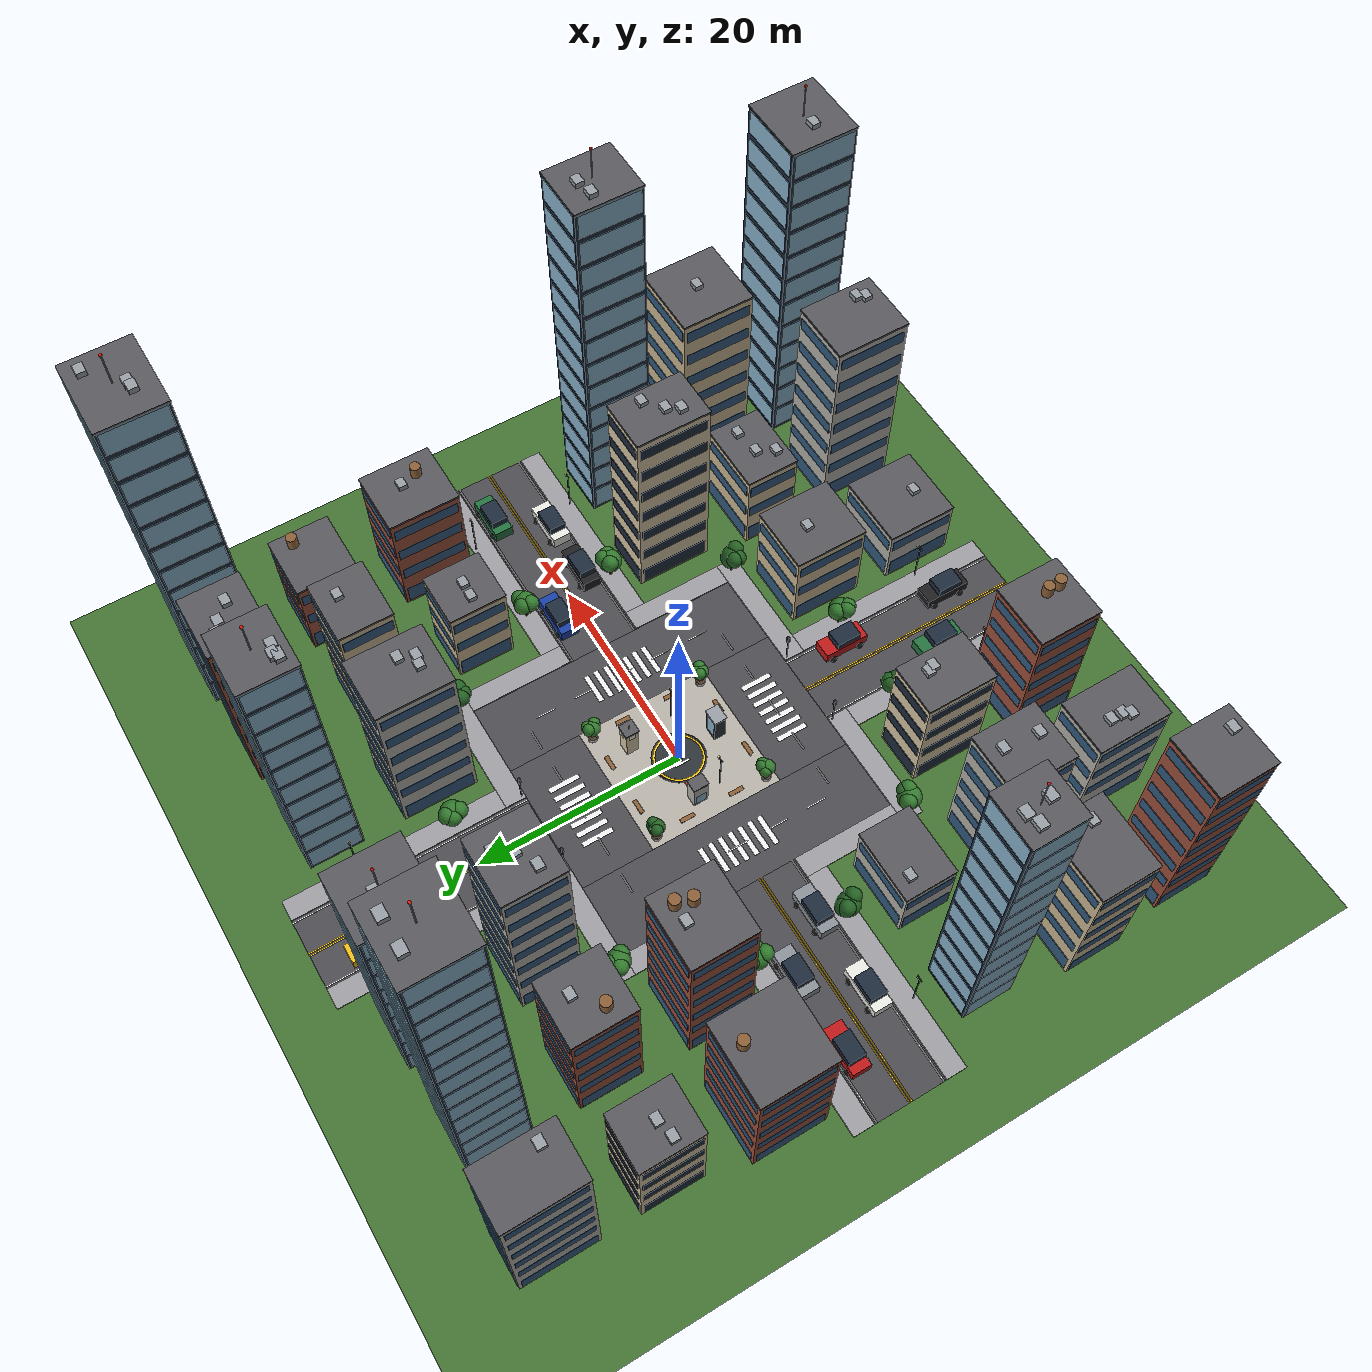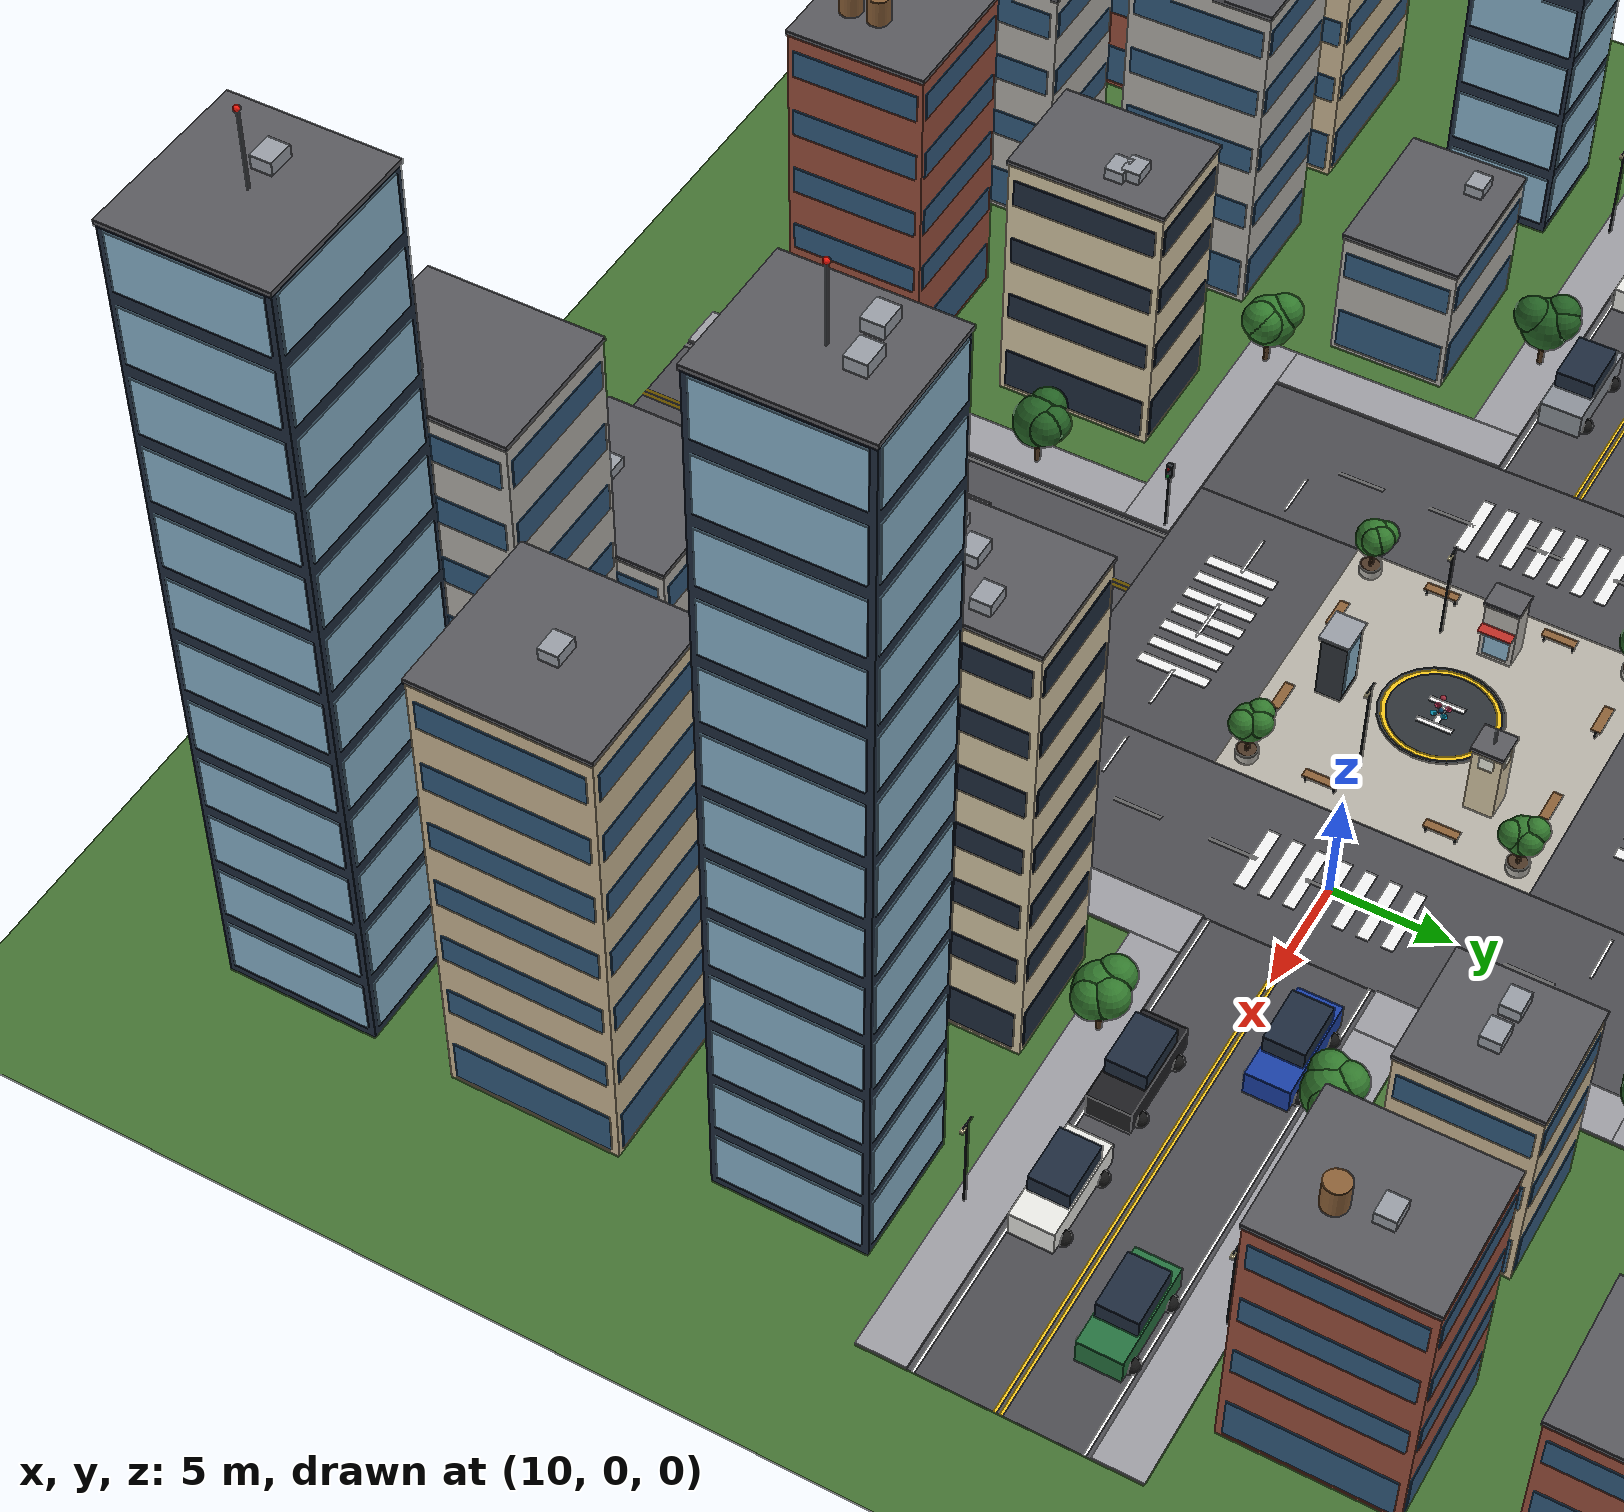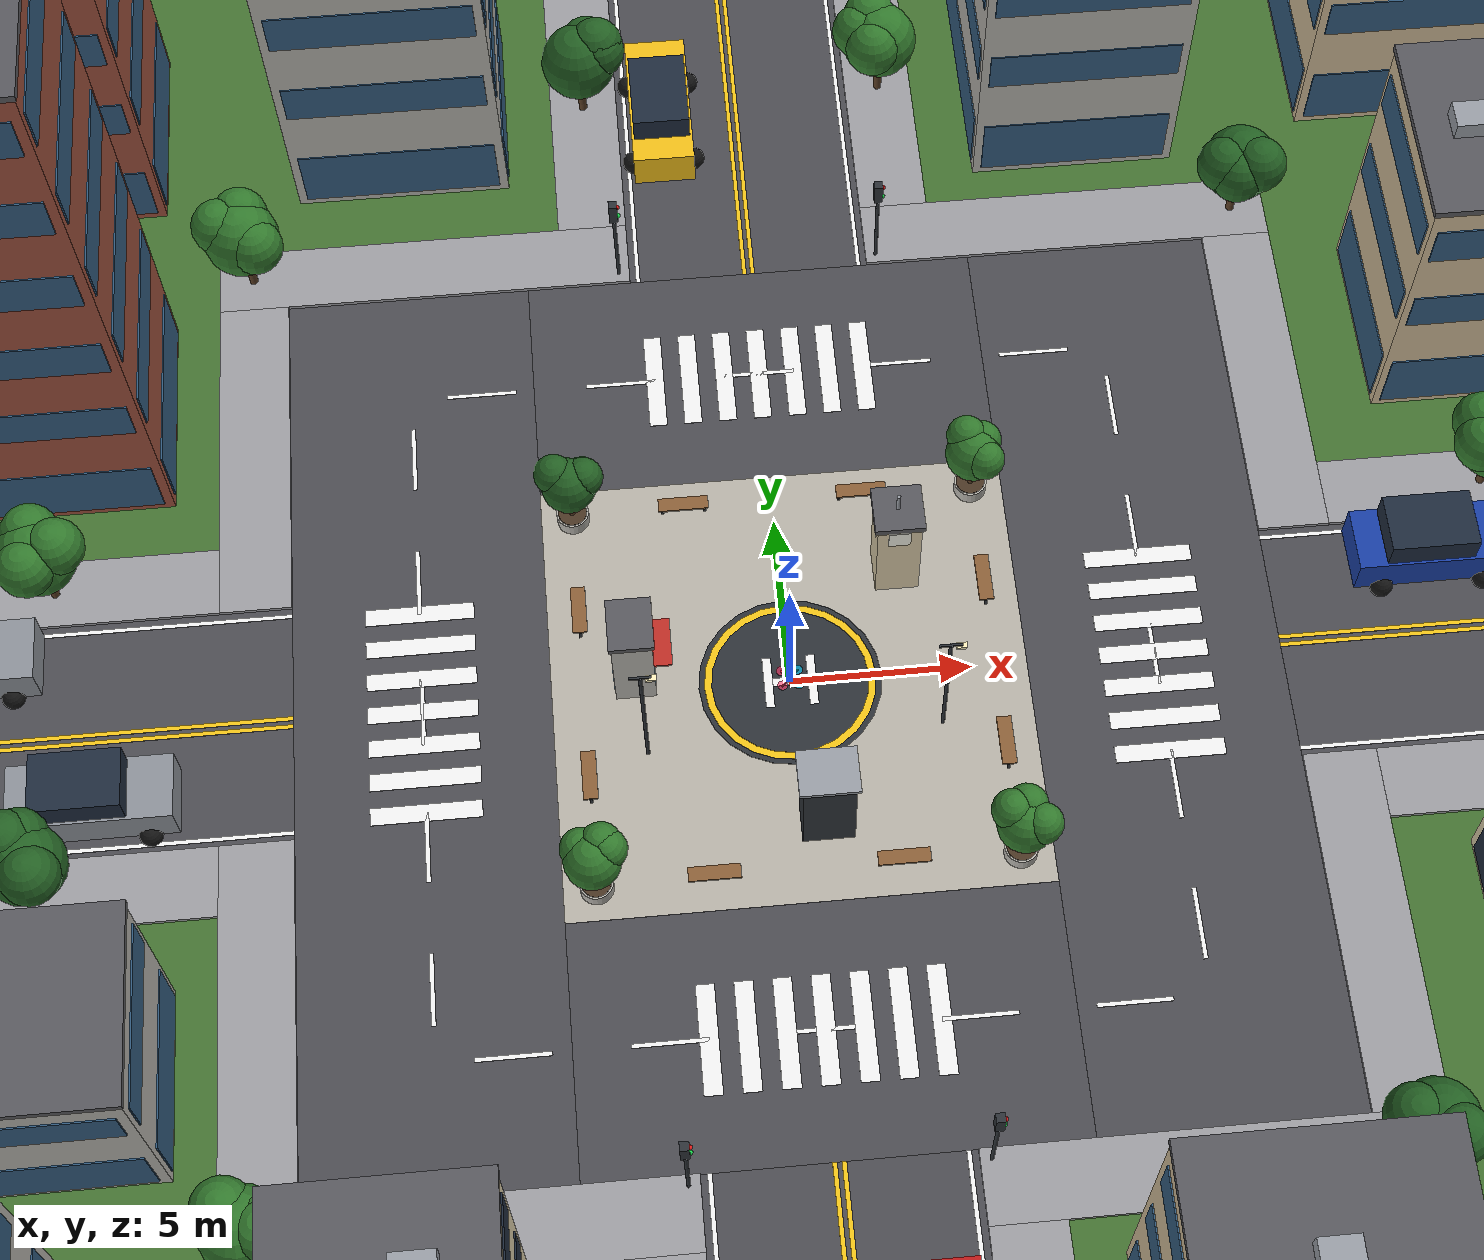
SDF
<?xml version="1.0" ?>
<!-- GENERATED by generate_world.py from config.yaml -> world. Do not edit by hand. -->
<sdf version="1.6">
  <world name="city">
    <scene><ambient>0.38 0.4 0.45 1</ambient><background>0.82 0.88 0.95 1</background><shadows>true</shadows><sky><clouds><speed>4</speed></clouds></sky></scene>
    <light name="sun" type="directional"><cast_shadows>true</cast_shadows><pose>0 0 60 0 0 0</pose><diffuse>0.95 0.92 0.85 1</diffuse><specular>0.2 0.2 0.2 1</specular><direction>-0.45 -0.3 -1</direction></light>
    <physics type="ode"><max_step_size>0.004</max_step_size><real_time_update_rate>250</real_time_update_rate></physics>
    <gui fullscreen="0"><camera name="user_camera"><pose>-9 -9 6 0 0.35 0.785</pose></camera></gui>
    <model name="ground"><static>true</static><link name="link"><collision name="c"><geometry><plane><normal>0 0 1</normal><size>300 300</size></plane></geometry></collision><visual name="v"><cast_shadows>false</cast_shadows><geometry><plane><normal>0 0 1</normal><size>300 300</size></plane></geometry><material><ambient>0.27 0.45 0.2 1</ambient><diffuse>0.27 0.45 0.2 1</diffuse></material></visual></link></model>
    <model name="city"><static>true</static><link name="link">
      <visual name="ring_road_0"><pose>10 0 0.005 0 0 0</pose><geometry><box><size>7 27 0.01</size></box></geometry><material><ambient>0.3 0.3 0.32 1</ambient><diffuse>0.3 0.3 0.32 1</diffuse><specular>0.1 0.1 0.1 1</specular></material></visual>
      <collision name="ring_road_0_c"><pose>10 0 0.005 0 0 0</pose><geometry><box><size>7 27 0.01</size></box></geometry></collision>
      <visual name="avenue_0"><pose>24.75 0 0.005 0 0 0</pose><geometry><box><size>22.5 7 0.01</size></box></geometry><material><ambient>0.3 0.3 0.32 1</ambient><diffuse>0.3 0.3 0.32 1</diffuse><specular>0.1 0.1 0.1 1</specular></material></visual>
      <collision name="avenue_0_c"><pose>24.75 0 0.005 0 0 0</pose><geometry><box><size>22.5 7 0.01</size></box></geometry></collision>
      <visual name="ring_road_1"><pose>-10 0 0.005 0 0 0</pose><geometry><box><size>7 27 0.01</size></box></geometry><material><ambient>0.3 0.3 0.32 1</ambient><diffuse>0.3 0.3 0.32 1</diffuse><specular>0.1 0.1 0.1 1</specular></material></visual>
      <collision name="ring_road_1_c"><pose>-10 0 0.005 0 0 0</pose><geometry><box><size>7 27 0.01</size></box></geometry></collision>
      <visual name="avenue_1"><pose>-24.75 0 0.005 0 0 0</pose><geometry><box><size>22.5 7 0.01</size></box></geometry><material><ambient>0.3 0.3 0.32 1</ambient><diffuse>0.3 0.3 0.32 1</diffuse><specular>0.1 0.1 0.1 1</specular></material></visual>
      <collision name="avenue_1_c"><pose>-24.75 0 0.005 0 0 0</pose><geometry><box><size>22.5 7 0.01</size></box></geometry></collision>
      <visual name="ring_road_2"><pose>0 10 0.005 0 0 0</pose><geometry><box><size>13 7 0.01</size></box></geometry><material><ambient>0.3 0.3 0.32 1</ambient><diffuse>0.3 0.3 0.32 1</diffuse><specular>0.1 0.1 0.1 1</specular></material></visual>
      <collision name="ring_road_2_c"><pose>0 10 0.005 0 0 0</pose><geometry><box><size>13 7 0.01</size></box></geometry></collision>
      <visual name="avenue_2"><pose>0 24.75 0.005 0 0 0</pose><geometry><box><size>7 22.5 0.01</size></box></geometry><material><ambient>0.3 0.3 0.32 1</ambient><diffuse>0.3 0.3 0.32 1</diffuse><specular>0.1 0.1 0.1 1</specular></material></visual>
      <collision name="avenue_2_c"><pose>0 24.75 0.005 0 0 0</pose><geometry><box><size>7 22.5 0.01</size></box></geometry></collision>
      <visual name="ring_road_3"><pose>0 -10 0.005 0 0 0</pose><geometry><box><size>13 7 0.01</size></box></geometry><material><ambient>0.3 0.3 0.32 1</ambient><diffuse>0.3 0.3 0.32 1</diffuse><specular>0.1 0.1 0.1 1</specular></material></visual>
      <collision name="ring_road_3_c"><pose>0 -10 0.005 0 0 0</pose><geometry><box><size>13 7 0.01</size></box></geometry></collision>
      <visual name="avenue_3"><pose>0 -24.75 0.005 0 0 0</pose><geometry><box><size>7 22.5 0.01</size></box></geometry><material><ambient>0.3 0.3 0.32 1</ambient><diffuse>0.3 0.3 0.32 1</diffuse><specular>0.1 0.1 0.1 1</specular></material></visual>
      <collision name="avenue_3_c"><pose>0 -24.75 0.005 0 0 0</pose><geometry><box><size>7 22.5 0.01</size></box></geometry></collision>
      <visual name="line_yellow_0"><pose>24.75 -0.12 0.016 0 0 0</pose><geometry><box><size>22.5 0.12 0.012</size></box></geometry><material><ambient>0.96 0.78 0.1 1</ambient><diffuse>0.96 0.78 0.1 1</diffuse><specular>0.1 0.1 0.1 1</specular></material></visual>
      <visual name="line_yellow_1"><pose>24.75 0.12 0.016 0 0 0</pose><geometry><box><size>22.5 0.12 0.012</size></box></geometry><material><ambient>0.96 0.78 0.1 1</ambient><diffuse>0.96 0.78 0.1 1</diffuse><specular>0.1 0.1 0.1 1</specular></material></visual>
      <visual name="line_white_0"><pose>24.75 -3.26 0.016 0 0 0</pose><geometry><box><size>22.5 0.12 0.012</size></box></geometry><material><ambient>0.95 0.95 0.95 1</ambient><diffuse>0.95 0.95 0.95 1</diffuse><specular>0.1 0.1 0.1 1</specular></material></visual>
      <visual name="line_white_1"><pose>24.75 3.26 0.016 0 0 0</pose><geometry><box><size>22.5 0.12 0.012</size></box></geometry><material><ambient>0.95 0.95 0.95 1</ambient><diffuse>0.95 0.95 0.95 1</diffuse><specular>0.1 0.1 0.1 1</specular></material></visual>
      <visual name="line_yellow_2"><pose>-24.75 -0.12 0.016 0 0 0</pose><geometry><box><size>22.5 0.12 0.012</size></box></geometry><material><ambient>0.96 0.78 0.1 1</ambient><diffuse>0.96 0.78 0.1 1</diffuse><specular>0.1 0.1 0.1 1</specular></material></visual>
      <visual name="line_yellow_3"><pose>-24.75 0.12 0.016 0 0 0</pose><geometry><box><size>22.5 0.12 0.012</size></box></geometry><material><ambient>0.96 0.78 0.1 1</ambient><diffuse>0.96 0.78 0.1 1</diffuse><specular>0.1 0.1 0.1 1</specular></material></visual>
      <visual name="line_white_2"><pose>-24.75 -3.26 0.016 0 0 0</pose><geometry><box><size>22.5 0.12 0.012</size></box></geometry><material><ambient>0.95 0.95 0.95 1</ambient><diffuse>0.95 0.95 0.95 1</diffuse><specular>0.1 0.1 0.1 1</specular></material></visual>
      <visual name="line_white_3"><pose>-24.75 3.26 0.016 0 0 0</pose><geometry><box><size>22.5 0.12 0.012</size></box></geometry><material><ambient>0.95 0.95 0.95 1</ambient><diffuse>0.95 0.95 0.95 1</diffuse><specular>0.1 0.1 0.1 1</specular></material></visual>
      <visual name="line_yellow_4"><pose>-0.12 24.75 0.016 0 0 0</pose><geometry><box><size>0.12 22.5 0.012</size></box></geometry><material><ambient>0.96 0.78 0.1 1</ambient><diffuse>0.96 0.78 0.1 1</diffuse><specular>0.1 0.1 0.1 1</specular></material></visual>
      <visual name="line_yellow_5"><pose>0.12 24.75 0.016 0 0 0</pose><geometry><box><size>0.12 22.5 0.012</size></box></geometry><material><ambient>0.96 0.78 0.1 1</ambient><diffuse>0.96 0.78 0.1 1</diffuse><specular>0.1 0.1 0.1 1</specular></material></visual>
      <visual name="line_white_4"><pose>-3.26 24.75 0.016 0 0 0</pose><geometry><box><size>0.12 22.5 0.012</size></box></geometry><material><ambient>0.95 0.95 0.95 1</ambient><diffuse>0.95 0.95 0.95 1</diffuse><specular>0.1 0.1 0.1 1</specular></material></visual>
      <visual name="line_white_5"><pose>3.26 24.75 0.016 0 0 0</pose><geometry><box><size>0.12 22.5 0.012</size></box></geometry><material><ambient>0.95 0.95 0.95 1</ambient><diffuse>0.95 0.95 0.95 1</diffuse><specular>0.1 0.1 0.1 1</specular></material></visual>
      <visual name="line_yellow_6"><pose>-0.12 -24.75 0.016 0 0 0</pose><geometry><box><size>0.12 22.5 0.012</size></box></geometry><material><ambient>0.96 0.78 0.1 1</ambient><diffuse>0.96 0.78 0.1 1</diffuse><specular>0.1 0.1 0.1 1</specular></material></visual>
      <visual name="line_yellow_7"><pose>0.12 -24.75 0.016 0 0 0</pose><geometry><box><size>0.12 22.5 0.012</size></box></geometry><material><ambient>0.96 0.78 0.1 1</ambient><diffuse>0.96 0.78 0.1 1</diffuse><specular>0.1 0.1 0.1 1</specular></material></visual>
      <visual name="line_white_6"><pose>-3.26 -24.75 0.016 0 0 0</pose><geometry><box><size>0.12 22.5 0.012</size></box></geometry><material><ambient>0.95 0.95 0.95 1</ambient><diffuse>0.95 0.95 0.95 1</diffuse><specular>0.1 0.1 0.1 1</specular></material></visual>
      <visual name="line_white_7"><pose>3.26 -24.75 0.016 0 0 0</pose><geometry><box><size>0.12 22.5 0.012</size></box></geometry><material><ambient>0.95 0.95 0.95 1</ambient><diffuse>0.95 0.95 0.95 1</diffuse><specular>0.1 0.1 0.1 1</specular></material></visual>
      <visual name="line_dash_0"><pose>-8 10 0.016 0 0 0</pose><geometry><box><size>2 0.12 0.012</size></box></geometry><material><ambient>0.95 0.95 0.95 1</ambient><diffuse>0.95 0.95 0.95 1</diffuse><specular>0.1 0.1 0.1 1</specular></material></visual>
      <visual name="line_dash_1"><pose>-8 -10 0.016 0 0 0</pose><geometry><box><size>2 0.12 0.012</size></box></geometry><material><ambient>0.95 0.95 0.95 1</ambient><diffuse>0.95 0.95 0.95 1</diffuse><specular>0.1 0.1 0.1 1</specular></material></visual>
      <visual name="line_dash_2"><pose>10 -8 0.016 0 0 0</pose><geometry><box><size>0.12 2 0.012</size></box></geometry><material><ambient>0.95 0.95 0.95 1</ambient><diffuse>0.95 0.95 0.95 1</diffuse><specular>0.1 0.1 0.1 1</specular></material></visual>
      <visual name="line_dash_3"><pose>-10 -8 0.016 0 0 0</pose><geometry><box><size>0.12 2 0.012</size></box></geometry><material><ambient>0.95 0.95 0.95 1</ambient><diffuse>0.95 0.95 0.95 1</diffuse><specular>0.1 0.1 0.1 1</specular></material></visual>
      <visual name="line_dash_4"><pose>-4 10 0.016 0 0 0</pose><geometry><box><size>2 0.12 0.012</size></box></geometry><material><ambient>0.95 0.95 0.95 1</ambient><diffuse>0.95 0.95 0.95 1</diffuse><specular>0.1 0.1 0.1 1</specular></material></visual>
      <visual name="line_dash_5"><pose>-4 -10 0.016 0 0 0</pose><geometry><box><size>2 0.12 0.012</size></box></geometry><material><ambient>0.95 0.95 0.95 1</ambient><diffuse>0.95 0.95 0.95 1</diffuse><specular>0.1 0.1 0.1 1</specular></material></visual>
      <visual name="line_dash_6"><pose>10 -4 0.016 0 0 0</pose><geometry><box><size>0.12 2 0.012</size></box></geometry><material><ambient>0.95 0.95 0.95 1</ambient><diffuse>0.95 0.95 0.95 1</diffuse><specular>0.1 0.1 0.1 1</specular></material></visual>
      <visual name="line_dash_7"><pose>-10 -4 0.016 0 0 0</pose><geometry><box><size>0.12 2 0.012</size></box></geometry><material><ambient>0.95 0.95 0.95 1</ambient><diffuse>0.95 0.95 0.95 1</diffuse><specular>0.1 0.1 0.1 1</specular></material></visual>
      <visual name="line_dash_8"><pose>0 10 0.016 0 0 0</pose><geometry><box><size>2 0.12 0.012</size></box></geometry><material><ambient>0.95 0.95 0.95 1</ambient><diffuse>0.95 0.95 0.95 1</diffuse><specular>0.1 0.1 0.1 1</specular></material></visual>
      <visual name="line_dash_9"><pose>0 -10 0.016 0 0 0</pose><geometry><box><size>2 0.12 0.012</size></box></geometry><material><ambient>0.95 0.95 0.95 1</ambient><diffuse>0.95 0.95 0.95 1</diffuse><specular>0.1 0.1 0.1 1</specular></material></visual>
      <visual name="line_dash_10"><pose>10 0 0.016 0 0 0</pose><geometry><box><size>0.12 2 0.012</size></box></geometry><material><ambient>0.95 0.95 0.95 1</ambient><diffuse>0.95 0.95 0.95 1</diffuse><specular>0.1 0.1 0.1 1</specular></material></visual>
      <visual name="line_dash_11"><pose>-10 0 0.016 0 0 0</pose><geometry><box><size>0.12 2 0.012</size></box></geometry><material><ambient>0.95 0.95 0.95 1</ambient><diffuse>0.95 0.95 0.95 1</diffuse><specular>0.1 0.1 0.1 1</specular></material></visual>
      <visual name="line_dash_12"><pose>4 10 0.016 0 0 0</pose><geometry><box><size>2 0.12 0.012</size></box></geometry><material><ambient>0.95 0.95 0.95 1</ambient><diffuse>0.95 0.95 0.95 1</diffuse><specular>0.1 0.1 0.1 1</specular></material></visual>
      <visual name="line_dash_13"><pose>4 -10 0.016 0 0 0</pose><geometry><box><size>2 0.12 0.012</size></box></geometry><material><ambient>0.95 0.95 0.95 1</ambient><diffuse>0.95 0.95 0.95 1</diffuse><specular>0.1 0.1 0.1 1</specular></material></visual>
      <visual name="line_dash_14"><pose>10 4 0.016 0 0 0</pose><geometry><box><size>0.12 2 0.012</size></box></geometry><material><ambient>0.95 0.95 0.95 1</ambient><diffuse>0.95 0.95 0.95 1</diffuse><specular>0.1 0.1 0.1 1</specular></material></visual>
      <visual name="line_dash_15"><pose>-10 4 0.016 0 0 0</pose><geometry><box><size>0.12 2 0.012</size></box></geometry><material><ambient>0.95 0.95 0.95 1</ambient><diffuse>0.95 0.95 0.95 1</diffuse><specular>0.1 0.1 0.1 1</specular></material></visual>
      <visual name="line_dash_16"><pose>8 10 0.016 0 0 0</pose><geometry><box><size>2 0.12 0.012</size></box></geometry><material><ambient>0.95 0.95 0.95 1</ambient><diffuse>0.95 0.95 0.95 1</diffuse><specular>0.1 0.1 0.1 1</specular></material></visual>
      <visual name="line_dash_17"><pose>8 -10 0.016 0 0 0</pose><geometry><box><size>2 0.12 0.012</size></box></geometry><material><ambient>0.95 0.95 0.95 1</ambient><diffuse>0.95 0.95 0.95 1</diffuse><specular>0.1 0.1 0.1 1</specular></material></visual>
      <visual name="line_dash_18"><pose>10 8 0.016 0 0 0</pose><geometry><box><size>0.12 2 0.012</size></box></geometry><material><ambient>0.95 0.95 0.95 1</ambient><diffuse>0.95 0.95 0.95 1</diffuse><specular>0.1 0.1 0.1 1</specular></material></visual>
      <visual name="line_dash_19"><pose>-10 8 0.016 0 0 0</pose><geometry><box><size>0.12 2 0.012</size></box></geometry><material><ambient>0.95 0.95 0.95 1</ambient><diffuse>0.95 0.95 0.95 1</diffuse><specular>0.1 0.1 0.1 1</specular></material></visual>
      <visual name="zebra_0"><pose>10 -3 0.016 0 0 0</pose><geometry><box><size>3 0.5 0.012</size></box></geometry><material><ambient>0.95 0.95 0.95 1</ambient><diffuse>0.95 0.95 0.95 1</diffuse><specular>0.1 0.1 0.1 1</specular></material></visual>
      <visual name="zebra_1"><pose>-3 10 0.016 0 0 0</pose><geometry><box><size>0.5 3 0.012</size></box></geometry><material><ambient>0.95 0.95 0.95 1</ambient><diffuse>0.95 0.95 0.95 1</diffuse><specular>0.1 0.1 0.1 1</specular></material></visual>
      <visual name="zebra_2"><pose>-10 -3 0.016 0 0 0</pose><geometry><box><size>3 0.5 0.012</size></box></geometry><material><ambient>0.95 0.95 0.95 1</ambient><diffuse>0.95 0.95 0.95 1</diffuse><specular>0.1 0.1 0.1 1</specular></material></visual>
      <visual name="zebra_3"><pose>-3 -10 0.016 0 0 0</pose><geometry><box><size>0.5 3 0.012</size></box></geometry><material><ambient>0.95 0.95 0.95 1</ambient><diffuse>0.95 0.95 0.95 1</diffuse><specular>0.1 0.1 0.1 1</specular></material></visual>
      <visual name="zebra_4"><pose>10 -2 0.016 0 0 0</pose><geometry><box><size>3 0.5 0.012</size></box></geometry><material><ambient>0.95 0.95 0.95 1</ambient><diffuse>0.95 0.95 0.95 1</diffuse><specular>0.1 0.1 0.1 1</specular></material></visual>
      <visual name="zebra_5"><pose>-2 10 0.016 0 0 0</pose><geometry><box><size>0.5 3 0.012</size></box></geometry><material><ambient>0.95 0.95 0.95 1</ambient><diffuse>0.95 0.95 0.95 1</diffuse><specular>0.1 0.1 0.1 1</specular></material></visual>
      <visual name="zebra_6"><pose>-10 -2 0.016 0 0 0</pose><geometry><box><size>3 0.5 0.012</size></box></geometry><material><ambient>0.95 0.95 0.95 1</ambient><diffuse>0.95 0.95 0.95 1</diffuse><specular>0.1 0.1 0.1 1</specular></material></visual>
      <visual name="zebra_7"><pose>-2 -10 0.016 0 0 0</pose><geometry><box><size>0.5 3 0.012</size></box></geometry><material><ambient>0.95 0.95 0.95 1</ambient><diffuse>0.95 0.95 0.95 1</diffuse><specular>0.1 0.1 0.1 1</specular></material></visual>
      <visual name="zebra_8"><pose>10 -1 0.016 0 0 0</pose><geometry><box><size>3 0.5 0.012</size></box></geometry><material><ambient>0.95 0.95 0.95 1</ambient><diffuse>0.95 0.95 0.95 1</diffuse><specular>0.1 0.1 0.1 1</specular></material></visual>
      <visual name="zebra_9"><pose>-1 10 0.016 0 0 0</pose><geometry><box><size>0.5 3 0.012</size></box></geometry><material><ambient>0.95 0.95 0.95 1</ambient><diffuse>0.95 0.95 0.95 1</diffuse><specular>0.1 0.1 0.1 1</specular></material></visual>
      <visual name="zebra_10"><pose>-10 -1 0.016 0 0 0</pose><geometry><box><size>3 0.5 0.012</size></box></geometry><material><ambient>0.95 0.95 0.95 1</ambient><diffuse>0.95 0.95 0.95 1</diffuse><specular>0.1 0.1 0.1 1</specular></material></visual>
      <visual name="zebra_11"><pose>-1 -10 0.016 0 0 0</pose><geometry><box><size>0.5 3 0.012</size></box></geometry><material><ambient>0.95 0.95 0.95 1</ambient><diffuse>0.95 0.95 0.95 1</diffuse><specular>0.1 0.1 0.1 1</specular></material></visual>
      <visual name="zebra_12"><pose>10 0 0.016 0 0 0</pose><geometry><box><size>3 0.5 0.012</size></box></geometry><material><ambient>0.95 0.95 0.95 1</ambient><diffuse>0.95 0.95 0.95 1</diffuse><specular>0.1 0.1 0.1 1</specular></material></visual>
      <visual name="zebra_13"><pose>0 10 0.016 0 0 0</pose><geometry><box><size>0.5 3 0.012</size></box></geometry><material><ambient>0.95 0.95 0.95 1</ambient><diffuse>0.95 0.95 0.95 1</diffuse><specular>0.1 0.1 0.1 1</specular></material></visual>
      <visual name="zebra_14"><pose>-10 0 0.016 0 0 0</pose><geometry><box><size>3 0.5 0.012</size></box></geometry><material><ambient>0.95 0.95 0.95 1</ambient><diffuse>0.95 0.95 0.95 1</diffuse><specular>0.1 0.1 0.1 1</specular></material></visual>
      <visual name="zebra_15"><pose>0 -10 0.016 0 0 0</pose><geometry><box><size>0.5 3 0.012</size></box></geometry><material><ambient>0.95 0.95 0.95 1</ambient><diffuse>0.95 0.95 0.95 1</diffuse><specular>0.1 0.1 0.1 1</specular></material></visual>
      <visual name="zebra_16"><pose>10 1 0.016 0 0 0</pose><geometry><box><size>3 0.5 0.012</size></box></geometry><material><ambient>0.95 0.95 0.95 1</ambient><diffuse>0.95 0.95 0.95 1</diffuse><specular>0.1 0.1 0.1 1</specular></material></visual>
      <visual name="zebra_17"><pose>1 10 0.016 0 0 0</pose><geometry><box><size>0.5 3 0.012</size></box></geometry><material><ambient>0.95 0.95 0.95 1</ambient><diffuse>0.95 0.95 0.95 1</diffuse><specular>0.1 0.1 0.1 1</specular></material></visual>
      <visual name="zebra_18"><pose>-10 1 0.016 0 0 0</pose><geometry><box><size>3 0.5 0.012</size></box></geometry><material><ambient>0.95 0.95 0.95 1</ambient><diffuse>0.95 0.95 0.95 1</diffuse><specular>0.1 0.1 0.1 1</specular></material></visual>
      <visual name="zebra_19"><pose>1 -10 0.016 0 0 0</pose><geometry><box><size>0.5 3 0.012</size></box></geometry><material><ambient>0.95 0.95 0.95 1</ambient><diffuse>0.95 0.95 0.95 1</diffuse><specular>0.1 0.1 0.1 1</specular></material></visual>
      <visual name="zebra_20"><pose>10 2 0.016 0 0 0</pose><geometry><box><size>3 0.5 0.012</size></box></geometry><material><ambient>0.95 0.95 0.95 1</ambient><diffuse>0.95 0.95 0.95 1</diffuse><specular>0.1 0.1 0.1 1</specular></material></visual>
      <visual name="zebra_21"><pose>2 10 0.016 0 0 0</pose><geometry><box><size>0.5 3 0.012</size></box></geometry><material><ambient>0.95 0.95 0.95 1</ambient><diffuse>0.95 0.95 0.95 1</diffuse><specular>0.1 0.1 0.1 1</specular></material></visual>
      <visual name="zebra_22"><pose>-10 2 0.016 0 0 0</pose><geometry><box><size>3 0.5 0.012</size></box></geometry><material><ambient>0.95 0.95 0.95 1</ambient><diffuse>0.95 0.95 0.95 1</diffuse><specular>0.1 0.1 0.1 1</specular></material></visual>
      <visual name="zebra_23"><pose>2 -10 0.016 0 0 0</pose><geometry><box><size>0.5 3 0.012</size></box></geometry><material><ambient>0.95 0.95 0.95 1</ambient><diffuse>0.95 0.95 0.95 1</diffuse><specular>0.1 0.1 0.1 1</specular></material></visual>
      <visual name="zebra_24"><pose>10 3 0.016 0 0 0</pose><geometry><box><size>3 0.5 0.012</size></box></geometry><material><ambient>0.95 0.95 0.95 1</ambient><diffuse>0.95 0.95 0.95 1</diffuse><specular>0.1 0.1 0.1 1</specular></material></visual>
      <visual name="zebra_25"><pose>3 10 0.016 0 0 0</pose><geometry><box><size>0.5 3 0.012</size></box></geometry><material><ambient>0.95 0.95 0.95 1</ambient><diffuse>0.95 0.95 0.95 1</diffuse><specular>0.1 0.1 0.1 1</specular></material></visual>
      <visual name="zebra_26"><pose>-10 3 0.016 0 0 0</pose><geometry><box><size>3 0.5 0.012</size></box></geometry><material><ambient>0.95 0.95 0.95 1</ambient><diffuse>0.95 0.95 0.95 1</diffuse><specular>0.1 0.1 0.1 1</specular></material></visual>
      <visual name="zebra_27"><pose>3 -10 0.016 0 0 0</pose><geometry><box><size>0.5 3 0.012</size></box></geometry><material><ambient>0.95 0.95 0.95 1</ambient><diffuse>0.95 0.95 0.95 1</diffuse><specular>0.1 0.1 0.1 1</specular></material></visual>
      <visual name="plaza_0"><pose>0 0 0.01 0 0 0</pose><geometry><box><size>13 13 0.02</size></box></geometry><material><ambient>0.72 0.7 0.66 1</ambient><diffuse>0.72 0.7 0.66 1</diffuse><specular>0.1 0.1 0.1 1</specular></material></visual>
      <collision name="plaza_0_c"><pose>0 0 0.01 0 0 0</pose><geometry><box><size>13 13 0.02</size></box></geometry></collision>
      <visual name="helipad_0"><pose>0 0 0.024 0 0 0</pose><geometry><cylinder><radius>2.5</radius><length>0.008</length></cylinder></geometry><material><ambient>0.18 0.2 0.22 1</ambient><diffuse>0.18 0.2 0.22 1</diffuse><specular>0.1 0.1 0.1 1</specular></material></visual>
      <visual name="helipad_ring_0"><pose>0 0 0.029 0 0 0</pose><geometry><cylinder><radius>2.35</radius><length>0.004</length></cylinder></geometry><material><ambient>0.96 0.78 0.1 1</ambient><diffuse>0.96 0.78 0.1 1</diffuse><specular>0.1 0.1 0.1 1</specular></material></visual>
      <visual name="helipad_inner_0"><pose>0 0 0.032 0 0 0</pose><geometry><cylinder><radius>2.15</radius><length>0.004</length></cylinder></geometry><material><ambient>0.18 0.2 0.22 1</ambient><diffuse>0.18 0.2 0.22 1</diffuse><specular>0.1 0.1 0.1 1</specular></material></visual>
      <visual name="helipad_h_0"><pose>-0.6 0 0.036 0 0 0</pose><geometry><box><size>0.24 1.5 0.004</size></box></geometry><material><ambient>0.95 0.95 0.95 1</ambient><diffuse>0.95 0.95 0.95 1</diffuse><specular>0.1 0.1 0.1 1</specular></material></visual>
      <visual name="helipad_h_1"><pose>0.6 0 0.036 0 0 0</pose><geometry><box><size>0.24 1.5 0.004</size></box></geometry><material><ambient>0.95 0.95 0.95 1</ambient><diffuse>0.95 0.95 0.95 1</diffuse><specular>0.1 0.1 0.1 1</specular></material></visual>
      <visual name="helipad_h_2"><pose>0 0 0.036 0 0 0</pose><geometry><box><size>0.96 0.24 0.004</size></box></geometry><material><ambient>0.95 0.95 0.95 1</ambient><diffuse>0.95 0.95 0.95 1</diffuse><specular>0.1 0.1 0.1 1</specular></material></visual>
      <visual name="clock_tower_0"><pose>3.2 3.2 1.62 0 0 0</pose><geometry><box><size>1.2 1.2 3.2</size></box></geometry><material><ambient>0.86 0.8 0.66 1</ambient><diffuse>0.86 0.8 0.66 1</diffuse><specular>0.1 0.1 0.1 1</specular></material></visual>
      <collision name="clock_tower_0_c"><pose>3.2 3.2 1.62 0 0 0</pose><geometry><box><size>1.2 1.2 3.2</size></box></geometry></collision>
      <visual name="clock_roof_0"><pose>3.2 3.2 3.32 0 0 0</pose><geometry><box><size>1.36 1.36 0.2</size></box></geometry><material><ambient>0.35 0.35 0.37 1</ambient><diffuse>0.35 0.35 0.37 1</diffuse><specular>0.1 0.1 0.1 1</specular></material></visual>
      <collision name="clock_roof_0_c"><pose>3.2 3.2 3.32 0 0 0</pose><geometry><box><size>1.36 1.36 0.2</size></box></geometry></collision>
      <visual name="clock_spire_0"><pose>3.2 3.2 3.72 0 0 0</pose><geometry><cylinder><radius>0.05</radius><length>0.6</length></cylinder></geometry><material><ambient>0.6 0.62 0.65 1</ambient><diffuse>0.6 0.62 0.65 1</diffuse><specular>0.6 0.6 0.6 1</specular></material></visual>
      <collision name="clock_spire_0_c"><pose>3.2 3.2 3.72 0 0 0</pose><geometry><cylinder><radius>0.05</radius><length>0.6</length></cylinder></geometry></collision>
      <visual name="clock_face_0"><pose>3.81 3.2 2.77 0 0 0</pose><geometry><box><size>0.02 0.6 0.6</size></box></geometry><material><ambient>0.95 0.95 0.9 1</ambient><diffuse>0.95 0.95 0.9 1</diffuse><specular>0.1 0.1 0.1 1</specular></material></visual>
      <visual name="clock_face_1"><pose>2.59 3.2 2.77 0 0 0</pose><geometry><box><size>0.02 0.6 0.6</size></box></geometry><material><ambient>0.95 0.95 0.9 1</ambient><diffuse>0.95 0.95 0.9 1</diffuse><specular>0.1 0.1 0.1 1</specular></material></visual>
      <visual name="clock_face_2"><pose>3.2 3.81 2.77 0 0 0</pose><geometry><box><size>0.6 0.02 0.6</size></box></geometry><material><ambient>0.95 0.95 0.9 1</ambient><diffuse>0.95 0.95 0.9 1</diffuse><specular>0.1 0.1 0.1 1</specular></material></visual>
      <visual name="clock_face_3"><pose>3.2 2.59 2.77 0 0 0</pose><geometry><box><size>0.6 0.02 0.6</size></box></geometry><material><ambient>0.95 0.95 0.9 1</ambient><diffuse>0.95 0.95 0.9 1</diffuse><specular>0.1 0.1 0.1 1</specular></material></visual>
      <visual name="cafe_0"><pose>-4.2 0.6 1.42 0 0 0</pose><geometry><box><size>1.1 1.4 2.8</size></box></geometry><material><ambient>0.72 0.71 0.68 1</ambient><diffuse>0.72 0.71 0.68 1</diffuse><specular>0.1 0.1 0.1 1</specular></material></visual>
      <collision name="cafe_0_c"><pose>-4.2 0.6 1.42 0 0 0</pose><geometry><box><size>1.1 1.4 2.8</size></box></geometry></collision>
      <visual name="cafe_glass_0"><pose>-4.2 0.6 0.86 0 0 0</pose><geometry><box><size>1.14 1.05 1.26</size></box></geometry><material><ambient>0.55 0.72 0.82 1</ambient><diffuse>0.55 0.72 0.82 1</diffuse><specular>0.9 0.9 0.9 1</specular></material></visual>
      <visual name="cafe_awning_0"><pose>-3.4 0.6 1.77 0 0 0</pose><geometry><box><size>0.5 1.4 0.06</size></box></geometry><material><ambient>0.75 0.18 0.15 1</ambient><diffuse>0.75 0.18 0.15 1</diffuse><specular>0.1 0.1 0.1 1</specular></material></visual>
      <visual name="cafe_roof_0"><pose>-4.2 0.6 2.9 0 0 0</pose><geometry><box><size>1.22 1.52 0.16</size></box></geometry><material><ambient>0.35 0.35 0.37 1</ambient><diffuse>0.35 0.35 0.37 1</diffuse><specular>0.1 0.1 0.1 1</specular></material></visual>
      <collision name="cafe_roof_0_c"><pose>-4.2 0.6 2.9 0 0 0</pose><geometry><box><size>1.22 1.52 0.16</size></box></geometry></collision>
      <visual name="metro_0"><pose>0.6 -4.2 1.52 0 0 0</pose><geometry><box><size>1.4 1.1 3</size></box></geometry><material><ambient>0.18 0.2 0.22 1</ambient><diffuse>0.18 0.2 0.22 1</diffuse><specular>0.5 0.5 0.5 1</specular></material></visual>
      <collision name="metro_0_c"><pose>0.6 -4.2 1.52 0 0 0</pose><geometry><box><size>1.4 1.1 3</size></box></geometry></collision>
      <visual name="metro_glass_0"><pose>0.6 -3.64 1.52 0 0 0</pose><geometry><box><size>1.12 0.02 2.4</size></box></geometry><material><ambient>0.55 0.72 0.82 1</ambient><diffuse>0.55 0.72 0.82 1</diffuse><specular>0.9 0.9 0.9 1</specular></material></visual>
      <visual name="metro_roof_0"><pose>0.6 -4.2 3.08 0 0 0</pose><geometry><box><size>1.6 1.3 0.12</size></box></geometry><material><ambient>0.6 0.62 0.65 1</ambient><diffuse>0.6 0.62 0.65 1</diffuse><specular>0.6 0.6 0.6 1</specular></material></visual>
      <collision name="metro_roof_0_c"><pose>0.6 -4.2 3.08 0 0 0</pose><geometry><box><size>1.6 1.3 0.12</size></box></geometry></collision>
      <visual name="lamp_pole_0"><pose>4 -1.6 2.27 0 0 0</pose><geometry><cylinder><radius>0.05</radius><length>4.5</length></cylinder></geometry><material><ambient>0.18 0.2 0.22 1</ambient><diffuse>0.18 0.2 0.22 1</diffuse><specular>0.5 0.5 0.5 1</specular></material></visual>
      <collision name="lamp_pole_0_c"><pose>4 -1.6 2.27 0 0 0</pose><geometry><cylinder><radius>0.05</radius><length>4.5</length></cylinder></geometry></collision>
      <visual name="lamp_arm_0"><pose>4 -1.6 4.52 0 0 0</pose><geometry><box><size>0.6 0.06 0.06</size></box></geometry><material><ambient>0.18 0.2 0.22 1</ambient><diffuse>0.18 0.2 0.22 1</diffuse><specular>0.5 0.5 0.5 1</specular></material></visual>
      <visual name="lamp_head_0"><pose>4.28 -1.6 4.46 0 0 0</pose><geometry><box><size>0.28 0.16 0.08</size></box></geometry><material><ambient>1 0.95 0.75 1</ambient><diffuse>1 0.95 0.75 1</diffuse><specular>0.1 0.1 0.1 1</specular></material></visual>
      <visual name="lamp_pole_1"><pose>-4 -1.8 2.27 0 0 0</pose><geometry><cylinder><radius>0.05</radius><length>4.5</length></cylinder></geometry><material><ambient>0.18 0.2 0.22 1</ambient><diffuse>0.18 0.2 0.22 1</diffuse><specular>0.5 0.5 0.5 1</specular></material></visual>
      <collision name="lamp_pole_1_c"><pose>-4 -1.8 2.27 0 0 0</pose><geometry><cylinder><radius>0.05</radius><length>4.5</length></cylinder></geometry></collision>
      <visual name="lamp_arm_1"><pose>-4 -1.8 4.52 0 0 0</pose><geometry><box><size>0.6 0.06 0.06</size></box></geometry><material><ambient>0.18 0.2 0.22 1</ambient><diffuse>0.18 0.2 0.22 1</diffuse><specular>0.5 0.5 0.5 1</specular></material></visual>
      <visual name="lamp_head_1"><pose>-3.72 -1.8 4.46 0 0 0</pose><geometry><box><size>0.28 0.16 0.08</size></box></geometry><material><ambient>1 0.95 0.75 1</ambient><diffuse>1 0.95 0.75 1</diffuse><specular>0.1 0.1 0.1 1</specular></material></visual>
      <visual name="planter_0"><pose>-5.6 -5.6 0.22 0 0 0</pose><geometry><cylinder><radius>0.45</radius><length>0.4</length></cylinder></geometry><material><ambient>0.72 0.71 0.68 1</ambient><diffuse>0.72 0.71 0.68 1</diffuse><specular>0.1 0.1 0.1 1</specular></material></visual>
      <collision name="planter_0_c"><pose>-5.6 -5.6 0.22 0 0 0</pose><geometry><cylinder><radius>0.45</radius><length>0.4</length></cylinder></geometry></collision>
      <visual name="planter_soil_0"><pose>-5.6 -5.6 0.43 0 0 0</pose><geometry><cylinder><radius>0.4</radius><length>0.02</length></cylinder></geometry><material><ambient>0.3 0.22 0.15 1</ambient><diffuse>0.3 0.22 0.15 1</diffuse><specular>0.1 0.1 0.1 1</specular></material></visual>
      <visual name="trunk_0"><pose>-5.6 -5.6 0.945 0 0 0</pose><geometry><cylinder><radius>0.084</radius><length>1.05</length></cylinder></geometry><material><ambient>0.36 0.25 0.15 1</ambient><diffuse>0.36 0.25 0.15 1</diffuse><specular>0.1 0.1 0.1 1</specular></material></visual>
      <collision name="trunk_0_c"><pose>-5.6 -5.6 0.945 0 0 0</pose><geometry><cylinder><radius>0.084</radius><length>1.05</length></cylinder></geometry></collision>
      <visual name="canopy_0"><pose>-5.6 -5.6 1.932 0 0 0</pose><geometry><sphere><radius>0.77</radius></sphere></geometry><material><ambient>0.2 0.48 0.18 1</ambient><diffuse>0.2 0.48 0.18 1</diffuse><specular>0.1 0.1 0.1 1</specular></material></visual>
      <collision name="canopy_0_c"><pose>-5.6 -5.6 1.932 0 0 0</pose><geometry><sphere><radius>0.77</radius></sphere></geometry></collision>
      <visual name="canopy_1"><pose>-5.353 -5.256 2.209 0 0 0</pose><geometry><sphere><radius>0.56</radius></sphere></geometry><material><ambient>0.2 0.48 0.18 1</ambient><diffuse>0.2 0.48 0.18 1</diffuse><specular>0.1 0.1 0.1 1</specular></material></visual>
      <visual name="canopy_2"><pose>-5.22 -5.414 2.174 0 0 0</pose><geometry><sphere><radius>0.56</radius></sphere></geometry><material><ambient>0.2 0.48 0.18 1</ambient><diffuse>0.2 0.48 0.18 1</diffuse><specular>0.1 0.1 0.1 1</specular></material></visual>
      <visual name="canopy_3"><pose>-5.881 -5.284 2.027 0 0 0</pose><geometry><sphere><radius>0.56</radius></sphere></geometry><material><ambient>0.2 0.48 0.18 1</ambient><diffuse>0.2 0.48 0.18 1</diffuse><specular>0.1 0.1 0.1 1</specular></material></visual>
      <visual name="planter_1"><pose>-5.6 5.6 0.22 0 0 0</pose><geometry><cylinder><radius>0.45</radius><length>0.4</length></cylinder></geometry><material><ambient>0.72 0.71 0.68 1</ambient><diffuse>0.72 0.71 0.68 1</diffuse><specular>0.1 0.1 0.1 1</specular></material></visual>
      <collision name="planter_1_c"><pose>-5.6 5.6 0.22 0 0 0</pose><geometry><cylinder><radius>0.45</radius><length>0.4</length></cylinder></geometry></collision>
      <visual name="planter_soil_1"><pose>-5.6 5.6 0.43 0 0 0</pose><geometry><cylinder><radius>0.4</radius><length>0.02</length></cylinder></geometry><material><ambient>0.3 0.22 0.15 1</ambient><diffuse>0.3 0.22 0.15 1</diffuse><specular>0.1 0.1 0.1 1</specular></material></visual>
      <visual name="trunk_1"><pose>-5.6 5.6 0.945 0 0 0</pose><geometry><cylinder><radius>0.084</radius><length>1.05</length></cylinder></geometry><material><ambient>0.36 0.25 0.15 1</ambient><diffuse>0.36 0.25 0.15 1</diffuse><specular>0.1 0.1 0.1 1</specular></material></visual>
      <collision name="trunk_1_c"><pose>-5.6 5.6 0.945 0 0 0</pose><geometry><cylinder><radius>0.084</radius><length>1.05</length></cylinder></geometry></collision>
      <visual name="canopy_4"><pose>-5.6 5.6 1.932 0 0 0</pose><geometry><sphere><radius>0.77</radius></sphere></geometry><material><ambient>0.14 0.38 0.14 1</ambient><diffuse>0.14 0.38 0.14 1</diffuse><specular>0.1 0.1 0.1 1</specular></material></visual>
      <collision name="canopy_4_c"><pose>-5.6 5.6 1.932 0 0 0</pose><geometry><sphere><radius>0.77</radius></sphere></geometry></collision>
      <visual name="canopy_5"><pose>-5.188 5.699 2.143 0 0 0</pose><geometry><sphere><radius>0.56</radius></sphere></geometry><material><ambient>0.14 0.38 0.14 1</ambient><diffuse>0.14 0.38 0.14 1</diffuse><specular>0.1 0.1 0.1 1</specular></material></visual>
      <visual name="canopy_6"><pose>-5.217 5.78 2.037 0 0 0</pose><geometry><sphere><radius>0.56</radius></sphere></geometry><material><ambient>0.14 0.38 0.14 1</ambient><diffuse>0.14 0.38 0.14 1</diffuse><specular>0.1 0.1 0.1 1</specular></material></visual>
      <visual name="canopy_7"><pose>-5.977 5.793 2.264 0 0 0</pose><geometry><sphere><radius>0.56</radius></sphere></geometry><material><ambient>0.14 0.38 0.14 1</ambient><diffuse>0.14 0.38 0.14 1</diffuse><specular>0.1 0.1 0.1 1</specular></material></visual>
      <visual name="planter_2"><pose>5.6 -5.6 0.22 0 0 0</pose><geometry><cylinder><radius>0.45</radius><length>0.4</length></cylinder></geometry><material><ambient>0.72 0.71 0.68 1</ambient><diffuse>0.72 0.71 0.68 1</diffuse><specular>0.1 0.1 0.1 1</specular></material></visual>
      <collision name="planter_2_c"><pose>5.6 -5.6 0.22 0 0 0</pose><geometry><cylinder><radius>0.45</radius><length>0.4</length></cylinder></geometry></collision>
      <visual name="planter_soil_2"><pose>5.6 -5.6 0.43 0 0 0</pose><geometry><cylinder><radius>0.4</radius><length>0.02</length></cylinder></geometry><material><ambient>0.3 0.22 0.15 1</ambient><diffuse>0.3 0.22 0.15 1</diffuse><specular>0.1 0.1 0.1 1</specular></material></visual>
      <visual name="trunk_2"><pose>5.6 -5.6 0.945 0 0 0</pose><geometry><cylinder><radius>0.084</radius><length>1.05</length></cylinder></geometry><material><ambient>0.36 0.25 0.15 1</ambient><diffuse>0.36 0.25 0.15 1</diffuse><specular>0.1 0.1 0.1 1</specular></material></visual>
      <collision name="trunk_2_c"><pose>5.6 -5.6 0.945 0 0 0</pose><geometry><cylinder><radius>0.084</radius><length>1.05</length></cylinder></geometry></collision>
      <visual name="canopy_8"><pose>5.6 -5.6 1.932 0 0 0</pose><geometry><sphere><radius>0.77</radius></sphere></geometry><material><ambient>0.2 0.48 0.18 1</ambient><diffuse>0.2 0.48 0.18 1</diffuse><specular>0.1 0.1 0.1 1</specular></material></visual>
      <collision name="canopy_8_c"><pose>5.6 -5.6 1.932 0 0 0</pose><geometry><sphere><radius>0.77</radius></sphere></geometry></collision>
      <visual name="canopy_9"><pose>5.671 -5.182 2.202 0 0 0</pose><geometry><sphere><radius>0.56</radius></sphere></geometry><material><ambient>0.2 0.48 0.18 1</ambient><diffuse>0.2 0.48 0.18 1</diffuse><specular>0.1 0.1 0.1 1</specular></material></visual>
      <visual name="canopy_10"><pose>6.001 -5.737 2.187 0 0 0</pose><geometry><sphere><radius>0.56</radius></sphere></geometry><material><ambient>0.2 0.48 0.18 1</ambient><diffuse>0.2 0.48 0.18 1</diffuse><specular>0.1 0.1 0.1 1</specular></material></visual>
      <visual name="canopy_11"><pose>5.263 -5.344 2.31 0 0 0</pose><geometry><sphere><radius>0.56</radius></sphere></geometry><material><ambient>0.2 0.48 0.18 1</ambient><diffuse>0.2 0.48 0.18 1</diffuse><specular>0.1 0.1 0.1 1</specular></material></visual>
      <visual name="planter_3"><pose>5.6 5.6 0.22 0 0 0</pose><geometry><cylinder><radius>0.45</radius><length>0.4</length></cylinder></geometry><material><ambient>0.72 0.71 0.68 1</ambient><diffuse>0.72 0.71 0.68 1</diffuse><specular>0.1 0.1 0.1 1</specular></material></visual>
      <collision name="planter_3_c"><pose>5.6 5.6 0.22 0 0 0</pose><geometry><cylinder><radius>0.45</radius><length>0.4</length></cylinder></geometry></collision>
      <visual name="planter_soil_3"><pose>5.6 5.6 0.43 0 0 0</pose><geometry><cylinder><radius>0.4</radius><length>0.02</length></cylinder></geometry><material><ambient>0.3 0.22 0.15 1</ambient><diffuse>0.3 0.22 0.15 1</diffuse><specular>0.1 0.1 0.1 1</specular></material></visual>
      <visual name="trunk_3"><pose>5.6 5.6 0.945 0 0 0</pose><geometry><cylinder><radius>0.084</radius><length>1.05</length></cylinder></geometry><material><ambient>0.36 0.25 0.15 1</ambient><diffuse>0.36 0.25 0.15 1</diffuse><specular>0.1 0.1 0.1 1</specular></material></visual>
      <collision name="trunk_3_c"><pose>5.6 5.6 0.945 0 0 0</pose><geometry><cylinder><radius>0.084</radius><length>1.05</length></cylinder></geometry></collision>
      <visual name="canopy_12"><pose>5.6 5.6 1.932 0 0 0</pose><geometry><sphere><radius>0.77</radius></sphere></geometry><material><ambient>0.2 0.48 0.18 1</ambient><diffuse>0.2 0.48 0.18 1</diffuse><specular>0.1 0.1 0.1 1</specular></material></visual>
      <collision name="canopy_12_c"><pose>5.6 5.6 1.932 0 0 0</pose><geometry><sphere><radius>0.77</radius></sphere></geometry></collision>
      <visual name="canopy_13"><pose>5.867 5.271 2.098 0 0 0</pose><geometry><sphere><radius>0.56</radius></sphere></geometry><material><ambient>0.2 0.48 0.18 1</ambient><diffuse>0.2 0.48 0.18 1</diffuse><specular>0.1 0.1 0.1 1</specular></material></visual>
      <visual name="canopy_14"><pose>5.861 5.933 2.045 0 0 0</pose><geometry><sphere><radius>0.56</radius></sphere></geometry><material><ambient>0.2 0.48 0.18 1</ambient><diffuse>0.2 0.48 0.18 1</diffuse><specular>0.1 0.1 0.1 1</specular></material></visual>
      <visual name="canopy_15"><pose>5.448 5.995 2.26 0 0 0</pose><geometry><sphere><radius>0.56</radius></sphere></geometry><material><ambient>0.2 0.48 0.18 1</ambient><diffuse>0.2 0.48 0.18 1</diffuse><specular>0.1 0.1 0.1 1</specular></material></visual>
      <visual name="bench_seat_0"><pose>-2.5 5.6 0.44 0 0 0</pose><geometry><box><size>1.4 0.4 0.06</size></box></geometry><material><ambient>0.55 0.38 0.22 1</ambient><diffuse>0.55 0.38 0.22 1</diffuse><specular>0.1 0.1 0.1 1</specular></material></visual>
      <collision name="bench_seat_0_c"><pose>-2.5 5.6 0.44 0 0 0</pose><geometry><box><size>1.4 0.4 0.06</size></box></geometry></collision>
      <visual name="bench_leg_0"><pose>-3.1 5.6 0.22 0 0 0</pose><geometry><box><size>0.08 0.08 0.4</size></box></geometry><material><ambient>0.18 0.2 0.22 1</ambient><diffuse>0.18 0.2 0.22 1</diffuse><specular>0.5 0.5 0.5 1</specular></material></visual>
      <visual name="bench_leg_1"><pose>-1.9 5.6 0.22 0 0 0</pose><geometry><box><size>0.08 0.08 0.4</size></box></geometry><material><ambient>0.18 0.2 0.22 1</ambient><diffuse>0.18 0.2 0.22 1</diffuse><specular>0.5 0.5 0.5 1</specular></material></visual>
      <visual name="bench_seat_1"><pose>5.6 -2.5 0.44 0 0 0</pose><geometry><box><size>0.4 1.4 0.06</size></box></geometry><material><ambient>0.55 0.38 0.22 1</ambient><diffuse>0.55 0.38 0.22 1</diffuse><specular>0.1 0.1 0.1 1</specular></material></visual>
      <collision name="bench_seat_1_c"><pose>5.6 -2.5 0.44 0 0 0</pose><geometry><box><size>0.4 1.4 0.06</size></box></geometry></collision>
      <visual name="bench_leg_2"><pose>5.6 -3.1 0.22 0 0 0</pose><geometry><box><size>0.08 0.08 0.4</size></box></geometry><material><ambient>0.18 0.2 0.22 1</ambient><diffuse>0.18 0.2 0.22 1</diffuse><specular>0.5 0.5 0.5 1</specular></material></visual>
      <visual name="bench_leg_3"><pose>5.6 -1.9 0.22 0 0 0</pose><geometry><box><size>0.08 0.08 0.4</size></box></geometry><material><ambient>0.18 0.2 0.22 1</ambient><diffuse>0.18 0.2 0.22 1</diffuse><specular>0.5 0.5 0.5 1</specular></material></visual>
      <visual name="bench_seat_2"><pose>-2.5 -5.6 0.44 0 0 0</pose><geometry><box><size>1.4 0.4 0.06</size></box></geometry><material><ambient>0.55 0.38 0.22 1</ambient><diffuse>0.55 0.38 0.22 1</diffuse><specular>0.1 0.1 0.1 1</specular></material></visual>
      <collision name="bench_seat_2_c"><pose>-2.5 -5.6 0.44 0 0 0</pose><geometry><box><size>1.4 0.4 0.06</size></box></geometry></collision>
      <visual name="bench_leg_4"><pose>-3.1 -5.6 0.22 0 0 0</pose><geometry><box><size>0.08 0.08 0.4</size></box></geometry><material><ambient>0.18 0.2 0.22 1</ambient><diffuse>0.18 0.2 0.22 1</diffuse><specular>0.5 0.5 0.5 1</specular></material></visual>
      <visual name="bench_leg_5"><pose>-1.9 -5.6 0.22 0 0 0</pose><geometry><box><size>0.08 0.08 0.4</size></box></geometry><material><ambient>0.18 0.2 0.22 1</ambient><diffuse>0.18 0.2 0.22 1</diffuse><specular>0.5 0.5 0.5 1</specular></material></visual>
      <visual name="bench_seat_3"><pose>-5.6 -2.5 0.44 0 0 0</pose><geometry><box><size>0.4 1.4 0.06</size></box></geometry><material><ambient>0.55 0.38 0.22 1</ambient><diffuse>0.55 0.38 0.22 1</diffuse><specular>0.1 0.1 0.1 1</specular></material></visual>
      <collision name="bench_seat_3_c"><pose>-5.6 -2.5 0.44 0 0 0</pose><geometry><box><size>0.4 1.4 0.06</size></box></geometry></collision>
      <visual name="bench_leg_6"><pose>-5.6 -3.1 0.22 0 0 0</pose><geometry><box><size>0.08 0.08 0.4</size></box></geometry><material><ambient>0.18 0.2 0.22 1</ambient><diffuse>0.18 0.2 0.22 1</diffuse><specular>0.5 0.5 0.5 1</specular></material></visual>
      <visual name="bench_leg_7"><pose>-5.6 -1.9 0.22 0 0 0</pose><geometry><box><size>0.08 0.08 0.4</size></box></geometry><material><ambient>0.18 0.2 0.22 1</ambient><diffuse>0.18 0.2 0.22 1</diffuse><specular>0.5 0.5 0.5 1</specular></material></visual>
      <visual name="bench_seat_4"><pose>2.5 5.6 0.44 0 0 0</pose><geometry><box><size>1.4 0.4 0.06</size></box></geometry><material><ambient>0.55 0.38 0.22 1</ambient><diffuse>0.55 0.38 0.22 1</diffuse><specular>0.1 0.1 0.1 1</specular></material></visual>
      <collision name="bench_seat_4_c"><pose>2.5 5.6 0.44 0 0 0</pose><geometry><box><size>1.4 0.4 0.06</size></box></geometry></collision>
      <visual name="bench_leg_8"><pose>1.9 5.6 0.22 0 0 0</pose><geometry><box><size>0.08 0.08 0.4</size></box></geometry><material><ambient>0.18 0.2 0.22 1</ambient><diffuse>0.18 0.2 0.22 1</diffuse><specular>0.5 0.5 0.5 1</specular></material></visual>
      <visual name="bench_leg_9"><pose>3.1 5.6 0.22 0 0 0</pose><geometry><box><size>0.08 0.08 0.4</size></box></geometry><material><ambient>0.18 0.2 0.22 1</ambient><diffuse>0.18 0.2 0.22 1</diffuse><specular>0.5 0.5 0.5 1</specular></material></visual>
      <visual name="bench_seat_5"><pose>5.6 2.5 0.44 0 0 0</pose><geometry><box><size>0.4 1.4 0.06</size></box></geometry><material><ambient>0.55 0.38 0.22 1</ambient><diffuse>0.55 0.38 0.22 1</diffuse><specular>0.1 0.1 0.1 1</specular></material></visual>
      <collision name="bench_seat_5_c"><pose>5.6 2.5 0.44 0 0 0</pose><geometry><box><size>0.4 1.4 0.06</size></box></geometry></collision>
      <visual name="bench_leg_10"><pose>5.6 1.9 0.22 0 0 0</pose><geometry><box><size>0.08 0.08 0.4</size></box></geometry><material><ambient>0.18 0.2 0.22 1</ambient><diffuse>0.18 0.2 0.22 1</diffuse><specular>0.5 0.5 0.5 1</specular></material></visual>
      <visual name="bench_leg_11"><pose>5.6 3.1 0.22 0 0 0</pose><geometry><box><size>0.08 0.08 0.4</size></box></geometry><material><ambient>0.18 0.2 0.22 1</ambient><diffuse>0.18 0.2 0.22 1</diffuse><specular>0.5 0.5 0.5 1</specular></material></visual>
      <visual name="bench_seat_6"><pose>2.5 -5.6 0.44 0 0 0</pose><geometry><box><size>1.4 0.4 0.06</size></box></geometry><material><ambient>0.55 0.38 0.22 1</ambient><diffuse>0.55 0.38 0.22 1</diffuse><specular>0.1 0.1 0.1 1</specular></material></visual>
      <collision name="bench_seat_6_c"><pose>2.5 -5.6 0.44 0 0 0</pose><geometry><box><size>1.4 0.4 0.06</size></box></geometry></collision>
      <visual name="bench_leg_12"><pose>1.9 -5.6 0.22 0 0 0</pose><geometry><box><size>0.08 0.08 0.4</size></box></geometry><material><ambient>0.18 0.2 0.22 1</ambient><diffuse>0.18 0.2 0.22 1</diffuse><specular>0.5 0.5 0.5 1</specular></material></visual>
      <visual name="bench_leg_13"><pose>3.1 -5.6 0.22 0 0 0</pose><geometry><box><size>0.08 0.08 0.4</size></box></geometry><material><ambient>0.18 0.2 0.22 1</ambient><diffuse>0.18 0.2 0.22 1</diffuse><specular>0.5 0.5 0.5 1</specular></material></visual>
      <visual name="bench_seat_7"><pose>-5.6 2.5 0.44 0 0 0</pose><geometry><box><size>0.4 1.4 0.06</size></box></geometry><material><ambient>0.55 0.38 0.22 1</ambient><diffuse>0.55 0.38 0.22 1</diffuse><specular>0.1 0.1 0.1 1</specular></material></visual>
      <collision name="bench_seat_7_c"><pose>-5.6 2.5 0.44 0 0 0</pose><geometry><box><size>0.4 1.4 0.06</size></box></geometry></collision>
      <visual name="bench_leg_14"><pose>-5.6 1.9 0.22 0 0 0</pose><geometry><box><size>0.08 0.08 0.4</size></box></geometry><material><ambient>0.18 0.2 0.22 1</ambient><diffuse>0.18 0.2 0.22 1</diffuse><specular>0.5 0.5 0.5 1</specular></material></visual>
      <visual name="bench_leg_15"><pose>-5.6 3.1 0.22 0 0 0</pose><geometry><box><size>0.08 0.08 0.4</size></box></geometry><material><ambient>0.18 0.2 0.22 1</ambient><diffuse>0.18 0.2 0.22 1</diffuse><specular>0.5 0.5 0.5 1</specular></material></visual>
      <visual name="sidewalk_0"><pose>9.5 14.5 0.06 0 0 0</pose><geometry><box><size>12 2 0.12</size></box></geometry><material><ambient>0.62 0.62 0.64 1</ambient><diffuse>0.62 0.62 0.64 1</diffuse><specular>0.1 0.1 0.1 1</specular></material></visual>
      <collision name="sidewalk_0_c"><pose>9.5 14.5 0.06 0 0 0</pose><geometry><box><size>12 2 0.12</size></box></geometry></collision>
      <visual name="sidewalk_1"><pose>14.5 8.5 0.06 0 0 0</pose><geometry><box><size>2 10 0.12</size></box></geometry><material><ambient>0.62 0.62 0.64 1</ambient><diffuse>0.62 0.62 0.64 1</diffuse><specular>0.1 0.1 0.1 1</specular></material></visual>
      <collision name="sidewalk_1_c"><pose>14.5 8.5 0.06 0 0 0</pose><geometry><box><size>2 10 0.12</size></box></geometry></collision>
      <visual name="sidewalk_2"><pose>25.75 4.5 0.06 0 0 0</pose><geometry><box><size>20.5 2 0.12</size></box></geometry><material><ambient>0.62 0.62 0.64 1</ambient><diffuse>0.62 0.62 0.64 1</diffuse><specular>0.1 0.1 0.1 1</specular></material></visual>
      <collision name="sidewalk_2_c"><pose>25.75 4.5 0.06 0 0 0</pose><geometry><box><size>20.5 2 0.12</size></box></geometry></collision>
      <visual name="sidewalk_3"><pose>4.5 25.75 0.06 0 0 0</pose><geometry><box><size>2 20.5 0.12</size></box></geometry><material><ambient>0.62 0.62 0.64 1</ambient><diffuse>0.62 0.62 0.64 1</diffuse><specular>0.1 0.1 0.1 1</specular></material></visual>
      <collision name="sidewalk_3_c"><pose>4.5 25.75 0.06 0 0 0</pose><geometry><box><size>2 20.5 0.12</size></box></geometry></collision>
      <visual name="trunk_4"><pose>20 4.5 0.87 0 0 0</pose><geometry><cylinder><radius>0.12</radius><length>1.5</length></cylinder></geometry><material><ambient>0.36 0.25 0.15 1</ambient><diffuse>0.36 0.25 0.15 1</diffuse><specular>0.1 0.1 0.1 1</specular></material></visual>
      <collision name="trunk_4_c"><pose>20 4.5 0.87 0 0 0</pose><geometry><cylinder><radius>0.12</radius><length>1.5</length></cylinder></geometry></collision>
      <visual name="canopy_16"><pose>20 4.5 2.28 0 0 0</pose><geometry><sphere><radius>1.1</radius></sphere></geometry><material><ambient>0.2 0.48 0.18 1</ambient><diffuse>0.2 0.48 0.18 1</diffuse><specular>0.1 0.1 0.1 1</specular></material></visual>
      <collision name="canopy_16_c"><pose>20 4.5 2.28 0 0 0</pose><geometry><sphere><radius>1.1</radius></sphere></geometry></collision>
      <visual name="canopy_17"><pose>19.47 4.203 2.671 0 0 0</pose><geometry><sphere><radius>0.8</radius></sphere></geometry><material><ambient>0.2 0.48 0.18 1</ambient><diffuse>0.2 0.48 0.18 1</diffuse><specular>0.1 0.1 0.1 1</specular></material></visual>
      <visual name="canopy_18"><pose>19.58 4.935 2.631 0 0 0</pose><geometry><sphere><radius>0.8</radius></sphere></geometry><material><ambient>0.2 0.48 0.18 1</ambient><diffuse>0.2 0.48 0.18 1</diffuse><specular>0.1 0.1 0.1 1</specular></material></visual>
      <visual name="canopy_19"><pose>20.56 4.733 2.416 0 0 0</pose><geometry><sphere><radius>0.8</radius></sphere></geometry><material><ambient>0.2 0.48 0.18 1</ambient><diffuse>0.2 0.48 0.18 1</diffuse><specular>0.1 0.1 0.1 1</specular></material></visual>
      <visual name="trunk_5"><pose>4.5 20 0.87 0 0 0</pose><geometry><cylinder><radius>0.12</radius><length>1.5</length></cylinder></geometry><material><ambient>0.36 0.25 0.15 1</ambient><diffuse>0.36 0.25 0.15 1</diffuse><specular>0.1 0.1 0.1 1</specular></material></visual>
      <collision name="trunk_5_c"><pose>4.5 20 0.87 0 0 0</pose><geometry><cylinder><radius>0.12</radius><length>1.5</length></cylinder></geometry></collision>
      <visual name="canopy_20"><pose>4.5 20 2.28 0 0 0</pose><geometry><sphere><radius>1.1</radius></sphere></geometry><material><ambient>0.2 0.48 0.18 1</ambient><diffuse>0.2 0.48 0.18 1</diffuse><specular>0.1 0.1 0.1 1</specular></material></visual>
      <collision name="canopy_20_c"><pose>4.5 20 2.28 0 0 0</pose><geometry><sphere><radius>1.1</radius></sphere></geometry></collision>
      <visual name="canopy_21"><pose>4.244 19.45 2.578 0 0 0</pose><geometry><sphere><radius>0.8</radius></sphere></geometry><material><ambient>0.2 0.48 0.18 1</ambient><diffuse>0.2 0.48 0.18 1</diffuse><specular>0.1 0.1 0.1 1</specular></material></visual>
      <visual name="canopy_22"><pose>4.263 20.56 2.648 0 0 0</pose><geometry><sphere><radius>0.8</radius></sphere></geometry><material><ambient>0.2 0.48 0.18 1</ambient><diffuse>0.2 0.48 0.18 1</diffuse><specular>0.1 0.1 0.1 1</specular></material></visual>
      <visual name="canopy_23"><pose>3.921 20.18 2.522 0 0 0</pose><geometry><sphere><radius>0.8</radius></sphere></geometry><material><ambient>0.2 0.48 0.18 1</ambient><diffuse>0.2 0.48 0.18 1</diffuse><specular>0.1 0.1 0.1 1</specular></material></visual>
      <visual name="lamp_pole_2"><pose>29 5.1 2.37 0 0 0</pose><geometry><cylinder><radius>0.05</radius><length>4.5</length></cylinder></geometry><material><ambient>0.18 0.2 0.22 1</ambient><diffuse>0.18 0.2 0.22 1</diffuse><specular>0.5 0.5 0.5 1</specular></material></visual>
      <collision name="lamp_pole_2_c"><pose>29 5.1 2.37 0 0 0</pose><geometry><cylinder><radius>0.05</radius><length>4.5</length></cylinder></geometry></collision>
      <visual name="lamp_arm_2"><pose>29 5.1 4.62 0 0 0</pose><geometry><box><size>0.6 0.06 0.06</size></box></geometry><material><ambient>0.18 0.2 0.22 1</ambient><diffuse>0.18 0.2 0.22 1</diffuse><specular>0.5 0.5 0.5 1</specular></material></visual>
      <visual name="lamp_head_2"><pose>29.28 5.1 4.56 0 0 0</pose><geometry><box><size>0.28 0.16 0.08</size></box></geometry><material><ambient>1 0.95 0.75 1</ambient><diffuse>1 0.95 0.75 1</diffuse><specular>0.1 0.1 0.1 1</specular></material></visual>
      <visual name="lamp_pole_3"><pose>5.1 29 2.37 0 0 0</pose><geometry><cylinder><radius>0.05</radius><length>4.5</length></cylinder></geometry><material><ambient>0.18 0.2 0.22 1</ambient><diffuse>0.18 0.2 0.22 1</diffuse><specular>0.5 0.5 0.5 1</specular></material></visual>
      <collision name="lamp_pole_3_c"><pose>5.1 29 2.37 0 0 0</pose><geometry><cylinder><radius>0.05</radius><length>4.5</length></cylinder></geometry></collision>
      <visual name="lamp_arm_3"><pose>5.1 29 4.62 0 0 0</pose><geometry><box><size>0.6 0.06 0.06</size></box></geometry><material><ambient>0.18 0.2 0.22 1</ambient><diffuse>0.18 0.2 0.22 1</diffuse><specular>0.5 0.5 0.5 1</specular></material></visual>
      <visual name="lamp_head_3"><pose>5.38 29 4.56 0 0 0</pose><geometry><box><size>0.28 0.16 0.08</size></box></geometry><material><ambient>1 0.95 0.75 1</ambient><diffuse>1 0.95 0.75 1</diffuse><specular>0.1 0.1 0.1 1</specular></material></visual>
      <visual name="trunk_6"><pose>14.5 14.5 0.87 0 0 0</pose><geometry><cylinder><radius>0.12</radius><length>1.5</length></cylinder></geometry><material><ambient>0.36 0.25 0.15 1</ambient><diffuse>0.36 0.25 0.15 1</diffuse><specular>0.1 0.1 0.1 1</specular></material></visual>
      <collision name="trunk_6_c"><pose>14.5 14.5 0.87 0 0 0</pose><geometry><cylinder><radius>0.12</radius><length>1.5</length></cylinder></geometry></collision>
      <visual name="canopy_24"><pose>14.5 14.5 2.28 0 0 0</pose><geometry><sphere><radius>1.1</radius></sphere></geometry><material><ambient>0.14 0.38 0.14 1</ambient><diffuse>0.14 0.38 0.14 1</diffuse><specular>0.1 0.1 0.1 1</specular></material></visual>
      <collision name="canopy_24_c"><pose>14.5 14.5 2.28 0 0 0</pose><geometry><sphere><radius>1.1</radius></sphere></geometry></collision>
      <visual name="canopy_25"><pose>14.31 13.93 2.497 0 0 0</pose><geometry><sphere><radius>0.8</radius></sphere></geometry><material><ambient>0.14 0.38 0.14 1</ambient><diffuse>0.14 0.38 0.14 1</diffuse><specular>0.1 0.1 0.1 1</specular></material></visual>
      <visual name="canopy_26"><pose>13.96 14.23 2.621 0 0 0</pose><geometry><sphere><radius>0.8</radius></sphere></geometry><material><ambient>0.14 0.38 0.14 1</ambient><diffuse>0.14 0.38 0.14 1</diffuse><specular>0.1 0.1 0.1 1</specular></material></visual>
      <visual name="canopy_27"><pose>14.93 14.07 2.711 0 0 0</pose><geometry><sphere><radius>0.8</radius></sphere></geometry><material><ambient>0.14 0.38 0.14 1</ambient><diffuse>0.14 0.38 0.14 1</diffuse><specular>0.1 0.1 0.1 1</specular></material></visual>
      <visual name="signal_pole_0"><pose>3.8 13.8 1.72 0 0 0</pose><geometry><cylinder><radius>0.05</radius><length>3.2</length></cylinder></geometry><material><ambient>0.18 0.2 0.22 1</ambient><diffuse>0.18 0.2 0.22 1</diffuse><specular>0.5 0.5 0.5 1</specular></material></visual>
      <collision name="signal_pole_0_c"><pose>3.8 13.8 1.72 0 0 0</pose><geometry><cylinder><radius>0.05</radius><length>3.2</length></cylinder></geometry></collision>
      <visual name="signal_box_0"><pose>3.8 13.8 3.12 0 0 0</pose><geometry><box><size>0.24 0.24 0.7</size></box></geometry><material><ambient>0.18 0.2 0.22 1</ambient><diffuse>0.18 0.2 0.22 1</diffuse><specular>0.5 0.5 0.5 1</specular></material></visual>
      <visual name="signal_red_0"><pose>3.93 13.8 3.32 0 0 0</pose><geometry><sphere><radius>0.07</radius></sphere></geometry><material><ambient>0.9 0.1 0.1 1</ambient><diffuse>0.9 0.1 0.1 1</diffuse><specular>0.1 0.1 0.1 1</specular></material></visual>
      <visual name="signal_green_0"><pose>3.93 13.8 2.92 0 0 0</pose><geometry><sphere><radius>0.07</radius></sphere></geometry><material><ambient>0.1 0.85 0.3 1</ambient><diffuse>0.1 0.85 0.3 1</diffuse><specular>0.1 0.1 0.1 1</specular></material></visual>
      <visual name="sidewalk_4"><pose>9.5 -14.5 0.06 0 0 0</pose><geometry><box><size>12 2 0.12</size></box></geometry><material><ambient>0.62 0.62 0.64 1</ambient><diffuse>0.62 0.62 0.64 1</diffuse><specular>0.1 0.1 0.1 1</specular></material></visual>
      <collision name="sidewalk_4_c"><pose>9.5 -14.5 0.06 0 0 0</pose><geometry><box><size>12 2 0.12</size></box></geometry></collision>
      <visual name="sidewalk_5"><pose>14.5 -8.5 0.06 0 0 0</pose><geometry><box><size>2 10 0.12</size></box></geometry><material><ambient>0.62 0.62 0.64 1</ambient><diffuse>0.62 0.62 0.64 1</diffuse><specular>0.1 0.1 0.1 1</specular></material></visual>
      <collision name="sidewalk_5_c"><pose>14.5 -8.5 0.06 0 0 0</pose><geometry><box><size>2 10 0.12</size></box></geometry></collision>
      <visual name="sidewalk_6"><pose>25.75 -4.5 0.06 0 0 0</pose><geometry><box><size>20.5 2 0.12</size></box></geometry><material><ambient>0.62 0.62 0.64 1</ambient><diffuse>0.62 0.62 0.64 1</diffuse><specular>0.1 0.1 0.1 1</specular></material></visual>
      <collision name="sidewalk_6_c"><pose>25.75 -4.5 0.06 0 0 0</pose><geometry><box><size>20.5 2 0.12</size></box></geometry></collision>
      <visual name="sidewalk_7"><pose>4.5 -25.75 0.06 0 0 0</pose><geometry><box><size>2 20.5 0.12</size></box></geometry><material><ambient>0.62 0.62 0.64 1</ambient><diffuse>0.62 0.62 0.64 1</diffuse><specular>0.1 0.1 0.1 1</specular></material></visual>
      <collision name="sidewalk_7_c"><pose>4.5 -25.75 0.06 0 0 0</pose><geometry><box><size>2 20.5 0.12</size></box></geometry></collision>
      <visual name="trunk_7"><pose>20 -4.5 0.87 0 0 0</pose><geometry><cylinder><radius>0.12</radius><length>1.5</length></cylinder></geometry><material><ambient>0.36 0.25 0.15 1</ambient><diffuse>0.36 0.25 0.15 1</diffuse><specular>0.1 0.1 0.1 1</specular></material></visual>
      <collision name="trunk_7_c"><pose>20 -4.5 0.87 0 0 0</pose><geometry><cylinder><radius>0.12</radius><length>1.5</length></cylinder></geometry></collision>
      <visual name="canopy_28"><pose>20 -4.5 2.28 0 0 0</pose><geometry><sphere><radius>1.1</radius></sphere></geometry><material><ambient>0.2 0.48 0.18 1</ambient><diffuse>0.2 0.48 0.18 1</diffuse><specular>0.1 0.1 0.1 1</specular></material></visual>
      <collision name="canopy_28_c"><pose>20 -4.5 2.28 0 0 0</pose><geometry><sphere><radius>1.1</radius></sphere></geometry></collision>
      <visual name="canopy_29"><pose>20.6 -4.575 2.442 0 0 0</pose><geometry><sphere><radius>0.8</radius></sphere></geometry><material><ambient>0.2 0.48 0.18 1</ambient><diffuse>0.2 0.48 0.18 1</diffuse><specular>0.1 0.1 0.1 1</specular></material></visual>
      <visual name="canopy_30"><pose>19.47 -4.202 2.723 0 0 0</pose><geometry><sphere><radius>0.8</radius></sphere></geometry><material><ambient>0.2 0.48 0.18 1</ambient><diffuse>0.2 0.48 0.18 1</diffuse><specular>0.1 0.1 0.1 1</specular></material></visual>
      <visual name="canopy_31"><pose>20.35 -4.006 2.605 0 0 0</pose><geometry><sphere><radius>0.8</radius></sphere></geometry><material><ambient>0.2 0.48 0.18 1</ambient><diffuse>0.2 0.48 0.18 1</diffuse><specular>0.1 0.1 0.1 1</specular></material></visual>
      <visual name="trunk_8"><pose>4.5 -20 0.87 0 0 0</pose><geometry><cylinder><radius>0.12</radius><length>1.5</length></cylinder></geometry><material><ambient>0.36 0.25 0.15 1</ambient><diffuse>0.36 0.25 0.15 1</diffuse><specular>0.1 0.1 0.1 1</specular></material></visual>
      <collision name="trunk_8_c"><pose>4.5 -20 0.87 0 0 0</pose><geometry><cylinder><radius>0.12</radius><length>1.5</length></cylinder></geometry></collision>
      <visual name="canopy_32"><pose>4.5 -20 2.28 0 0 0</pose><geometry><sphere><radius>1.1</radius></sphere></geometry><material><ambient>0.2 0.48 0.18 1</ambient><diffuse>0.2 0.48 0.18 1</diffuse><specular>0.1 0.1 0.1 1</specular></material></visual>
      <collision name="canopy_32_c"><pose>4.5 -20 2.28 0 0 0</pose><geometry><sphere><radius>1.1</radius></sphere></geometry></collision>
      <visual name="canopy_33"><pose>4.203 -20.53 2.726 0 0 0</pose><geometry><sphere><radius>0.8</radius></sphere></geometry><material><ambient>0.2 0.48 0.18 1</ambient><diffuse>0.2 0.48 0.18 1</diffuse><specular>0.1 0.1 0.1 1</specular></material></visual>
      <visual name="canopy_34"><pose>3.958 -20.27 2.775 0 0 0</pose><geometry><sphere><radius>0.8</radius></sphere></geometry><material><ambient>0.2 0.48 0.18 1</ambient><diffuse>0.2 0.48 0.18 1</diffuse><specular>0.1 0.1 0.1 1</specular></material></visual>
      <visual name="canopy_35"><pose>4.264 -19.44 2.696 0 0 0</pose><geometry><sphere><radius>0.8</radius></sphere></geometry><material><ambient>0.2 0.48 0.18 1</ambient><diffuse>0.2 0.48 0.18 1</diffuse><specular>0.1 0.1 0.1 1</specular></material></visual>
      <visual name="lamp_pole_4"><pose>29 -5.1 2.37 0 0 0</pose><geometry><cylinder><radius>0.05</radius><length>4.5</length></cylinder></geometry><material><ambient>0.18 0.2 0.22 1</ambient><diffuse>0.18 0.2 0.22 1</diffuse><specular>0.5 0.5 0.5 1</specular></material></visual>
      <collision name="lamp_pole_4_c"><pose>29 -5.1 2.37 0 0 0</pose><geometry><cylinder><radius>0.05</radius><length>4.5</length></cylinder></geometry></collision>
      <visual name="lamp_arm_4"><pose>29 -5.1 4.62 0 0 0</pose><geometry><box><size>0.6 0.06 0.06</size></box></geometry><material><ambient>0.18 0.2 0.22 1</ambient><diffuse>0.18 0.2 0.22 1</diffuse><specular>0.5 0.5 0.5 1</specular></material></visual>
      <visual name="lamp_head_4"><pose>29.28 -5.1 4.56 0 0 0</pose><geometry><box><size>0.28 0.16 0.08</size></box></geometry><material><ambient>1 0.95 0.75 1</ambient><diffuse>1 0.95 0.75 1</diffuse><specular>0.1 0.1 0.1 1</specular></material></visual>
      <visual name="lamp_pole_5"><pose>5.1 -29 2.37 0 0 0</pose><geometry><cylinder><radius>0.05</radius><length>4.5</length></cylinder></geometry><material><ambient>0.18 0.2 0.22 1</ambient><diffuse>0.18 0.2 0.22 1</diffuse><specular>0.5 0.5 0.5 1</specular></material></visual>
      <collision name="lamp_pole_5_c"><pose>5.1 -29 2.37 0 0 0</pose><geometry><cylinder><radius>0.05</radius><length>4.5</length></cylinder></geometry></collision>
      <visual name="lamp_arm_5"><pose>5.1 -29 4.62 0 0 0</pose><geometry><box><size>0.6 0.06 0.06</size></box></geometry><material><ambient>0.18 0.2 0.22 1</ambient><diffuse>0.18 0.2 0.22 1</diffuse><specular>0.5 0.5 0.5 1</specular></material></visual>
      <visual name="lamp_head_5"><pose>5.38 -29 4.56 0 0 0</pose><geometry><box><size>0.28 0.16 0.08</size></box></geometry><material><ambient>1 0.95 0.75 1</ambient><diffuse>1 0.95 0.75 1</diffuse><specular>0.1 0.1 0.1 1</specular></material></visual>
      <visual name="trunk_9"><pose>14.5 -14.5 0.87 0 0 0</pose><geometry><cylinder><radius>0.12</radius><length>1.5</length></cylinder></geometry><material><ambient>0.36 0.25 0.15 1</ambient><diffuse>0.36 0.25 0.15 1</diffuse><specular>0.1 0.1 0.1 1</specular></material></visual>
      <collision name="trunk_9_c"><pose>14.5 -14.5 0.87 0 0 0</pose><geometry><cylinder><radius>0.12</radius><length>1.5</length></cylinder></geometry></collision>
      <visual name="canopy_36"><pose>14.5 -14.5 2.28 0 0 0</pose><geometry><sphere><radius>1.1</radius></sphere></geometry><material><ambient>0.14 0.38 0.14 1</ambient><diffuse>0.14 0.38 0.14 1</diffuse><specular>0.1 0.1 0.1 1</specular></material></visual>
      <collision name="canopy_36_c"><pose>14.5 -14.5 2.28 0 0 0</pose><geometry><sphere><radius>1.1</radius></sphere></geometry></collision>
      <visual name="canopy_37"><pose>13.97 -14.79 2.591 0 0 0</pose><geometry><sphere><radius>0.8</radius></sphere></geometry><material><ambient>0.14 0.38 0.14 1</ambient><diffuse>0.14 0.38 0.14 1</diffuse><specular>0.1 0.1 0.1 1</specular></material></visual>
      <visual name="canopy_38"><pose>14.82 -15.01 2.806 0 0 0</pose><geometry><sphere><radius>0.8</radius></sphere></geometry><material><ambient>0.14 0.38 0.14 1</ambient><diffuse>0.14 0.38 0.14 1</diffuse><specular>0.1 0.1 0.1 1</specular></material></visual>
      <visual name="canopy_39"><pose>13.9 -14.4 2.682 0 0 0</pose><geometry><sphere><radius>0.8</radius></sphere></geometry><material><ambient>0.14 0.38 0.14 1</ambient><diffuse>0.14 0.38 0.14 1</diffuse><specular>0.1 0.1 0.1 1</specular></material></visual>
      <visual name="signal_pole_1"><pose>3.8 -13.8 1.72 0 0 0</pose><geometry><cylinder><radius>0.05</radius><length>3.2</length></cylinder></geometry><material><ambient>0.18 0.2 0.22 1</ambient><diffuse>0.18 0.2 0.22 1</diffuse><specular>0.5 0.5 0.5 1</specular></material></visual>
      <collision name="signal_pole_1_c"><pose>3.8 -13.8 1.72 0 0 0</pose><geometry><cylinder><radius>0.05</radius><length>3.2</length></cylinder></geometry></collision>
      <visual name="signal_box_1"><pose>3.8 -13.8 3.12 0 0 0</pose><geometry><box><size>0.24 0.24 0.7</size></box></geometry><material><ambient>0.18 0.2 0.22 1</ambient><diffuse>0.18 0.2 0.22 1</diffuse><specular>0.5 0.5 0.5 1</specular></material></visual>
      <visual name="signal_red_1"><pose>3.93 -13.8 3.32 0 0 0</pose><geometry><sphere><radius>0.07</radius></sphere></geometry><material><ambient>0.9 0.1 0.1 1</ambient><diffuse>0.9 0.1 0.1 1</diffuse><specular>0.1 0.1 0.1 1</specular></material></visual>
      <visual name="signal_green_1"><pose>3.93 -13.8 2.92 0 0 0</pose><geometry><sphere><radius>0.07</radius></sphere></geometry><material><ambient>0.1 0.85 0.3 1</ambient><diffuse>0.1 0.85 0.3 1</diffuse><specular>0.1 0.1 0.1 1</specular></material></visual>
      <visual name="sidewalk_8"><pose>-9.5 14.5 0.06 0 0 0</pose><geometry><box><size>12 2 0.12</size></box></geometry><material><ambient>0.62 0.62 0.64 1</ambient><diffuse>0.62 0.62 0.64 1</diffuse><specular>0.1 0.1 0.1 1</specular></material></visual>
      <collision name="sidewalk_8_c"><pose>-9.5 14.5 0.06 0 0 0</pose><geometry><box><size>12 2 0.12</size></box></geometry></collision>
      <visual name="sidewalk_9"><pose>-14.5 8.5 0.06 0 0 0</pose><geometry><box><size>2 10 0.12</size></box></geometry><material><ambient>0.62 0.62 0.64 1</ambient><diffuse>0.62 0.62 0.64 1</diffuse><specular>0.1 0.1 0.1 1</specular></material></visual>
      <collision name="sidewalk_9_c"><pose>-14.5 8.5 0.06 0 0 0</pose><geometry><box><size>2 10 0.12</size></box></geometry></collision>
      <visual name="sidewalk_10"><pose>-25.75 4.5 0.06 0 0 0</pose><geometry><box><size>20.5 2 0.12</size></box></geometry><material><ambient>0.62 0.62 0.64 1</ambient><diffuse>0.62 0.62 0.64 1</diffuse><specular>0.1 0.1 0.1 1</specular></material></visual>
      <collision name="sidewalk_10_c"><pose>-25.75 4.5 0.06 0 0 0</pose><geometry><box><size>20.5 2 0.12</size></box></geometry></collision>
      <visual name="sidewalk_11"><pose>-4.5 25.75 0.06 0 0 0</pose><geometry><box><size>2 20.5 0.12</size></box></geometry><material><ambient>0.62 0.62 0.64 1</ambient><diffuse>0.62 0.62 0.64 1</diffuse><specular>0.1 0.1 0.1 1</specular></material></visual>
      <collision name="sidewalk_11_c"><pose>-4.5 25.75 0.06 0 0 0</pose><geometry><box><size>2 20.5 0.12</size></box></geometry></collision>
      <visual name="trunk_10"><pose>-20 4.5 0.87 0 0 0</pose><geometry><cylinder><radius>0.12</radius><length>1.5</length></cylinder></geometry><material><ambient>0.36 0.25 0.15 1</ambient><diffuse>0.36 0.25 0.15 1</diffuse><specular>0.1 0.1 0.1 1</specular></material></visual>
      <collision name="trunk_10_c"><pose>-20 4.5 0.87 0 0 0</pose><geometry><cylinder><radius>0.12</radius><length>1.5</length></cylinder></geometry></collision>
      <visual name="canopy_40"><pose>-20 4.5 2.28 0 0 0</pose><geometry><sphere><radius>1.1</radius></sphere></geometry><material><ambient>0.2 0.48 0.18 1</ambient><diffuse>0.2 0.48 0.18 1</diffuse><specular>0.1 0.1 0.1 1</specular></material></visual>
      <collision name="canopy_40_c"><pose>-20 4.5 2.28 0 0 0</pose><geometry><sphere><radius>1.1</radius></sphere></geometry></collision>
      <visual name="canopy_41"><pose>-20.18 3.923 2.675 0 0 0</pose><geometry><sphere><radius>0.8</radius></sphere></geometry><material><ambient>0.2 0.48 0.18 1</ambient><diffuse>0.2 0.48 0.18 1</diffuse><specular>0.1 0.1 0.1 1</specular></material></visual>
      <visual name="canopy_42"><pose>-19.4 4.474 2.752 0 0 0</pose><geometry><sphere><radius>0.8</radius></sphere></geometry><material><ambient>0.2 0.48 0.18 1</ambient><diffuse>0.2 0.48 0.18 1</diffuse><specular>0.1 0.1 0.1 1</specular></material></visual>
      <visual name="canopy_43"><pose>-20.13 5.091 2.56 0 0 0</pose><geometry><sphere><radius>0.8</radius></sphere></geometry><material><ambient>0.2 0.48 0.18 1</ambient><diffuse>0.2 0.48 0.18 1</diffuse><specular>0.1 0.1 0.1 1</specular></material></visual>
      <visual name="trunk_11"><pose>-4.5 20 0.87 0 0 0</pose><geometry><cylinder><radius>0.12</radius><length>1.5</length></cylinder></geometry><material><ambient>0.36 0.25 0.15 1</ambient><diffuse>0.36 0.25 0.15 1</diffuse><specular>0.1 0.1 0.1 1</specular></material></visual>
      <collision name="trunk_11_c"><pose>-4.5 20 0.87 0 0 0</pose><geometry><cylinder><radius>0.12</radius><length>1.5</length></cylinder></geometry></collision>
      <visual name="canopy_44"><pose>-4.5 20 2.28 0 0 0</pose><geometry><sphere><radius>1.1</radius></sphere></geometry><material><ambient>0.14 0.38 0.14 1</ambient><diffuse>0.14 0.38 0.14 1</diffuse><specular>0.1 0.1 0.1 1</specular></material></visual>
      <collision name="canopy_44_c"><pose>-4.5 20 2.28 0 0 0</pose><geometry><sphere><radius>1.1</radius></sphere></geometry></collision>
      <visual name="canopy_45"><pose>-3.901 20.09 2.593 0 0 0</pose><geometry><sphere><radius>0.8</radius></sphere></geometry><material><ambient>0.14 0.38 0.14 1</ambient><diffuse>0.14 0.38 0.14 1</diffuse><specular>0.1 0.1 0.1 1</specular></material></visual>
      <visual name="canopy_46"><pose>-4.202 20.53 2.442 0 0 0</pose><geometry><sphere><radius>0.8</radius></sphere></geometry><material><ambient>0.14 0.38 0.14 1</ambient><diffuse>0.14 0.38 0.14 1</diffuse><specular>0.1 0.1 0.1 1</specular></material></visual>
      <visual name="canopy_47"><pose>-3.936 20.22 2.728 0 0 0</pose><geometry><sphere><radius>0.8</radius></sphere></geometry><material><ambient>0.14 0.38 0.14 1</ambient><diffuse>0.14 0.38 0.14 1</diffuse><specular>0.1 0.1 0.1 1</specular></material></visual>
      <visual name="lamp_pole_6"><pose>-29 5.1 2.37 0 0 0</pose><geometry><cylinder><radius>0.05</radius><length>4.5</length></cylinder></geometry><material><ambient>0.18 0.2 0.22 1</ambient><diffuse>0.18 0.2 0.22 1</diffuse><specular>0.5 0.5 0.5 1</specular></material></visual>
      <collision name="lamp_pole_6_c"><pose>-29 5.1 2.37 0 0 0</pose><geometry><cylinder><radius>0.05</radius><length>4.5</length></cylinder></geometry></collision>
      <visual name="lamp_arm_6"><pose>-29 5.1 4.62 0 0 0</pose><geometry><box><size>0.6 0.06 0.06</size></box></geometry><material><ambient>0.18 0.2 0.22 1</ambient><diffuse>0.18 0.2 0.22 1</diffuse><specular>0.5 0.5 0.5 1</specular></material></visual>
      <visual name="lamp_head_6"><pose>-28.72 5.1 4.56 0 0 0</pose><geometry><box><size>0.28 0.16 0.08</size></box></geometry><material><ambient>1 0.95 0.75 1</ambient><diffuse>1 0.95 0.75 1</diffuse><specular>0.1 0.1 0.1 1</specular></material></visual>
      <visual name="lamp_pole_7"><pose>-5.1 29 2.37 0 0 0</pose><geometry><cylinder><radius>0.05</radius><length>4.5</length></cylinder></geometry><material><ambient>0.18 0.2 0.22 1</ambient><diffuse>0.18 0.2 0.22 1</diffuse><specular>0.5 0.5 0.5 1</specular></material></visual>
      <collision name="lamp_pole_7_c"><pose>-5.1 29 2.37 0 0 0</pose><geometry><cylinder><radius>0.05</radius><length>4.5</length></cylinder></geometry></collision>
      <visual name="lamp_arm_7"><pose>-5.1 29 4.62 0 0 0</pose><geometry><box><size>0.6 0.06 0.06</size></box></geometry><material><ambient>0.18 0.2 0.22 1</ambient><diffuse>0.18 0.2 0.22 1</diffuse><specular>0.5 0.5 0.5 1</specular></material></visual>
      <visual name="lamp_head_7"><pose>-4.82 29 4.56 0 0 0</pose><geometry><box><size>0.28 0.16 0.08</size></box></geometry><material><ambient>1 0.95 0.75 1</ambient><diffuse>1 0.95 0.75 1</diffuse><specular>0.1 0.1 0.1 1</specular></material></visual>
      <visual name="trunk_12"><pose>-14.5 14.5 0.87 0 0 0</pose><geometry><cylinder><radius>0.12</radius><length>1.5</length></cylinder></geometry><material><ambient>0.36 0.25 0.15 1</ambient><diffuse>0.36 0.25 0.15 1</diffuse><specular>0.1 0.1 0.1 1</specular></material></visual>
      <collision name="trunk_12_c"><pose>-14.5 14.5 0.87 0 0 0</pose><geometry><cylinder><radius>0.12</radius><length>1.5</length></cylinder></geometry></collision>
      <visual name="canopy_48"><pose>-14.5 14.5 2.28 0 0 0</pose><geometry><sphere><radius>1.1</radius></sphere></geometry><material><ambient>0.2 0.48 0.18 1</ambient><diffuse>0.2 0.48 0.18 1</diffuse><specular>0.1 0.1 0.1 1</specular></material></visual>
      <collision name="canopy_48_c"><pose>-14.5 14.5 2.28 0 0 0</pose><geometry><sphere><radius>1.1</radius></sphere></geometry></collision>
      <visual name="canopy_49"><pose>-14.49 15.1 2.562 0 0 0</pose><geometry><sphere><radius>0.8</radius></sphere></geometry><material><ambient>0.2 0.48 0.18 1</ambient><diffuse>0.2 0.48 0.18 1</diffuse><specular>0.1 0.1 0.1 1</specular></material></visual>
      <visual name="canopy_50"><pose>-14.08 14.06 2.425 0 0 0</pose><geometry><sphere><radius>0.8</radius></sphere></geometry><material><ambient>0.2 0.48 0.18 1</ambient><diffuse>0.2 0.48 0.18 1</diffuse><specular>0.1 0.1 0.1 1</specular></material></visual>
      <visual name="canopy_51"><pose>-15.07 14.69 2.632 0 0 0</pose><geometry><sphere><radius>0.8</radius></sphere></geometry><material><ambient>0.2 0.48 0.18 1</ambient><diffuse>0.2 0.48 0.18 1</diffuse><specular>0.1 0.1 0.1 1</specular></material></visual>
      <visual name="signal_pole_2"><pose>-3.8 13.8 1.72 0 0 0</pose><geometry><cylinder><radius>0.05</radius><length>3.2</length></cylinder></geometry><material><ambient>0.18 0.2 0.22 1</ambient><diffuse>0.18 0.2 0.22 1</diffuse><specular>0.5 0.5 0.5 1</specular></material></visual>
      <collision name="signal_pole_2_c"><pose>-3.8 13.8 1.72 0 0 0</pose><geometry><cylinder><radius>0.05</radius><length>3.2</length></cylinder></geometry></collision>
      <visual name="signal_box_2"><pose>-3.8 13.8 3.12 0 0 0</pose><geometry><box><size>0.24 0.24 0.7</size></box></geometry><material><ambient>0.18 0.2 0.22 1</ambient><diffuse>0.18 0.2 0.22 1</diffuse><specular>0.5 0.5 0.5 1</specular></material></visual>
      <visual name="signal_red_2"><pose>-3.67 13.8 3.32 0 0 0</pose><geometry><sphere><radius>0.07</radius></sphere></geometry><material><ambient>0.9 0.1 0.1 1</ambient><diffuse>0.9 0.1 0.1 1</diffuse><specular>0.1 0.1 0.1 1</specular></material></visual>
      <visual name="signal_green_2"><pose>-3.67 13.8 2.92 0 0 0</pose><geometry><sphere><radius>0.07</radius></sphere></geometry><material><ambient>0.1 0.85 0.3 1</ambient><diffuse>0.1 0.85 0.3 1</diffuse><specular>0.1 0.1 0.1 1</specular></material></visual>
      <visual name="sidewalk_12"><pose>-9.5 -14.5 0.06 0 0 0</pose><geometry><box><size>12 2 0.12</size></box></geometry><material><ambient>0.62 0.62 0.64 1</ambient><diffuse>0.62 0.62 0.64 1</diffuse><specular>0.1 0.1 0.1 1</specular></material></visual>
      <collision name="sidewalk_12_c"><pose>-9.5 -14.5 0.06 0 0 0</pose><geometry><box><size>12 2 0.12</size></box></geometry></collision>
      <visual name="sidewalk_13"><pose>-14.5 -8.5 0.06 0 0 0</pose><geometry><box><size>2 10 0.12</size></box></geometry><material><ambient>0.62 0.62 0.64 1</ambient><diffuse>0.62 0.62 0.64 1</diffuse><specular>0.1 0.1 0.1 1</specular></material></visual>
      <collision name="sidewalk_13_c"><pose>-14.5 -8.5 0.06 0 0 0</pose><geometry><box><size>2 10 0.12</size></box></geometry></collision>
      <visual name="sidewalk_14"><pose>-25.75 -4.5 0.06 0 0 0</pose><geometry><box><size>20.5 2 0.12</size></box></geometry><material><ambient>0.62 0.62 0.64 1</ambient><diffuse>0.62 0.62 0.64 1</diffuse><specular>0.1 0.1 0.1 1</specular></material></visual>
      <collision name="sidewalk_14_c"><pose>-25.75 -4.5 0.06 0 0 0</pose><geometry><box><size>20.5 2 0.12</size></box></geometry></collision>
      <visual name="sidewalk_15"><pose>-4.5 -25.75 0.06 0 0 0</pose><geometry><box><size>2 20.5 0.12</size></box></geometry><material><ambient>0.62 0.62 0.64 1</ambient><diffuse>0.62 0.62 0.64 1</diffuse><specular>0.1 0.1 0.1 1</specular></material></visual>
      <collision name="sidewalk_15_c"><pose>-4.5 -25.75 0.06 0 0 0</pose><geometry><box><size>2 20.5 0.12</size></box></geometry></collision>
      <visual name="trunk_13"><pose>-20 -4.5 0.87 0 0 0</pose><geometry><cylinder><radius>0.12</radius><length>1.5</length></cylinder></geometry><material><ambient>0.36 0.25 0.15 1</ambient><diffuse>0.36 0.25 0.15 1</diffuse><specular>0.1 0.1 0.1 1</specular></material></visual>
      <collision name="trunk_13_c"><pose>-20 -4.5 0.87 0 0 0</pose><geometry><cylinder><radius>0.12</radius><length>1.5</length></cylinder></geometry></collision>
      <visual name="canopy_52"><pose>-20 -4.5 2.28 0 0 0</pose><geometry><sphere><radius>1.1</radius></sphere></geometry><material><ambient>0.14 0.38 0.14 1</ambient><diffuse>0.14 0.38 0.14 1</diffuse><specular>0.1 0.1 0.1 1</specular></material></visual>
      <collision name="canopy_52_c"><pose>-20 -4.5 2.28 0 0 0</pose><geometry><sphere><radius>1.1</radius></sphere></geometry></collision>
      <visual name="canopy_53"><pose>-19.74 -5.049 2.77 0 0 0</pose><geometry><sphere><radius>0.8</radius></sphere></geometry><material><ambient>0.14 0.38 0.14 1</ambient><diffuse>0.14 0.38 0.14 1</diffuse><specular>0.1 0.1 0.1 1</specular></material></visual>
      <visual name="canopy_54"><pose>-20.11 -3.905 2.573 0 0 0</pose><geometry><sphere><radius>0.8</radius></sphere></geometry><material><ambient>0.14 0.38 0.14 1</ambient><diffuse>0.14 0.38 0.14 1</diffuse><specular>0.1 0.1 0.1 1</specular></material></visual>
      <visual name="canopy_55"><pose>-20.38 -4.031 2.779 0 0 0</pose><geometry><sphere><radius>0.8</radius></sphere></geometry><material><ambient>0.14 0.38 0.14 1</ambient><diffuse>0.14 0.38 0.14 1</diffuse><specular>0.1 0.1 0.1 1</specular></material></visual>
      <visual name="trunk_14"><pose>-4.5 -20 0.87 0 0 0</pose><geometry><cylinder><radius>0.12</radius><length>1.5</length></cylinder></geometry><material><ambient>0.36 0.25 0.15 1</ambient><diffuse>0.36 0.25 0.15 1</diffuse><specular>0.1 0.1 0.1 1</specular></material></visual>
      <collision name="trunk_14_c"><pose>-4.5 -20 0.87 0 0 0</pose><geometry><cylinder><radius>0.12</radius><length>1.5</length></cylinder></geometry></collision>
      <visual name="canopy_56"><pose>-4.5 -20 2.28 0 0 0</pose><geometry><sphere><radius>1.1</radius></sphere></geometry><material><ambient>0.14 0.38 0.14 1</ambient><diffuse>0.14 0.38 0.14 1</diffuse><specular>0.1 0.1 0.1 1</specular></material></visual>
      <collision name="canopy_56_c"><pose>-4.5 -20 2.28 0 0 0</pose><geometry><sphere><radius>1.1</radius></sphere></geometry></collision>
      <visual name="canopy_57"><pose>-4.147 -19.51 2.468 0 0 0</pose><geometry><sphere><radius>0.8</radius></sphere></geometry><material><ambient>0.14 0.38 0.14 1</ambient><diffuse>0.14 0.38 0.14 1</diffuse><specular>0.1 0.1 0.1 1</specular></material></visual>
      <visual name="canopy_58"><pose>-4.432 -19.4 2.493 0 0 0</pose><geometry><sphere><radius>0.8</radius></sphere></geometry><material><ambient>0.14 0.38 0.14 1</ambient><diffuse>0.14 0.38 0.14 1</diffuse><specular>0.1 0.1 0.1 1</specular></material></visual>
      <visual name="canopy_59"><pose>-5.102 -19.94 2.649 0 0 0</pose><geometry><sphere><radius>0.8</radius></sphere></geometry><material><ambient>0.14 0.38 0.14 1</ambient><diffuse>0.14 0.38 0.14 1</diffuse><specular>0.1 0.1 0.1 1</specular></material></visual>
      <visual name="lamp_pole_8"><pose>-29 -5.1 2.37 0 0 0</pose><geometry><cylinder><radius>0.05</radius><length>4.5</length></cylinder></geometry><material><ambient>0.18 0.2 0.22 1</ambient><diffuse>0.18 0.2 0.22 1</diffuse><specular>0.5 0.5 0.5 1</specular></material></visual>
      <collision name="lamp_pole_8_c"><pose>-29 -5.1 2.37 0 0 0</pose><geometry><cylinder><radius>0.05</radius><length>4.5</length></cylinder></geometry></collision>
      <visual name="lamp_arm_8"><pose>-29 -5.1 4.62 0 0 0</pose><geometry><box><size>0.6 0.06 0.06</size></box></geometry><material><ambient>0.18 0.2 0.22 1</ambient><diffuse>0.18 0.2 0.22 1</diffuse><specular>0.5 0.5 0.5 1</specular></material></visual>
      <visual name="lamp_head_8"><pose>-28.72 -5.1 4.56 0 0 0</pose><geometry><box><size>0.28 0.16 0.08</size></box></geometry><material><ambient>1 0.95 0.75 1</ambient><diffuse>1 0.95 0.75 1</diffuse><specular>0.1 0.1 0.1 1</specular></material></visual>
      <visual name="lamp_pole_9"><pose>-5.1 -29 2.37 0 0 0</pose><geometry><cylinder><radius>0.05</radius><length>4.5</length></cylinder></geometry><material><ambient>0.18 0.2 0.22 1</ambient><diffuse>0.18 0.2 0.22 1</diffuse><specular>0.5 0.5 0.5 1</specular></material></visual>
      <collision name="lamp_pole_9_c"><pose>-5.1 -29 2.37 0 0 0</pose><geometry><cylinder><radius>0.05</radius><length>4.5</length></cylinder></geometry></collision>
      <visual name="lamp_arm_9"><pose>-5.1 -29 4.62 0 0 0</pose><geometry><box><size>0.6 0.06 0.06</size></box></geometry><material><ambient>0.18 0.2 0.22 1</ambient><diffuse>0.18 0.2 0.22 1</diffuse><specular>0.5 0.5 0.5 1</specular></material></visual>
      <visual name="lamp_head_9"><pose>-4.82 -29 4.56 0 0 0</pose><geometry><box><size>0.28 0.16 0.08</size></box></geometry><material><ambient>1 0.95 0.75 1</ambient><diffuse>1 0.95 0.75 1</diffuse><specular>0.1 0.1 0.1 1</specular></material></visual>
      <visual name="trunk_15"><pose>-14.5 -14.5 0.87 0 0 0</pose><geometry><cylinder><radius>0.12</radius><length>1.5</length></cylinder></geometry><material><ambient>0.36 0.25 0.15 1</ambient><diffuse>0.36 0.25 0.15 1</diffuse><specular>0.1 0.1 0.1 1</specular></material></visual>
      <collision name="trunk_15_c"><pose>-14.5 -14.5 0.87 0 0 0</pose><geometry><cylinder><radius>0.12</radius><length>1.5</length></cylinder></geometry></collision>
      <visual name="canopy_60"><pose>-14.5 -14.5 2.28 0 0 0</pose><geometry><sphere><radius>1.1</radius></sphere></geometry><material><ambient>0.2 0.48 0.18 1</ambient><diffuse>0.2 0.48 0.18 1</diffuse><specular>0.1 0.1 0.1 1</specular></material></visual>
      <collision name="canopy_60_c"><pose>-14.5 -14.5 2.28 0 0 0</pose><geometry><sphere><radius>1.1</radius></sphere></geometry></collision>
      <visual name="canopy_61"><pose>-13.9 -14.48 2.574 0 0 0</pose><geometry><sphere><radius>0.8</radius></sphere></geometry><material><ambient>0.2 0.48 0.18 1</ambient><diffuse>0.2 0.48 0.18 1</diffuse><specular>0.1 0.1 0.1 1</specular></material></visual>
      <visual name="canopy_62"><pose>-14.91 -14.06 2.639 0 0 0</pose><geometry><sphere><radius>0.8</radius></sphere></geometry><material><ambient>0.2 0.48 0.18 1</ambient><diffuse>0.2 0.48 0.18 1</diffuse><specular>0.1 0.1 0.1 1</specular></material></visual>
      <visual name="canopy_63"><pose>-13.92 -14.68 2.694 0 0 0</pose><geometry><sphere><radius>0.8</radius></sphere></geometry><material><ambient>0.2 0.48 0.18 1</ambient><diffuse>0.2 0.48 0.18 1</diffuse><specular>0.1 0.1 0.1 1</specular></material></visual>
      <visual name="signal_pole_3"><pose>-3.8 -13.8 1.72 0 0 0</pose><geometry><cylinder><radius>0.05</radius><length>3.2</length></cylinder></geometry><material><ambient>0.18 0.2 0.22 1</ambient><diffuse>0.18 0.2 0.22 1</diffuse><specular>0.5 0.5 0.5 1</specular></material></visual>
      <collision name="signal_pole_3_c"><pose>-3.8 -13.8 1.72 0 0 0</pose><geometry><cylinder><radius>0.05</radius><length>3.2</length></cylinder></geometry></collision>
      <visual name="signal_box_3"><pose>-3.8 -13.8 3.12 0 0 0</pose><geometry><box><size>0.24 0.24 0.7</size></box></geometry><material><ambient>0.18 0.2 0.22 1</ambient><diffuse>0.18 0.2 0.22 1</diffuse><specular>0.5 0.5 0.5 1</specular></material></visual>
      <visual name="signal_red_3"><pose>-3.67 -13.8 3.32 0 0 0</pose><geometry><sphere><radius>0.07</radius></sphere></geometry><material><ambient>0.9 0.1 0.1 1</ambient><diffuse>0.9 0.1 0.1 1</diffuse><specular>0.1 0.1 0.1 1</specular></material></visual>
      <visual name="signal_green_3"><pose>-3.67 -13.8 2.92 0 0 0</pose><geometry><sphere><radius>0.07</radius></sphere></geometry><material><ambient>0.1 0.85 0.3 1</ambient><diffuse>0.1 0.85 0.3 1</diffuse><specular>0.1 0.1 0.1 1</specular></material></visual>
      <visual name="building_0"><pose>10 20 9.12 0 0 0</pose><geometry><box><size>5.969 7.03 18</size></box></geometry><material><ambient>0.72 0.71 0.68 1</ambient><diffuse>0.72 0.71 0.68 1</diffuse><specular>0.1 0.1 0.1 1</specular></material></visual>
      <collision name="building_0_c"><pose>10 20 9.12 0 0 0</pose><geometry><box><size>5.969 7.03 18</size></box></geometry></collision>
      <visual name="window_0"><pose>13 20 1.32 0 0 0</pose><geometry><box><size>0.04 6.467 1.92</size></box></geometry><material><ambient>0.2 0.36 0.5 1</ambient><diffuse>0.2 0.36 0.5 1</diffuse><specular>0.9 0.9 0.9 1</specular></material></visual>
      <visual name="window_1"><pose>10 23.53 1.32 0 0 0</pose><geometry><box><size>5.491 0.04 1.92</size></box></geometry><material><ambient>0.2 0.36 0.5 1</ambient><diffuse>0.2 0.36 0.5 1</diffuse><specular>0.9 0.9 0.9 1</specular></material></visual>
      <visual name="window_2"><pose>6.995 20 1.32 0 0 0</pose><geometry><box><size>0.04 6.467 1.92</size></box></geometry><material><ambient>0.2 0.36 0.5 1</ambient><diffuse>0.2 0.36 0.5 1</diffuse><specular>0.9 0.9 0.9 1</specular></material></visual>
      <visual name="window_3"><pose>10 16.47 1.32 0 0 0</pose><geometry><box><size>5.491 0.04 1.92</size></box></geometry><material><ambient>0.2 0.36 0.5 1</ambient><diffuse>0.2 0.36 0.5 1</diffuse><specular>0.9 0.9 0.9 1</specular></material></visual>
      <visual name="window_4"><pose>13 20 4.77 0 0 0</pose><geometry><box><size>0.04 6.467 1.26</size></box></geometry><material><ambient>0.2 0.36 0.5 1</ambient><diffuse>0.2 0.36 0.5 1</diffuse><specular>0.9 0.9 0.9 1</specular></material></visual>
      <visual name="window_5"><pose>10 23.53 4.77 0 0 0</pose><geometry><box><size>5.491 0.04 1.26</size></box></geometry><material><ambient>0.2 0.36 0.5 1</ambient><diffuse>0.2 0.36 0.5 1</diffuse><specular>0.9 0.9 0.9 1</specular></material></visual>
      <visual name="window_6"><pose>6.995 20 4.77 0 0 0</pose><geometry><box><size>0.04 6.467 1.26</size></box></geometry><material><ambient>0.2 0.36 0.5 1</ambient><diffuse>0.2 0.36 0.5 1</diffuse><specular>0.9 0.9 0.9 1</specular></material></visual>
      <visual name="window_7"><pose>10 16.47 4.77 0 0 0</pose><geometry><box><size>5.491 0.04 1.26</size></box></geometry><material><ambient>0.2 0.36 0.5 1</ambient><diffuse>0.2 0.36 0.5 1</diffuse><specular>0.9 0.9 0.9 1</specular></material></visual>
      <visual name="window_8"><pose>13 20 7.77 0 0 0</pose><geometry><box><size>0.04 6.467 1.26</size></box></geometry><material><ambient>0.2 0.36 0.5 1</ambient><diffuse>0.2 0.36 0.5 1</diffuse><specular>0.9 0.9 0.9 1</specular></material></visual>
      <visual name="window_9"><pose>10 23.53 7.77 0 0 0</pose><geometry><box><size>5.491 0.04 1.26</size></box></geometry><material><ambient>0.2 0.36 0.5 1</ambient><diffuse>0.2 0.36 0.5 1</diffuse><specular>0.9 0.9 0.9 1</specular></material></visual>
      <visual name="window_10"><pose>6.995 20 7.77 0 0 0</pose><geometry><box><size>0.04 6.467 1.26</size></box></geometry><material><ambient>0.2 0.36 0.5 1</ambient><diffuse>0.2 0.36 0.5 1</diffuse><specular>0.9 0.9 0.9 1</specular></material></visual>
      <visual name="window_11"><pose>10 16.47 7.77 0 0 0</pose><geometry><box><size>5.491 0.04 1.26</size></box></geometry><material><ambient>0.2 0.36 0.5 1</ambient><diffuse>0.2 0.36 0.5 1</diffuse><specular>0.9 0.9 0.9 1</specular></material></visual>
      <visual name="window_12"><pose>13 20 10.77 0 0 0</pose><geometry><box><size>0.04 6.467 1.26</size></box></geometry><material><ambient>0.2 0.36 0.5 1</ambient><diffuse>0.2 0.36 0.5 1</diffuse><specular>0.9 0.9 0.9 1</specular></material></visual>
      <visual name="window_13"><pose>10 23.53 10.77 0 0 0</pose><geometry><box><size>5.491 0.04 1.26</size></box></geometry><material><ambient>0.2 0.36 0.5 1</ambient><diffuse>0.2 0.36 0.5 1</diffuse><specular>0.9 0.9 0.9 1</specular></material></visual>
      <visual name="window_14"><pose>6.995 20 10.77 0 0 0</pose><geometry><box><size>0.04 6.467 1.26</size></box></geometry><material><ambient>0.2 0.36 0.5 1</ambient><diffuse>0.2 0.36 0.5 1</diffuse><specular>0.9 0.9 0.9 1</specular></material></visual>
      <visual name="window_15"><pose>10 16.47 10.77 0 0 0</pose><geometry><box><size>5.491 0.04 1.26</size></box></geometry><material><ambient>0.2 0.36 0.5 1</ambient><diffuse>0.2 0.36 0.5 1</diffuse><specular>0.9 0.9 0.9 1</specular></material></visual>
      <visual name="window_16"><pose>13 20 13.77 0 0 0</pose><geometry><box><size>0.04 6.467 1.26</size></box></geometry><material><ambient>0.2 0.36 0.5 1</ambient><diffuse>0.2 0.36 0.5 1</diffuse><specular>0.9 0.9 0.9 1</specular></material></visual>
      <visual name="window_17"><pose>10 23.53 13.77 0 0 0</pose><geometry><box><size>5.491 0.04 1.26</size></box></geometry><material><ambient>0.2 0.36 0.5 1</ambient><diffuse>0.2 0.36 0.5 1</diffuse><specular>0.9 0.9 0.9 1</specular></material></visual>
      <visual name="window_18"><pose>6.995 20 13.77 0 0 0</pose><geometry><box><size>0.04 6.467 1.26</size></box></geometry><material><ambient>0.2 0.36 0.5 1</ambient><diffuse>0.2 0.36 0.5 1</diffuse><specular>0.9 0.9 0.9 1</specular></material></visual>
      <visual name="window_19"><pose>10 16.47 13.77 0 0 0</pose><geometry><box><size>5.491 0.04 1.26</size></box></geometry><material><ambient>0.2 0.36 0.5 1</ambient><diffuse>0.2 0.36 0.5 1</diffuse><specular>0.9 0.9 0.9 1</specular></material></visual>
      <visual name="window_20"><pose>13 20 16.77 0 0 0</pose><geometry><box><size>0.04 6.467 1.26</size></box></geometry><material><ambient>0.2 0.36 0.5 1</ambient><diffuse>0.2 0.36 0.5 1</diffuse><specular>0.9 0.9 0.9 1</specular></material></visual>
      <visual name="window_21"><pose>10 23.53 16.77 0 0 0</pose><geometry><box><size>5.491 0.04 1.26</size></box></geometry><material><ambient>0.2 0.36 0.5 1</ambient><diffuse>0.2 0.36 0.5 1</diffuse><specular>0.9 0.9 0.9 1</specular></material></visual>
      <visual name="window_22"><pose>6.995 20 16.77 0 0 0</pose><geometry><box><size>0.04 6.467 1.26</size></box></geometry><material><ambient>0.2 0.36 0.5 1</ambient><diffuse>0.2 0.36 0.5 1</diffuse><specular>0.9 0.9 0.9 1</specular></material></visual>
      <visual name="window_23"><pose>10 16.47 16.77 0 0 0</pose><geometry><box><size>5.491 0.04 1.26</size></box></geometry><material><ambient>0.2 0.36 0.5 1</ambient><diffuse>0.2 0.36 0.5 1</diffuse><specular>0.9 0.9 0.9 1</specular></material></visual>
      <visual name="roof_0"><pose>10 20 18.22 0 0 0</pose><geometry><box><size>6.069 7.13 0.2</size></box></geometry><material><ambient>0.35 0.35 0.37 1</ambient><diffuse>0.35 0.35 0.37 1</diffuse><specular>0.1 0.1 0.1 1</specular></material></visual>
      <collision name="roof_0_c"><pose>10 20 18.22 0 0 0</pose><geometry><box><size>6.069 7.13 0.2</size></box></geometry></collision>
      <visual name="ac_unit_0"><pose>11.07 19.55 18.57 0 0 0</pose><geometry><box><size>1 0.8 0.5</size></box></geometry><material><ambient>0.6 0.62 0.65 1</ambient><diffuse>0.6 0.62 0.65 1</diffuse><specular>0.6 0.6 0.6 1</specular></material></visual>
      <collision name="ac_unit_0_c"><pose>11.07 19.55 18.57 0 0 0</pose><geometry><box><size>1 0.8 0.5</size></box></geometry></collision>
      <visual name="ac_unit_1"><pose>9.638 18.33 18.57 0 0 0</pose><geometry><box><size>1 0.8 0.5</size></box></geometry><material><ambient>0.6 0.62 0.65 1</ambient><diffuse>0.6 0.62 0.65 1</diffuse><specular>0.6 0.6 0.6 1</specular></material></visual>
      <collision name="ac_unit_1_c"><pose>9.638 18.33 18.57 0 0 0</pose><geometry><box><size>1 0.8 0.5</size></box></geometry></collision>
      <visual name="ac_unit_2"><pose>10.48 18.15 18.57 0 0 0</pose><geometry><box><size>1 0.8 0.5</size></box></geometry><material><ambient>0.6 0.62 0.65 1</ambient><diffuse>0.6 0.62 0.65 1</diffuse><specular>0.6 0.6 0.6 1</specular></material></visual>
      <collision name="ac_unit_2_c"><pose>10.48 18.15 18.57 0 0 0</pose><geometry><box><size>1 0.8 0.5</size></box></geometry></collision>
      <visual name="building_1"><pose>10 30 15.12 0 0 0</pose><geometry><box><size>5.928 5.081 30</size></box></geometry><material><ambient>0.12 0.17 0.24 1</ambient><diffuse>0.12 0.17 0.24 1</diffuse><specular>0.9 0.9 0.9 1</specular></material></visual>
      <collision name="building_1_c"><pose>10 30 15.12 0 0 0</pose><geometry><box><size>5.928 5.081 30</size></box></geometry></collision>
      <visual name="window_24"><pose>12.98 30 1.77 0 0 0</pose><geometry><box><size>0.04 4.675 2.4</size></box></geometry><material><ambient>0.55 0.72 0.82 1</ambient><diffuse>0.55 0.72 0.82 1</diffuse><specular>0.9 0.9 0.9 1</specular></material></visual>
      <visual name="window_25"><pose>10 32.56 1.77 0 0 0</pose><geometry><box><size>5.454 0.04 2.4</size></box></geometry><material><ambient>0.55 0.72 0.82 1</ambient><diffuse>0.55 0.72 0.82 1</diffuse><specular>0.9 0.9 0.9 1</specular></material></visual>
      <visual name="window_26"><pose>7.016 30 1.77 0 0 0</pose><geometry><box><size>0.04 4.675 2.4</size></box></geometry><material><ambient>0.55 0.72 0.82 1</ambient><diffuse>0.55 0.72 0.82 1</diffuse><specular>0.9 0.9 0.9 1</specular></material></visual>
      <visual name="window_27"><pose>10 27.44 1.77 0 0 0</pose><geometry><box><size>5.454 0.04 2.4</size></box></geometry><material><ambient>0.55 0.72 0.82 1</ambient><diffuse>0.55 0.72 0.82 1</diffuse><specular>0.9 0.9 0.9 1</specular></material></visual>
      <visual name="window_28"><pose>12.98 30 4.77 0 0 0</pose><geometry><box><size>0.04 4.675 2.4</size></box></geometry><material><ambient>0.55 0.72 0.82 1</ambient><diffuse>0.55 0.72 0.82 1</diffuse><specular>0.9 0.9 0.9 1</specular></material></visual>
      <visual name="window_29"><pose>10 32.56 4.77 0 0 0</pose><geometry><box><size>5.454 0.04 2.4</size></box></geometry><material><ambient>0.55 0.72 0.82 1</ambient><diffuse>0.55 0.72 0.82 1</diffuse><specular>0.9 0.9 0.9 1</specular></material></visual>
      <visual name="window_30"><pose>7.016 30 4.77 0 0 0</pose><geometry><box><size>0.04 4.675 2.4</size></box></geometry><material><ambient>0.55 0.72 0.82 1</ambient><diffuse>0.55 0.72 0.82 1</diffuse><specular>0.9 0.9 0.9 1</specular></material></visual>
      <visual name="window_31"><pose>10 27.44 4.77 0 0 0</pose><geometry><box><size>5.454 0.04 2.4</size></box></geometry><material><ambient>0.55 0.72 0.82 1</ambient><diffuse>0.55 0.72 0.82 1</diffuse><specular>0.9 0.9 0.9 1</specular></material></visual>
      <visual name="window_32"><pose>12.98 30 7.77 0 0 0</pose><geometry><box><size>0.04 4.675 2.4</size></box></geometry><material><ambient>0.55 0.72 0.82 1</ambient><diffuse>0.55 0.72 0.82 1</diffuse><specular>0.9 0.9 0.9 1</specular></material></visual>
      <visual name="window_33"><pose>10 32.56 7.77 0 0 0</pose><geometry><box><size>5.454 0.04 2.4</size></box></geometry><material><ambient>0.55 0.72 0.82 1</ambient><diffuse>0.55 0.72 0.82 1</diffuse><specular>0.9 0.9 0.9 1</specular></material></visual>
      <visual name="window_34"><pose>7.016 30 7.77 0 0 0</pose><geometry><box><size>0.04 4.675 2.4</size></box></geometry><material><ambient>0.55 0.72 0.82 1</ambient><diffuse>0.55 0.72 0.82 1</diffuse><specular>0.9 0.9 0.9 1</specular></material></visual>
      <visual name="window_35"><pose>10 27.44 7.77 0 0 0</pose><geometry><box><size>5.454 0.04 2.4</size></box></geometry><material><ambient>0.55 0.72 0.82 1</ambient><diffuse>0.55 0.72 0.82 1</diffuse><specular>0.9 0.9 0.9 1</specular></material></visual>
      <visual name="window_36"><pose>12.98 30 10.77 0 0 0</pose><geometry><box><size>0.04 4.675 2.4</size></box></geometry><material><ambient>0.55 0.72 0.82 1</ambient><diffuse>0.55 0.72 0.82 1</diffuse><specular>0.9 0.9 0.9 1</specular></material></visual>
      <visual name="window_37"><pose>10 32.56 10.77 0 0 0</pose><geometry><box><size>5.454 0.04 2.4</size></box></geometry><material><ambient>0.55 0.72 0.82 1</ambient><diffuse>0.55 0.72 0.82 1</diffuse><specular>0.9 0.9 0.9 1</specular></material></visual>
      <visual name="window_38"><pose>7.016 30 10.77 0 0 0</pose><geometry><box><size>0.04 4.675 2.4</size></box></geometry><material><ambient>0.55 0.72 0.82 1</ambient><diffuse>0.55 0.72 0.82 1</diffuse><specular>0.9 0.9 0.9 1</specular></material></visual>
      <visual name="window_39"><pose>10 27.44 10.77 0 0 0</pose><geometry><box><size>5.454 0.04 2.4</size></box></geometry><material><ambient>0.55 0.72 0.82 1</ambient><diffuse>0.55 0.72 0.82 1</diffuse><specular>0.9 0.9 0.9 1</specular></material></visual>
      <visual name="window_40"><pose>12.98 30 13.77 0 0 0</pose><geometry><box><size>0.04 4.675 2.4</size></box></geometry><material><ambient>0.55 0.72 0.82 1</ambient><diffuse>0.55 0.72 0.82 1</diffuse><specular>0.9 0.9 0.9 1</specular></material></visual>
      <visual name="window_41"><pose>10 32.56 13.77 0 0 0</pose><geometry><box><size>5.454 0.04 2.4</size></box></geometry><material><ambient>0.55 0.72 0.82 1</ambient><diffuse>0.55 0.72 0.82 1</diffuse><specular>0.9 0.9 0.9 1</specular></material></visual>
      <visual name="window_42"><pose>7.016 30 13.77 0 0 0</pose><geometry><box><size>0.04 4.675 2.4</size></box></geometry><material><ambient>0.55 0.72 0.82 1</ambient><diffuse>0.55 0.72 0.82 1</diffuse><specular>0.9 0.9 0.9 1</specular></material></visual>
      <visual name="window_43"><pose>10 27.44 13.77 0 0 0</pose><geometry><box><size>5.454 0.04 2.4</size></box></geometry><material><ambient>0.55 0.72 0.82 1</ambient><diffuse>0.55 0.72 0.82 1</diffuse><specular>0.9 0.9 0.9 1</specular></material></visual>
      <visual name="window_44"><pose>12.98 30 16.77 0 0 0</pose><geometry><box><size>0.04 4.675 2.4</size></box></geometry><material><ambient>0.55 0.72 0.82 1</ambient><diffuse>0.55 0.72 0.82 1</diffuse><specular>0.9 0.9 0.9 1</specular></material></visual>
      <visual name="window_45"><pose>10 32.56 16.77 0 0 0</pose><geometry><box><size>5.454 0.04 2.4</size></box></geometry><material><ambient>0.55 0.72 0.82 1</ambient><diffuse>0.55 0.72 0.82 1</diffuse><specular>0.9 0.9 0.9 1</specular></material></visual>
      <visual name="window_46"><pose>7.016 30 16.77 0 0 0</pose><geometry><box><size>0.04 4.675 2.4</size></box></geometry><material><ambient>0.55 0.72 0.82 1</ambient><diffuse>0.55 0.72 0.82 1</diffuse><specular>0.9 0.9 0.9 1</specular></material></visual>
      <visual name="window_47"><pose>10 27.44 16.77 0 0 0</pose><geometry><box><size>5.454 0.04 2.4</size></box></geometry><material><ambient>0.55 0.72 0.82 1</ambient><diffuse>0.55 0.72 0.82 1</diffuse><specular>0.9 0.9 0.9 1</specular></material></visual>
      <visual name="window_48"><pose>12.98 30 19.77 0 0 0</pose><geometry><box><size>0.04 4.675 2.4</size></box></geometry><material><ambient>0.55 0.72 0.82 1</ambient><diffuse>0.55 0.72 0.82 1</diffuse><specular>0.9 0.9 0.9 1</specular></material></visual>
      <visual name="window_49"><pose>10 32.56 19.77 0 0 0</pose><geometry><box><size>5.454 0.04 2.4</size></box></geometry><material><ambient>0.55 0.72 0.82 1</ambient><diffuse>0.55 0.72 0.82 1</diffuse><specular>0.9 0.9 0.9 1</specular></material></visual>
      <visual name="window_50"><pose>7.016 30 19.77 0 0 0</pose><geometry><box><size>0.04 4.675 2.4</size></box></geometry><material><ambient>0.55 0.72 0.82 1</ambient><diffuse>0.55 0.72 0.82 1</diffuse><specular>0.9 0.9 0.9 1</specular></material></visual>
      <visual name="window_51"><pose>10 27.44 19.77 0 0 0</pose><geometry><box><size>5.454 0.04 2.4</size></box></geometry><material><ambient>0.55 0.72 0.82 1</ambient><diffuse>0.55 0.72 0.82 1</diffuse><specular>0.9 0.9 0.9 1</specular></material></visual>
      <visual name="window_52"><pose>12.98 30 22.77 0 0 0</pose><geometry><box><size>0.04 4.675 2.4</size></box></geometry><material><ambient>0.55 0.72 0.82 1</ambient><diffuse>0.55 0.72 0.82 1</diffuse><specular>0.9 0.9 0.9 1</specular></material></visual>
      <visual name="window_53"><pose>10 32.56 22.77 0 0 0</pose><geometry><box><size>5.454 0.04 2.4</size></box></geometry><material><ambient>0.55 0.72 0.82 1</ambient><diffuse>0.55 0.72 0.82 1</diffuse><specular>0.9 0.9 0.9 1</specular></material></visual>
      <visual name="window_54"><pose>7.016 30 22.77 0 0 0</pose><geometry><box><size>0.04 4.675 2.4</size></box></geometry><material><ambient>0.55 0.72 0.82 1</ambient><diffuse>0.55 0.72 0.82 1</diffuse><specular>0.9 0.9 0.9 1</specular></material></visual>
      <visual name="window_55"><pose>10 27.44 22.77 0 0 0</pose><geometry><box><size>5.454 0.04 2.4</size></box></geometry><material><ambient>0.55 0.72 0.82 1</ambient><diffuse>0.55 0.72 0.82 1</diffuse><specular>0.9 0.9 0.9 1</specular></material></visual>
      <visual name="window_56"><pose>12.98 30 25.77 0 0 0</pose><geometry><box><size>0.04 4.675 2.4</size></box></geometry><material><ambient>0.55 0.72 0.82 1</ambient><diffuse>0.55 0.72 0.82 1</diffuse><specular>0.9 0.9 0.9 1</specular></material></visual>
      <visual name="window_57"><pose>10 32.56 25.77 0 0 0</pose><geometry><box><size>5.454 0.04 2.4</size></box></geometry><material><ambient>0.55 0.72 0.82 1</ambient><diffuse>0.55 0.72 0.82 1</diffuse><specular>0.9 0.9 0.9 1</specular></material></visual>
      <visual name="window_58"><pose>7.016 30 25.77 0 0 0</pose><geometry><box><size>0.04 4.675 2.4</size></box></geometry><material><ambient>0.55 0.72 0.82 1</ambient><diffuse>0.55 0.72 0.82 1</diffuse><specular>0.9 0.9 0.9 1</specular></material></visual>
      <visual name="window_59"><pose>10 27.44 25.77 0 0 0</pose><geometry><box><size>5.454 0.04 2.4</size></box></geometry><material><ambient>0.55 0.72 0.82 1</ambient><diffuse>0.55 0.72 0.82 1</diffuse><specular>0.9 0.9 0.9 1</specular></material></visual>
      <visual name="window_60"><pose>12.98 30 28.77 0 0 0</pose><geometry><box><size>0.04 4.675 2.4</size></box></geometry><material><ambient>0.55 0.72 0.82 1</ambient><diffuse>0.55 0.72 0.82 1</diffuse><specular>0.9 0.9 0.9 1</specular></material></visual>
      <visual name="window_61"><pose>10 32.56 28.77 0 0 0</pose><geometry><box><size>5.454 0.04 2.4</size></box></geometry><material><ambient>0.55 0.72 0.82 1</ambient><diffuse>0.55 0.72 0.82 1</diffuse><specular>0.9 0.9 0.9 1</specular></material></visual>
      <visual name="window_62"><pose>7.016 30 28.77 0 0 0</pose><geometry><box><size>0.04 4.675 2.4</size></box></geometry><material><ambient>0.55 0.72 0.82 1</ambient><diffuse>0.55 0.72 0.82 1</diffuse><specular>0.9 0.9 0.9 1</specular></material></visual>
      <visual name="window_63"><pose>10 27.44 28.77 0 0 0</pose><geometry><box><size>5.454 0.04 2.4</size></box></geometry><material><ambient>0.55 0.72 0.82 1</ambient><diffuse>0.55 0.72 0.82 1</diffuse><specular>0.9 0.9 0.9 1</specular></material></visual>
      <visual name="roof_1"><pose>10 30 30.22 0 0 0</pose><geometry><box><size>6.028 5.181 0.2</size></box></geometry><material><ambient>0.35 0.35 0.37 1</ambient><diffuse>0.35 0.35 0.37 1</diffuse><specular>0.1 0.1 0.1 1</specular></material></visual>
      <collision name="roof_1_c"><pose>10 30 30.22 0 0 0</pose><geometry><box><size>6.028 5.181 0.2</size></box></geometry></collision>
      <visual name="ac_unit_3"><pose>8.409 28.48 30.57 0 0 0</pose><geometry><box><size>1 0.8 0.5</size></box></geometry><material><ambient>0.6 0.62 0.65 1</ambient><diffuse>0.6 0.62 0.65 1</diffuse><specular>0.6 0.6 0.6 1</specular></material></visual>
      <collision name="ac_unit_3_c"><pose>8.409 28.48 30.57 0 0 0</pose><geometry><box><size>1 0.8 0.5</size></box></geometry></collision>
      <visual name="ac_unit_4"><pose>8.76 28.78 30.57 0 0 0</pose><geometry><box><size>1 0.8 0.5</size></box></geometry><material><ambient>0.6 0.62 0.65 1</ambient><diffuse>0.6 0.62 0.65 1</diffuse><specular>0.6 0.6 0.6 1</specular></material></visual>
      <collision name="ac_unit_4_c"><pose>8.76 28.78 30.57 0 0 0</pose><geometry><box><size>1 0.8 0.5</size></box></geometry></collision>
      <visual name="ac_unit_5"><pose>9.515 28.55 30.57 0 0 0</pose><geometry><box><size>1 0.8 0.5</size></box></geometry><material><ambient>0.6 0.62 0.65 1</ambient><diffuse>0.6 0.62 0.65 1</diffuse><specular>0.6 0.6 0.6 1</specular></material></visual>
      <collision name="ac_unit_5_c"><pose>9.515 28.55 30.57 0 0 0</pose><geometry><box><size>1 0.8 0.5</size></box></geometry></collision>
      <visual name="antenna_0"><pose>10 30 31.82 0 0 0</pose><geometry><cylinder><radius>0.05</radius><length>3</length></cylinder></geometry><material><ambient>0.6 0.62 0.65 1</ambient><diffuse>0.6 0.62 0.65 1</diffuse><specular>0.6 0.6 0.6 1</specular></material></visual>
      <collision name="antenna_0_c"><pose>10 30 31.82 0 0 0</pose><geometry><cylinder><radius>0.05</radius><length>3</length></cylinder></geometry></collision>
      <visual name="beacon_0"><pose>10 30 33.42 0 0 0</pose><geometry><sphere><radius>0.12</radius></sphere></geometry><material><ambient>1 0.1 0.05 1</ambient><diffuse>1 0.1 0.05 1</diffuse><specular>0.1 0.1 0.1 1</specular></material></visual>
      <visual name="building_2"><pose>20 10 4.62 0 0 0</pose><geometry><box><size>5.18 5.446 9</size></box></geometry><material><ambient>0.82 0.74 0.6 1</ambient><diffuse>0.82 0.74 0.6 1</diffuse><specular>0.1 0.1 0.1 1</specular></material></visual>
      <collision name="building_2_c"><pose>20 10 4.62 0 0 0</pose><geometry><box><size>5.18 5.446 9</size></box></geometry></collision>
      <visual name="window_64"><pose>22.61 10 1.32 0 0 0</pose><geometry><box><size>0.04 5.01 1.92</size></box></geometry><material><ambient>0.2 0.36 0.5 1</ambient><diffuse>0.2 0.36 0.5 1</diffuse><specular>0.9 0.9 0.9 1</specular></material></visual>
      <visual name="window_65"><pose>20 12.74 1.32 0 0 0</pose><geometry><box><size>4.766 0.04 1.92</size></box></geometry><material><ambient>0.2 0.36 0.5 1</ambient><diffuse>0.2 0.36 0.5 1</diffuse><specular>0.9 0.9 0.9 1</specular></material></visual>
      <visual name="window_66"><pose>17.39 10 1.32 0 0 0</pose><geometry><box><size>0.04 5.01 1.92</size></box></geometry><material><ambient>0.2 0.36 0.5 1</ambient><diffuse>0.2 0.36 0.5 1</diffuse><specular>0.9 0.9 0.9 1</specular></material></visual>
      <visual name="window_67"><pose>20 7.257 1.32 0 0 0</pose><geometry><box><size>4.766 0.04 1.92</size></box></geometry><material><ambient>0.2 0.36 0.5 1</ambient><diffuse>0.2 0.36 0.5 1</diffuse><specular>0.9 0.9 0.9 1</specular></material></visual>
      <visual name="window_68"><pose>22.61 10 4.77 0 0 0</pose><geometry><box><size>0.04 5.01 1.26</size></box></geometry><material><ambient>0.2 0.36 0.5 1</ambient><diffuse>0.2 0.36 0.5 1</diffuse><specular>0.9 0.9 0.9 1</specular></material></visual>
      <visual name="window_69"><pose>20 12.74 4.77 0 0 0</pose><geometry><box><size>4.766 0.04 1.26</size></box></geometry><material><ambient>0.2 0.36 0.5 1</ambient><diffuse>0.2 0.36 0.5 1</diffuse><specular>0.9 0.9 0.9 1</specular></material></visual>
      <visual name="window_70"><pose>17.39 10 4.77 0 0 0</pose><geometry><box><size>0.04 5.01 1.26</size></box></geometry><material><ambient>0.2 0.36 0.5 1</ambient><diffuse>0.2 0.36 0.5 1</diffuse><specular>0.9 0.9 0.9 1</specular></material></visual>
      <visual name="window_71"><pose>20 7.257 4.77 0 0 0</pose><geometry><box><size>4.766 0.04 1.26</size></box></geometry><material><ambient>0.2 0.36 0.5 1</ambient><diffuse>0.2 0.36 0.5 1</diffuse><specular>0.9 0.9 0.9 1</specular></material></visual>
      <visual name="window_72"><pose>22.61 10 7.77 0 0 0</pose><geometry><box><size>0.04 5.01 1.26</size></box></geometry><material><ambient>0.2 0.36 0.5 1</ambient><diffuse>0.2 0.36 0.5 1</diffuse><specular>0.9 0.9 0.9 1</specular></material></visual>
      <visual name="window_73"><pose>20 12.74 7.77 0 0 0</pose><geometry><box><size>4.766 0.04 1.26</size></box></geometry><material><ambient>0.2 0.36 0.5 1</ambient><diffuse>0.2 0.36 0.5 1</diffuse><specular>0.9 0.9 0.9 1</specular></material></visual>
      <visual name="window_74"><pose>17.39 10 7.77 0 0 0</pose><geometry><box><size>0.04 5.01 1.26</size></box></geometry><material><ambient>0.2 0.36 0.5 1</ambient><diffuse>0.2 0.36 0.5 1</diffuse><specular>0.9 0.9 0.9 1</specular></material></visual>
      <visual name="window_75"><pose>20 7.257 7.77 0 0 0</pose><geometry><box><size>4.766 0.04 1.26</size></box></geometry><material><ambient>0.2 0.36 0.5 1</ambient><diffuse>0.2 0.36 0.5 1</diffuse><specular>0.9 0.9 0.9 1</specular></material></visual>
      <visual name="roof_2"><pose>20 10 9.22 0 0 0</pose><geometry><box><size>5.28 5.546 0.2</size></box></geometry><material><ambient>0.35 0.35 0.37 1</ambient><diffuse>0.35 0.35 0.37 1</diffuse><specular>0.1 0.1 0.1 1</specular></material></visual>
      <collision name="roof_2_c"><pose>20 10 9.22 0 0 0</pose><geometry><box><size>5.28 5.546 0.2</size></box></geometry></collision>
      <visual name="ac_unit_6"><pose>20.32 9.916 9.57 0 0 0</pose><geometry><box><size>1 0.8 0.5</size></box></geometry><material><ambient>0.6 0.62 0.65 1</ambient><diffuse>0.6 0.62 0.65 1</diffuse><specular>0.6 0.6 0.6 1</specular></material></visual>
      <collision name="ac_unit_6_c"><pose>20.32 9.916 9.57 0 0 0</pose><geometry><box><size>1 0.8 0.5</size></box></geometry></collision>
      <visual name="ac_unit_7"><pose>18.8 9.961 9.57 0 0 0</pose><geometry><box><size>1 0.8 0.5</size></box></geometry><material><ambient>0.6 0.62 0.65 1</ambient><diffuse>0.6 0.62 0.65 1</diffuse><specular>0.6 0.6 0.6 1</specular></material></visual>
      <collision name="ac_unit_7_c"><pose>18.8 9.961 9.57 0 0 0</pose><geometry><box><size>1 0.8 0.5</size></box></geometry></collision>
      <visual name="building_3"><pose>20 20 7.62 0 0 0</pose><geometry><box><size>6.039 5.02 15</size></box></geometry><material><ambient>0.82 0.74 0.6 1</ambient><diffuse>0.82 0.74 0.6 1</diffuse><specular>0.1 0.1 0.1 1</specular></material></visual>
      <collision name="building_3_c"><pose>20 20 7.62 0 0 0</pose><geometry><box><size>6.039 5.02 15</size></box></geometry></collision>
      <visual name="window_76"><pose>23.04 20 1.32 0 0 0</pose><geometry><box><size>0.04 4.618 1.92</size></box></geometry><material><ambient>0.2 0.36 0.5 1</ambient><diffuse>0.2 0.36 0.5 1</diffuse><specular>0.9 0.9 0.9 1</specular></material></visual>
      <visual name="window_77"><pose>20 22.53 1.32 0 0 0</pose><geometry><box><size>5.556 0.04 1.92</size></box></geometry><material><ambient>0.2 0.36 0.5 1</ambient><diffuse>0.2 0.36 0.5 1</diffuse><specular>0.9 0.9 0.9 1</specular></material></visual>
      <visual name="window_78"><pose>16.96 20 1.32 0 0 0</pose><geometry><box><size>0.04 4.618 1.92</size></box></geometry><material><ambient>0.2 0.36 0.5 1</ambient><diffuse>0.2 0.36 0.5 1</diffuse><specular>0.9 0.9 0.9 1</specular></material></visual>
      <visual name="window_79"><pose>20 17.47 1.32 0 0 0</pose><geometry><box><size>5.556 0.04 1.92</size></box></geometry><material><ambient>0.2 0.36 0.5 1</ambient><diffuse>0.2 0.36 0.5 1</diffuse><specular>0.9 0.9 0.9 1</specular></material></visual>
      <visual name="window_80"><pose>23.04 20 4.77 0 0 0</pose><geometry><box><size>0.04 4.618 1.26</size></box></geometry><material><ambient>0.2 0.36 0.5 1</ambient><diffuse>0.2 0.36 0.5 1</diffuse><specular>0.9 0.9 0.9 1</specular></material></visual>
      <visual name="window_81"><pose>20 22.53 4.77 0 0 0</pose><geometry><box><size>5.556 0.04 1.26</size></box></geometry><material><ambient>0.2 0.36 0.5 1</ambient><diffuse>0.2 0.36 0.5 1</diffuse><specular>0.9 0.9 0.9 1</specular></material></visual>
      <visual name="window_82"><pose>16.96 20 4.77 0 0 0</pose><geometry><box><size>0.04 4.618 1.26</size></box></geometry><material><ambient>0.2 0.36 0.5 1</ambient><diffuse>0.2 0.36 0.5 1</diffuse><specular>0.9 0.9 0.9 1</specular></material></visual>
      <visual name="window_83"><pose>20 17.47 4.77 0 0 0</pose><geometry><box><size>5.556 0.04 1.26</size></box></geometry><material><ambient>0.2 0.36 0.5 1</ambient><diffuse>0.2 0.36 0.5 1</diffuse><specular>0.9 0.9 0.9 1</specular></material></visual>
      <visual name="window_84"><pose>23.04 20 7.77 0 0 0</pose><geometry><box><size>0.04 4.618 1.26</size></box></geometry><material><ambient>0.2 0.36 0.5 1</ambient><diffuse>0.2 0.36 0.5 1</diffuse><specular>0.9 0.9 0.9 1</specular></material></visual>
      <visual name="window_85"><pose>20 22.53 7.77 0 0 0</pose><geometry><box><size>5.556 0.04 1.26</size></box></geometry><material><ambient>0.2 0.36 0.5 1</ambient><diffuse>0.2 0.36 0.5 1</diffuse><specular>0.9 0.9 0.9 1</specular></material></visual>
      <visual name="window_86"><pose>16.96 20 7.77 0 0 0</pose><geometry><box><size>0.04 4.618 1.26</size></box></geometry><material><ambient>0.2 0.36 0.5 1</ambient><diffuse>0.2 0.36 0.5 1</diffuse><specular>0.9 0.9 0.9 1</specular></material></visual>
      <visual name="window_87"><pose>20 17.47 7.77 0 0 0</pose><geometry><box><size>5.556 0.04 1.26</size></box></geometry><material><ambient>0.2 0.36 0.5 1</ambient><diffuse>0.2 0.36 0.5 1</diffuse><specular>0.9 0.9 0.9 1</specular></material></visual>
      <visual name="window_88"><pose>23.04 20 10.77 0 0 0</pose><geometry><box><size>0.04 4.618 1.26</size></box></geometry><material><ambient>0.2 0.36 0.5 1</ambient><diffuse>0.2 0.36 0.5 1</diffuse><specular>0.9 0.9 0.9 1</specular></material></visual>
      <visual name="window_89"><pose>20 22.53 10.77 0 0 0</pose><geometry><box><size>5.556 0.04 1.26</size></box></geometry><material><ambient>0.2 0.36 0.5 1</ambient><diffuse>0.2 0.36 0.5 1</diffuse><specular>0.9 0.9 0.9 1</specular></material></visual>
      <visual name="window_90"><pose>16.96 20 10.77 0 0 0</pose><geometry><box><size>0.04 4.618 1.26</size></box></geometry><material><ambient>0.2 0.36 0.5 1</ambient><diffuse>0.2 0.36 0.5 1</diffuse><specular>0.9 0.9 0.9 1</specular></material></visual>
      <visual name="window_91"><pose>20 17.47 10.77 0 0 0</pose><geometry><box><size>5.556 0.04 1.26</size></box></geometry><material><ambient>0.2 0.36 0.5 1</ambient><diffuse>0.2 0.36 0.5 1</diffuse><specular>0.9 0.9 0.9 1</specular></material></visual>
      <visual name="window_92"><pose>23.04 20 13.77 0 0 0</pose><geometry><box><size>0.04 4.618 1.26</size></box></geometry><material><ambient>0.2 0.36 0.5 1</ambient><diffuse>0.2 0.36 0.5 1</diffuse><specular>0.9 0.9 0.9 1</specular></material></visual>
      <visual name="window_93"><pose>20 22.53 13.77 0 0 0</pose><geometry><box><size>5.556 0.04 1.26</size></box></geometry><material><ambient>0.2 0.36 0.5 1</ambient><diffuse>0.2 0.36 0.5 1</diffuse><specular>0.9 0.9 0.9 1</specular></material></visual>
      <visual name="window_94"><pose>16.96 20 13.77 0 0 0</pose><geometry><box><size>0.04 4.618 1.26</size></box></geometry><material><ambient>0.2 0.36 0.5 1</ambient><diffuse>0.2 0.36 0.5 1</diffuse><specular>0.9 0.9 0.9 1</specular></material></visual>
      <visual name="window_95"><pose>20 17.47 13.77 0 0 0</pose><geometry><box><size>5.556 0.04 1.26</size></box></geometry><material><ambient>0.2 0.36 0.5 1</ambient><diffuse>0.2 0.36 0.5 1</diffuse><specular>0.9 0.9 0.9 1</specular></material></visual>
      <visual name="roof_3"><pose>20 20 15.22 0 0 0</pose><geometry><box><size>6.139 5.12 0.2</size></box></geometry><material><ambient>0.35 0.35 0.37 1</ambient><diffuse>0.35 0.35 0.37 1</diffuse><specular>0.1 0.1 0.1 1</specular></material></visual>
      <collision name="roof_3_c"><pose>20 20 15.22 0 0 0</pose><geometry><box><size>6.139 5.12 0.2</size></box></geometry></collision>
      <visual name="ac_unit_8"><pose>20.9 20.72 15.57 0 0 0</pose><geometry><box><size>1 0.8 0.5</size></box></geometry><material><ambient>0.6 0.62 0.65 1</ambient><diffuse>0.6 0.62 0.65 1</diffuse><specular>0.6 0.6 0.6 1</specular></material></visual>
      <collision name="ac_unit_8_c"><pose>20.9 20.72 15.57 0 0 0</pose><geometry><box><size>1 0.8 0.5</size></box></geometry></collision>
      <visual name="building_4"><pose>20 30 10.62 0 0 0</pose><geometry><box><size>6.122 5.325 21</size></box></geometry><material><ambient>0.62 0.32 0.24 1</ambient><diffuse>0.62 0.32 0.24 1</diffuse><specular>0.1 0.1 0.1 1</specular></material></visual>
      <collision name="building_4_c"><pose>20 30 10.62 0 0 0</pose><geometry><box><size>6.122 5.325 21</size></box></geometry></collision>
      <visual name="window_96"><pose>23.08 30 1.32 0 0 0</pose><geometry><box><size>0.04 4.899 1.92</size></box></geometry><material><ambient>0.2 0.36 0.5 1</ambient><diffuse>0.2 0.36 0.5 1</diffuse><specular>0.9 0.9 0.9 1</specular></material></visual>
      <visual name="window_97"><pose>20 32.68 1.32 0 0 0</pose><geometry><box><size>5.632 0.04 1.92</size></box></geometry><material><ambient>0.2 0.36 0.5 1</ambient><diffuse>0.2 0.36 0.5 1</diffuse><specular>0.9 0.9 0.9 1</specular></material></visual>
      <visual name="window_98"><pose>16.92 30 1.32 0 0 0</pose><geometry><box><size>0.04 4.899 1.92</size></box></geometry><material><ambient>0.2 0.36 0.5 1</ambient><diffuse>0.2 0.36 0.5 1</diffuse><specular>0.9 0.9 0.9 1</specular></material></visual>
      <visual name="window_99"><pose>20 27.32 1.32 0 0 0</pose><geometry><box><size>5.632 0.04 1.92</size></box></geometry><material><ambient>0.2 0.36 0.5 1</ambient><diffuse>0.2 0.36 0.5 1</diffuse><specular>0.9 0.9 0.9 1</specular></material></visual>
      <visual name="window_100"><pose>23.08 30 4.77 0 0 0</pose><geometry><box><size>0.04 4.899 1.26</size></box></geometry><material><ambient>0.2 0.36 0.5 1</ambient><diffuse>0.2 0.36 0.5 1</diffuse><specular>0.9 0.9 0.9 1</specular></material></visual>
      <visual name="window_101"><pose>20 32.68 4.77 0 0 0</pose><geometry><box><size>5.632 0.04 1.26</size></box></geometry><material><ambient>0.2 0.36 0.5 1</ambient><diffuse>0.2 0.36 0.5 1</diffuse><specular>0.9 0.9 0.9 1</specular></material></visual>
      <visual name="window_102"><pose>16.92 30 4.77 0 0 0</pose><geometry><box><size>0.04 4.899 1.26</size></box></geometry><material><ambient>0.2 0.36 0.5 1</ambient><diffuse>0.2 0.36 0.5 1</diffuse><specular>0.9 0.9 0.9 1</specular></material></visual>
      <visual name="window_103"><pose>20 27.32 4.77 0 0 0</pose><geometry><box><size>5.632 0.04 1.26</size></box></geometry><material><ambient>0.2 0.36 0.5 1</ambient><diffuse>0.2 0.36 0.5 1</diffuse><specular>0.9 0.9 0.9 1</specular></material></visual>
      <visual name="window_104"><pose>23.08 30 7.77 0 0 0</pose><geometry><box><size>0.04 4.899 1.26</size></box></geometry><material><ambient>0.2 0.36 0.5 1</ambient><diffuse>0.2 0.36 0.5 1</diffuse><specular>0.9 0.9 0.9 1</specular></material></visual>
      <visual name="window_105"><pose>20 32.68 7.77 0 0 0</pose><geometry><box><size>5.632 0.04 1.26</size></box></geometry><material><ambient>0.2 0.36 0.5 1</ambient><diffuse>0.2 0.36 0.5 1</diffuse><specular>0.9 0.9 0.9 1</specular></material></visual>
      <visual name="window_106"><pose>16.92 30 7.77 0 0 0</pose><geometry><box><size>0.04 4.899 1.26</size></box></geometry><material><ambient>0.2 0.36 0.5 1</ambient><diffuse>0.2 0.36 0.5 1</diffuse><specular>0.9 0.9 0.9 1</specular></material></visual>
      <visual name="window_107"><pose>20 27.32 7.77 0 0 0</pose><geometry><box><size>5.632 0.04 1.26</size></box></geometry><material><ambient>0.2 0.36 0.5 1</ambient><diffuse>0.2 0.36 0.5 1</diffuse><specular>0.9 0.9 0.9 1</specular></material></visual>
      <visual name="window_108"><pose>23.08 30 10.77 0 0 0</pose><geometry><box><size>0.04 4.899 1.26</size></box></geometry><material><ambient>0.2 0.36 0.5 1</ambient><diffuse>0.2 0.36 0.5 1</diffuse><specular>0.9 0.9 0.9 1</specular></material></visual>
      <visual name="window_109"><pose>20 32.68 10.77 0 0 0</pose><geometry><box><size>5.632 0.04 1.26</size></box></geometry><material><ambient>0.2 0.36 0.5 1</ambient><diffuse>0.2 0.36 0.5 1</diffuse><specular>0.9 0.9 0.9 1</specular></material></visual>
      <visual name="window_110"><pose>16.92 30 10.77 0 0 0</pose><geometry><box><size>0.04 4.899 1.26</size></box></geometry><material><ambient>0.2 0.36 0.5 1</ambient><diffuse>0.2 0.36 0.5 1</diffuse><specular>0.9 0.9 0.9 1</specular></material></visual>
      <visual name="window_111"><pose>20 27.32 10.77 0 0 0</pose><geometry><box><size>5.632 0.04 1.26</size></box></geometry><material><ambient>0.2 0.36 0.5 1</ambient><diffuse>0.2 0.36 0.5 1</diffuse><specular>0.9 0.9 0.9 1</specular></material></visual>
      <visual name="window_112"><pose>23.08 30 13.77 0 0 0</pose><geometry><box><size>0.04 4.899 1.26</size></box></geometry><material><ambient>0.2 0.36 0.5 1</ambient><diffuse>0.2 0.36 0.5 1</diffuse><specular>0.9 0.9 0.9 1</specular></material></visual>
      <visual name="window_113"><pose>20 32.68 13.77 0 0 0</pose><geometry><box><size>5.632 0.04 1.26</size></box></geometry><material><ambient>0.2 0.36 0.5 1</ambient><diffuse>0.2 0.36 0.5 1</diffuse><specular>0.9 0.9 0.9 1</specular></material></visual>
      <visual name="window_114"><pose>16.92 30 13.77 0 0 0</pose><geometry><box><size>0.04 4.899 1.26</size></box></geometry><material><ambient>0.2 0.36 0.5 1</ambient><diffuse>0.2 0.36 0.5 1</diffuse><specular>0.9 0.9 0.9 1</specular></material></visual>
      <visual name="window_115"><pose>20 27.32 13.77 0 0 0</pose><geometry><box><size>5.632 0.04 1.26</size></box></geometry><material><ambient>0.2 0.36 0.5 1</ambient><diffuse>0.2 0.36 0.5 1</diffuse><specular>0.9 0.9 0.9 1</specular></material></visual>
      <visual name="window_116"><pose>23.08 30 16.77 0 0 0</pose><geometry><box><size>0.04 4.899 1.26</size></box></geometry><material><ambient>0.2 0.36 0.5 1</ambient><diffuse>0.2 0.36 0.5 1</diffuse><specular>0.9 0.9 0.9 1</specular></material></visual>
      <visual name="window_117"><pose>20 32.68 16.77 0 0 0</pose><geometry><box><size>5.632 0.04 1.26</size></box></geometry><material><ambient>0.2 0.36 0.5 1</ambient><diffuse>0.2 0.36 0.5 1</diffuse><specular>0.9 0.9 0.9 1</specular></material></visual>
      <visual name="window_118"><pose>16.92 30 16.77 0 0 0</pose><geometry><box><size>0.04 4.899 1.26</size></box></geometry><material><ambient>0.2 0.36 0.5 1</ambient><diffuse>0.2 0.36 0.5 1</diffuse><specular>0.9 0.9 0.9 1</specular></material></visual>
      <visual name="window_119"><pose>20 27.32 16.77 0 0 0</pose><geometry><box><size>5.632 0.04 1.26</size></box></geometry><material><ambient>0.2 0.36 0.5 1</ambient><diffuse>0.2 0.36 0.5 1</diffuse><specular>0.9 0.9 0.9 1</specular></material></visual>
      <visual name="window_120"><pose>23.08 30 19.77 0 0 0</pose><geometry><box><size>0.04 4.899 1.26</size></box></geometry><material><ambient>0.2 0.36 0.5 1</ambient><diffuse>0.2 0.36 0.5 1</diffuse><specular>0.9 0.9 0.9 1</specular></material></visual>
      <visual name="window_121"><pose>20 32.68 19.77 0 0 0</pose><geometry><box><size>5.632 0.04 1.26</size></box></geometry><material><ambient>0.2 0.36 0.5 1</ambient><diffuse>0.2 0.36 0.5 1</diffuse><specular>0.9 0.9 0.9 1</specular></material></visual>
      <visual name="window_122"><pose>16.92 30 19.77 0 0 0</pose><geometry><box><size>0.04 4.899 1.26</size></box></geometry><material><ambient>0.2 0.36 0.5 1</ambient><diffuse>0.2 0.36 0.5 1</diffuse><specular>0.9 0.9 0.9 1</specular></material></visual>
      <visual name="window_123"><pose>20 27.32 19.77 0 0 0</pose><geometry><box><size>5.632 0.04 1.26</size></box></geometry><material><ambient>0.2 0.36 0.5 1</ambient><diffuse>0.2 0.36 0.5 1</diffuse><specular>0.9 0.9 0.9 1</specular></material></visual>
      <visual name="roof_4"><pose>20 30 21.22 0 0 0</pose><geometry><box><size>6.222 5.425 0.2</size></box></geometry><material><ambient>0.35 0.35 0.37 1</ambient><diffuse>0.35 0.35 0.37 1</diffuse><specular>0.1 0.1 0.1 1</specular></material></visual>
      <collision name="roof_4_c"><pose>20 30 21.22 0 0 0</pose><geometry><box><size>6.222 5.425 0.2</size></box></geometry></collision>
      <visual name="ac_unit_9"><pose>19.49 30.61 21.57 0 0 0</pose><geometry><box><size>1 0.8 0.5</size></box></geometry><material><ambient>0.6 0.62 0.65 1</ambient><diffuse>0.6 0.62 0.65 1</diffuse><specular>0.6 0.6 0.6 1</specular></material></visual>
      <collision name="ac_unit_9_c"><pose>19.49 30.61 21.57 0 0 0</pose><geometry><box><size>1 0.8 0.5</size></box></geometry></collision>
      <visual name="ac_unit_10"><pose>20.95 29.35 21.57 0 0 0</pose><geometry><box><size>1 0.8 0.5</size></box></geometry><material><ambient>0.6 0.62 0.65 1</ambient><diffuse>0.6 0.62 0.65 1</diffuse><specular>0.6 0.6 0.6 1</specular></material></visual>
      <collision name="ac_unit_10_c"><pose>20.95 29.35 21.57 0 0 0</pose><geometry><box><size>1 0.8 0.5</size></box></geometry></collision>
      <visual name="ac_unit_11"><pose>18.5 31.1 21.57 0 0 0</pose><geometry><box><size>1 0.8 0.5</size></box></geometry><material><ambient>0.6 0.62 0.65 1</ambient><diffuse>0.6 0.62 0.65 1</diffuse><specular>0.6 0.6 0.6 1</specular></material></visual>
      <collision name="ac_unit_11_c"><pose>18.5 31.1 21.57 0 0 0</pose><geometry><box><size>1 0.8 0.5</size></box></geometry></collision>
      <visual name="building_5"><pose>30 10 6.12 0 0 0</pose><geometry><box><size>6.163 6.794 12</size></box></geometry><material><ambient>0.62 0.32 0.24 1</ambient><diffuse>0.62 0.32 0.24 1</diffuse><specular>0.1 0.1 0.1 1</specular></material></visual>
      <collision name="building_5_c"><pose>30 10 6.12 0 0 0</pose><geometry><box><size>6.163 6.794 12</size></box></geometry></collision>
      <visual name="window_124"><pose>33.1 10 1.32 0 0 0</pose><geometry><box><size>0.04 6.251 1.92</size></box></geometry><material><ambient>0.2 0.36 0.5 1</ambient><diffuse>0.2 0.36 0.5 1</diffuse><specular>0.9 0.9 0.9 1</specular></material></visual>
      <visual name="window_125"><pose>30 13.42 1.32 0 0 0</pose><geometry><box><size>5.67 0.04 1.92</size></box></geometry><material><ambient>0.2 0.36 0.5 1</ambient><diffuse>0.2 0.36 0.5 1</diffuse><specular>0.9 0.9 0.9 1</specular></material></visual>
      <visual name="window_126"><pose>26.9 10 1.32 0 0 0</pose><geometry><box><size>0.04 6.251 1.92</size></box></geometry><material><ambient>0.2 0.36 0.5 1</ambient><diffuse>0.2 0.36 0.5 1</diffuse><specular>0.9 0.9 0.9 1</specular></material></visual>
      <visual name="window_127"><pose>30 6.583 1.32 0 0 0</pose><geometry><box><size>5.67 0.04 1.92</size></box></geometry><material><ambient>0.2 0.36 0.5 1</ambient><diffuse>0.2 0.36 0.5 1</diffuse><specular>0.9 0.9 0.9 1</specular></material></visual>
      <visual name="window_128"><pose>33.1 10 4.77 0 0 0</pose><geometry><box><size>0.04 6.251 1.26</size></box></geometry><material><ambient>0.2 0.36 0.5 1</ambient><diffuse>0.2 0.36 0.5 1</diffuse><specular>0.9 0.9 0.9 1</specular></material></visual>
      <visual name="window_129"><pose>30 13.42 4.77 0 0 0</pose><geometry><box><size>5.67 0.04 1.26</size></box></geometry><material><ambient>0.2 0.36 0.5 1</ambient><diffuse>0.2 0.36 0.5 1</diffuse><specular>0.9 0.9 0.9 1</specular></material></visual>
      <visual name="window_130"><pose>26.9 10 4.77 0 0 0</pose><geometry><box><size>0.04 6.251 1.26</size></box></geometry><material><ambient>0.2 0.36 0.5 1</ambient><diffuse>0.2 0.36 0.5 1</diffuse><specular>0.9 0.9 0.9 1</specular></material></visual>
      <visual name="window_131"><pose>30 6.583 4.77 0 0 0</pose><geometry><box><size>5.67 0.04 1.26</size></box></geometry><material><ambient>0.2 0.36 0.5 1</ambient><diffuse>0.2 0.36 0.5 1</diffuse><specular>0.9 0.9 0.9 1</specular></material></visual>
      <visual name="window_132"><pose>33.1 10 7.77 0 0 0</pose><geometry><box><size>0.04 6.251 1.26</size></box></geometry><material><ambient>0.2 0.36 0.5 1</ambient><diffuse>0.2 0.36 0.5 1</diffuse><specular>0.9 0.9 0.9 1</specular></material></visual>
      <visual name="window_133"><pose>30 13.42 7.77 0 0 0</pose><geometry><box><size>5.67 0.04 1.26</size></box></geometry><material><ambient>0.2 0.36 0.5 1</ambient><diffuse>0.2 0.36 0.5 1</diffuse><specular>0.9 0.9 0.9 1</specular></material></visual>
      <visual name="window_134"><pose>26.9 10 7.77 0 0 0</pose><geometry><box><size>0.04 6.251 1.26</size></box></geometry><material><ambient>0.2 0.36 0.5 1</ambient><diffuse>0.2 0.36 0.5 1</diffuse><specular>0.9 0.9 0.9 1</specular></material></visual>
      <visual name="window_135"><pose>30 6.583 7.77 0 0 0</pose><geometry><box><size>5.67 0.04 1.26</size></box></geometry><material><ambient>0.2 0.36 0.5 1</ambient><diffuse>0.2 0.36 0.5 1</diffuse><specular>0.9 0.9 0.9 1</specular></material></visual>
      <visual name="window_136"><pose>33.1 10 10.77 0 0 0</pose><geometry><box><size>0.04 6.251 1.26</size></box></geometry><material><ambient>0.2 0.36 0.5 1</ambient><diffuse>0.2 0.36 0.5 1</diffuse><specular>0.9 0.9 0.9 1</specular></material></visual>
      <visual name="window_137"><pose>30 13.42 10.77 0 0 0</pose><geometry><box><size>5.67 0.04 1.26</size></box></geometry><material><ambient>0.2 0.36 0.5 1</ambient><diffuse>0.2 0.36 0.5 1</diffuse><specular>0.9 0.9 0.9 1</specular></material></visual>
      <visual name="window_138"><pose>26.9 10 10.77 0 0 0</pose><geometry><box><size>0.04 6.251 1.26</size></box></geometry><material><ambient>0.2 0.36 0.5 1</ambient><diffuse>0.2 0.36 0.5 1</diffuse><specular>0.9 0.9 0.9 1</specular></material></visual>
      <visual name="window_139"><pose>30 6.583 10.77 0 0 0</pose><geometry><box><size>5.67 0.04 1.26</size></box></geometry><material><ambient>0.2 0.36 0.5 1</ambient><diffuse>0.2 0.36 0.5 1</diffuse><specular>0.9 0.9 0.9 1</specular></material></visual>
      <visual name="roof_5"><pose>30 10 12.22 0 0 0</pose><geometry><box><size>6.263 6.894 0.2</size></box></geometry><material><ambient>0.35 0.35 0.37 1</ambient><diffuse>0.35 0.35 0.37 1</diffuse><specular>0.1 0.1 0.1 1</specular></material></visual>
      <collision name="roof_5_c"><pose>30 10 12.22 0 0 0</pose><geometry><box><size>6.263 6.894 0.2</size></box></geometry></collision>
      <visual name="ac_unit_12"><pose>30.5 10.46 12.57 0 0 0</pose><geometry><box><size>1 0.8 0.5</size></box></geometry><material><ambient>0.6 0.62 0.65 1</ambient><diffuse>0.6 0.62 0.65 1</diffuse><specular>0.6 0.6 0.6 1</specular></material></visual>
      <collision name="ac_unit_12_c"><pose>30.5 10.46 12.57 0 0 0</pose><geometry><box><size>1 0.8 0.5</size></box></geometry></collision>
      <visual name="water_tank_0"><pose>30.96 8.757 12.92 0 0 0</pose><geometry><cylinder><radius>0.5</radius><length>1.2</length></cylinder></geometry><material><ambient>0.55 0.38 0.22 1</ambient><diffuse>0.55 0.38 0.22 1</diffuse><specular>0.1 0.1 0.1 1</specular></material></visual>
      <collision name="water_tank_0_c"><pose>30.96 8.757 12.92 0 0 0</pose><geometry><cylinder><radius>0.5</radius><length>1.2</length></cylinder></geometry></collision>
      <visual name="building_6"><pose>30 20 4.62 0 0 0</pose><geometry><box><size>6.125 5.71 9</size></box></geometry><material><ambient>0.62 0.32 0.24 1</ambient><diffuse>0.62 0.32 0.24 1</diffuse><specular>0.1 0.1 0.1 1</specular></material></visual>
      <collision name="building_6_c"><pose>30 20 4.62 0 0 0</pose><geometry><box><size>6.125 5.71 9</size></box></geometry></collision>
      <visual name="window_140"><pose>33.08 20 1.32 0 0 0</pose><geometry><box><size>0.04 5.253 1.92</size></box></geometry><material><ambient>0.2 0.36 0.5 1</ambient><diffuse>0.2 0.36 0.5 1</diffuse><specular>0.9 0.9 0.9 1</specular></material></visual>
      <visual name="window_141"><pose>30 22.88 1.32 0 0 0</pose><geometry><box><size>5.635 0.04 1.92</size></box></geometry><material><ambient>0.2 0.36 0.5 1</ambient><diffuse>0.2 0.36 0.5 1</diffuse><specular>0.9 0.9 0.9 1</specular></material></visual>
      <visual name="window_142"><pose>26.92 20 1.32 0 0 0</pose><geometry><box><size>0.04 5.253 1.92</size></box></geometry><material><ambient>0.2 0.36 0.5 1</ambient><diffuse>0.2 0.36 0.5 1</diffuse><specular>0.9 0.9 0.9 1</specular></material></visual>
      <visual name="window_143"><pose>30 17.12 1.32 0 0 0</pose><geometry><box><size>5.635 0.04 1.92</size></box></geometry><material><ambient>0.2 0.36 0.5 1</ambient><diffuse>0.2 0.36 0.5 1</diffuse><specular>0.9 0.9 0.9 1</specular></material></visual>
      <visual name="window_144"><pose>33.08 20 4.77 0 0 0</pose><geometry><box><size>0.04 5.253 1.26</size></box></geometry><material><ambient>0.2 0.36 0.5 1</ambient><diffuse>0.2 0.36 0.5 1</diffuse><specular>0.9 0.9 0.9 1</specular></material></visual>
      <visual name="window_145"><pose>30 22.88 4.77 0 0 0</pose><geometry><box><size>5.635 0.04 1.26</size></box></geometry><material><ambient>0.2 0.36 0.5 1</ambient><diffuse>0.2 0.36 0.5 1</diffuse><specular>0.9 0.9 0.9 1</specular></material></visual>
      <visual name="window_146"><pose>26.92 20 4.77 0 0 0</pose><geometry><box><size>0.04 5.253 1.26</size></box></geometry><material><ambient>0.2 0.36 0.5 1</ambient><diffuse>0.2 0.36 0.5 1</diffuse><specular>0.9 0.9 0.9 1</specular></material></visual>
      <visual name="window_147"><pose>30 17.12 4.77 0 0 0</pose><geometry><box><size>5.635 0.04 1.26</size></box></geometry><material><ambient>0.2 0.36 0.5 1</ambient><diffuse>0.2 0.36 0.5 1</diffuse><specular>0.9 0.9 0.9 1</specular></material></visual>
      <visual name="window_148"><pose>33.08 20 7.77 0 0 0</pose><geometry><box><size>0.04 5.253 1.26</size></box></geometry><material><ambient>0.2 0.36 0.5 1</ambient><diffuse>0.2 0.36 0.5 1</diffuse><specular>0.9 0.9 0.9 1</specular></material></visual>
      <visual name="window_149"><pose>30 22.88 7.77 0 0 0</pose><geometry><box><size>5.635 0.04 1.26</size></box></geometry><material><ambient>0.2 0.36 0.5 1</ambient><diffuse>0.2 0.36 0.5 1</diffuse><specular>0.9 0.9 0.9 1</specular></material></visual>
      <visual name="window_150"><pose>26.92 20 7.77 0 0 0</pose><geometry><box><size>0.04 5.253 1.26</size></box></geometry><material><ambient>0.2 0.36 0.5 1</ambient><diffuse>0.2 0.36 0.5 1</diffuse><specular>0.9 0.9 0.9 1</specular></material></visual>
      <visual name="window_151"><pose>30 17.12 7.77 0 0 0</pose><geometry><box><size>5.635 0.04 1.26</size></box></geometry><material><ambient>0.2 0.36 0.5 1</ambient><diffuse>0.2 0.36 0.5 1</diffuse><specular>0.9 0.9 0.9 1</specular></material></visual>
      <visual name="roof_6"><pose>30 20 9.22 0 0 0</pose><geometry><box><size>6.225 5.81 0.2</size></box></geometry><material><ambient>0.35 0.35 0.37 1</ambient><diffuse>0.35 0.35 0.37 1</diffuse><specular>0.1 0.1 0.1 1</specular></material></visual>
      <collision name="roof_6_c"><pose>30 20 9.22 0 0 0</pose><geometry><box><size>6.225 5.81 0.2</size></box></geometry></collision>
      <visual name="water_tank_1"><pose>31.8 20.99 9.92 0 0 0</pose><geometry><cylinder><radius>0.5</radius><length>1.2</length></cylinder></geometry><material><ambient>0.55 0.38 0.22 1</ambient><diffuse>0.55 0.38 0.22 1</diffuse><specular>0.1 0.1 0.1 1</specular></material></visual>
      <collision name="water_tank_1_c"><pose>31.8 20.99 9.92 0 0 0</pose><geometry><cylinder><radius>0.5</radius><length>1.2</length></cylinder></geometry></collision>
      <visual name="building_7"><pose>30 30 19.62 0 0 0</pose><geometry><box><size>7.249 5.945 39</size></box></geometry><material><ambient>0.12 0.17 0.24 1</ambient><diffuse>0.12 0.17 0.24 1</diffuse><specular>0.9 0.9 0.9 1</specular></material></visual>
      <collision name="building_7_c"><pose>30 30 19.62 0 0 0</pose><geometry><box><size>7.249 5.945 39</size></box></geometry></collision>
      <visual name="window_152"><pose>33.64 30 1.77 0 0 0</pose><geometry><box><size>0.04 5.469 2.4</size></box></geometry><material><ambient>0.55 0.72 0.82 1</ambient><diffuse>0.55 0.72 0.82 1</diffuse><specular>0.9 0.9 0.9 1</specular></material></visual>
      <visual name="window_153"><pose>30 32.99 1.77 0 0 0</pose><geometry><box><size>6.669 0.04 2.4</size></box></geometry><material><ambient>0.55 0.72 0.82 1</ambient><diffuse>0.55 0.72 0.82 1</diffuse><specular>0.9 0.9 0.9 1</specular></material></visual>
      <visual name="window_154"><pose>26.36 30 1.77 0 0 0</pose><geometry><box><size>0.04 5.469 2.4</size></box></geometry><material><ambient>0.55 0.72 0.82 1</ambient><diffuse>0.55 0.72 0.82 1</diffuse><specular>0.9 0.9 0.9 1</specular></material></visual>
      <visual name="window_155"><pose>30 27.01 1.77 0 0 0</pose><geometry><box><size>6.669 0.04 2.4</size></box></geometry><material><ambient>0.55 0.72 0.82 1</ambient><diffuse>0.55 0.72 0.82 1</diffuse><specular>0.9 0.9 0.9 1</specular></material></visual>
      <visual name="window_156"><pose>33.64 30 4.77 0 0 0</pose><geometry><box><size>0.04 5.469 2.4</size></box></geometry><material><ambient>0.55 0.72 0.82 1</ambient><diffuse>0.55 0.72 0.82 1</diffuse><specular>0.9 0.9 0.9 1</specular></material></visual>
      <visual name="window_157"><pose>30 32.99 4.77 0 0 0</pose><geometry><box><size>6.669 0.04 2.4</size></box></geometry><material><ambient>0.55 0.72 0.82 1</ambient><diffuse>0.55 0.72 0.82 1</diffuse><specular>0.9 0.9 0.9 1</specular></material></visual>
      <visual name="window_158"><pose>26.36 30 4.77 0 0 0</pose><geometry><box><size>0.04 5.469 2.4</size></box></geometry><material><ambient>0.55 0.72 0.82 1</ambient><diffuse>0.55 0.72 0.82 1</diffuse><specular>0.9 0.9 0.9 1</specular></material></visual>
      <visual name="window_159"><pose>30 27.01 4.77 0 0 0</pose><geometry><box><size>6.669 0.04 2.4</size></box></geometry><material><ambient>0.55 0.72 0.82 1</ambient><diffuse>0.55 0.72 0.82 1</diffuse><specular>0.9 0.9 0.9 1</specular></material></visual>
      <visual name="window_160"><pose>33.64 30 7.77 0 0 0</pose><geometry><box><size>0.04 5.469 2.4</size></box></geometry><material><ambient>0.55 0.72 0.82 1</ambient><diffuse>0.55 0.72 0.82 1</diffuse><specular>0.9 0.9 0.9 1</specular></material></visual>
      <visual name="window_161"><pose>30 32.99 7.77 0 0 0</pose><geometry><box><size>6.669 0.04 2.4</size></box></geometry><material><ambient>0.55 0.72 0.82 1</ambient><diffuse>0.55 0.72 0.82 1</diffuse><specular>0.9 0.9 0.9 1</specular></material></visual>
      <visual name="window_162"><pose>26.36 30 7.77 0 0 0</pose><geometry><box><size>0.04 5.469 2.4</size></box></geometry><material><ambient>0.55 0.72 0.82 1</ambient><diffuse>0.55 0.72 0.82 1</diffuse><specular>0.9 0.9 0.9 1</specular></material></visual>
      <visual name="window_163"><pose>30 27.01 7.77 0 0 0</pose><geometry><box><size>6.669 0.04 2.4</size></box></geometry><material><ambient>0.55 0.72 0.82 1</ambient><diffuse>0.55 0.72 0.82 1</diffuse><specular>0.9 0.9 0.9 1</specular></material></visual>
      <visual name="window_164"><pose>33.64 30 10.77 0 0 0</pose><geometry><box><size>0.04 5.469 2.4</size></box></geometry><material><ambient>0.55 0.72 0.82 1</ambient><diffuse>0.55 0.72 0.82 1</diffuse><specular>0.9 0.9 0.9 1</specular></material></visual>
      <visual name="window_165"><pose>30 32.99 10.77 0 0 0</pose><geometry><box><size>6.669 0.04 2.4</size></box></geometry><material><ambient>0.55 0.72 0.82 1</ambient><diffuse>0.55 0.72 0.82 1</diffuse><specular>0.9 0.9 0.9 1</specular></material></visual>
      <visual name="window_166"><pose>26.36 30 10.77 0 0 0</pose><geometry><box><size>0.04 5.469 2.4</size></box></geometry><material><ambient>0.55 0.72 0.82 1</ambient><diffuse>0.55 0.72 0.82 1</diffuse><specular>0.9 0.9 0.9 1</specular></material></visual>
      <visual name="window_167"><pose>30 27.01 10.77 0 0 0</pose><geometry><box><size>6.669 0.04 2.4</size></box></geometry><material><ambient>0.55 0.72 0.82 1</ambient><diffuse>0.55 0.72 0.82 1</diffuse><specular>0.9 0.9 0.9 1</specular></material></visual>
      <visual name="window_168"><pose>33.64 30 13.77 0 0 0</pose><geometry><box><size>0.04 5.469 2.4</size></box></geometry><material><ambient>0.55 0.72 0.82 1</ambient><diffuse>0.55 0.72 0.82 1</diffuse><specular>0.9 0.9 0.9 1</specular></material></visual>
      <visual name="window_169"><pose>30 32.99 13.77 0 0 0</pose><geometry><box><size>6.669 0.04 2.4</size></box></geometry><material><ambient>0.55 0.72 0.82 1</ambient><diffuse>0.55 0.72 0.82 1</diffuse><specular>0.9 0.9 0.9 1</specular></material></visual>
      <visual name="window_170"><pose>26.36 30 13.77 0 0 0</pose><geometry><box><size>0.04 5.469 2.4</size></box></geometry><material><ambient>0.55 0.72 0.82 1</ambient><diffuse>0.55 0.72 0.82 1</diffuse><specular>0.9 0.9 0.9 1</specular></material></visual>
      <visual name="window_171"><pose>30 27.01 13.77 0 0 0</pose><geometry><box><size>6.669 0.04 2.4</size></box></geometry><material><ambient>0.55 0.72 0.82 1</ambient><diffuse>0.55 0.72 0.82 1</diffuse><specular>0.9 0.9 0.9 1</specular></material></visual>
      <visual name="window_172"><pose>33.64 30 16.77 0 0 0</pose><geometry><box><size>0.04 5.469 2.4</size></box></geometry><material><ambient>0.55 0.72 0.82 1</ambient><diffuse>0.55 0.72 0.82 1</diffuse><specular>0.9 0.9 0.9 1</specular></material></visual>
      <visual name="window_173"><pose>30 32.99 16.77 0 0 0</pose><geometry><box><size>6.669 0.04 2.4</size></box></geometry><material><ambient>0.55 0.72 0.82 1</ambient><diffuse>0.55 0.72 0.82 1</diffuse><specular>0.9 0.9 0.9 1</specular></material></visual>
      <visual name="window_174"><pose>26.36 30 16.77 0 0 0</pose><geometry><box><size>0.04 5.469 2.4</size></box></geometry><material><ambient>0.55 0.72 0.82 1</ambient><diffuse>0.55 0.72 0.82 1</diffuse><specular>0.9 0.9 0.9 1</specular></material></visual>
      <visual name="window_175"><pose>30 27.01 16.77 0 0 0</pose><geometry><box><size>6.669 0.04 2.4</size></box></geometry><material><ambient>0.55 0.72 0.82 1</ambient><diffuse>0.55 0.72 0.82 1</diffuse><specular>0.9 0.9 0.9 1</specular></material></visual>
      <visual name="window_176"><pose>33.64 30 19.77 0 0 0</pose><geometry><box><size>0.04 5.469 2.4</size></box></geometry><material><ambient>0.55 0.72 0.82 1</ambient><diffuse>0.55 0.72 0.82 1</diffuse><specular>0.9 0.9 0.9 1</specular></material></visual>
      <visual name="window_177"><pose>30 32.99 19.77 0 0 0</pose><geometry><box><size>6.669 0.04 2.4</size></box></geometry><material><ambient>0.55 0.72 0.82 1</ambient><diffuse>0.55 0.72 0.82 1</diffuse><specular>0.9 0.9 0.9 1</specular></material></visual>
      <visual name="window_178"><pose>26.36 30 19.77 0 0 0</pose><geometry><box><size>0.04 5.469 2.4</size></box></geometry><material><ambient>0.55 0.72 0.82 1</ambient><diffuse>0.55 0.72 0.82 1</diffuse><specular>0.9 0.9 0.9 1</specular></material></visual>
      <visual name="window_179"><pose>30 27.01 19.77 0 0 0</pose><geometry><box><size>6.669 0.04 2.4</size></box></geometry><material><ambient>0.55 0.72 0.82 1</ambient><diffuse>0.55 0.72 0.82 1</diffuse><specular>0.9 0.9 0.9 1</specular></material></visual>
      <visual name="window_180"><pose>33.64 30 22.77 0 0 0</pose><geometry><box><size>0.04 5.469 2.4</size></box></geometry><material><ambient>0.55 0.72 0.82 1</ambient><diffuse>0.55 0.72 0.82 1</diffuse><specular>0.9 0.9 0.9 1</specular></material></visual>
      <visual name="window_181"><pose>30 32.99 22.77 0 0 0</pose><geometry><box><size>6.669 0.04 2.4</size></box></geometry><material><ambient>0.55 0.72 0.82 1</ambient><diffuse>0.55 0.72 0.82 1</diffuse><specular>0.9 0.9 0.9 1</specular></material></visual>
      <visual name="window_182"><pose>26.36 30 22.77 0 0 0</pose><geometry><box><size>0.04 5.469 2.4</size></box></geometry><material><ambient>0.55 0.72 0.82 1</ambient><diffuse>0.55 0.72 0.82 1</diffuse><specular>0.9 0.9 0.9 1</specular></material></visual>
      <visual name="window_183"><pose>30 27.01 22.77 0 0 0</pose><geometry><box><size>6.669 0.04 2.4</size></box></geometry><material><ambient>0.55 0.72 0.82 1</ambient><diffuse>0.55 0.72 0.82 1</diffuse><specular>0.9 0.9 0.9 1</specular></material></visual>
      <visual name="window_184"><pose>33.64 30 25.77 0 0 0</pose><geometry><box><size>0.04 5.469 2.4</size></box></geometry><material><ambient>0.55 0.72 0.82 1</ambient><diffuse>0.55 0.72 0.82 1</diffuse><specular>0.9 0.9 0.9 1</specular></material></visual>
      <visual name="window_185"><pose>30 32.99 25.77 0 0 0</pose><geometry><box><size>6.669 0.04 2.4</size></box></geometry><material><ambient>0.55 0.72 0.82 1</ambient><diffuse>0.55 0.72 0.82 1</diffuse><specular>0.9 0.9 0.9 1</specular></material></visual>
      <visual name="window_186"><pose>26.36 30 25.77 0 0 0</pose><geometry><box><size>0.04 5.469 2.4</size></box></geometry><material><ambient>0.55 0.72 0.82 1</ambient><diffuse>0.55 0.72 0.82 1</diffuse><specular>0.9 0.9 0.9 1</specular></material></visual>
      <visual name="window_187"><pose>30 27.01 25.77 0 0 0</pose><geometry><box><size>6.669 0.04 2.4</size></box></geometry><material><ambient>0.55 0.72 0.82 1</ambient><diffuse>0.55 0.72 0.82 1</diffuse><specular>0.9 0.9 0.9 1</specular></material></visual>
      <visual name="window_188"><pose>33.64 30 28.77 0 0 0</pose><geometry><box><size>0.04 5.469 2.4</size></box></geometry><material><ambient>0.55 0.72 0.82 1</ambient><diffuse>0.55 0.72 0.82 1</diffuse><specular>0.9 0.9 0.9 1</specular></material></visual>
      <visual name="window_189"><pose>30 32.99 28.77 0 0 0</pose><geometry><box><size>6.669 0.04 2.4</size></box></geometry><material><ambient>0.55 0.72 0.82 1</ambient><diffuse>0.55 0.72 0.82 1</diffuse><specular>0.9 0.9 0.9 1</specular></material></visual>
      <visual name="window_190"><pose>26.36 30 28.77 0 0 0</pose><geometry><box><size>0.04 5.469 2.4</size></box></geometry><material><ambient>0.55 0.72 0.82 1</ambient><diffuse>0.55 0.72 0.82 1</diffuse><specular>0.9 0.9 0.9 1</specular></material></visual>
      <visual name="window_191"><pose>30 27.01 28.77 0 0 0</pose><geometry><box><size>6.669 0.04 2.4</size></box></geometry><material><ambient>0.55 0.72 0.82 1</ambient><diffuse>0.55 0.72 0.82 1</diffuse><specular>0.9 0.9 0.9 1</specular></material></visual>
      <visual name="window_192"><pose>33.64 30 31.77 0 0 0</pose><geometry><box><size>0.04 5.469 2.4</size></box></geometry><material><ambient>0.55 0.72 0.82 1</ambient><diffuse>0.55 0.72 0.82 1</diffuse><specular>0.9 0.9 0.9 1</specular></material></visual>
      <visual name="window_193"><pose>30 32.99 31.77 0 0 0</pose><geometry><box><size>6.669 0.04 2.4</size></box></geometry><material><ambient>0.55 0.72 0.82 1</ambient><diffuse>0.55 0.72 0.82 1</diffuse><specular>0.9 0.9 0.9 1</specular></material></visual>
      <visual name="window_194"><pose>26.36 30 31.77 0 0 0</pose><geometry><box><size>0.04 5.469 2.4</size></box></geometry><material><ambient>0.55 0.72 0.82 1</ambient><diffuse>0.55 0.72 0.82 1</diffuse><specular>0.9 0.9 0.9 1</specular></material></visual>
      <visual name="window_195"><pose>30 27.01 31.77 0 0 0</pose><geometry><box><size>6.669 0.04 2.4</size></box></geometry><material><ambient>0.55 0.72 0.82 1</ambient><diffuse>0.55 0.72 0.82 1</diffuse><specular>0.9 0.9 0.9 1</specular></material></visual>
      <visual name="window_196"><pose>33.64 30 34.77 0 0 0</pose><geometry><box><size>0.04 5.469 2.4</size></box></geometry><material><ambient>0.55 0.72 0.82 1</ambient><diffuse>0.55 0.72 0.82 1</diffuse><specular>0.9 0.9 0.9 1</specular></material></visual>
      <visual name="window_197"><pose>30 32.99 34.77 0 0 0</pose><geometry><box><size>6.669 0.04 2.4</size></box></geometry><material><ambient>0.55 0.72 0.82 1</ambient><diffuse>0.55 0.72 0.82 1</diffuse><specular>0.9 0.9 0.9 1</specular></material></visual>
      <visual name="window_198"><pose>26.36 30 34.77 0 0 0</pose><geometry><box><size>0.04 5.469 2.4</size></box></geometry><material><ambient>0.55 0.72 0.82 1</ambient><diffuse>0.55 0.72 0.82 1</diffuse><specular>0.9 0.9 0.9 1</specular></material></visual>
      <visual name="window_199"><pose>30 27.01 34.77 0 0 0</pose><geometry><box><size>6.669 0.04 2.4</size></box></geometry><material><ambient>0.55 0.72 0.82 1</ambient><diffuse>0.55 0.72 0.82 1</diffuse><specular>0.9 0.9 0.9 1</specular></material></visual>
      <visual name="window_200"><pose>33.64 30 37.77 0 0 0</pose><geometry><box><size>0.04 5.469 2.4</size></box></geometry><material><ambient>0.55 0.72 0.82 1</ambient><diffuse>0.55 0.72 0.82 1</diffuse><specular>0.9 0.9 0.9 1</specular></material></visual>
      <visual name="window_201"><pose>30 32.99 37.77 0 0 0</pose><geometry><box><size>6.669 0.04 2.4</size></box></geometry><material><ambient>0.55 0.72 0.82 1</ambient><diffuse>0.55 0.72 0.82 1</diffuse><specular>0.9 0.9 0.9 1</specular></material></visual>
      <visual name="window_202"><pose>26.36 30 37.77 0 0 0</pose><geometry><box><size>0.04 5.469 2.4</size></box></geometry><material><ambient>0.55 0.72 0.82 1</ambient><diffuse>0.55 0.72 0.82 1</diffuse><specular>0.9 0.9 0.9 1</specular></material></visual>
      <visual name="window_203"><pose>30 27.01 37.77 0 0 0</pose><geometry><box><size>6.669 0.04 2.4</size></box></geometry><material><ambient>0.55 0.72 0.82 1</ambient><diffuse>0.55 0.72 0.82 1</diffuse><specular>0.9 0.9 0.9 1</specular></material></visual>
      <visual name="roof_7"><pose>30 30 39.22 0 0 0</pose><geometry><box><size>7.349 6.045 0.2</size></box></geometry><material><ambient>0.35 0.35 0.37 1</ambient><diffuse>0.35 0.35 0.37 1</diffuse><specular>0.1 0.1 0.1 1</specular></material></visual>
      <collision name="roof_7_c"><pose>30 30 39.22 0 0 0</pose><geometry><box><size>7.349 6.045 0.2</size></box></geometry></collision>
      <visual name="ac_unit_13"><pose>32.12 31.62 39.57 0 0 0</pose><geometry><box><size>1 0.8 0.5</size></box></geometry><material><ambient>0.6 0.62 0.65 1</ambient><diffuse>0.6 0.62 0.65 1</diffuse><specular>0.6 0.6 0.6 1</specular></material></visual>
      <collision name="ac_unit_13_c"><pose>32.12 31.62 39.57 0 0 0</pose><geometry><box><size>1 0.8 0.5</size></box></geometry></collision>
      <visual name="ac_unit_14"><pose>29.41 29 39.57 0 0 0</pose><geometry><box><size>1 0.8 0.5</size></box></geometry><material><ambient>0.6 0.62 0.65 1</ambient><diffuse>0.6 0.62 0.65 1</diffuse><specular>0.6 0.6 0.6 1</specular></material></visual>
      <collision name="ac_unit_14_c"><pose>29.41 29 39.57 0 0 0</pose><geometry><box><size>1 0.8 0.5</size></box></geometry></collision>
      <visual name="ac_unit_15"><pose>28.81 28.92 39.57 0 0 0</pose><geometry><box><size>1 0.8 0.5</size></box></geometry><material><ambient>0.6 0.62 0.65 1</ambient><diffuse>0.6 0.62 0.65 1</diffuse><specular>0.6 0.6 0.6 1</specular></material></visual>
      <collision name="ac_unit_15_c"><pose>28.81 28.92 39.57 0 0 0</pose><geometry><box><size>1 0.8 0.5</size></box></geometry></collision>
      <visual name="antenna_1"><pose>30 30 40.82 0 0 0</pose><geometry><cylinder><radius>0.05</radius><length>3</length></cylinder></geometry><material><ambient>0.6 0.62 0.65 1</ambient><diffuse>0.6 0.62 0.65 1</diffuse><specular>0.6 0.6 0.6 1</specular></material></visual>
      <collision name="antenna_1_c"><pose>30 30 40.82 0 0 0</pose><geometry><cylinder><radius>0.05</radius><length>3</length></cylinder></geometry></collision>
      <visual name="beacon_1"><pose>30 30 42.42 0 0 0</pose><geometry><sphere><radius>0.12</radius></sphere></geometry><material><ambient>1 0.1 0.05 1</ambient><diffuse>1 0.1 0.05 1</diffuse><specular>0.1 0.1 0.1 1</specular></material></visual>
      <visual name="building_8"><pose>10 -20 4.62 0 0 0</pose><geometry><box><size>6.398 7.105 9</size></box></geometry><material><ambient>0.82 0.74 0.6 1</ambient><diffuse>0.82 0.74 0.6 1</diffuse><specular>0.1 0.1 0.1 1</specular></material></visual>
      <collision name="building_8_c"><pose>10 -20 4.62 0 0 0</pose><geometry><box><size>6.398 7.105 9</size></box></geometry></collision>
      <visual name="window_204"><pose>13.22 -20 1.32 0 0 0</pose><geometry><box><size>0.04 6.536 1.92</size></box></geometry><material><ambient>0.2 0.36 0.5 1</ambient><diffuse>0.2 0.36 0.5 1</diffuse><specular>0.9 0.9 0.9 1</specular></material></visual>
      <visual name="window_205"><pose>10 -16.43 1.32 0 0 0</pose><geometry><box><size>5.886 0.04 1.92</size></box></geometry><material><ambient>0.2 0.36 0.5 1</ambient><diffuse>0.2 0.36 0.5 1</diffuse><specular>0.9 0.9 0.9 1</specular></material></visual>
      <visual name="window_206"><pose>6.781 -20 1.32 0 0 0</pose><geometry><box><size>0.04 6.536 1.92</size></box></geometry><material><ambient>0.2 0.36 0.5 1</ambient><diffuse>0.2 0.36 0.5 1</diffuse><specular>0.9 0.9 0.9 1</specular></material></visual>
      <visual name="window_207"><pose>10 -23.57 1.32 0 0 0</pose><geometry><box><size>5.886 0.04 1.92</size></box></geometry><material><ambient>0.2 0.36 0.5 1</ambient><diffuse>0.2 0.36 0.5 1</diffuse><specular>0.9 0.9 0.9 1</specular></material></visual>
      <visual name="window_208"><pose>13.22 -20 4.77 0 0 0</pose><geometry><box><size>0.04 6.536 1.26</size></box></geometry><material><ambient>0.2 0.36 0.5 1</ambient><diffuse>0.2 0.36 0.5 1</diffuse><specular>0.9 0.9 0.9 1</specular></material></visual>
      <visual name="window_209"><pose>10 -16.43 4.77 0 0 0</pose><geometry><box><size>5.886 0.04 1.26</size></box></geometry><material><ambient>0.2 0.36 0.5 1</ambient><diffuse>0.2 0.36 0.5 1</diffuse><specular>0.9 0.9 0.9 1</specular></material></visual>
      <visual name="window_210"><pose>6.781 -20 4.77 0 0 0</pose><geometry><box><size>0.04 6.536 1.26</size></box></geometry><material><ambient>0.2 0.36 0.5 1</ambient><diffuse>0.2 0.36 0.5 1</diffuse><specular>0.9 0.9 0.9 1</specular></material></visual>
      <visual name="window_211"><pose>10 -23.57 4.77 0 0 0</pose><geometry><box><size>5.886 0.04 1.26</size></box></geometry><material><ambient>0.2 0.36 0.5 1</ambient><diffuse>0.2 0.36 0.5 1</diffuse><specular>0.9 0.9 0.9 1</specular></material></visual>
      <visual name="window_212"><pose>13.22 -20 7.77 0 0 0</pose><geometry><box><size>0.04 6.536 1.26</size></box></geometry><material><ambient>0.2 0.36 0.5 1</ambient><diffuse>0.2 0.36 0.5 1</diffuse><specular>0.9 0.9 0.9 1</specular></material></visual>
      <visual name="window_213"><pose>10 -16.43 7.77 0 0 0</pose><geometry><box><size>5.886 0.04 1.26</size></box></geometry><material><ambient>0.2 0.36 0.5 1</ambient><diffuse>0.2 0.36 0.5 1</diffuse><specular>0.9 0.9 0.9 1</specular></material></visual>
      <visual name="window_214"><pose>6.781 -20 7.77 0 0 0</pose><geometry><box><size>0.04 6.536 1.26</size></box></geometry><material><ambient>0.2 0.36 0.5 1</ambient><diffuse>0.2 0.36 0.5 1</diffuse><specular>0.9 0.9 0.9 1</specular></material></visual>
      <visual name="window_215"><pose>10 -23.57 7.77 0 0 0</pose><geometry><box><size>5.886 0.04 1.26</size></box></geometry><material><ambient>0.2 0.36 0.5 1</ambient><diffuse>0.2 0.36 0.5 1</diffuse><specular>0.9 0.9 0.9 1</specular></material></visual>
      <visual name="roof_8"><pose>10 -20 9.22 0 0 0</pose><geometry><box><size>6.498 7.205 0.2</size></box></geometry><material><ambient>0.35 0.35 0.37 1</ambient><diffuse>0.35 0.35 0.37 1</diffuse><specular>0.1 0.1 0.1 1</specular></material></visual>
      <collision name="roof_8_c"><pose>10 -20 9.22 0 0 0</pose><geometry><box><size>6.498 7.205 0.2</size></box></geometry></collision>
      <visual name="ac_unit_16"><pose>9.921 -19.35 9.57 0 0 0</pose><geometry><box><size>1 0.8 0.5</size></box></geometry><material><ambient>0.6 0.62 0.65 1</ambient><diffuse>0.6 0.62 0.65 1</diffuse><specular>0.6 0.6 0.6 1</specular></material></visual>
      <collision name="ac_unit_16_c"><pose>9.921 -19.35 9.57 0 0 0</pose><geometry><box><size>1 0.8 0.5</size></box></geometry></collision>
      <visual name="building_9"><pose>10 -30 3.12 0 0 0</pose><geometry><box><size>7.129 6.803 6</size></box></geometry><material><ambient>0.72 0.71 0.68 1</ambient><diffuse>0.72 0.71 0.68 1</diffuse><specular>0.1 0.1 0.1 1</specular></material></visual>
      <collision name="building_9_c"><pose>10 -30 3.12 0 0 0</pose><geometry><box><size>7.129 6.803 6</size></box></geometry></collision>
      <visual name="window_216"><pose>13.58 -30 1.32 0 0 0</pose><geometry><box><size>0.04 6.258 1.92</size></box></geometry><material><ambient>0.2 0.36 0.5 1</ambient><diffuse>0.2 0.36 0.5 1</diffuse><specular>0.9 0.9 0.9 1</specular></material></visual>
      <visual name="window_217"><pose>10 -26.58 1.32 0 0 0</pose><geometry><box><size>6.559 0.04 1.92</size></box></geometry><material><ambient>0.2 0.36 0.5 1</ambient><diffuse>0.2 0.36 0.5 1</diffuse><specular>0.9 0.9 0.9 1</specular></material></visual>
      <visual name="window_218"><pose>6.415 -30 1.32 0 0 0</pose><geometry><box><size>0.04 6.258 1.92</size></box></geometry><material><ambient>0.2 0.36 0.5 1</ambient><diffuse>0.2 0.36 0.5 1</diffuse><specular>0.9 0.9 0.9 1</specular></material></visual>
      <visual name="window_219"><pose>10 -33.42 1.32 0 0 0</pose><geometry><box><size>6.559 0.04 1.92</size></box></geometry><material><ambient>0.2 0.36 0.5 1</ambient><diffuse>0.2 0.36 0.5 1</diffuse><specular>0.9 0.9 0.9 1</specular></material></visual>
      <visual name="window_220"><pose>13.58 -30 4.77 0 0 0</pose><geometry><box><size>0.04 6.258 1.26</size></box></geometry><material><ambient>0.2 0.36 0.5 1</ambient><diffuse>0.2 0.36 0.5 1</diffuse><specular>0.9 0.9 0.9 1</specular></material></visual>
      <visual name="window_221"><pose>10 -26.58 4.77 0 0 0</pose><geometry><box><size>6.559 0.04 1.26</size></box></geometry><material><ambient>0.2 0.36 0.5 1</ambient><diffuse>0.2 0.36 0.5 1</diffuse><specular>0.9 0.9 0.9 1</specular></material></visual>
      <visual name="window_222"><pose>6.415 -30 4.77 0 0 0</pose><geometry><box><size>0.04 6.258 1.26</size></box></geometry><material><ambient>0.2 0.36 0.5 1</ambient><diffuse>0.2 0.36 0.5 1</diffuse><specular>0.9 0.9 0.9 1</specular></material></visual>
      <visual name="window_223"><pose>10 -33.42 4.77 0 0 0</pose><geometry><box><size>6.559 0.04 1.26</size></box></geometry><material><ambient>0.2 0.36 0.5 1</ambient><diffuse>0.2 0.36 0.5 1</diffuse><specular>0.9 0.9 0.9 1</specular></material></visual>
      <visual name="roof_9"><pose>10 -30 6.22 0 0 0</pose><geometry><box><size>7.229 6.903 0.2</size></box></geometry><material><ambient>0.35 0.35 0.37 1</ambient><diffuse>0.35 0.35 0.37 1</diffuse><specular>0.1 0.1 0.1 1</specular></material></visual>
      <collision name="roof_9_c"><pose>10 -30 6.22 0 0 0</pose><geometry><box><size>7.229 6.903 0.2</size></box></geometry></collision>
      <visual name="ac_unit_17"><pose>9.906 -31.31 6.57 0 0 0</pose><geometry><box><size>1 0.8 0.5</size></box></geometry><material><ambient>0.6 0.62 0.65 1</ambient><diffuse>0.6 0.62 0.65 1</diffuse><specular>0.6 0.6 0.6 1</specular></material></visual>
      <collision name="ac_unit_17_c"><pose>9.906 -31.31 6.57 0 0 0</pose><geometry><box><size>1 0.8 0.5</size></box></geometry></collision>
      <visual name="building_10"><pose>20 -10 10.62 0 0 0</pose><geometry><box><size>5.022 7.222 21</size></box></geometry><material><ambient>0.86 0.8 0.66 1</ambient><diffuse>0.86 0.8 0.66 1</diffuse><specular>0.1 0.1 0.1 1</specular></material></visual>
      <collision name="building_10_c"><pose>20 -10 10.62 0 0 0</pose><geometry><box><size>5.022 7.222 21</size></box></geometry></collision>
      <visual name="window_224"><pose>22.53 -10 1.32 0 0 0</pose><geometry><box><size>0.04 6.644 1.92</size></box></geometry><material><ambient>0.12 0.17 0.24 1</ambient><diffuse>0.12 0.17 0.24 1</diffuse><specular>0.9 0.9 0.9 1</specular></material></visual>
      <visual name="window_225"><pose>20 -6.369 1.32 0 0 0</pose><geometry><box><size>4.62 0.04 1.92</size></box></geometry><material><ambient>0.12 0.17 0.24 1</ambient><diffuse>0.12 0.17 0.24 1</diffuse><specular>0.9 0.9 0.9 1</specular></material></visual>
      <visual name="window_226"><pose>17.47 -10 1.32 0 0 0</pose><geometry><box><size>0.04 6.644 1.92</size></box></geometry><material><ambient>0.12 0.17 0.24 1</ambient><diffuse>0.12 0.17 0.24 1</diffuse><specular>0.9 0.9 0.9 1</specular></material></visual>
      <visual name="window_227"><pose>20 -13.63 1.32 0 0 0</pose><geometry><box><size>4.62 0.04 1.92</size></box></geometry><material><ambient>0.12 0.17 0.24 1</ambient><diffuse>0.12 0.17 0.24 1</diffuse><specular>0.9 0.9 0.9 1</specular></material></visual>
      <visual name="window_228"><pose>22.53 -10 4.77 0 0 0</pose><geometry><box><size>0.04 6.644 1.26</size></box></geometry><material><ambient>0.12 0.17 0.24 1</ambient><diffuse>0.12 0.17 0.24 1</diffuse><specular>0.9 0.9 0.9 1</specular></material></visual>
      <visual name="window_229"><pose>20 -6.369 4.77 0 0 0</pose><geometry><box><size>4.62 0.04 1.26</size></box></geometry><material><ambient>0.12 0.17 0.24 1</ambient><diffuse>0.12 0.17 0.24 1</diffuse><specular>0.9 0.9 0.9 1</specular></material></visual>
      <visual name="window_230"><pose>17.47 -10 4.77 0 0 0</pose><geometry><box><size>0.04 6.644 1.26</size></box></geometry><material><ambient>0.12 0.17 0.24 1</ambient><diffuse>0.12 0.17 0.24 1</diffuse><specular>0.9 0.9 0.9 1</specular></material></visual>
      <visual name="window_231"><pose>20 -13.63 4.77 0 0 0</pose><geometry><box><size>4.62 0.04 1.26</size></box></geometry><material><ambient>0.12 0.17 0.24 1</ambient><diffuse>0.12 0.17 0.24 1</diffuse><specular>0.9 0.9 0.9 1</specular></material></visual>
      <visual name="window_232"><pose>22.53 -10 7.77 0 0 0</pose><geometry><box><size>0.04 6.644 1.26</size></box></geometry><material><ambient>0.12 0.17 0.24 1</ambient><diffuse>0.12 0.17 0.24 1</diffuse><specular>0.9 0.9 0.9 1</specular></material></visual>
      <visual name="window_233"><pose>20 -6.369 7.77 0 0 0</pose><geometry><box><size>4.62 0.04 1.26</size></box></geometry><material><ambient>0.12 0.17 0.24 1</ambient><diffuse>0.12 0.17 0.24 1</diffuse><specular>0.9 0.9 0.9 1</specular></material></visual>
      <visual name="window_234"><pose>17.47 -10 7.77 0 0 0</pose><geometry><box><size>0.04 6.644 1.26</size></box></geometry><material><ambient>0.12 0.17 0.24 1</ambient><diffuse>0.12 0.17 0.24 1</diffuse><specular>0.9 0.9 0.9 1</specular></material></visual>
      <visual name="window_235"><pose>20 -13.63 7.77 0 0 0</pose><geometry><box><size>4.62 0.04 1.26</size></box></geometry><material><ambient>0.12 0.17 0.24 1</ambient><diffuse>0.12 0.17 0.24 1</diffuse><specular>0.9 0.9 0.9 1</specular></material></visual>
      <visual name="window_236"><pose>22.53 -10 10.77 0 0 0</pose><geometry><box><size>0.04 6.644 1.26</size></box></geometry><material><ambient>0.12 0.17 0.24 1</ambient><diffuse>0.12 0.17 0.24 1</diffuse><specular>0.9 0.9 0.9 1</specular></material></visual>
      <visual name="window_237"><pose>20 -6.369 10.77 0 0 0</pose><geometry><box><size>4.62 0.04 1.26</size></box></geometry><material><ambient>0.12 0.17 0.24 1</ambient><diffuse>0.12 0.17 0.24 1</diffuse><specular>0.9 0.9 0.9 1</specular></material></visual>
      <visual name="window_238"><pose>17.47 -10 10.77 0 0 0</pose><geometry><box><size>0.04 6.644 1.26</size></box></geometry><material><ambient>0.12 0.17 0.24 1</ambient><diffuse>0.12 0.17 0.24 1</diffuse><specular>0.9 0.9 0.9 1</specular></material></visual>
      <visual name="window_239"><pose>20 -13.63 10.77 0 0 0</pose><geometry><box><size>4.62 0.04 1.26</size></box></geometry><material><ambient>0.12 0.17 0.24 1</ambient><diffuse>0.12 0.17 0.24 1</diffuse><specular>0.9 0.9 0.9 1</specular></material></visual>
      <visual name="window_240"><pose>22.53 -10 13.77 0 0 0</pose><geometry><box><size>0.04 6.644 1.26</size></box></geometry><material><ambient>0.12 0.17 0.24 1</ambient><diffuse>0.12 0.17 0.24 1</diffuse><specular>0.9 0.9 0.9 1</specular></material></visual>
      <visual name="window_241"><pose>20 -6.369 13.77 0 0 0</pose><geometry><box><size>4.62 0.04 1.26</size></box></geometry><material><ambient>0.12 0.17 0.24 1</ambient><diffuse>0.12 0.17 0.24 1</diffuse><specular>0.9 0.9 0.9 1</specular></material></visual>
      <visual name="window_242"><pose>17.47 -10 13.77 0 0 0</pose><geometry><box><size>0.04 6.644 1.26</size></box></geometry><material><ambient>0.12 0.17 0.24 1</ambient><diffuse>0.12 0.17 0.24 1</diffuse><specular>0.9 0.9 0.9 1</specular></material></visual>
      <visual name="window_243"><pose>20 -13.63 13.77 0 0 0</pose><geometry><box><size>4.62 0.04 1.26</size></box></geometry><material><ambient>0.12 0.17 0.24 1</ambient><diffuse>0.12 0.17 0.24 1</diffuse><specular>0.9 0.9 0.9 1</specular></material></visual>
      <visual name="window_244"><pose>22.53 -10 16.77 0 0 0</pose><geometry><box><size>0.04 6.644 1.26</size></box></geometry><material><ambient>0.12 0.17 0.24 1</ambient><diffuse>0.12 0.17 0.24 1</diffuse><specular>0.9 0.9 0.9 1</specular></material></visual>
      <visual name="window_245"><pose>20 -6.369 16.77 0 0 0</pose><geometry><box><size>4.62 0.04 1.26</size></box></geometry><material><ambient>0.12 0.17 0.24 1</ambient><diffuse>0.12 0.17 0.24 1</diffuse><specular>0.9 0.9 0.9 1</specular></material></visual>
      <visual name="window_246"><pose>17.47 -10 16.77 0 0 0</pose><geometry><box><size>0.04 6.644 1.26</size></box></geometry><material><ambient>0.12 0.17 0.24 1</ambient><diffuse>0.12 0.17 0.24 1</diffuse><specular>0.9 0.9 0.9 1</specular></material></visual>
      <visual name="window_247"><pose>20 -13.63 16.77 0 0 0</pose><geometry><box><size>4.62 0.04 1.26</size></box></geometry><material><ambient>0.12 0.17 0.24 1</ambient><diffuse>0.12 0.17 0.24 1</diffuse><specular>0.9 0.9 0.9 1</specular></material></visual>
      <visual name="window_248"><pose>22.53 -10 19.77 0 0 0</pose><geometry><box><size>0.04 6.644 1.26</size></box></geometry><material><ambient>0.12 0.17 0.24 1</ambient><diffuse>0.12 0.17 0.24 1</diffuse><specular>0.9 0.9 0.9 1</specular></material></visual>
      <visual name="window_249"><pose>20 -6.369 19.77 0 0 0</pose><geometry><box><size>4.62 0.04 1.26</size></box></geometry><material><ambient>0.12 0.17 0.24 1</ambient><diffuse>0.12 0.17 0.24 1</diffuse><specular>0.9 0.9 0.9 1</specular></material></visual>
      <visual name="window_250"><pose>17.47 -10 19.77 0 0 0</pose><geometry><box><size>0.04 6.644 1.26</size></box></geometry><material><ambient>0.12 0.17 0.24 1</ambient><diffuse>0.12 0.17 0.24 1</diffuse><specular>0.9 0.9 0.9 1</specular></material></visual>
      <visual name="window_251"><pose>20 -13.63 19.77 0 0 0</pose><geometry><box><size>4.62 0.04 1.26</size></box></geometry><material><ambient>0.12 0.17 0.24 1</ambient><diffuse>0.12 0.17 0.24 1</diffuse><specular>0.9 0.9 0.9 1</specular></material></visual>
      <visual name="roof_10"><pose>20 -10 21.22 0 0 0</pose><geometry><box><size>5.122 7.322 0.2</size></box></geometry><material><ambient>0.35 0.35 0.37 1</ambient><diffuse>0.35 0.35 0.37 1</diffuse><specular>0.1 0.1 0.1 1</specular></material></visual>
      <collision name="roof_10_c"><pose>20 -10 21.22 0 0 0</pose><geometry><box><size>5.122 7.322 0.2</size></box></geometry></collision>
      <visual name="ac_unit_18"><pose>19.69 -10.43 21.57 0 0 0</pose><geometry><box><size>1 0.8 0.5</size></box></geometry><material><ambient>0.6 0.62 0.65 1</ambient><diffuse>0.6 0.62 0.65 1</diffuse><specular>0.6 0.6 0.6 1</specular></material></visual>
      <collision name="ac_unit_18_c"><pose>19.69 -10.43 21.57 0 0 0</pose><geometry><box><size>1 0.8 0.5</size></box></geometry></collision>
      <visual name="ac_unit_19"><pose>21.35 -9.026 21.57 0 0 0</pose><geometry><box><size>1 0.8 0.5</size></box></geometry><material><ambient>0.6 0.62 0.65 1</ambient><diffuse>0.6 0.62 0.65 1</diffuse><specular>0.6 0.6 0.6 1</specular></material></visual>
      <collision name="ac_unit_19_c"><pose>21.35 -9.026 21.57 0 0 0</pose><geometry><box><size>1 0.8 0.5</size></box></geometry></collision>
      <visual name="ac_unit_20"><pose>19.01 -11.62 21.57 0 0 0</pose><geometry><box><size>1 0.8 0.5</size></box></geometry><material><ambient>0.6 0.62 0.65 1</ambient><diffuse>0.6 0.62 0.65 1</diffuse><specular>0.6 0.6 0.6 1</specular></material></visual>
      <collision name="ac_unit_20_c"><pose>19.01 -11.62 21.57 0 0 0</pose><geometry><box><size>1 0.8 0.5</size></box></geometry></collision>
      <visual name="building_11"><pose>20 -20 4.62 0 0 0</pose><geometry><box><size>6.865 5.174 9</size></box></geometry><material><ambient>0.82 0.74 0.6 1</ambient><diffuse>0.82 0.74 0.6 1</diffuse><specular>0.1 0.1 0.1 1</specular></material></visual>
      <collision name="building_11_c"><pose>20 -20 4.62 0 0 0</pose><geometry><box><size>6.865 5.174 9</size></box></geometry></collision>
      <visual name="window_252"><pose>23.45 -20 1.32 0 0 0</pose><geometry><box><size>0.04 4.76 1.92</size></box></geometry><material><ambient>0.2 0.36 0.5 1</ambient><diffuse>0.2 0.36 0.5 1</diffuse><specular>0.9 0.9 0.9 1</specular></material></visual>
      <visual name="window_253"><pose>20 -17.39 1.32 0 0 0</pose><geometry><box><size>6.315 0.04 1.92</size></box></geometry><material><ambient>0.2 0.36 0.5 1</ambient><diffuse>0.2 0.36 0.5 1</diffuse><specular>0.9 0.9 0.9 1</specular></material></visual>
      <visual name="window_254"><pose>16.55 -20 1.32 0 0 0</pose><geometry><box><size>0.04 4.76 1.92</size></box></geometry><material><ambient>0.2 0.36 0.5 1</ambient><diffuse>0.2 0.36 0.5 1</diffuse><specular>0.9 0.9 0.9 1</specular></material></visual>
      <visual name="window_255"><pose>20 -22.61 1.32 0 0 0</pose><geometry><box><size>6.315 0.04 1.92</size></box></geometry><material><ambient>0.2 0.36 0.5 1</ambient><diffuse>0.2 0.36 0.5 1</diffuse><specular>0.9 0.9 0.9 1</specular></material></visual>
      <visual name="window_256"><pose>23.45 -20 4.77 0 0 0</pose><geometry><box><size>0.04 4.76 1.26</size></box></geometry><material><ambient>0.2 0.36 0.5 1</ambient><diffuse>0.2 0.36 0.5 1</diffuse><specular>0.9 0.9 0.9 1</specular></material></visual>
      <visual name="window_257"><pose>20 -17.39 4.77 0 0 0</pose><geometry><box><size>6.315 0.04 1.26</size></box></geometry><material><ambient>0.2 0.36 0.5 1</ambient><diffuse>0.2 0.36 0.5 1</diffuse><specular>0.9 0.9 0.9 1</specular></material></visual>
      <visual name="window_258"><pose>16.55 -20 4.77 0 0 0</pose><geometry><box><size>0.04 4.76 1.26</size></box></geometry><material><ambient>0.2 0.36 0.5 1</ambient><diffuse>0.2 0.36 0.5 1</diffuse><specular>0.9 0.9 0.9 1</specular></material></visual>
      <visual name="window_259"><pose>20 -22.61 4.77 0 0 0</pose><geometry><box><size>6.315 0.04 1.26</size></box></geometry><material><ambient>0.2 0.36 0.5 1</ambient><diffuse>0.2 0.36 0.5 1</diffuse><specular>0.9 0.9 0.9 1</specular></material></visual>
      <visual name="window_260"><pose>23.45 -20 7.77 0 0 0</pose><geometry><box><size>0.04 4.76 1.26</size></box></geometry><material><ambient>0.2 0.36 0.5 1</ambient><diffuse>0.2 0.36 0.5 1</diffuse><specular>0.9 0.9 0.9 1</specular></material></visual>
      <visual name="window_261"><pose>20 -17.39 7.77 0 0 0</pose><geometry><box><size>6.315 0.04 1.26</size></box></geometry><material><ambient>0.2 0.36 0.5 1</ambient><diffuse>0.2 0.36 0.5 1</diffuse><specular>0.9 0.9 0.9 1</specular></material></visual>
      <visual name="window_262"><pose>16.55 -20 7.77 0 0 0</pose><geometry><box><size>0.04 4.76 1.26</size></box></geometry><material><ambient>0.2 0.36 0.5 1</ambient><diffuse>0.2 0.36 0.5 1</diffuse><specular>0.9 0.9 0.9 1</specular></material></visual>
      <visual name="window_263"><pose>20 -22.61 7.77 0 0 0</pose><geometry><box><size>6.315 0.04 1.26</size></box></geometry><material><ambient>0.2 0.36 0.5 1</ambient><diffuse>0.2 0.36 0.5 1</diffuse><specular>0.9 0.9 0.9 1</specular></material></visual>
      <visual name="roof_11"><pose>20 -20 9.22 0 0 0</pose><geometry><box><size>6.965 5.274 0.2</size></box></geometry><material><ambient>0.35 0.35 0.37 1</ambient><diffuse>0.35 0.35 0.37 1</diffuse><specular>0.1 0.1 0.1 1</specular></material></visual>
      <collision name="roof_11_c"><pose>20 -20 9.22 0 0 0</pose><geometry><box><size>6.965 5.274 0.2</size></box></geometry></collision>
      <visual name="ac_unit_21"><pose>21.98 -19.51 9.57 0 0 0</pose><geometry><box><size>1 0.8 0.5</size></box></geometry><material><ambient>0.6 0.62 0.65 1</ambient><diffuse>0.6 0.62 0.65 1</diffuse><specular>0.6 0.6 0.6 1</specular></material></visual>
      <collision name="ac_unit_21_c"><pose>21.98 -19.51 9.57 0 0 0</pose><geometry><box><size>1 0.8 0.5</size></box></geometry></collision>
      <visual name="ac_unit_22"><pose>19.38 -19.85 9.57 0 0 0</pose><geometry><box><size>1 0.8 0.5</size></box></geometry><material><ambient>0.6 0.62 0.65 1</ambient><diffuse>0.6 0.62 0.65 1</diffuse><specular>0.6 0.6 0.6 1</specular></material></visual>
      <collision name="ac_unit_22_c"><pose>19.38 -19.85 9.57 0 0 0</pose><geometry><box><size>1 0.8 0.5</size></box></geometry></collision>
      <visual name="ac_unit_23"><pose>18.48 -21.51 9.57 0 0 0</pose><geometry><box><size>1 0.8 0.5</size></box></geometry><material><ambient>0.6 0.62 0.65 1</ambient><diffuse>0.6 0.62 0.65 1</diffuse><specular>0.6 0.6 0.6 1</specular></material></visual>
      <collision name="ac_unit_23_c"><pose>18.48 -21.51 9.57 0 0 0</pose><geometry><box><size>1 0.8 0.5</size></box></geometry></collision>
      <visual name="building_12"><pose>20 -30 10.62 0 0 0</pose><geometry><box><size>6.148 7.19 21</size></box></geometry><material><ambient>0.72 0.71 0.68 1</ambient><diffuse>0.72 0.71 0.68 1</diffuse><specular>0.1 0.1 0.1 1</specular></material></visual>
      <collision name="building_12_c"><pose>20 -30 10.62 0 0 0</pose><geometry><box><size>6.148 7.19 21</size></box></geometry></collision>
      <visual name="window_264"><pose>23.09 -30 1.32 0 0 0</pose><geometry><box><size>0.04 6.615 1.92</size></box></geometry><material><ambient>0.2 0.36 0.5 1</ambient><diffuse>0.2 0.36 0.5 1</diffuse><specular>0.9 0.9 0.9 1</specular></material></visual>
      <visual name="window_265"><pose>20 -26.38 1.32 0 0 0</pose><geometry><box><size>5.656 0.04 1.92</size></box></geometry><material><ambient>0.2 0.36 0.5 1</ambient><diffuse>0.2 0.36 0.5 1</diffuse><specular>0.9 0.9 0.9 1</specular></material></visual>
      <visual name="window_266"><pose>16.91 -30 1.32 0 0 0</pose><geometry><box><size>0.04 6.615 1.92</size></box></geometry><material><ambient>0.2 0.36 0.5 1</ambient><diffuse>0.2 0.36 0.5 1</diffuse><specular>0.9 0.9 0.9 1</specular></material></visual>
      <visual name="window_267"><pose>20 -33.62 1.32 0 0 0</pose><geometry><box><size>5.656 0.04 1.92</size></box></geometry><material><ambient>0.2 0.36 0.5 1</ambient><diffuse>0.2 0.36 0.5 1</diffuse><specular>0.9 0.9 0.9 1</specular></material></visual>
      <visual name="window_268"><pose>23.09 -30 4.77 0 0 0</pose><geometry><box><size>0.04 6.615 1.26</size></box></geometry><material><ambient>0.2 0.36 0.5 1</ambient><diffuse>0.2 0.36 0.5 1</diffuse><specular>0.9 0.9 0.9 1</specular></material></visual>
      <visual name="window_269"><pose>20 -26.38 4.77 0 0 0</pose><geometry><box><size>5.656 0.04 1.26</size></box></geometry><material><ambient>0.2 0.36 0.5 1</ambient><diffuse>0.2 0.36 0.5 1</diffuse><specular>0.9 0.9 0.9 1</specular></material></visual>
      <visual name="window_270"><pose>16.91 -30 4.77 0 0 0</pose><geometry><box><size>0.04 6.615 1.26</size></box></geometry><material><ambient>0.2 0.36 0.5 1</ambient><diffuse>0.2 0.36 0.5 1</diffuse><specular>0.9 0.9 0.9 1</specular></material></visual>
      <visual name="window_271"><pose>20 -33.62 4.77 0 0 0</pose><geometry><box><size>5.656 0.04 1.26</size></box></geometry><material><ambient>0.2 0.36 0.5 1</ambient><diffuse>0.2 0.36 0.5 1</diffuse><specular>0.9 0.9 0.9 1</specular></material></visual>
      <visual name="window_272"><pose>23.09 -30 7.77 0 0 0</pose><geometry><box><size>0.04 6.615 1.26</size></box></geometry><material><ambient>0.2 0.36 0.5 1</ambient><diffuse>0.2 0.36 0.5 1</diffuse><specular>0.9 0.9 0.9 1</specular></material></visual>
      <visual name="window_273"><pose>20 -26.38 7.77 0 0 0</pose><geometry><box><size>5.656 0.04 1.26</size></box></geometry><material><ambient>0.2 0.36 0.5 1</ambient><diffuse>0.2 0.36 0.5 1</diffuse><specular>0.9 0.9 0.9 1</specular></material></visual>
      <visual name="window_274"><pose>16.91 -30 7.77 0 0 0</pose><geometry><box><size>0.04 6.615 1.26</size></box></geometry><material><ambient>0.2 0.36 0.5 1</ambient><diffuse>0.2 0.36 0.5 1</diffuse><specular>0.9 0.9 0.9 1</specular></material></visual>
      <visual name="window_275"><pose>20 -33.62 7.77 0 0 0</pose><geometry><box><size>5.656 0.04 1.26</size></box></geometry><material><ambient>0.2 0.36 0.5 1</ambient><diffuse>0.2 0.36 0.5 1</diffuse><specular>0.9 0.9 0.9 1</specular></material></visual>
      <visual name="window_276"><pose>23.09 -30 10.77 0 0 0</pose><geometry><box><size>0.04 6.615 1.26</size></box></geometry><material><ambient>0.2 0.36 0.5 1</ambient><diffuse>0.2 0.36 0.5 1</diffuse><specular>0.9 0.9 0.9 1</specular></material></visual>
      <visual name="window_277"><pose>20 -26.38 10.77 0 0 0</pose><geometry><box><size>5.656 0.04 1.26</size></box></geometry><material><ambient>0.2 0.36 0.5 1</ambient><diffuse>0.2 0.36 0.5 1</diffuse><specular>0.9 0.9 0.9 1</specular></material></visual>
      <visual name="window_278"><pose>16.91 -30 10.77 0 0 0</pose><geometry><box><size>0.04 6.615 1.26</size></box></geometry><material><ambient>0.2 0.36 0.5 1</ambient><diffuse>0.2 0.36 0.5 1</diffuse><specular>0.9 0.9 0.9 1</specular></material></visual>
      <visual name="window_279"><pose>20 -33.62 10.77 0 0 0</pose><geometry><box><size>5.656 0.04 1.26</size></box></geometry><material><ambient>0.2 0.36 0.5 1</ambient><diffuse>0.2 0.36 0.5 1</diffuse><specular>0.9 0.9 0.9 1</specular></material></visual>
      <visual name="window_280"><pose>23.09 -30 13.77 0 0 0</pose><geometry><box><size>0.04 6.615 1.26</size></box></geometry><material><ambient>0.2 0.36 0.5 1</ambient><diffuse>0.2 0.36 0.5 1</diffuse><specular>0.9 0.9 0.9 1</specular></material></visual>
      <visual name="window_281"><pose>20 -26.38 13.77 0 0 0</pose><geometry><box><size>5.656 0.04 1.26</size></box></geometry><material><ambient>0.2 0.36 0.5 1</ambient><diffuse>0.2 0.36 0.5 1</diffuse><specular>0.9 0.9 0.9 1</specular></material></visual>
      <visual name="window_282"><pose>16.91 -30 13.77 0 0 0</pose><geometry><box><size>0.04 6.615 1.26</size></box></geometry><material><ambient>0.2 0.36 0.5 1</ambient><diffuse>0.2 0.36 0.5 1</diffuse><specular>0.9 0.9 0.9 1</specular></material></visual>
      <visual name="window_283"><pose>20 -33.62 13.77 0 0 0</pose><geometry><box><size>5.656 0.04 1.26</size></box></geometry><material><ambient>0.2 0.36 0.5 1</ambient><diffuse>0.2 0.36 0.5 1</diffuse><specular>0.9 0.9 0.9 1</specular></material></visual>
      <visual name="window_284"><pose>23.09 -30 16.77 0 0 0</pose><geometry><box><size>0.04 6.615 1.26</size></box></geometry><material><ambient>0.2 0.36 0.5 1</ambient><diffuse>0.2 0.36 0.5 1</diffuse><specular>0.9 0.9 0.9 1</specular></material></visual>
      <visual name="window_285"><pose>20 -26.38 16.77 0 0 0</pose><geometry><box><size>5.656 0.04 1.26</size></box></geometry><material><ambient>0.2 0.36 0.5 1</ambient><diffuse>0.2 0.36 0.5 1</diffuse><specular>0.9 0.9 0.9 1</specular></material></visual>
      <visual name="window_286"><pose>16.91 -30 16.77 0 0 0</pose><geometry><box><size>0.04 6.615 1.26</size></box></geometry><material><ambient>0.2 0.36 0.5 1</ambient><diffuse>0.2 0.36 0.5 1</diffuse><specular>0.9 0.9 0.9 1</specular></material></visual>
      <visual name="window_287"><pose>20 -33.62 16.77 0 0 0</pose><geometry><box><size>5.656 0.04 1.26</size></box></geometry><material><ambient>0.2 0.36 0.5 1</ambient><diffuse>0.2 0.36 0.5 1</diffuse><specular>0.9 0.9 0.9 1</specular></material></visual>
      <visual name="window_288"><pose>23.09 -30 19.77 0 0 0</pose><geometry><box><size>0.04 6.615 1.26</size></box></geometry><material><ambient>0.2 0.36 0.5 1</ambient><diffuse>0.2 0.36 0.5 1</diffuse><specular>0.9 0.9 0.9 1</specular></material></visual>
      <visual name="window_289"><pose>20 -26.38 19.77 0 0 0</pose><geometry><box><size>5.656 0.04 1.26</size></box></geometry><material><ambient>0.2 0.36 0.5 1</ambient><diffuse>0.2 0.36 0.5 1</diffuse><specular>0.9 0.9 0.9 1</specular></material></visual>
      <visual name="window_290"><pose>16.91 -30 19.77 0 0 0</pose><geometry><box><size>0.04 6.615 1.26</size></box></geometry><material><ambient>0.2 0.36 0.5 1</ambient><diffuse>0.2 0.36 0.5 1</diffuse><specular>0.9 0.9 0.9 1</specular></material></visual>
      <visual name="window_291"><pose>20 -33.62 19.77 0 0 0</pose><geometry><box><size>5.656 0.04 1.26</size></box></geometry><material><ambient>0.2 0.36 0.5 1</ambient><diffuse>0.2 0.36 0.5 1</diffuse><specular>0.9 0.9 0.9 1</specular></material></visual>
      <visual name="roof_12"><pose>20 -30 21.22 0 0 0</pose><geometry><box><size>6.248 7.29 0.2</size></box></geometry><material><ambient>0.35 0.35 0.37 1</ambient><diffuse>0.35 0.35 0.37 1</diffuse><specular>0.1 0.1 0.1 1</specular></material></visual>
      <collision name="roof_12_c"><pose>20 -30 21.22 0 0 0</pose><geometry><box><size>6.248 7.29 0.2</size></box></geometry></collision>
      <visual name="ac_unit_24"><pose>21.79 -31.32 21.57 0 0 0</pose><geometry><box><size>1 0.8 0.5</size></box></geometry><material><ambient>0.6 0.62 0.65 1</ambient><diffuse>0.6 0.62 0.65 1</diffuse><specular>0.6 0.6 0.6 1</specular></material></visual>
      <collision name="ac_unit_24_c"><pose>21.79 -31.32 21.57 0 0 0</pose><geometry><box><size>1 0.8 0.5</size></box></geometry></collision>
      <visual name="ac_unit_25"><pose>21.38 -32.04 21.57 0 0 0</pose><geometry><box><size>1 0.8 0.5</size></box></geometry><material><ambient>0.6 0.62 0.65 1</ambient><diffuse>0.6 0.62 0.65 1</diffuse><specular>0.6 0.6 0.6 1</specular></material></visual>
      <collision name="ac_unit_25_c"><pose>21.38 -32.04 21.57 0 0 0</pose><geometry><box><size>1 0.8 0.5</size></box></geometry></collision>
      <visual name="building_13"><pose>30 -10 19.62 0 0 0</pose><geometry><box><size>5.416 6.301 39</size></box></geometry><material><ambient>0.12 0.17 0.24 1</ambient><diffuse>0.12 0.17 0.24 1</diffuse><specular>0.9 0.9 0.9 1</specular></material></visual>
      <collision name="building_13_c"><pose>30 -10 19.62 0 0 0</pose><geometry><box><size>5.416 6.301 39</size></box></geometry></collision>
      <visual name="window_292"><pose>32.73 -10 1.77 0 0 0</pose><geometry><box><size>0.04 5.797 2.4</size></box></geometry><material><ambient>0.55 0.72 0.82 1</ambient><diffuse>0.55 0.72 0.82 1</diffuse><specular>0.9 0.9 0.9 1</specular></material></visual>
      <visual name="window_293"><pose>30 -6.829 1.77 0 0 0</pose><geometry><box><size>4.983 0.04 2.4</size></box></geometry><material><ambient>0.55 0.72 0.82 1</ambient><diffuse>0.55 0.72 0.82 1</diffuse><specular>0.9 0.9 0.9 1</specular></material></visual>
      <visual name="window_294"><pose>27.27 -10 1.77 0 0 0</pose><geometry><box><size>0.04 5.797 2.4</size></box></geometry><material><ambient>0.55 0.72 0.82 1</ambient><diffuse>0.55 0.72 0.82 1</diffuse><specular>0.9 0.9 0.9 1</specular></material></visual>
      <visual name="window_295"><pose>30 -13.17 1.77 0 0 0</pose><geometry><box><size>4.983 0.04 2.4</size></box></geometry><material><ambient>0.55 0.72 0.82 1</ambient><diffuse>0.55 0.72 0.82 1</diffuse><specular>0.9 0.9 0.9 1</specular></material></visual>
      <visual name="window_296"><pose>32.73 -10 4.77 0 0 0</pose><geometry><box><size>0.04 5.797 2.4</size></box></geometry><material><ambient>0.55 0.72 0.82 1</ambient><diffuse>0.55 0.72 0.82 1</diffuse><specular>0.9 0.9 0.9 1</specular></material></visual>
      <visual name="window_297"><pose>30 -6.829 4.77 0 0 0</pose><geometry><box><size>4.983 0.04 2.4</size></box></geometry><material><ambient>0.55 0.72 0.82 1</ambient><diffuse>0.55 0.72 0.82 1</diffuse><specular>0.9 0.9 0.9 1</specular></material></visual>
      <visual name="window_298"><pose>27.27 -10 4.77 0 0 0</pose><geometry><box><size>0.04 5.797 2.4</size></box></geometry><material><ambient>0.55 0.72 0.82 1</ambient><diffuse>0.55 0.72 0.82 1</diffuse><specular>0.9 0.9 0.9 1</specular></material></visual>
      <visual name="window_299"><pose>30 -13.17 4.77 0 0 0</pose><geometry><box><size>4.983 0.04 2.4</size></box></geometry><material><ambient>0.55 0.72 0.82 1</ambient><diffuse>0.55 0.72 0.82 1</diffuse><specular>0.9 0.9 0.9 1</specular></material></visual>
      <visual name="window_300"><pose>32.73 -10 7.77 0 0 0</pose><geometry><box><size>0.04 5.797 2.4</size></box></geometry><material><ambient>0.55 0.72 0.82 1</ambient><diffuse>0.55 0.72 0.82 1</diffuse><specular>0.9 0.9 0.9 1</specular></material></visual>
      <visual name="window_301"><pose>30 -6.829 7.77 0 0 0</pose><geometry><box><size>4.983 0.04 2.4</size></box></geometry><material><ambient>0.55 0.72 0.82 1</ambient><diffuse>0.55 0.72 0.82 1</diffuse><specular>0.9 0.9 0.9 1</specular></material></visual>
      <visual name="window_302"><pose>27.27 -10 7.77 0 0 0</pose><geometry><box><size>0.04 5.797 2.4</size></box></geometry><material><ambient>0.55 0.72 0.82 1</ambient><diffuse>0.55 0.72 0.82 1</diffuse><specular>0.9 0.9 0.9 1</specular></material></visual>
      <visual name="window_303"><pose>30 -13.17 7.77 0 0 0</pose><geometry><box><size>4.983 0.04 2.4</size></box></geometry><material><ambient>0.55 0.72 0.82 1</ambient><diffuse>0.55 0.72 0.82 1</diffuse><specular>0.9 0.9 0.9 1</specular></material></visual>
      <visual name="window_304"><pose>32.73 -10 10.77 0 0 0</pose><geometry><box><size>0.04 5.797 2.4</size></box></geometry><material><ambient>0.55 0.72 0.82 1</ambient><diffuse>0.55 0.72 0.82 1</diffuse><specular>0.9 0.9 0.9 1</specular></material></visual>
      <visual name="window_305"><pose>30 -6.829 10.77 0 0 0</pose><geometry><box><size>4.983 0.04 2.4</size></box></geometry><material><ambient>0.55 0.72 0.82 1</ambient><diffuse>0.55 0.72 0.82 1</diffuse><specular>0.9 0.9 0.9 1</specular></material></visual>
      <visual name="window_306"><pose>27.27 -10 10.77 0 0 0</pose><geometry><box><size>0.04 5.797 2.4</size></box></geometry><material><ambient>0.55 0.72 0.82 1</ambient><diffuse>0.55 0.72 0.82 1</diffuse><specular>0.9 0.9 0.9 1</specular></material></visual>
      <visual name="window_307"><pose>30 -13.17 10.77 0 0 0</pose><geometry><box><size>4.983 0.04 2.4</size></box></geometry><material><ambient>0.55 0.72 0.82 1</ambient><diffuse>0.55 0.72 0.82 1</diffuse><specular>0.9 0.9 0.9 1</specular></material></visual>
      <visual name="window_308"><pose>32.73 -10 13.77 0 0 0</pose><geometry><box><size>0.04 5.797 2.4</size></box></geometry><material><ambient>0.55 0.72 0.82 1</ambient><diffuse>0.55 0.72 0.82 1</diffuse><specular>0.9 0.9 0.9 1</specular></material></visual>
      <visual name="window_309"><pose>30 -6.829 13.77 0 0 0</pose><geometry><box><size>4.983 0.04 2.4</size></box></geometry><material><ambient>0.55 0.72 0.82 1</ambient><diffuse>0.55 0.72 0.82 1</diffuse><specular>0.9 0.9 0.9 1</specular></material></visual>
      <visual name="window_310"><pose>27.27 -10 13.77 0 0 0</pose><geometry><box><size>0.04 5.797 2.4</size></box></geometry><material><ambient>0.55 0.72 0.82 1</ambient><diffuse>0.55 0.72 0.82 1</diffuse><specular>0.9 0.9 0.9 1</specular></material></visual>
      <visual name="window_311"><pose>30 -13.17 13.77 0 0 0</pose><geometry><box><size>4.983 0.04 2.4</size></box></geometry><material><ambient>0.55 0.72 0.82 1</ambient><diffuse>0.55 0.72 0.82 1</diffuse><specular>0.9 0.9 0.9 1</specular></material></visual>
      <visual name="window_312"><pose>32.73 -10 16.77 0 0 0</pose><geometry><box><size>0.04 5.797 2.4</size></box></geometry><material><ambient>0.55 0.72 0.82 1</ambient><diffuse>0.55 0.72 0.82 1</diffuse><specular>0.9 0.9 0.9 1</specular></material></visual>
      <visual name="window_313"><pose>30 -6.829 16.77 0 0 0</pose><geometry><box><size>4.983 0.04 2.4</size></box></geometry><material><ambient>0.55 0.72 0.82 1</ambient><diffuse>0.55 0.72 0.82 1</diffuse><specular>0.9 0.9 0.9 1</specular></material></visual>
      <visual name="window_314"><pose>27.27 -10 16.77 0 0 0</pose><geometry><box><size>0.04 5.797 2.4</size></box></geometry><material><ambient>0.55 0.72 0.82 1</ambient><diffuse>0.55 0.72 0.82 1</diffuse><specular>0.9 0.9 0.9 1</specular></material></visual>
      <visual name="window_315"><pose>30 -13.17 16.77 0 0 0</pose><geometry><box><size>4.983 0.04 2.4</size></box></geometry><material><ambient>0.55 0.72 0.82 1</ambient><diffuse>0.55 0.72 0.82 1</diffuse><specular>0.9 0.9 0.9 1</specular></material></visual>
      <visual name="window_316"><pose>32.73 -10 19.77 0 0 0</pose><geometry><box><size>0.04 5.797 2.4</size></box></geometry><material><ambient>0.55 0.72 0.82 1</ambient><diffuse>0.55 0.72 0.82 1</diffuse><specular>0.9 0.9 0.9 1</specular></material></visual>
      <visual name="window_317"><pose>30 -6.829 19.77 0 0 0</pose><geometry><box><size>4.983 0.04 2.4</size></box></geometry><material><ambient>0.55 0.72 0.82 1</ambient><diffuse>0.55 0.72 0.82 1</diffuse><specular>0.9 0.9 0.9 1</specular></material></visual>
      <visual name="window_318"><pose>27.27 -10 19.77 0 0 0</pose><geometry><box><size>0.04 5.797 2.4</size></box></geometry><material><ambient>0.55 0.72 0.82 1</ambient><diffuse>0.55 0.72 0.82 1</diffuse><specular>0.9 0.9 0.9 1</specular></material></visual>
      <visual name="window_319"><pose>30 -13.17 19.77 0 0 0</pose><geometry><box><size>4.983 0.04 2.4</size></box></geometry><material><ambient>0.55 0.72 0.82 1</ambient><diffuse>0.55 0.72 0.82 1</diffuse><specular>0.9 0.9 0.9 1</specular></material></visual>
      <visual name="window_320"><pose>32.73 -10 22.77 0 0 0</pose><geometry><box><size>0.04 5.797 2.4</size></box></geometry><material><ambient>0.55 0.72 0.82 1</ambient><diffuse>0.55 0.72 0.82 1</diffuse><specular>0.9 0.9 0.9 1</specular></material></visual>
      <visual name="window_321"><pose>30 -6.829 22.77 0 0 0</pose><geometry><box><size>4.983 0.04 2.4</size></box></geometry><material><ambient>0.55 0.72 0.82 1</ambient><diffuse>0.55 0.72 0.82 1</diffuse><specular>0.9 0.9 0.9 1</specular></material></visual>
      <visual name="window_322"><pose>27.27 -10 22.77 0 0 0</pose><geometry><box><size>0.04 5.797 2.4</size></box></geometry><material><ambient>0.55 0.72 0.82 1</ambient><diffuse>0.55 0.72 0.82 1</diffuse><specular>0.9 0.9 0.9 1</specular></material></visual>
      <visual name="window_323"><pose>30 -13.17 22.77 0 0 0</pose><geometry><box><size>4.983 0.04 2.4</size></box></geometry><material><ambient>0.55 0.72 0.82 1</ambient><diffuse>0.55 0.72 0.82 1</diffuse><specular>0.9 0.9 0.9 1</specular></material></visual>
      <visual name="window_324"><pose>32.73 -10 25.77 0 0 0</pose><geometry><box><size>0.04 5.797 2.4</size></box></geometry><material><ambient>0.55 0.72 0.82 1</ambient><diffuse>0.55 0.72 0.82 1</diffuse><specular>0.9 0.9 0.9 1</specular></material></visual>
      <visual name="window_325"><pose>30 -6.829 25.77 0 0 0</pose><geometry><box><size>4.983 0.04 2.4</size></box></geometry><material><ambient>0.55 0.72 0.82 1</ambient><diffuse>0.55 0.72 0.82 1</diffuse><specular>0.9 0.9 0.9 1</specular></material></visual>
      <visual name="window_326"><pose>27.27 -10 25.77 0 0 0</pose><geometry><box><size>0.04 5.797 2.4</size></box></geometry><material><ambient>0.55 0.72 0.82 1</ambient><diffuse>0.55 0.72 0.82 1</diffuse><specular>0.9 0.9 0.9 1</specular></material></visual>
      <visual name="window_327"><pose>30 -13.17 25.77 0 0 0</pose><geometry><box><size>4.983 0.04 2.4</size></box></geometry><material><ambient>0.55 0.72 0.82 1</ambient><diffuse>0.55 0.72 0.82 1</diffuse><specular>0.9 0.9 0.9 1</specular></material></visual>
      <visual name="window_328"><pose>32.73 -10 28.77 0 0 0</pose><geometry><box><size>0.04 5.797 2.4</size></box></geometry><material><ambient>0.55 0.72 0.82 1</ambient><diffuse>0.55 0.72 0.82 1</diffuse><specular>0.9 0.9 0.9 1</specular></material></visual>
      <visual name="window_329"><pose>30 -6.829 28.77 0 0 0</pose><geometry><box><size>4.983 0.04 2.4</size></box></geometry><material><ambient>0.55 0.72 0.82 1</ambient><diffuse>0.55 0.72 0.82 1</diffuse><specular>0.9 0.9 0.9 1</specular></material></visual>
      <visual name="window_330"><pose>27.27 -10 28.77 0 0 0</pose><geometry><box><size>0.04 5.797 2.4</size></box></geometry><material><ambient>0.55 0.72 0.82 1</ambient><diffuse>0.55 0.72 0.82 1</diffuse><specular>0.9 0.9 0.9 1</specular></material></visual>
      <visual name="window_331"><pose>30 -13.17 28.77 0 0 0</pose><geometry><box><size>4.983 0.04 2.4</size></box></geometry><material><ambient>0.55 0.72 0.82 1</ambient><diffuse>0.55 0.72 0.82 1</diffuse><specular>0.9 0.9 0.9 1</specular></material></visual>
      <visual name="window_332"><pose>32.73 -10 31.77 0 0 0</pose><geometry><box><size>0.04 5.797 2.4</size></box></geometry><material><ambient>0.55 0.72 0.82 1</ambient><diffuse>0.55 0.72 0.82 1</diffuse><specular>0.9 0.9 0.9 1</specular></material></visual>
      <visual name="window_333"><pose>30 -6.829 31.77 0 0 0</pose><geometry><box><size>4.983 0.04 2.4</size></box></geometry><material><ambient>0.55 0.72 0.82 1</ambient><diffuse>0.55 0.72 0.82 1</diffuse><specular>0.9 0.9 0.9 1</specular></material></visual>
      <visual name="window_334"><pose>27.27 -10 31.77 0 0 0</pose><geometry><box><size>0.04 5.797 2.4</size></box></geometry><material><ambient>0.55 0.72 0.82 1</ambient><diffuse>0.55 0.72 0.82 1</diffuse><specular>0.9 0.9 0.9 1</specular></material></visual>
      <visual name="window_335"><pose>30 -13.17 31.77 0 0 0</pose><geometry><box><size>4.983 0.04 2.4</size></box></geometry><material><ambient>0.55 0.72 0.82 1</ambient><diffuse>0.55 0.72 0.82 1</diffuse><specular>0.9 0.9 0.9 1</specular></material></visual>
      <visual name="window_336"><pose>32.73 -10 34.77 0 0 0</pose><geometry><box><size>0.04 5.797 2.4</size></box></geometry><material><ambient>0.55 0.72 0.82 1</ambient><diffuse>0.55 0.72 0.82 1</diffuse><specular>0.9 0.9 0.9 1</specular></material></visual>
      <visual name="window_337"><pose>30 -6.829 34.77 0 0 0</pose><geometry><box><size>4.983 0.04 2.4</size></box></geometry><material><ambient>0.55 0.72 0.82 1</ambient><diffuse>0.55 0.72 0.82 1</diffuse><specular>0.9 0.9 0.9 1</specular></material></visual>
      <visual name="window_338"><pose>27.27 -10 34.77 0 0 0</pose><geometry><box><size>0.04 5.797 2.4</size></box></geometry><material><ambient>0.55 0.72 0.82 1</ambient><diffuse>0.55 0.72 0.82 1</diffuse><specular>0.9 0.9 0.9 1</specular></material></visual>
      <visual name="window_339"><pose>30 -13.17 34.77 0 0 0</pose><geometry><box><size>4.983 0.04 2.4</size></box></geometry><material><ambient>0.55 0.72 0.82 1</ambient><diffuse>0.55 0.72 0.82 1</diffuse><specular>0.9 0.9 0.9 1</specular></material></visual>
      <visual name="window_340"><pose>32.73 -10 37.77 0 0 0</pose><geometry><box><size>0.04 5.797 2.4</size></box></geometry><material><ambient>0.55 0.72 0.82 1</ambient><diffuse>0.55 0.72 0.82 1</diffuse><specular>0.9 0.9 0.9 1</specular></material></visual>
      <visual name="window_341"><pose>30 -6.829 37.77 0 0 0</pose><geometry><box><size>4.983 0.04 2.4</size></box></geometry><material><ambient>0.55 0.72 0.82 1</ambient><diffuse>0.55 0.72 0.82 1</diffuse><specular>0.9 0.9 0.9 1</specular></material></visual>
      <visual name="window_342"><pose>27.27 -10 37.77 0 0 0</pose><geometry><box><size>0.04 5.797 2.4</size></box></geometry><material><ambient>0.55 0.72 0.82 1</ambient><diffuse>0.55 0.72 0.82 1</diffuse><specular>0.9 0.9 0.9 1</specular></material></visual>
      <visual name="window_343"><pose>30 -13.17 37.77 0 0 0</pose><geometry><box><size>4.983 0.04 2.4</size></box></geometry><material><ambient>0.55 0.72 0.82 1</ambient><diffuse>0.55 0.72 0.82 1</diffuse><specular>0.9 0.9 0.9 1</specular></material></visual>
      <visual name="roof_13"><pose>30 -10 39.22 0 0 0</pose><geometry><box><size>5.516 6.401 0.2</size></box></geometry><material><ambient>0.35 0.35 0.37 1</ambient><diffuse>0.35 0.35 0.37 1</diffuse><specular>0.1 0.1 0.1 1</specular></material></visual>
      <collision name="roof_13_c"><pose>30 -10 39.22 0 0 0</pose><geometry><box><size>5.516 6.401 0.2</size></box></geometry></collision>
      <visual name="ac_unit_26"><pose>30.14 -8.736 39.57 0 0 0</pose><geometry><box><size>1 0.8 0.5</size></box></geometry><material><ambient>0.6 0.62 0.65 1</ambient><diffuse>0.6 0.62 0.65 1</diffuse><specular>0.6 0.6 0.6 1</specular></material></visual>
      <collision name="ac_unit_26_c"><pose>30.14 -8.736 39.57 0 0 0</pose><geometry><box><size>1 0.8 0.5</size></box></geometry></collision>
      <visual name="ac_unit_27"><pose>28.57 -9.093 39.57 0 0 0</pose><geometry><box><size>1 0.8 0.5</size></box></geometry><material><ambient>0.6 0.62 0.65 1</ambient><diffuse>0.6 0.62 0.65 1</diffuse><specular>0.6 0.6 0.6 1</specular></material></visual>
      <collision name="ac_unit_27_c"><pose>28.57 -9.093 39.57 0 0 0</pose><geometry><box><size>1 0.8 0.5</size></box></geometry></collision>
      <visual name="antenna_2"><pose>30 -10 40.82 0 0 0</pose><geometry><cylinder><radius>0.05</radius><length>3</length></cylinder></geometry><material><ambient>0.6 0.62 0.65 1</ambient><diffuse>0.6 0.62 0.65 1</diffuse><specular>0.6 0.6 0.6 1</specular></material></visual>
      <collision name="antenna_2_c"><pose>30 -10 40.82 0 0 0</pose><geometry><cylinder><radius>0.05</radius><length>3</length></cylinder></geometry></collision>
      <visual name="beacon_2"><pose>30 -10 42.42 0 0 0</pose><geometry><sphere><radius>0.12</radius></sphere></geometry><material><ambient>1 0.1 0.05 1</ambient><diffuse>1 0.1 0.05 1</diffuse><specular>0.1 0.1 0.1 1</specular></material></visual>
      <visual name="building_14"><pose>30 -20 10.62 0 0 0</pose><geometry><box><size>6.917 7.048 21</size></box></geometry><material><ambient>0.82 0.74 0.6 1</ambient><diffuse>0.82 0.74 0.6 1</diffuse><specular>0.1 0.1 0.1 1</specular></material></visual>
      <collision name="building_14_c"><pose>30 -20 10.62 0 0 0</pose><geometry><box><size>6.917 7.048 21</size></box></geometry></collision>
      <visual name="window_344"><pose>33.48 -20 1.32 0 0 0</pose><geometry><box><size>0.04 6.484 1.92</size></box></geometry><material><ambient>0.2 0.36 0.5 1</ambient><diffuse>0.2 0.36 0.5 1</diffuse><specular>0.9 0.9 0.9 1</specular></material></visual>
      <visual name="window_345"><pose>30 -16.46 1.32 0 0 0</pose><geometry><box><size>6.364 0.04 1.92</size></box></geometry><material><ambient>0.2 0.36 0.5 1</ambient><diffuse>0.2 0.36 0.5 1</diffuse><specular>0.9 0.9 0.9 1</specular></material></visual>
      <visual name="window_346"><pose>26.52 -20 1.32 0 0 0</pose><geometry><box><size>0.04 6.484 1.92</size></box></geometry><material><ambient>0.2 0.36 0.5 1</ambient><diffuse>0.2 0.36 0.5 1</diffuse><specular>0.9 0.9 0.9 1</specular></material></visual>
      <visual name="window_347"><pose>30 -23.54 1.32 0 0 0</pose><geometry><box><size>6.364 0.04 1.92</size></box></geometry><material><ambient>0.2 0.36 0.5 1</ambient><diffuse>0.2 0.36 0.5 1</diffuse><specular>0.9 0.9 0.9 1</specular></material></visual>
      <visual name="window_348"><pose>33.48 -20 4.77 0 0 0</pose><geometry><box><size>0.04 6.484 1.26</size></box></geometry><material><ambient>0.2 0.36 0.5 1</ambient><diffuse>0.2 0.36 0.5 1</diffuse><specular>0.9 0.9 0.9 1</specular></material></visual>
      <visual name="window_349"><pose>30 -16.46 4.77 0 0 0</pose><geometry><box><size>6.364 0.04 1.26</size></box></geometry><material><ambient>0.2 0.36 0.5 1</ambient><diffuse>0.2 0.36 0.5 1</diffuse><specular>0.9 0.9 0.9 1</specular></material></visual>
      <visual name="window_350"><pose>26.52 -20 4.77 0 0 0</pose><geometry><box><size>0.04 6.484 1.26</size></box></geometry><material><ambient>0.2 0.36 0.5 1</ambient><diffuse>0.2 0.36 0.5 1</diffuse><specular>0.9 0.9 0.9 1</specular></material></visual>
      <visual name="window_351"><pose>30 -23.54 4.77 0 0 0</pose><geometry><box><size>6.364 0.04 1.26</size></box></geometry><material><ambient>0.2 0.36 0.5 1</ambient><diffuse>0.2 0.36 0.5 1</diffuse><specular>0.9 0.9 0.9 1</specular></material></visual>
      <visual name="window_352"><pose>33.48 -20 7.77 0 0 0</pose><geometry><box><size>0.04 6.484 1.26</size></box></geometry><material><ambient>0.2 0.36 0.5 1</ambient><diffuse>0.2 0.36 0.5 1</diffuse><specular>0.9 0.9 0.9 1</specular></material></visual>
      <visual name="window_353"><pose>30 -16.46 7.77 0 0 0</pose><geometry><box><size>6.364 0.04 1.26</size></box></geometry><material><ambient>0.2 0.36 0.5 1</ambient><diffuse>0.2 0.36 0.5 1</diffuse><specular>0.9 0.9 0.9 1</specular></material></visual>
      <visual name="window_354"><pose>26.52 -20 7.77 0 0 0</pose><geometry><box><size>0.04 6.484 1.26</size></box></geometry><material><ambient>0.2 0.36 0.5 1</ambient><diffuse>0.2 0.36 0.5 1</diffuse><specular>0.9 0.9 0.9 1</specular></material></visual>
      <visual name="window_355"><pose>30 -23.54 7.77 0 0 0</pose><geometry><box><size>6.364 0.04 1.26</size></box></geometry><material><ambient>0.2 0.36 0.5 1</ambient><diffuse>0.2 0.36 0.5 1</diffuse><specular>0.9 0.9 0.9 1</specular></material></visual>
      <visual name="window_356"><pose>33.48 -20 10.77 0 0 0</pose><geometry><box><size>0.04 6.484 1.26</size></box></geometry><material><ambient>0.2 0.36 0.5 1</ambient><diffuse>0.2 0.36 0.5 1</diffuse><specular>0.9 0.9 0.9 1</specular></material></visual>
      <visual name="window_357"><pose>30 -16.46 10.77 0 0 0</pose><geometry><box><size>6.364 0.04 1.26</size></box></geometry><material><ambient>0.2 0.36 0.5 1</ambient><diffuse>0.2 0.36 0.5 1</diffuse><specular>0.9 0.9 0.9 1</specular></material></visual>
      <visual name="window_358"><pose>26.52 -20 10.77 0 0 0</pose><geometry><box><size>0.04 6.484 1.26</size></box></geometry><material><ambient>0.2 0.36 0.5 1</ambient><diffuse>0.2 0.36 0.5 1</diffuse><specular>0.9 0.9 0.9 1</specular></material></visual>
      <visual name="window_359"><pose>30 -23.54 10.77 0 0 0</pose><geometry><box><size>6.364 0.04 1.26</size></box></geometry><material><ambient>0.2 0.36 0.5 1</ambient><diffuse>0.2 0.36 0.5 1</diffuse><specular>0.9 0.9 0.9 1</specular></material></visual>
      <visual name="window_360"><pose>33.48 -20 13.77 0 0 0</pose><geometry><box><size>0.04 6.484 1.26</size></box></geometry><material><ambient>0.2 0.36 0.5 1</ambient><diffuse>0.2 0.36 0.5 1</diffuse><specular>0.9 0.9 0.9 1</specular></material></visual>
      <visual name="window_361"><pose>30 -16.46 13.77 0 0 0</pose><geometry><box><size>6.364 0.04 1.26</size></box></geometry><material><ambient>0.2 0.36 0.5 1</ambient><diffuse>0.2 0.36 0.5 1</diffuse><specular>0.9 0.9 0.9 1</specular></material></visual>
      <visual name="window_362"><pose>26.52 -20 13.77 0 0 0</pose><geometry><box><size>0.04 6.484 1.26</size></box></geometry><material><ambient>0.2 0.36 0.5 1</ambient><diffuse>0.2 0.36 0.5 1</diffuse><specular>0.9 0.9 0.9 1</specular></material></visual>
      <visual name="window_363"><pose>30 -23.54 13.77 0 0 0</pose><geometry><box><size>6.364 0.04 1.26</size></box></geometry><material><ambient>0.2 0.36 0.5 1</ambient><diffuse>0.2 0.36 0.5 1</diffuse><specular>0.9 0.9 0.9 1</specular></material></visual>
      <visual name="window_364"><pose>33.48 -20 16.77 0 0 0</pose><geometry><box><size>0.04 6.484 1.26</size></box></geometry><material><ambient>0.2 0.36 0.5 1</ambient><diffuse>0.2 0.36 0.5 1</diffuse><specular>0.9 0.9 0.9 1</specular></material></visual>
      <visual name="window_365"><pose>30 -16.46 16.77 0 0 0</pose><geometry><box><size>6.364 0.04 1.26</size></box></geometry><material><ambient>0.2 0.36 0.5 1</ambient><diffuse>0.2 0.36 0.5 1</diffuse><specular>0.9 0.9 0.9 1</specular></material></visual>
      <visual name="window_366"><pose>26.52 -20 16.77 0 0 0</pose><geometry><box><size>0.04 6.484 1.26</size></box></geometry><material><ambient>0.2 0.36 0.5 1</ambient><diffuse>0.2 0.36 0.5 1</diffuse><specular>0.9 0.9 0.9 1</specular></material></visual>
      <visual name="window_367"><pose>30 -23.54 16.77 0 0 0</pose><geometry><box><size>6.364 0.04 1.26</size></box></geometry><material><ambient>0.2 0.36 0.5 1</ambient><diffuse>0.2 0.36 0.5 1</diffuse><specular>0.9 0.9 0.9 1</specular></material></visual>
      <visual name="window_368"><pose>33.48 -20 19.77 0 0 0</pose><geometry><box><size>0.04 6.484 1.26</size></box></geometry><material><ambient>0.2 0.36 0.5 1</ambient><diffuse>0.2 0.36 0.5 1</diffuse><specular>0.9 0.9 0.9 1</specular></material></visual>
      <visual name="window_369"><pose>30 -16.46 19.77 0 0 0</pose><geometry><box><size>6.364 0.04 1.26</size></box></geometry><material><ambient>0.2 0.36 0.5 1</ambient><diffuse>0.2 0.36 0.5 1</diffuse><specular>0.9 0.9 0.9 1</specular></material></visual>
      <visual name="window_370"><pose>26.52 -20 19.77 0 0 0</pose><geometry><box><size>0.04 6.484 1.26</size></box></geometry><material><ambient>0.2 0.36 0.5 1</ambient><diffuse>0.2 0.36 0.5 1</diffuse><specular>0.9 0.9 0.9 1</specular></material></visual>
      <visual name="window_371"><pose>30 -23.54 19.77 0 0 0</pose><geometry><box><size>6.364 0.04 1.26</size></box></geometry><material><ambient>0.2 0.36 0.5 1</ambient><diffuse>0.2 0.36 0.5 1</diffuse><specular>0.9 0.9 0.9 1</specular></material></visual>
      <visual name="roof_14"><pose>30 -20 21.22 0 0 0</pose><geometry><box><size>7.017 7.148 0.2</size></box></geometry><material><ambient>0.35 0.35 0.37 1</ambient><diffuse>0.35 0.35 0.37 1</diffuse><specular>0.1 0.1 0.1 1</specular></material></visual>
      <collision name="roof_14_c"><pose>30 -20 21.22 0 0 0</pose><geometry><box><size>7.017 7.148 0.2</size></box></geometry></collision>
      <visual name="ac_unit_28"><pose>30.13 -19.9 21.57 0 0 0</pose><geometry><box><size>1 0.8 0.5</size></box></geometry><material><ambient>0.6 0.62 0.65 1</ambient><diffuse>0.6 0.62 0.65 1</diffuse><specular>0.6 0.6 0.6 1</specular></material></visual>
      <collision name="ac_unit_28_c"><pose>30.13 -19.9 21.57 0 0 0</pose><geometry><box><size>1 0.8 0.5</size></box></geometry></collision>
      <visual name="building_15"><pose>30 -30 18.12 0 0 0</pose><geometry><box><size>6.788 6.358 36</size></box></geometry><material><ambient>0.12 0.17 0.24 1</ambient><diffuse>0.12 0.17 0.24 1</diffuse><specular>0.9 0.9 0.9 1</specular></material></visual>
      <collision name="building_15_c"><pose>30 -30 18.12 0 0 0</pose><geometry><box><size>6.788 6.358 36</size></box></geometry></collision>
      <visual name="window_372"><pose>33.41 -30 1.77 0 0 0</pose><geometry><box><size>0.04 5.849 2.4</size></box></geometry><material><ambient>0.55 0.72 0.82 1</ambient><diffuse>0.55 0.72 0.82 1</diffuse><specular>0.9 0.9 0.9 1</specular></material></visual>
      <visual name="window_373"><pose>30 -26.8 1.77 0 0 0</pose><geometry><box><size>6.245 0.04 2.4</size></box></geometry><material><ambient>0.55 0.72 0.82 1</ambient><diffuse>0.55 0.72 0.82 1</diffuse><specular>0.9 0.9 0.9 1</specular></material></visual>
      <visual name="window_374"><pose>26.59 -30 1.77 0 0 0</pose><geometry><box><size>0.04 5.849 2.4</size></box></geometry><material><ambient>0.55 0.72 0.82 1</ambient><diffuse>0.55 0.72 0.82 1</diffuse><specular>0.9 0.9 0.9 1</specular></material></visual>
      <visual name="window_375"><pose>30 -33.2 1.77 0 0 0</pose><geometry><box><size>6.245 0.04 2.4</size></box></geometry><material><ambient>0.55 0.72 0.82 1</ambient><diffuse>0.55 0.72 0.82 1</diffuse><specular>0.9 0.9 0.9 1</specular></material></visual>
      <visual name="window_376"><pose>33.41 -30 4.77 0 0 0</pose><geometry><box><size>0.04 5.849 2.4</size></box></geometry><material><ambient>0.55 0.72 0.82 1</ambient><diffuse>0.55 0.72 0.82 1</diffuse><specular>0.9 0.9 0.9 1</specular></material></visual>
      <visual name="window_377"><pose>30 -26.8 4.77 0 0 0</pose><geometry><box><size>6.245 0.04 2.4</size></box></geometry><material><ambient>0.55 0.72 0.82 1</ambient><diffuse>0.55 0.72 0.82 1</diffuse><specular>0.9 0.9 0.9 1</specular></material></visual>
      <visual name="window_378"><pose>26.59 -30 4.77 0 0 0</pose><geometry><box><size>0.04 5.849 2.4</size></box></geometry><material><ambient>0.55 0.72 0.82 1</ambient><diffuse>0.55 0.72 0.82 1</diffuse><specular>0.9 0.9 0.9 1</specular></material></visual>
      <visual name="window_379"><pose>30 -33.2 4.77 0 0 0</pose><geometry><box><size>6.245 0.04 2.4</size></box></geometry><material><ambient>0.55 0.72 0.82 1</ambient><diffuse>0.55 0.72 0.82 1</diffuse><specular>0.9 0.9 0.9 1</specular></material></visual>
      <visual name="window_380"><pose>33.41 -30 7.77 0 0 0</pose><geometry><box><size>0.04 5.849 2.4</size></box></geometry><material><ambient>0.55 0.72 0.82 1</ambient><diffuse>0.55 0.72 0.82 1</diffuse><specular>0.9 0.9 0.9 1</specular></material></visual>
      <visual name="window_381"><pose>30 -26.8 7.77 0 0 0</pose><geometry><box><size>6.245 0.04 2.4</size></box></geometry><material><ambient>0.55 0.72 0.82 1</ambient><diffuse>0.55 0.72 0.82 1</diffuse><specular>0.9 0.9 0.9 1</specular></material></visual>
      <visual name="window_382"><pose>26.59 -30 7.77 0 0 0</pose><geometry><box><size>0.04 5.849 2.4</size></box></geometry><material><ambient>0.55 0.72 0.82 1</ambient><diffuse>0.55 0.72 0.82 1</diffuse><specular>0.9 0.9 0.9 1</specular></material></visual>
      <visual name="window_383"><pose>30 -33.2 7.77 0 0 0</pose><geometry><box><size>6.245 0.04 2.4</size></box></geometry><material><ambient>0.55 0.72 0.82 1</ambient><diffuse>0.55 0.72 0.82 1</diffuse><specular>0.9 0.9 0.9 1</specular></material></visual>
      <visual name="window_384"><pose>33.41 -30 10.77 0 0 0</pose><geometry><box><size>0.04 5.849 2.4</size></box></geometry><material><ambient>0.55 0.72 0.82 1</ambient><diffuse>0.55 0.72 0.82 1</diffuse><specular>0.9 0.9 0.9 1</specular></material></visual>
      <visual name="window_385"><pose>30 -26.8 10.77 0 0 0</pose><geometry><box><size>6.245 0.04 2.4</size></box></geometry><material><ambient>0.55 0.72 0.82 1</ambient><diffuse>0.55 0.72 0.82 1</diffuse><specular>0.9 0.9 0.9 1</specular></material></visual>
      <visual name="window_386"><pose>26.59 -30 10.77 0 0 0</pose><geometry><box><size>0.04 5.849 2.4</size></box></geometry><material><ambient>0.55 0.72 0.82 1</ambient><diffuse>0.55 0.72 0.82 1</diffuse><specular>0.9 0.9 0.9 1</specular></material></visual>
      <visual name="window_387"><pose>30 -33.2 10.77 0 0 0</pose><geometry><box><size>6.245 0.04 2.4</size></box></geometry><material><ambient>0.55 0.72 0.82 1</ambient><diffuse>0.55 0.72 0.82 1</diffuse><specular>0.9 0.9 0.9 1</specular></material></visual>
      <visual name="window_388"><pose>33.41 -30 13.77 0 0 0</pose><geometry><box><size>0.04 5.849 2.4</size></box></geometry><material><ambient>0.55 0.72 0.82 1</ambient><diffuse>0.55 0.72 0.82 1</diffuse><specular>0.9 0.9 0.9 1</specular></material></visual>
      <visual name="window_389"><pose>30 -26.8 13.77 0 0 0</pose><geometry><box><size>6.245 0.04 2.4</size></box></geometry><material><ambient>0.55 0.72 0.82 1</ambient><diffuse>0.55 0.72 0.82 1</diffuse><specular>0.9 0.9 0.9 1</specular></material></visual>
      <visual name="window_390"><pose>26.59 -30 13.77 0 0 0</pose><geometry><box><size>0.04 5.849 2.4</size></box></geometry><material><ambient>0.55 0.72 0.82 1</ambient><diffuse>0.55 0.72 0.82 1</diffuse><specular>0.9 0.9 0.9 1</specular></material></visual>
      <visual name="window_391"><pose>30 -33.2 13.77 0 0 0</pose><geometry><box><size>6.245 0.04 2.4</size></box></geometry><material><ambient>0.55 0.72 0.82 1</ambient><diffuse>0.55 0.72 0.82 1</diffuse><specular>0.9 0.9 0.9 1</specular></material></visual>
      <visual name="window_392"><pose>33.41 -30 16.77 0 0 0</pose><geometry><box><size>0.04 5.849 2.4</size></box></geometry><material><ambient>0.55 0.72 0.82 1</ambient><diffuse>0.55 0.72 0.82 1</diffuse><specular>0.9 0.9 0.9 1</specular></material></visual>
      <visual name="window_393"><pose>30 -26.8 16.77 0 0 0</pose><geometry><box><size>6.245 0.04 2.4</size></box></geometry><material><ambient>0.55 0.72 0.82 1</ambient><diffuse>0.55 0.72 0.82 1</diffuse><specular>0.9 0.9 0.9 1</specular></material></visual>
      <visual name="window_394"><pose>26.59 -30 16.77 0 0 0</pose><geometry><box><size>0.04 5.849 2.4</size></box></geometry><material><ambient>0.55 0.72 0.82 1</ambient><diffuse>0.55 0.72 0.82 1</diffuse><specular>0.9 0.9 0.9 1</specular></material></visual>
      <visual name="window_395"><pose>30 -33.2 16.77 0 0 0</pose><geometry><box><size>6.245 0.04 2.4</size></box></geometry><material><ambient>0.55 0.72 0.82 1</ambient><diffuse>0.55 0.72 0.82 1</diffuse><specular>0.9 0.9 0.9 1</specular></material></visual>
      <visual name="window_396"><pose>33.41 -30 19.77 0 0 0</pose><geometry><box><size>0.04 5.849 2.4</size></box></geometry><material><ambient>0.55 0.72 0.82 1</ambient><diffuse>0.55 0.72 0.82 1</diffuse><specular>0.9 0.9 0.9 1</specular></material></visual>
      <visual name="window_397"><pose>30 -26.8 19.77 0 0 0</pose><geometry><box><size>6.245 0.04 2.4</size></box></geometry><material><ambient>0.55 0.72 0.82 1</ambient><diffuse>0.55 0.72 0.82 1</diffuse><specular>0.9 0.9 0.9 1</specular></material></visual>
      <visual name="window_398"><pose>26.59 -30 19.77 0 0 0</pose><geometry><box><size>0.04 5.849 2.4</size></box></geometry><material><ambient>0.55 0.72 0.82 1</ambient><diffuse>0.55 0.72 0.82 1</diffuse><specular>0.9 0.9 0.9 1</specular></material></visual>
      <visual name="window_399"><pose>30 -33.2 19.77 0 0 0</pose><geometry><box><size>6.245 0.04 2.4</size></box></geometry><material><ambient>0.55 0.72 0.82 1</ambient><diffuse>0.55 0.72 0.82 1</diffuse><specular>0.9 0.9 0.9 1</specular></material></visual>
      <visual name="window_400"><pose>33.41 -30 22.77 0 0 0</pose><geometry><box><size>0.04 5.849 2.4</size></box></geometry><material><ambient>0.55 0.72 0.82 1</ambient><diffuse>0.55 0.72 0.82 1</diffuse><specular>0.9 0.9 0.9 1</specular></material></visual>
      <visual name="window_401"><pose>30 -26.8 22.77 0 0 0</pose><geometry><box><size>6.245 0.04 2.4</size></box></geometry><material><ambient>0.55 0.72 0.82 1</ambient><diffuse>0.55 0.72 0.82 1</diffuse><specular>0.9 0.9 0.9 1</specular></material></visual>
      <visual name="window_402"><pose>26.59 -30 22.77 0 0 0</pose><geometry><box><size>0.04 5.849 2.4</size></box></geometry><material><ambient>0.55 0.72 0.82 1</ambient><diffuse>0.55 0.72 0.82 1</diffuse><specular>0.9 0.9 0.9 1</specular></material></visual>
      <visual name="window_403"><pose>30 -33.2 22.77 0 0 0</pose><geometry><box><size>6.245 0.04 2.4</size></box></geometry><material><ambient>0.55 0.72 0.82 1</ambient><diffuse>0.55 0.72 0.82 1</diffuse><specular>0.9 0.9 0.9 1</specular></material></visual>
      <visual name="window_404"><pose>33.41 -30 25.77 0 0 0</pose><geometry><box><size>0.04 5.849 2.4</size></box></geometry><material><ambient>0.55 0.72 0.82 1</ambient><diffuse>0.55 0.72 0.82 1</diffuse><specular>0.9 0.9 0.9 1</specular></material></visual>
      <visual name="window_405"><pose>30 -26.8 25.77 0 0 0</pose><geometry><box><size>6.245 0.04 2.4</size></box></geometry><material><ambient>0.55 0.72 0.82 1</ambient><diffuse>0.55 0.72 0.82 1</diffuse><specular>0.9 0.9 0.9 1</specular></material></visual>
      <visual name="window_406"><pose>26.59 -30 25.77 0 0 0</pose><geometry><box><size>0.04 5.849 2.4</size></box></geometry><material><ambient>0.55 0.72 0.82 1</ambient><diffuse>0.55 0.72 0.82 1</diffuse><specular>0.9 0.9 0.9 1</specular></material></visual>
      <visual name="window_407"><pose>30 -33.2 25.77 0 0 0</pose><geometry><box><size>6.245 0.04 2.4</size></box></geometry><material><ambient>0.55 0.72 0.82 1</ambient><diffuse>0.55 0.72 0.82 1</diffuse><specular>0.9 0.9 0.9 1</specular></material></visual>
      <visual name="window_408"><pose>33.41 -30 28.77 0 0 0</pose><geometry><box><size>0.04 5.849 2.4</size></box></geometry><material><ambient>0.55 0.72 0.82 1</ambient><diffuse>0.55 0.72 0.82 1</diffuse><specular>0.9 0.9 0.9 1</specular></material></visual>
      <visual name="window_409"><pose>30 -26.8 28.77 0 0 0</pose><geometry><box><size>6.245 0.04 2.4</size></box></geometry><material><ambient>0.55 0.72 0.82 1</ambient><diffuse>0.55 0.72 0.82 1</diffuse><specular>0.9 0.9 0.9 1</specular></material></visual>
      <visual name="window_410"><pose>26.59 -30 28.77 0 0 0</pose><geometry><box><size>0.04 5.849 2.4</size></box></geometry><material><ambient>0.55 0.72 0.82 1</ambient><diffuse>0.55 0.72 0.82 1</diffuse><specular>0.9 0.9 0.9 1</specular></material></visual>
      <visual name="window_411"><pose>30 -33.2 28.77 0 0 0</pose><geometry><box><size>6.245 0.04 2.4</size></box></geometry><material><ambient>0.55 0.72 0.82 1</ambient><diffuse>0.55 0.72 0.82 1</diffuse><specular>0.9 0.9 0.9 1</specular></material></visual>
      <visual name="window_412"><pose>33.41 -30 31.77 0 0 0</pose><geometry><box><size>0.04 5.849 2.4</size></box></geometry><material><ambient>0.55 0.72 0.82 1</ambient><diffuse>0.55 0.72 0.82 1</diffuse><specular>0.9 0.9 0.9 1</specular></material></visual>
      <visual name="window_413"><pose>30 -26.8 31.77 0 0 0</pose><geometry><box><size>6.245 0.04 2.4</size></box></geometry><material><ambient>0.55 0.72 0.82 1</ambient><diffuse>0.55 0.72 0.82 1</diffuse><specular>0.9 0.9 0.9 1</specular></material></visual>
      <visual name="window_414"><pose>26.59 -30 31.77 0 0 0</pose><geometry><box><size>0.04 5.849 2.4</size></box></geometry><material><ambient>0.55 0.72 0.82 1</ambient><diffuse>0.55 0.72 0.82 1</diffuse><specular>0.9 0.9 0.9 1</specular></material></visual>
      <visual name="window_415"><pose>30 -33.2 31.77 0 0 0</pose><geometry><box><size>6.245 0.04 2.4</size></box></geometry><material><ambient>0.55 0.72 0.82 1</ambient><diffuse>0.55 0.72 0.82 1</diffuse><specular>0.9 0.9 0.9 1</specular></material></visual>
      <visual name="window_416"><pose>33.41 -30 34.77 0 0 0</pose><geometry><box><size>0.04 5.849 2.4</size></box></geometry><material><ambient>0.55 0.72 0.82 1</ambient><diffuse>0.55 0.72 0.82 1</diffuse><specular>0.9 0.9 0.9 1</specular></material></visual>
      <visual name="window_417"><pose>30 -26.8 34.77 0 0 0</pose><geometry><box><size>6.245 0.04 2.4</size></box></geometry><material><ambient>0.55 0.72 0.82 1</ambient><diffuse>0.55 0.72 0.82 1</diffuse><specular>0.9 0.9 0.9 1</specular></material></visual>
      <visual name="window_418"><pose>26.59 -30 34.77 0 0 0</pose><geometry><box><size>0.04 5.849 2.4</size></box></geometry><material><ambient>0.55 0.72 0.82 1</ambient><diffuse>0.55 0.72 0.82 1</diffuse><specular>0.9 0.9 0.9 1</specular></material></visual>
      <visual name="window_419"><pose>30 -33.2 34.77 0 0 0</pose><geometry><box><size>6.245 0.04 2.4</size></box></geometry><material><ambient>0.55 0.72 0.82 1</ambient><diffuse>0.55 0.72 0.82 1</diffuse><specular>0.9 0.9 0.9 1</specular></material></visual>
      <visual name="roof_15"><pose>30 -30 36.22 0 0 0</pose><geometry><box><size>6.888 6.458 0.2</size></box></geometry><material><ambient>0.35 0.35 0.37 1</ambient><diffuse>0.35 0.35 0.37 1</diffuse><specular>0.1 0.1 0.1 1</specular></material></visual>
      <collision name="roof_15_c"><pose>30 -30 36.22 0 0 0</pose><geometry><box><size>6.888 6.458 0.2</size></box></geometry></collision>
      <visual name="ac_unit_29"><pose>28.67 -30.1 36.57 0 0 0</pose><geometry><box><size>1 0.8 0.5</size></box></geometry><material><ambient>0.6 0.62 0.65 1</ambient><diffuse>0.6 0.62 0.65 1</diffuse><specular>0.6 0.6 0.6 1</specular></material></visual>
      <collision name="ac_unit_29_c"><pose>28.67 -30.1 36.57 0 0 0</pose><geometry><box><size>1 0.8 0.5</size></box></geometry></collision>
      <visual name="antenna_3"><pose>30 -30 37.82 0 0 0</pose><geometry><cylinder><radius>0.05</radius><length>3</length></cylinder></geometry><material><ambient>0.6 0.62 0.65 1</ambient><diffuse>0.6 0.62 0.65 1</diffuse><specular>0.6 0.6 0.6 1</specular></material></visual>
      <collision name="antenna_3_c"><pose>30 -30 37.82 0 0 0</pose><geometry><cylinder><radius>0.05</radius><length>3</length></cylinder></geometry></collision>
      <visual name="beacon_3"><pose>30 -30 39.42 0 0 0</pose><geometry><sphere><radius>0.12</radius></sphere></geometry><material><ambient>1 0.1 0.05 1</ambient><diffuse>1 0.1 0.05 1</diffuse><specular>0.1 0.1 0.1 1</specular></material></visual>
      <visual name="building_16"><pose>-10 20 10.62 0 0 0</pose><geometry><box><size>6.225 5.635 21</size></box></geometry><material><ambient>0.72 0.71 0.68 1</ambient><diffuse>0.72 0.71 0.68 1</diffuse><specular>0.1 0.1 0.1 1</specular></material></visual>
      <collision name="building_16_c"><pose>-10 20 10.62 0 0 0</pose><geometry><box><size>6.225 5.635 21</size></box></geometry></collision>
      <visual name="window_420"><pose>-6.868 20 1.32 0 0 0</pose><geometry><box><size>0.04 5.184 1.92</size></box></geometry><material><ambient>0.2 0.36 0.5 1</ambient><diffuse>0.2 0.36 0.5 1</diffuse><specular>0.9 0.9 0.9 1</specular></material></visual>
      <visual name="window_421"><pose>-10 22.84 1.32 0 0 0</pose><geometry><box><size>5.727 0.04 1.92</size></box></geometry><material><ambient>0.2 0.36 0.5 1</ambient><diffuse>0.2 0.36 0.5 1</diffuse><specular>0.9 0.9 0.9 1</specular></material></visual>
      <visual name="window_422"><pose>-13.13 20 1.32 0 0 0</pose><geometry><box><size>0.04 5.184 1.92</size></box></geometry><material><ambient>0.2 0.36 0.5 1</ambient><diffuse>0.2 0.36 0.5 1</diffuse><specular>0.9 0.9 0.9 1</specular></material></visual>
      <visual name="window_423"><pose>-10 17.16 1.32 0 0 0</pose><geometry><box><size>5.727 0.04 1.92</size></box></geometry><material><ambient>0.2 0.36 0.5 1</ambient><diffuse>0.2 0.36 0.5 1</diffuse><specular>0.9 0.9 0.9 1</specular></material></visual>
      <visual name="window_424"><pose>-6.868 20 4.77 0 0 0</pose><geometry><box><size>0.04 5.184 1.26</size></box></geometry><material><ambient>0.2 0.36 0.5 1</ambient><diffuse>0.2 0.36 0.5 1</diffuse><specular>0.9 0.9 0.9 1</specular></material></visual>
      <visual name="window_425"><pose>-10 22.84 4.77 0 0 0</pose><geometry><box><size>5.727 0.04 1.26</size></box></geometry><material><ambient>0.2 0.36 0.5 1</ambient><diffuse>0.2 0.36 0.5 1</diffuse><specular>0.9 0.9 0.9 1</specular></material></visual>
      <visual name="window_426"><pose>-13.13 20 4.77 0 0 0</pose><geometry><box><size>0.04 5.184 1.26</size></box></geometry><material><ambient>0.2 0.36 0.5 1</ambient><diffuse>0.2 0.36 0.5 1</diffuse><specular>0.9 0.9 0.9 1</specular></material></visual>
      <visual name="window_427"><pose>-10 17.16 4.77 0 0 0</pose><geometry><box><size>5.727 0.04 1.26</size></box></geometry><material><ambient>0.2 0.36 0.5 1</ambient><diffuse>0.2 0.36 0.5 1</diffuse><specular>0.9 0.9 0.9 1</specular></material></visual>
      <visual name="window_428"><pose>-6.868 20 7.77 0 0 0</pose><geometry><box><size>0.04 5.184 1.26</size></box></geometry><material><ambient>0.2 0.36 0.5 1</ambient><diffuse>0.2 0.36 0.5 1</diffuse><specular>0.9 0.9 0.9 1</specular></material></visual>
      <visual name="window_429"><pose>-10 22.84 7.77 0 0 0</pose><geometry><box><size>5.727 0.04 1.26</size></box></geometry><material><ambient>0.2 0.36 0.5 1</ambient><diffuse>0.2 0.36 0.5 1</diffuse><specular>0.9 0.9 0.9 1</specular></material></visual>
      <visual name="window_430"><pose>-13.13 20 7.77 0 0 0</pose><geometry><box><size>0.04 5.184 1.26</size></box></geometry><material><ambient>0.2 0.36 0.5 1</ambient><diffuse>0.2 0.36 0.5 1</diffuse><specular>0.9 0.9 0.9 1</specular></material></visual>
      <visual name="window_431"><pose>-10 17.16 7.77 0 0 0</pose><geometry><box><size>5.727 0.04 1.26</size></box></geometry><material><ambient>0.2 0.36 0.5 1</ambient><diffuse>0.2 0.36 0.5 1</diffuse><specular>0.9 0.9 0.9 1</specular></material></visual>
      <visual name="window_432"><pose>-6.868 20 10.77 0 0 0</pose><geometry><box><size>0.04 5.184 1.26</size></box></geometry><material><ambient>0.2 0.36 0.5 1</ambient><diffuse>0.2 0.36 0.5 1</diffuse><specular>0.9 0.9 0.9 1</specular></material></visual>
      <visual name="window_433"><pose>-10 22.84 10.77 0 0 0</pose><geometry><box><size>5.727 0.04 1.26</size></box></geometry><material><ambient>0.2 0.36 0.5 1</ambient><diffuse>0.2 0.36 0.5 1</diffuse><specular>0.9 0.9 0.9 1</specular></material></visual>
      <visual name="window_434"><pose>-13.13 20 10.77 0 0 0</pose><geometry><box><size>0.04 5.184 1.26</size></box></geometry><material><ambient>0.2 0.36 0.5 1</ambient><diffuse>0.2 0.36 0.5 1</diffuse><specular>0.9 0.9 0.9 1</specular></material></visual>
      <visual name="window_435"><pose>-10 17.16 10.77 0 0 0</pose><geometry><box><size>5.727 0.04 1.26</size></box></geometry><material><ambient>0.2 0.36 0.5 1</ambient><diffuse>0.2 0.36 0.5 1</diffuse><specular>0.9 0.9 0.9 1</specular></material></visual>
      <visual name="window_436"><pose>-6.868 20 13.77 0 0 0</pose><geometry><box><size>0.04 5.184 1.26</size></box></geometry><material><ambient>0.2 0.36 0.5 1</ambient><diffuse>0.2 0.36 0.5 1</diffuse><specular>0.9 0.9 0.9 1</specular></material></visual>
      <visual name="window_437"><pose>-10 22.84 13.77 0 0 0</pose><geometry><box><size>5.727 0.04 1.26</size></box></geometry><material><ambient>0.2 0.36 0.5 1</ambient><diffuse>0.2 0.36 0.5 1</diffuse><specular>0.9 0.9 0.9 1</specular></material></visual>
      <visual name="window_438"><pose>-13.13 20 13.77 0 0 0</pose><geometry><box><size>0.04 5.184 1.26</size></box></geometry><material><ambient>0.2 0.36 0.5 1</ambient><diffuse>0.2 0.36 0.5 1</diffuse><specular>0.9 0.9 0.9 1</specular></material></visual>
      <visual name="window_439"><pose>-10 17.16 13.77 0 0 0</pose><geometry><box><size>5.727 0.04 1.26</size></box></geometry><material><ambient>0.2 0.36 0.5 1</ambient><diffuse>0.2 0.36 0.5 1</diffuse><specular>0.9 0.9 0.9 1</specular></material></visual>
      <visual name="window_440"><pose>-6.868 20 16.77 0 0 0</pose><geometry><box><size>0.04 5.184 1.26</size></box></geometry><material><ambient>0.2 0.36 0.5 1</ambient><diffuse>0.2 0.36 0.5 1</diffuse><specular>0.9 0.9 0.9 1</specular></material></visual>
      <visual name="window_441"><pose>-10 22.84 16.77 0 0 0</pose><geometry><box><size>5.727 0.04 1.26</size></box></geometry><material><ambient>0.2 0.36 0.5 1</ambient><diffuse>0.2 0.36 0.5 1</diffuse><specular>0.9 0.9 0.9 1</specular></material></visual>
      <visual name="window_442"><pose>-13.13 20 16.77 0 0 0</pose><geometry><box><size>0.04 5.184 1.26</size></box></geometry><material><ambient>0.2 0.36 0.5 1</ambient><diffuse>0.2 0.36 0.5 1</diffuse><specular>0.9 0.9 0.9 1</specular></material></visual>
      <visual name="window_443"><pose>-10 17.16 16.77 0 0 0</pose><geometry><box><size>5.727 0.04 1.26</size></box></geometry><material><ambient>0.2 0.36 0.5 1</ambient><diffuse>0.2 0.36 0.5 1</diffuse><specular>0.9 0.9 0.9 1</specular></material></visual>
      <visual name="window_444"><pose>-6.868 20 19.77 0 0 0</pose><geometry><box><size>0.04 5.184 1.26</size></box></geometry><material><ambient>0.2 0.36 0.5 1</ambient><diffuse>0.2 0.36 0.5 1</diffuse><specular>0.9 0.9 0.9 1</specular></material></visual>
      <visual name="window_445"><pose>-10 22.84 19.77 0 0 0</pose><geometry><box><size>5.727 0.04 1.26</size></box></geometry><material><ambient>0.2 0.36 0.5 1</ambient><diffuse>0.2 0.36 0.5 1</diffuse><specular>0.9 0.9 0.9 1</specular></material></visual>
      <visual name="window_446"><pose>-13.13 20 19.77 0 0 0</pose><geometry><box><size>0.04 5.184 1.26</size></box></geometry><material><ambient>0.2 0.36 0.5 1</ambient><diffuse>0.2 0.36 0.5 1</diffuse><specular>0.9 0.9 0.9 1</specular></material></visual>
      <visual name="window_447"><pose>-10 17.16 19.77 0 0 0</pose><geometry><box><size>5.727 0.04 1.26</size></box></geometry><material><ambient>0.2 0.36 0.5 1</ambient><diffuse>0.2 0.36 0.5 1</diffuse><specular>0.9 0.9 0.9 1</specular></material></visual>
      <visual name="roof_16"><pose>-10 20 21.22 0 0 0</pose><geometry><box><size>6.325 5.735 0.2</size></box></geometry><material><ambient>0.35 0.35 0.37 1</ambient><diffuse>0.35 0.35 0.37 1</diffuse><specular>0.1 0.1 0.1 1</specular></material></visual>
      <collision name="roof_16_c"><pose>-10 20 21.22 0 0 0</pose><geometry><box><size>6.325 5.735 0.2</size></box></geometry></collision>
      <visual name="ac_unit_30"><pose>-9.885 19.94 21.57 0 0 0</pose><geometry><box><size>1 0.8 0.5</size></box></geometry><material><ambient>0.6 0.62 0.65 1</ambient><diffuse>0.6 0.62 0.65 1</diffuse><specular>0.6 0.6 0.6 1</specular></material></visual>
      <collision name="ac_unit_30_c"><pose>-9.885 19.94 21.57 0 0 0</pose><geometry><box><size>1 0.8 0.5</size></box></geometry></collision>
      <visual name="ac_unit_31"><pose>-8.967 21.3 21.57 0 0 0</pose><geometry><box><size>1 0.8 0.5</size></box></geometry><material><ambient>0.6 0.62 0.65 1</ambient><diffuse>0.6 0.62 0.65 1</diffuse><specular>0.6 0.6 0.6 1</specular></material></visual>
      <collision name="ac_unit_31_c"><pose>-8.967 21.3 21.57 0 0 0</pose><geometry><box><size>1 0.8 0.5</size></box></geometry></collision>
      <visual name="ac_unit_32"><pose>-11.66 18.96 21.57 0 0 0</pose><geometry><box><size>1 0.8 0.5</size></box></geometry><material><ambient>0.6 0.62 0.65 1</ambient><diffuse>0.6 0.62 0.65 1</diffuse><specular>0.6 0.6 0.6 1</specular></material></visual>
      <collision name="ac_unit_32_c"><pose>-11.66 18.96 21.57 0 0 0</pose><geometry><box><size>1 0.8 0.5</size></box></geometry></collision>
      <visual name="building_17"><pose>-10 30 13.62 0 0 0</pose><geometry><box><size>6.1 6.238 27</size></box></geometry><material><ambient>0.12 0.17 0.24 1</ambient><diffuse>0.12 0.17 0.24 1</diffuse><specular>0.9 0.9 0.9 1</specular></material></visual>
      <collision name="building_17_c"><pose>-10 30 13.62 0 0 0</pose><geometry><box><size>6.1 6.238 27</size></box></geometry></collision>
      <visual name="window_448"><pose>-6.93 30 1.77 0 0 0</pose><geometry><box><size>0.04 5.739 2.4</size></box></geometry><material><ambient>0.55 0.72 0.82 1</ambient><diffuse>0.55 0.72 0.82 1</diffuse><specular>0.9 0.9 0.9 1</specular></material></visual>
      <visual name="window_449"><pose>-10 33.14 1.77 0 0 0</pose><geometry><box><size>5.612 0.04 2.4</size></box></geometry><material><ambient>0.55 0.72 0.82 1</ambient><diffuse>0.55 0.72 0.82 1</diffuse><specular>0.9 0.9 0.9 1</specular></material></visual>
      <visual name="window_450"><pose>-13.07 30 1.77 0 0 0</pose><geometry><box><size>0.04 5.739 2.4</size></box></geometry><material><ambient>0.55 0.72 0.82 1</ambient><diffuse>0.55 0.72 0.82 1</diffuse><specular>0.9 0.9 0.9 1</specular></material></visual>
      <visual name="window_451"><pose>-10 26.86 1.77 0 0 0</pose><geometry><box><size>5.612 0.04 2.4</size></box></geometry><material><ambient>0.55 0.72 0.82 1</ambient><diffuse>0.55 0.72 0.82 1</diffuse><specular>0.9 0.9 0.9 1</specular></material></visual>
      <visual name="window_452"><pose>-6.93 30 4.77 0 0 0</pose><geometry><box><size>0.04 5.739 2.4</size></box></geometry><material><ambient>0.55 0.72 0.82 1</ambient><diffuse>0.55 0.72 0.82 1</diffuse><specular>0.9 0.9 0.9 1</specular></material></visual>
      <visual name="window_453"><pose>-10 33.14 4.77 0 0 0</pose><geometry><box><size>5.612 0.04 2.4</size></box></geometry><material><ambient>0.55 0.72 0.82 1</ambient><diffuse>0.55 0.72 0.82 1</diffuse><specular>0.9 0.9 0.9 1</specular></material></visual>
      <visual name="window_454"><pose>-13.07 30 4.77 0 0 0</pose><geometry><box><size>0.04 5.739 2.4</size></box></geometry><material><ambient>0.55 0.72 0.82 1</ambient><diffuse>0.55 0.72 0.82 1</diffuse><specular>0.9 0.9 0.9 1</specular></material></visual>
      <visual name="window_455"><pose>-10 26.86 4.77 0 0 0</pose><geometry><box><size>5.612 0.04 2.4</size></box></geometry><material><ambient>0.55 0.72 0.82 1</ambient><diffuse>0.55 0.72 0.82 1</diffuse><specular>0.9 0.9 0.9 1</specular></material></visual>
      <visual name="window_456"><pose>-6.93 30 7.77 0 0 0</pose><geometry><box><size>0.04 5.739 2.4</size></box></geometry><material><ambient>0.55 0.72 0.82 1</ambient><diffuse>0.55 0.72 0.82 1</diffuse><specular>0.9 0.9 0.9 1</specular></material></visual>
      <visual name="window_457"><pose>-10 33.14 7.77 0 0 0</pose><geometry><box><size>5.612 0.04 2.4</size></box></geometry><material><ambient>0.55 0.72 0.82 1</ambient><diffuse>0.55 0.72 0.82 1</diffuse><specular>0.9 0.9 0.9 1</specular></material></visual>
      <visual name="window_458"><pose>-13.07 30 7.77 0 0 0</pose><geometry><box><size>0.04 5.739 2.4</size></box></geometry><material><ambient>0.55 0.72 0.82 1</ambient><diffuse>0.55 0.72 0.82 1</diffuse><specular>0.9 0.9 0.9 1</specular></material></visual>
      <visual name="window_459"><pose>-10 26.86 7.77 0 0 0</pose><geometry><box><size>5.612 0.04 2.4</size></box></geometry><material><ambient>0.55 0.72 0.82 1</ambient><diffuse>0.55 0.72 0.82 1</diffuse><specular>0.9 0.9 0.9 1</specular></material></visual>
      <visual name="window_460"><pose>-6.93 30 10.77 0 0 0</pose><geometry><box><size>0.04 5.739 2.4</size></box></geometry><material><ambient>0.55 0.72 0.82 1</ambient><diffuse>0.55 0.72 0.82 1</diffuse><specular>0.9 0.9 0.9 1</specular></material></visual>
      <visual name="window_461"><pose>-10 33.14 10.77 0 0 0</pose><geometry><box><size>5.612 0.04 2.4</size></box></geometry><material><ambient>0.55 0.72 0.82 1</ambient><diffuse>0.55 0.72 0.82 1</diffuse><specular>0.9 0.9 0.9 1</specular></material></visual>
      <visual name="window_462"><pose>-13.07 30 10.77 0 0 0</pose><geometry><box><size>0.04 5.739 2.4</size></box></geometry><material><ambient>0.55 0.72 0.82 1</ambient><diffuse>0.55 0.72 0.82 1</diffuse><specular>0.9 0.9 0.9 1</specular></material></visual>
      <visual name="window_463"><pose>-10 26.86 10.77 0 0 0</pose><geometry><box><size>5.612 0.04 2.4</size></box></geometry><material><ambient>0.55 0.72 0.82 1</ambient><diffuse>0.55 0.72 0.82 1</diffuse><specular>0.9 0.9 0.9 1</specular></material></visual>
      <visual name="window_464"><pose>-6.93 30 13.77 0 0 0</pose><geometry><box><size>0.04 5.739 2.4</size></box></geometry><material><ambient>0.55 0.72 0.82 1</ambient><diffuse>0.55 0.72 0.82 1</diffuse><specular>0.9 0.9 0.9 1</specular></material></visual>
      <visual name="window_465"><pose>-10 33.14 13.77 0 0 0</pose><geometry><box><size>5.612 0.04 2.4</size></box></geometry><material><ambient>0.55 0.72 0.82 1</ambient><diffuse>0.55 0.72 0.82 1</diffuse><specular>0.9 0.9 0.9 1</specular></material></visual>
      <visual name="window_466"><pose>-13.07 30 13.77 0 0 0</pose><geometry><box><size>0.04 5.739 2.4</size></box></geometry><material><ambient>0.55 0.72 0.82 1</ambient><diffuse>0.55 0.72 0.82 1</diffuse><specular>0.9 0.9 0.9 1</specular></material></visual>
      <visual name="window_467"><pose>-10 26.86 13.77 0 0 0</pose><geometry><box><size>5.612 0.04 2.4</size></box></geometry><material><ambient>0.55 0.72 0.82 1</ambient><diffuse>0.55 0.72 0.82 1</diffuse><specular>0.9 0.9 0.9 1</specular></material></visual>
      <visual name="window_468"><pose>-6.93 30 16.77 0 0 0</pose><geometry><box><size>0.04 5.739 2.4</size></box></geometry><material><ambient>0.55 0.72 0.82 1</ambient><diffuse>0.55 0.72 0.82 1</diffuse><specular>0.9 0.9 0.9 1</specular></material></visual>
      <visual name="window_469"><pose>-10 33.14 16.77 0 0 0</pose><geometry><box><size>5.612 0.04 2.4</size></box></geometry><material><ambient>0.55 0.72 0.82 1</ambient><diffuse>0.55 0.72 0.82 1</diffuse><specular>0.9 0.9 0.9 1</specular></material></visual>
      <visual name="window_470"><pose>-13.07 30 16.77 0 0 0</pose><geometry><box><size>0.04 5.739 2.4</size></box></geometry><material><ambient>0.55 0.72 0.82 1</ambient><diffuse>0.55 0.72 0.82 1</diffuse><specular>0.9 0.9 0.9 1</specular></material></visual>
      <visual name="window_471"><pose>-10 26.86 16.77 0 0 0</pose><geometry><box><size>5.612 0.04 2.4</size></box></geometry><material><ambient>0.55 0.72 0.82 1</ambient><diffuse>0.55 0.72 0.82 1</diffuse><specular>0.9 0.9 0.9 1</specular></material></visual>
      <visual name="window_472"><pose>-6.93 30 19.77 0 0 0</pose><geometry><box><size>0.04 5.739 2.4</size></box></geometry><material><ambient>0.55 0.72 0.82 1</ambient><diffuse>0.55 0.72 0.82 1</diffuse><specular>0.9 0.9 0.9 1</specular></material></visual>
      <visual name="window_473"><pose>-10 33.14 19.77 0 0 0</pose><geometry><box><size>5.612 0.04 2.4</size></box></geometry><material><ambient>0.55 0.72 0.82 1</ambient><diffuse>0.55 0.72 0.82 1</diffuse><specular>0.9 0.9 0.9 1</specular></material></visual>
      <visual name="window_474"><pose>-13.07 30 19.77 0 0 0</pose><geometry><box><size>0.04 5.739 2.4</size></box></geometry><material><ambient>0.55 0.72 0.82 1</ambient><diffuse>0.55 0.72 0.82 1</diffuse><specular>0.9 0.9 0.9 1</specular></material></visual>
      <visual name="window_475"><pose>-10 26.86 19.77 0 0 0</pose><geometry><box><size>5.612 0.04 2.4</size></box></geometry><material><ambient>0.55 0.72 0.82 1</ambient><diffuse>0.55 0.72 0.82 1</diffuse><specular>0.9 0.9 0.9 1</specular></material></visual>
      <visual name="window_476"><pose>-6.93 30 22.77 0 0 0</pose><geometry><box><size>0.04 5.739 2.4</size></box></geometry><material><ambient>0.55 0.72 0.82 1</ambient><diffuse>0.55 0.72 0.82 1</diffuse><specular>0.9 0.9 0.9 1</specular></material></visual>
      <visual name="window_477"><pose>-10 33.14 22.77 0 0 0</pose><geometry><box><size>5.612 0.04 2.4</size></box></geometry><material><ambient>0.55 0.72 0.82 1</ambient><diffuse>0.55 0.72 0.82 1</diffuse><specular>0.9 0.9 0.9 1</specular></material></visual>
      <visual name="window_478"><pose>-13.07 30 22.77 0 0 0</pose><geometry><box><size>0.04 5.739 2.4</size></box></geometry><material><ambient>0.55 0.72 0.82 1</ambient><diffuse>0.55 0.72 0.82 1</diffuse><specular>0.9 0.9 0.9 1</specular></material></visual>
      <visual name="window_479"><pose>-10 26.86 22.77 0 0 0</pose><geometry><box><size>5.612 0.04 2.4</size></box></geometry><material><ambient>0.55 0.72 0.82 1</ambient><diffuse>0.55 0.72 0.82 1</diffuse><specular>0.9 0.9 0.9 1</specular></material></visual>
      <visual name="window_480"><pose>-6.93 30 25.77 0 0 0</pose><geometry><box><size>0.04 5.739 2.4</size></box></geometry><material><ambient>0.55 0.72 0.82 1</ambient><diffuse>0.55 0.72 0.82 1</diffuse><specular>0.9 0.9 0.9 1</specular></material></visual>
      <visual name="window_481"><pose>-10 33.14 25.77 0 0 0</pose><geometry><box><size>5.612 0.04 2.4</size></box></geometry><material><ambient>0.55 0.72 0.82 1</ambient><diffuse>0.55 0.72 0.82 1</diffuse><specular>0.9 0.9 0.9 1</specular></material></visual>
      <visual name="window_482"><pose>-13.07 30 25.77 0 0 0</pose><geometry><box><size>0.04 5.739 2.4</size></box></geometry><material><ambient>0.55 0.72 0.82 1</ambient><diffuse>0.55 0.72 0.82 1</diffuse><specular>0.9 0.9 0.9 1</specular></material></visual>
      <visual name="window_483"><pose>-10 26.86 25.77 0 0 0</pose><geometry><box><size>5.612 0.04 2.4</size></box></geometry><material><ambient>0.55 0.72 0.82 1</ambient><diffuse>0.55 0.72 0.82 1</diffuse><specular>0.9 0.9 0.9 1</specular></material></visual>
      <visual name="roof_17"><pose>-10 30 27.22 0 0 0</pose><geometry><box><size>6.2 6.338 0.2</size></box></geometry><material><ambient>0.35 0.35 0.37 1</ambient><diffuse>0.35 0.35 0.37 1</diffuse><specular>0.1 0.1 0.1 1</specular></material></visual>
      <collision name="roof_17_c"><pose>-10 30 27.22 0 0 0</pose><geometry><box><size>6.2 6.338 0.2</size></box></geometry></collision>
      <visual name="ac_unit_33"><pose>-10.21 30.42 27.57 0 0 0</pose><geometry><box><size>1 0.8 0.5</size></box></geometry><material><ambient>0.6 0.62 0.65 1</ambient><diffuse>0.6 0.62 0.65 1</diffuse><specular>0.6 0.6 0.6 1</specular></material></visual>
      <collision name="ac_unit_33_c"><pose>-10.21 30.42 27.57 0 0 0</pose><geometry><box><size>1 0.8 0.5</size></box></geometry></collision>
      <visual name="antenna_4"><pose>-10 30 28.82 0 0 0</pose><geometry><cylinder><radius>0.05</radius><length>3</length></cylinder></geometry><material><ambient>0.6 0.62 0.65 1</ambient><diffuse>0.6 0.62 0.65 1</diffuse><specular>0.6 0.6 0.6 1</specular></material></visual>
      <collision name="antenna_4_c"><pose>-10 30 28.82 0 0 0</pose><geometry><cylinder><radius>0.05</radius><length>3</length></cylinder></geometry></collision>
      <visual name="beacon_4"><pose>-10 30 30.42 0 0 0</pose><geometry><sphere><radius>0.12</radius></sphere></geometry><material><ambient>1 0.1 0.05 1</ambient><diffuse>1 0.1 0.05 1</diffuse><specular>0.1 0.1 0.1 1</specular></material></visual>
      <visual name="building_18"><pose>-20 10 9.12 0 0 0</pose><geometry><box><size>6.573 5.958 18</size></box></geometry><material><ambient>0.62 0.32 0.24 1</ambient><diffuse>0.62 0.32 0.24 1</diffuse><specular>0.1 0.1 0.1 1</specular></material></visual>
      <collision name="building_18_c"><pose>-20 10 9.12 0 0 0</pose><geometry><box><size>6.573 5.958 18</size></box></geometry></collision>
      <visual name="window_484"><pose>-16.69 10 1.32 0 0 0</pose><geometry><box><size>0.04 5.481 1.92</size></box></geometry><material><ambient>0.2 0.36 0.5 1</ambient><diffuse>0.2 0.36 0.5 1</diffuse><specular>0.9 0.9 0.9 1</specular></material></visual>
      <visual name="window_485"><pose>-20 13 1.32 0 0 0</pose><geometry><box><size>6.048 0.04 1.92</size></box></geometry><material><ambient>0.2 0.36 0.5 1</ambient><diffuse>0.2 0.36 0.5 1</diffuse><specular>0.9 0.9 0.9 1</specular></material></visual>
      <visual name="window_486"><pose>-23.31 10 1.32 0 0 0</pose><geometry><box><size>0.04 5.481 1.92</size></box></geometry><material><ambient>0.2 0.36 0.5 1</ambient><diffuse>0.2 0.36 0.5 1</diffuse><specular>0.9 0.9 0.9 1</specular></material></visual>
      <visual name="window_487"><pose>-20 7.001 1.32 0 0 0</pose><geometry><box><size>6.048 0.04 1.92</size></box></geometry><material><ambient>0.2 0.36 0.5 1</ambient><diffuse>0.2 0.36 0.5 1</diffuse><specular>0.9 0.9 0.9 1</specular></material></visual>
      <visual name="window_488"><pose>-16.69 10 4.77 0 0 0</pose><geometry><box><size>0.04 5.481 1.26</size></box></geometry><material><ambient>0.2 0.36 0.5 1</ambient><diffuse>0.2 0.36 0.5 1</diffuse><specular>0.9 0.9 0.9 1</specular></material></visual>
      <visual name="window_489"><pose>-20 13 4.77 0 0 0</pose><geometry><box><size>6.048 0.04 1.26</size></box></geometry><material><ambient>0.2 0.36 0.5 1</ambient><diffuse>0.2 0.36 0.5 1</diffuse><specular>0.9 0.9 0.9 1</specular></material></visual>
      <visual name="window_490"><pose>-23.31 10 4.77 0 0 0</pose><geometry><box><size>0.04 5.481 1.26</size></box></geometry><material><ambient>0.2 0.36 0.5 1</ambient><diffuse>0.2 0.36 0.5 1</diffuse><specular>0.9 0.9 0.9 1</specular></material></visual>
      <visual name="window_491"><pose>-20 7.001 4.77 0 0 0</pose><geometry><box><size>6.048 0.04 1.26</size></box></geometry><material><ambient>0.2 0.36 0.5 1</ambient><diffuse>0.2 0.36 0.5 1</diffuse><specular>0.9 0.9 0.9 1</specular></material></visual>
      <visual name="window_492"><pose>-16.69 10 7.77 0 0 0</pose><geometry><box><size>0.04 5.481 1.26</size></box></geometry><material><ambient>0.2 0.36 0.5 1</ambient><diffuse>0.2 0.36 0.5 1</diffuse><specular>0.9 0.9 0.9 1</specular></material></visual>
      <visual name="window_493"><pose>-20 13 7.77 0 0 0</pose><geometry><box><size>6.048 0.04 1.26</size></box></geometry><material><ambient>0.2 0.36 0.5 1</ambient><diffuse>0.2 0.36 0.5 1</diffuse><specular>0.9 0.9 0.9 1</specular></material></visual>
      <visual name="window_494"><pose>-23.31 10 7.77 0 0 0</pose><geometry><box><size>0.04 5.481 1.26</size></box></geometry><material><ambient>0.2 0.36 0.5 1</ambient><diffuse>0.2 0.36 0.5 1</diffuse><specular>0.9 0.9 0.9 1</specular></material></visual>
      <visual name="window_495"><pose>-20 7.001 7.77 0 0 0</pose><geometry><box><size>6.048 0.04 1.26</size></box></geometry><material><ambient>0.2 0.36 0.5 1</ambient><diffuse>0.2 0.36 0.5 1</diffuse><specular>0.9 0.9 0.9 1</specular></material></visual>
      <visual name="window_496"><pose>-16.69 10 10.77 0 0 0</pose><geometry><box><size>0.04 5.481 1.26</size></box></geometry><material><ambient>0.2 0.36 0.5 1</ambient><diffuse>0.2 0.36 0.5 1</diffuse><specular>0.9 0.9 0.9 1</specular></material></visual>
      <visual name="window_497"><pose>-20 13 10.77 0 0 0</pose><geometry><box><size>6.048 0.04 1.26</size></box></geometry><material><ambient>0.2 0.36 0.5 1</ambient><diffuse>0.2 0.36 0.5 1</diffuse><specular>0.9 0.9 0.9 1</specular></material></visual>
      <visual name="window_498"><pose>-23.31 10 10.77 0 0 0</pose><geometry><box><size>0.04 5.481 1.26</size></box></geometry><material><ambient>0.2 0.36 0.5 1</ambient><diffuse>0.2 0.36 0.5 1</diffuse><specular>0.9 0.9 0.9 1</specular></material></visual>
      <visual name="window_499"><pose>-20 7.001 10.77 0 0 0</pose><geometry><box><size>6.048 0.04 1.26</size></box></geometry><material><ambient>0.2 0.36 0.5 1</ambient><diffuse>0.2 0.36 0.5 1</diffuse><specular>0.9 0.9 0.9 1</specular></material></visual>
      <visual name="window_500"><pose>-16.69 10 13.77 0 0 0</pose><geometry><box><size>0.04 5.481 1.26</size></box></geometry><material><ambient>0.2 0.36 0.5 1</ambient><diffuse>0.2 0.36 0.5 1</diffuse><specular>0.9 0.9 0.9 1</specular></material></visual>
      <visual name="window_501"><pose>-20 13 13.77 0 0 0</pose><geometry><box><size>6.048 0.04 1.26</size></box></geometry><material><ambient>0.2 0.36 0.5 1</ambient><diffuse>0.2 0.36 0.5 1</diffuse><specular>0.9 0.9 0.9 1</specular></material></visual>
      <visual name="window_502"><pose>-23.31 10 13.77 0 0 0</pose><geometry><box><size>0.04 5.481 1.26</size></box></geometry><material><ambient>0.2 0.36 0.5 1</ambient><diffuse>0.2 0.36 0.5 1</diffuse><specular>0.9 0.9 0.9 1</specular></material></visual>
      <visual name="window_503"><pose>-20 7.001 13.77 0 0 0</pose><geometry><box><size>6.048 0.04 1.26</size></box></geometry><material><ambient>0.2 0.36 0.5 1</ambient><diffuse>0.2 0.36 0.5 1</diffuse><specular>0.9 0.9 0.9 1</specular></material></visual>
      <visual name="window_504"><pose>-16.69 10 16.77 0 0 0</pose><geometry><box><size>0.04 5.481 1.26</size></box></geometry><material><ambient>0.2 0.36 0.5 1</ambient><diffuse>0.2 0.36 0.5 1</diffuse><specular>0.9 0.9 0.9 1</specular></material></visual>
      <visual name="window_505"><pose>-20 13 16.77 0 0 0</pose><geometry><box><size>6.048 0.04 1.26</size></box></geometry><material><ambient>0.2 0.36 0.5 1</ambient><diffuse>0.2 0.36 0.5 1</diffuse><specular>0.9 0.9 0.9 1</specular></material></visual>
      <visual name="window_506"><pose>-23.31 10 16.77 0 0 0</pose><geometry><box><size>0.04 5.481 1.26</size></box></geometry><material><ambient>0.2 0.36 0.5 1</ambient><diffuse>0.2 0.36 0.5 1</diffuse><specular>0.9 0.9 0.9 1</specular></material></visual>
      <visual name="window_507"><pose>-20 7.001 16.77 0 0 0</pose><geometry><box><size>6.048 0.04 1.26</size></box></geometry><material><ambient>0.2 0.36 0.5 1</ambient><diffuse>0.2 0.36 0.5 1</diffuse><specular>0.9 0.9 0.9 1</specular></material></visual>
      <visual name="roof_18"><pose>-20 10 18.22 0 0 0</pose><geometry><box><size>6.673 6.058 0.2</size></box></geometry><material><ambient>0.35 0.35 0.37 1</ambient><diffuse>0.35 0.35 0.37 1</diffuse><specular>0.1 0.1 0.1 1</specular></material></visual>
      <collision name="roof_18_c"><pose>-20 10 18.22 0 0 0</pose><geometry><box><size>6.673 6.058 0.2</size></box></geometry></collision>
      <visual name="water_tank_2"><pose>-18.79 10.03 18.92 0 0 0</pose><geometry><cylinder><radius>0.5</radius><length>1.2</length></cylinder></geometry><material><ambient>0.55 0.38 0.22 1</ambient><diffuse>0.55 0.38 0.22 1</diffuse><specular>0.1 0.1 0.1 1</specular></material></visual>
      <collision name="water_tank_2_c"><pose>-18.79 10.03 18.92 0 0 0</pose><geometry><cylinder><radius>0.5</radius><length>1.2</length></cylinder></geometry></collision>
      <visual name="ac_unit_34"><pose>-19.91 11.34 18.57 0 0 0</pose><geometry><box><size>1 0.8 0.5</size></box></geometry><material><ambient>0.6 0.62 0.65 1</ambient><diffuse>0.6 0.62 0.65 1</diffuse><specular>0.6 0.6 0.6 1</specular></material></visual>
      <collision name="ac_unit_34_c"><pose>-19.91 11.34 18.57 0 0 0</pose><geometry><box><size>1 0.8 0.5</size></box></geometry></collision>
      <visual name="water_tank_3"><pose>-18.33 11.4 18.92 0 0 0</pose><geometry><cylinder><radius>0.5</radius><length>1.2</length></cylinder></geometry><material><ambient>0.55 0.38 0.22 1</ambient><diffuse>0.55 0.38 0.22 1</diffuse><specular>0.1 0.1 0.1 1</specular></material></visual>
      <collision name="water_tank_3_c"><pose>-18.33 11.4 18.92 0 0 0</pose><geometry><cylinder><radius>0.5</radius><length>1.2</length></cylinder></geometry></collision>
      <visual name="building_19"><pose>-20 20 7.62 0 0 0</pose><geometry><box><size>5.867 5.804 15</size></box></geometry><material><ambient>0.62 0.32 0.24 1</ambient><diffuse>0.62 0.32 0.24 1</diffuse><specular>0.1 0.1 0.1 1</specular></material></visual>
      <collision name="building_19_c"><pose>-20 20 7.62 0 0 0</pose><geometry><box><size>5.867 5.804 15</size></box></geometry></collision>
      <visual name="window_508"><pose>-17.05 20 1.32 0 0 0</pose><geometry><box><size>0.04 5.34 1.92</size></box></geometry><material><ambient>0.2 0.36 0.5 1</ambient><diffuse>0.2 0.36 0.5 1</diffuse><specular>0.9 0.9 0.9 1</specular></material></visual>
      <visual name="window_509"><pose>-20 22.92 1.32 0 0 0</pose><geometry><box><size>5.397 0.04 1.92</size></box></geometry><material><ambient>0.2 0.36 0.5 1</ambient><diffuse>0.2 0.36 0.5 1</diffuse><specular>0.9 0.9 0.9 1</specular></material></visual>
      <visual name="window_510"><pose>-22.95 20 1.32 0 0 0</pose><geometry><box><size>0.04 5.34 1.92</size></box></geometry><material><ambient>0.2 0.36 0.5 1</ambient><diffuse>0.2 0.36 0.5 1</diffuse><specular>0.9 0.9 0.9 1</specular></material></visual>
      <visual name="window_511"><pose>-20 17.08 1.32 0 0 0</pose><geometry><box><size>5.397 0.04 1.92</size></box></geometry><material><ambient>0.2 0.36 0.5 1</ambient><diffuse>0.2 0.36 0.5 1</diffuse><specular>0.9 0.9 0.9 1</specular></material></visual>
      <visual name="window_512"><pose>-17.05 20 4.77 0 0 0</pose><geometry><box><size>0.04 5.34 1.26</size></box></geometry><material><ambient>0.2 0.36 0.5 1</ambient><diffuse>0.2 0.36 0.5 1</diffuse><specular>0.9 0.9 0.9 1</specular></material></visual>
      <visual name="window_513"><pose>-20 22.92 4.77 0 0 0</pose><geometry><box><size>5.397 0.04 1.26</size></box></geometry><material><ambient>0.2 0.36 0.5 1</ambient><diffuse>0.2 0.36 0.5 1</diffuse><specular>0.9 0.9 0.9 1</specular></material></visual>
      <visual name="window_514"><pose>-22.95 20 4.77 0 0 0</pose><geometry><box><size>0.04 5.34 1.26</size></box></geometry><material><ambient>0.2 0.36 0.5 1</ambient><diffuse>0.2 0.36 0.5 1</diffuse><specular>0.9 0.9 0.9 1</specular></material></visual>
      <visual name="window_515"><pose>-20 17.08 4.77 0 0 0</pose><geometry><box><size>5.397 0.04 1.26</size></box></geometry><material><ambient>0.2 0.36 0.5 1</ambient><diffuse>0.2 0.36 0.5 1</diffuse><specular>0.9 0.9 0.9 1</specular></material></visual>
      <visual name="window_516"><pose>-17.05 20 7.77 0 0 0</pose><geometry><box><size>0.04 5.34 1.26</size></box></geometry><material><ambient>0.2 0.36 0.5 1</ambient><diffuse>0.2 0.36 0.5 1</diffuse><specular>0.9 0.9 0.9 1</specular></material></visual>
      <visual name="window_517"><pose>-20 22.92 7.77 0 0 0</pose><geometry><box><size>5.397 0.04 1.26</size></box></geometry><material><ambient>0.2 0.36 0.5 1</ambient><diffuse>0.2 0.36 0.5 1</diffuse><specular>0.9 0.9 0.9 1</specular></material></visual>
      <visual name="window_518"><pose>-22.95 20 7.77 0 0 0</pose><geometry><box><size>0.04 5.34 1.26</size></box></geometry><material><ambient>0.2 0.36 0.5 1</ambient><diffuse>0.2 0.36 0.5 1</diffuse><specular>0.9 0.9 0.9 1</specular></material></visual>
      <visual name="window_519"><pose>-20 17.08 7.77 0 0 0</pose><geometry><box><size>5.397 0.04 1.26</size></box></geometry><material><ambient>0.2 0.36 0.5 1</ambient><diffuse>0.2 0.36 0.5 1</diffuse><specular>0.9 0.9 0.9 1</specular></material></visual>
      <visual name="window_520"><pose>-17.05 20 10.77 0 0 0</pose><geometry><box><size>0.04 5.34 1.26</size></box></geometry><material><ambient>0.2 0.36 0.5 1</ambient><diffuse>0.2 0.36 0.5 1</diffuse><specular>0.9 0.9 0.9 1</specular></material></visual>
      <visual name="window_521"><pose>-20 22.92 10.77 0 0 0</pose><geometry><box><size>5.397 0.04 1.26</size></box></geometry><material><ambient>0.2 0.36 0.5 1</ambient><diffuse>0.2 0.36 0.5 1</diffuse><specular>0.9 0.9 0.9 1</specular></material></visual>
      <visual name="window_522"><pose>-22.95 20 10.77 0 0 0</pose><geometry><box><size>0.04 5.34 1.26</size></box></geometry><material><ambient>0.2 0.36 0.5 1</ambient><diffuse>0.2 0.36 0.5 1</diffuse><specular>0.9 0.9 0.9 1</specular></material></visual>
      <visual name="window_523"><pose>-20 17.08 10.77 0 0 0</pose><geometry><box><size>5.397 0.04 1.26</size></box></geometry><material><ambient>0.2 0.36 0.5 1</ambient><diffuse>0.2 0.36 0.5 1</diffuse><specular>0.9 0.9 0.9 1</specular></material></visual>
      <visual name="window_524"><pose>-17.05 20 13.77 0 0 0</pose><geometry><box><size>0.04 5.34 1.26</size></box></geometry><material><ambient>0.2 0.36 0.5 1</ambient><diffuse>0.2 0.36 0.5 1</diffuse><specular>0.9 0.9 0.9 1</specular></material></visual>
      <visual name="window_525"><pose>-20 22.92 13.77 0 0 0</pose><geometry><box><size>5.397 0.04 1.26</size></box></geometry><material><ambient>0.2 0.36 0.5 1</ambient><diffuse>0.2 0.36 0.5 1</diffuse><specular>0.9 0.9 0.9 1</specular></material></visual>
      <visual name="window_526"><pose>-22.95 20 13.77 0 0 0</pose><geometry><box><size>0.04 5.34 1.26</size></box></geometry><material><ambient>0.2 0.36 0.5 1</ambient><diffuse>0.2 0.36 0.5 1</diffuse><specular>0.9 0.9 0.9 1</specular></material></visual>
      <visual name="window_527"><pose>-20 17.08 13.77 0 0 0</pose><geometry><box><size>5.397 0.04 1.26</size></box></geometry><material><ambient>0.2 0.36 0.5 1</ambient><diffuse>0.2 0.36 0.5 1</diffuse><specular>0.9 0.9 0.9 1</specular></material></visual>
      <visual name="roof_19"><pose>-20 20 15.22 0 0 0</pose><geometry><box><size>5.967 5.904 0.2</size></box></geometry><material><ambient>0.35 0.35 0.37 1</ambient><diffuse>0.35 0.35 0.37 1</diffuse><specular>0.1 0.1 0.1 1</specular></material></visual>
      <collision name="roof_19_c"><pose>-20 20 15.22 0 0 0</pose><geometry><box><size>5.967 5.904 0.2</size></box></geometry></collision>
      <visual name="water_tank_4"><pose>-21.5 19.1 15.92 0 0 0</pose><geometry><cylinder><radius>0.5</radius><length>1.2</length></cylinder></geometry><material><ambient>0.55 0.38 0.22 1</ambient><diffuse>0.55 0.38 0.22 1</diffuse><specular>0.1 0.1 0.1 1</specular></material></visual>
      <collision name="water_tank_4_c"><pose>-21.5 19.1 15.92 0 0 0</pose><geometry><cylinder><radius>0.5</radius><length>1.2</length></cylinder></geometry></collision>
      <visual name="ac_unit_35"><pose>-19.4 20.99 15.57 0 0 0</pose><geometry><box><size>1 0.8 0.5</size></box></geometry><material><ambient>0.6 0.62 0.65 1</ambient><diffuse>0.6 0.62 0.65 1</diffuse><specular>0.6 0.6 0.6 1</specular></material></visual>
      <collision name="ac_unit_35_c"><pose>-19.4 20.99 15.57 0 0 0</pose><geometry><box><size>1 0.8 0.5</size></box></geometry></collision>
      <visual name="building_20"><pose>-20 30 21.12 0 0 0</pose><geometry><box><size>6.447 5.737 42</size></box></geometry><material><ambient>0.12 0.17 0.24 1</ambient><diffuse>0.12 0.17 0.24 1</diffuse><specular>0.9 0.9 0.9 1</specular></material></visual>
      <collision name="building_20_c"><pose>-20 30 21.12 0 0 0</pose><geometry><box><size>6.447 5.737 42</size></box></geometry></collision>
      <visual name="window_528"><pose>-16.76 30 1.77 0 0 0</pose><geometry><box><size>0.04 5.278 2.4</size></box></geometry><material><ambient>0.55 0.72 0.82 1</ambient><diffuse>0.55 0.72 0.82 1</diffuse><specular>0.9 0.9 0.9 1</specular></material></visual>
      <visual name="window_529"><pose>-20 32.89 1.77 0 0 0</pose><geometry><box><size>5.931 0.04 2.4</size></box></geometry><material><ambient>0.55 0.72 0.82 1</ambient><diffuse>0.55 0.72 0.82 1</diffuse><specular>0.9 0.9 0.9 1</specular></material></visual>
      <visual name="window_530"><pose>-23.24 30 1.77 0 0 0</pose><geometry><box><size>0.04 5.278 2.4</size></box></geometry><material><ambient>0.55 0.72 0.82 1</ambient><diffuse>0.55 0.72 0.82 1</diffuse><specular>0.9 0.9 0.9 1</specular></material></visual>
      <visual name="window_531"><pose>-20 27.11 1.77 0 0 0</pose><geometry><box><size>5.931 0.04 2.4</size></box></geometry><material><ambient>0.55 0.72 0.82 1</ambient><diffuse>0.55 0.72 0.82 1</diffuse><specular>0.9 0.9 0.9 1</specular></material></visual>
      <visual name="window_532"><pose>-16.76 30 4.77 0 0 0</pose><geometry><box><size>0.04 5.278 2.4</size></box></geometry><material><ambient>0.55 0.72 0.82 1</ambient><diffuse>0.55 0.72 0.82 1</diffuse><specular>0.9 0.9 0.9 1</specular></material></visual>
      <visual name="window_533"><pose>-20 32.89 4.77 0 0 0</pose><geometry><box><size>5.931 0.04 2.4</size></box></geometry><material><ambient>0.55 0.72 0.82 1</ambient><diffuse>0.55 0.72 0.82 1</diffuse><specular>0.9 0.9 0.9 1</specular></material></visual>
      <visual name="window_534"><pose>-23.24 30 4.77 0 0 0</pose><geometry><box><size>0.04 5.278 2.4</size></box></geometry><material><ambient>0.55 0.72 0.82 1</ambient><diffuse>0.55 0.72 0.82 1</diffuse><specular>0.9 0.9 0.9 1</specular></material></visual>
      <visual name="window_535"><pose>-20 27.11 4.77 0 0 0</pose><geometry><box><size>5.931 0.04 2.4</size></box></geometry><material><ambient>0.55 0.72 0.82 1</ambient><diffuse>0.55 0.72 0.82 1</diffuse><specular>0.9 0.9 0.9 1</specular></material></visual>
      <visual name="window_536"><pose>-16.76 30 7.77 0 0 0</pose><geometry><box><size>0.04 5.278 2.4</size></box></geometry><material><ambient>0.55 0.72 0.82 1</ambient><diffuse>0.55 0.72 0.82 1</diffuse><specular>0.9 0.9 0.9 1</specular></material></visual>
      <visual name="window_537"><pose>-20 32.89 7.77 0 0 0</pose><geometry><box><size>5.931 0.04 2.4</size></box></geometry><material><ambient>0.55 0.72 0.82 1</ambient><diffuse>0.55 0.72 0.82 1</diffuse><specular>0.9 0.9 0.9 1</specular></material></visual>
      <visual name="window_538"><pose>-23.24 30 7.77 0 0 0</pose><geometry><box><size>0.04 5.278 2.4</size></box></geometry><material><ambient>0.55 0.72 0.82 1</ambient><diffuse>0.55 0.72 0.82 1</diffuse><specular>0.9 0.9 0.9 1</specular></material></visual>
      <visual name="window_539"><pose>-20 27.11 7.77 0 0 0</pose><geometry><box><size>5.931 0.04 2.4</size></box></geometry><material><ambient>0.55 0.72 0.82 1</ambient><diffuse>0.55 0.72 0.82 1</diffuse><specular>0.9 0.9 0.9 1</specular></material></visual>
      <visual name="window_540"><pose>-16.76 30 10.77 0 0 0</pose><geometry><box><size>0.04 5.278 2.4</size></box></geometry><material><ambient>0.55 0.72 0.82 1</ambient><diffuse>0.55 0.72 0.82 1</diffuse><specular>0.9 0.9 0.9 1</specular></material></visual>
      <visual name="window_541"><pose>-20 32.89 10.77 0 0 0</pose><geometry><box><size>5.931 0.04 2.4</size></box></geometry><material><ambient>0.55 0.72 0.82 1</ambient><diffuse>0.55 0.72 0.82 1</diffuse><specular>0.9 0.9 0.9 1</specular></material></visual>
      <visual name="window_542"><pose>-23.24 30 10.77 0 0 0</pose><geometry><box><size>0.04 5.278 2.4</size></box></geometry><material><ambient>0.55 0.72 0.82 1</ambient><diffuse>0.55 0.72 0.82 1</diffuse><specular>0.9 0.9 0.9 1</specular></material></visual>
      <visual name="window_543"><pose>-20 27.11 10.77 0 0 0</pose><geometry><box><size>5.931 0.04 2.4</size></box></geometry><material><ambient>0.55 0.72 0.82 1</ambient><diffuse>0.55 0.72 0.82 1</diffuse><specular>0.9 0.9 0.9 1</specular></material></visual>
      <visual name="window_544"><pose>-16.76 30 13.77 0 0 0</pose><geometry><box><size>0.04 5.278 2.4</size></box></geometry><material><ambient>0.55 0.72 0.82 1</ambient><diffuse>0.55 0.72 0.82 1</diffuse><specular>0.9 0.9 0.9 1</specular></material></visual>
      <visual name="window_545"><pose>-20 32.89 13.77 0 0 0</pose><geometry><box><size>5.931 0.04 2.4</size></box></geometry><material><ambient>0.55 0.72 0.82 1</ambient><diffuse>0.55 0.72 0.82 1</diffuse><specular>0.9 0.9 0.9 1</specular></material></visual>
      <visual name="window_546"><pose>-23.24 30 13.77 0 0 0</pose><geometry><box><size>0.04 5.278 2.4</size></box></geometry><material><ambient>0.55 0.72 0.82 1</ambient><diffuse>0.55 0.72 0.82 1</diffuse><specular>0.9 0.9 0.9 1</specular></material></visual>
      <visual name="window_547"><pose>-20 27.11 13.77 0 0 0</pose><geometry><box><size>5.931 0.04 2.4</size></box></geometry><material><ambient>0.55 0.72 0.82 1</ambient><diffuse>0.55 0.72 0.82 1</diffuse><specular>0.9 0.9 0.9 1</specular></material></visual>
      <visual name="window_548"><pose>-16.76 30 16.77 0 0 0</pose><geometry><box><size>0.04 5.278 2.4</size></box></geometry><material><ambient>0.55 0.72 0.82 1</ambient><diffuse>0.55 0.72 0.82 1</diffuse><specular>0.9 0.9 0.9 1</specular></material></visual>
      <visual name="window_549"><pose>-20 32.89 16.77 0 0 0</pose><geometry><box><size>5.931 0.04 2.4</size></box></geometry><material><ambient>0.55 0.72 0.82 1</ambient><diffuse>0.55 0.72 0.82 1</diffuse><specular>0.9 0.9 0.9 1</specular></material></visual>
      <visual name="window_550"><pose>-23.24 30 16.77 0 0 0</pose><geometry><box><size>0.04 5.278 2.4</size></box></geometry><material><ambient>0.55 0.72 0.82 1</ambient><diffuse>0.55 0.72 0.82 1</diffuse><specular>0.9 0.9 0.9 1</specular></material></visual>
      <visual name="window_551"><pose>-20 27.11 16.77 0 0 0</pose><geometry><box><size>5.931 0.04 2.4</size></box></geometry><material><ambient>0.55 0.72 0.82 1</ambient><diffuse>0.55 0.72 0.82 1</diffuse><specular>0.9 0.9 0.9 1</specular></material></visual>
      <visual name="window_552"><pose>-16.76 30 19.77 0 0 0</pose><geometry><box><size>0.04 5.278 2.4</size></box></geometry><material><ambient>0.55 0.72 0.82 1</ambient><diffuse>0.55 0.72 0.82 1</diffuse><specular>0.9 0.9 0.9 1</specular></material></visual>
      <visual name="window_553"><pose>-20 32.89 19.77 0 0 0</pose><geometry><box><size>5.931 0.04 2.4</size></box></geometry><material><ambient>0.55 0.72 0.82 1</ambient><diffuse>0.55 0.72 0.82 1</diffuse><specular>0.9 0.9 0.9 1</specular></material></visual>
      <visual name="window_554"><pose>-23.24 30 19.77 0 0 0</pose><geometry><box><size>0.04 5.278 2.4</size></box></geometry><material><ambient>0.55 0.72 0.82 1</ambient><diffuse>0.55 0.72 0.82 1</diffuse><specular>0.9 0.9 0.9 1</specular></material></visual>
      <visual name="window_555"><pose>-20 27.11 19.77 0 0 0</pose><geometry><box><size>5.931 0.04 2.4</size></box></geometry><material><ambient>0.55 0.72 0.82 1</ambient><diffuse>0.55 0.72 0.82 1</diffuse><specular>0.9 0.9 0.9 1</specular></material></visual>
      <visual name="window_556"><pose>-16.76 30 22.77 0 0 0</pose><geometry><box><size>0.04 5.278 2.4</size></box></geometry><material><ambient>0.55 0.72 0.82 1</ambient><diffuse>0.55 0.72 0.82 1</diffuse><specular>0.9 0.9 0.9 1</specular></material></visual>
      <visual name="window_557"><pose>-20 32.89 22.77 0 0 0</pose><geometry><box><size>5.931 0.04 2.4</size></box></geometry><material><ambient>0.55 0.72 0.82 1</ambient><diffuse>0.55 0.72 0.82 1</diffuse><specular>0.9 0.9 0.9 1</specular></material></visual>
      <visual name="window_558"><pose>-23.24 30 22.77 0 0 0</pose><geometry><box><size>0.04 5.278 2.4</size></box></geometry><material><ambient>0.55 0.72 0.82 1</ambient><diffuse>0.55 0.72 0.82 1</diffuse><specular>0.9 0.9 0.9 1</specular></material></visual>
      <visual name="window_559"><pose>-20 27.11 22.77 0 0 0</pose><geometry><box><size>5.931 0.04 2.4</size></box></geometry><material><ambient>0.55 0.72 0.82 1</ambient><diffuse>0.55 0.72 0.82 1</diffuse><specular>0.9 0.9 0.9 1</specular></material></visual>
      <visual name="window_560"><pose>-16.76 30 25.77 0 0 0</pose><geometry><box><size>0.04 5.278 2.4</size></box></geometry><material><ambient>0.55 0.72 0.82 1</ambient><diffuse>0.55 0.72 0.82 1</diffuse><specular>0.9 0.9 0.9 1</specular></material></visual>
      <visual name="window_561"><pose>-20 32.89 25.77 0 0 0</pose><geometry><box><size>5.931 0.04 2.4</size></box></geometry><material><ambient>0.55 0.72 0.82 1</ambient><diffuse>0.55 0.72 0.82 1</diffuse><specular>0.9 0.9 0.9 1</specular></material></visual>
      <visual name="window_562"><pose>-23.24 30 25.77 0 0 0</pose><geometry><box><size>0.04 5.278 2.4</size></box></geometry><material><ambient>0.55 0.72 0.82 1</ambient><diffuse>0.55 0.72 0.82 1</diffuse><specular>0.9 0.9 0.9 1</specular></material></visual>
      <visual name="window_563"><pose>-20 27.11 25.77 0 0 0</pose><geometry><box><size>5.931 0.04 2.4</size></box></geometry><material><ambient>0.55 0.72 0.82 1</ambient><diffuse>0.55 0.72 0.82 1</diffuse><specular>0.9 0.9 0.9 1</specular></material></visual>
      <visual name="window_564"><pose>-16.76 30 28.77 0 0 0</pose><geometry><box><size>0.04 5.278 2.4</size></box></geometry><material><ambient>0.55 0.72 0.82 1</ambient><diffuse>0.55 0.72 0.82 1</diffuse><specular>0.9 0.9 0.9 1</specular></material></visual>
      <visual name="window_565"><pose>-20 32.89 28.77 0 0 0</pose><geometry><box><size>5.931 0.04 2.4</size></box></geometry><material><ambient>0.55 0.72 0.82 1</ambient><diffuse>0.55 0.72 0.82 1</diffuse><specular>0.9 0.9 0.9 1</specular></material></visual>
      <visual name="window_566"><pose>-23.24 30 28.77 0 0 0</pose><geometry><box><size>0.04 5.278 2.4</size></box></geometry><material><ambient>0.55 0.72 0.82 1</ambient><diffuse>0.55 0.72 0.82 1</diffuse><specular>0.9 0.9 0.9 1</specular></material></visual>
      <visual name="window_567"><pose>-20 27.11 28.77 0 0 0</pose><geometry><box><size>5.931 0.04 2.4</size></box></geometry><material><ambient>0.55 0.72 0.82 1</ambient><diffuse>0.55 0.72 0.82 1</diffuse><specular>0.9 0.9 0.9 1</specular></material></visual>
      <visual name="window_568"><pose>-16.76 30 31.77 0 0 0</pose><geometry><box><size>0.04 5.278 2.4</size></box></geometry><material><ambient>0.55 0.72 0.82 1</ambient><diffuse>0.55 0.72 0.82 1</diffuse><specular>0.9 0.9 0.9 1</specular></material></visual>
      <visual name="window_569"><pose>-20 32.89 31.77 0 0 0</pose><geometry><box><size>5.931 0.04 2.4</size></box></geometry><material><ambient>0.55 0.72 0.82 1</ambient><diffuse>0.55 0.72 0.82 1</diffuse><specular>0.9 0.9 0.9 1</specular></material></visual>
      <visual name="window_570"><pose>-23.24 30 31.77 0 0 0</pose><geometry><box><size>0.04 5.278 2.4</size></box></geometry><material><ambient>0.55 0.72 0.82 1</ambient><diffuse>0.55 0.72 0.82 1</diffuse><specular>0.9 0.9 0.9 1</specular></material></visual>
      <visual name="window_571"><pose>-20 27.11 31.77 0 0 0</pose><geometry><box><size>5.931 0.04 2.4</size></box></geometry><material><ambient>0.55 0.72 0.82 1</ambient><diffuse>0.55 0.72 0.82 1</diffuse><specular>0.9 0.9 0.9 1</specular></material></visual>
      <visual name="window_572"><pose>-16.76 30 34.77 0 0 0</pose><geometry><box><size>0.04 5.278 2.4</size></box></geometry><material><ambient>0.55 0.72 0.82 1</ambient><diffuse>0.55 0.72 0.82 1</diffuse><specular>0.9 0.9 0.9 1</specular></material></visual>
      <visual name="window_573"><pose>-20 32.89 34.77 0 0 0</pose><geometry><box><size>5.931 0.04 2.4</size></box></geometry><material><ambient>0.55 0.72 0.82 1</ambient><diffuse>0.55 0.72 0.82 1</diffuse><specular>0.9 0.9 0.9 1</specular></material></visual>
      <visual name="window_574"><pose>-23.24 30 34.77 0 0 0</pose><geometry><box><size>0.04 5.278 2.4</size></box></geometry><material><ambient>0.55 0.72 0.82 1</ambient><diffuse>0.55 0.72 0.82 1</diffuse><specular>0.9 0.9 0.9 1</specular></material></visual>
      <visual name="window_575"><pose>-20 27.11 34.77 0 0 0</pose><geometry><box><size>5.931 0.04 2.4</size></box></geometry><material><ambient>0.55 0.72 0.82 1</ambient><diffuse>0.55 0.72 0.82 1</diffuse><specular>0.9 0.9 0.9 1</specular></material></visual>
      <visual name="window_576"><pose>-16.76 30 37.77 0 0 0</pose><geometry><box><size>0.04 5.278 2.4</size></box></geometry><material><ambient>0.55 0.72 0.82 1</ambient><diffuse>0.55 0.72 0.82 1</diffuse><specular>0.9 0.9 0.9 1</specular></material></visual>
      <visual name="window_577"><pose>-20 32.89 37.77 0 0 0</pose><geometry><box><size>5.931 0.04 2.4</size></box></geometry><material><ambient>0.55 0.72 0.82 1</ambient><diffuse>0.55 0.72 0.82 1</diffuse><specular>0.9 0.9 0.9 1</specular></material></visual>
      <visual name="window_578"><pose>-23.24 30 37.77 0 0 0</pose><geometry><box><size>0.04 5.278 2.4</size></box></geometry><material><ambient>0.55 0.72 0.82 1</ambient><diffuse>0.55 0.72 0.82 1</diffuse><specular>0.9 0.9 0.9 1</specular></material></visual>
      <visual name="window_579"><pose>-20 27.11 37.77 0 0 0</pose><geometry><box><size>5.931 0.04 2.4</size></box></geometry><material><ambient>0.55 0.72 0.82 1</ambient><diffuse>0.55 0.72 0.82 1</diffuse><specular>0.9 0.9 0.9 1</specular></material></visual>
      <visual name="window_580"><pose>-16.76 30 40.77 0 0 0</pose><geometry><box><size>0.04 5.278 2.4</size></box></geometry><material><ambient>0.55 0.72 0.82 1</ambient><diffuse>0.55 0.72 0.82 1</diffuse><specular>0.9 0.9 0.9 1</specular></material></visual>
      <visual name="window_581"><pose>-20 32.89 40.77 0 0 0</pose><geometry><box><size>5.931 0.04 2.4</size></box></geometry><material><ambient>0.55 0.72 0.82 1</ambient><diffuse>0.55 0.72 0.82 1</diffuse><specular>0.9 0.9 0.9 1</specular></material></visual>
      <visual name="window_582"><pose>-23.24 30 40.77 0 0 0</pose><geometry><box><size>0.04 5.278 2.4</size></box></geometry><material><ambient>0.55 0.72 0.82 1</ambient><diffuse>0.55 0.72 0.82 1</diffuse><specular>0.9 0.9 0.9 1</specular></material></visual>
      <visual name="window_583"><pose>-20 27.11 40.77 0 0 0</pose><geometry><box><size>5.931 0.04 2.4</size></box></geometry><material><ambient>0.55 0.72 0.82 1</ambient><diffuse>0.55 0.72 0.82 1</diffuse><specular>0.9 0.9 0.9 1</specular></material></visual>
      <visual name="roof_20"><pose>-20 30 42.22 0 0 0</pose><geometry><box><size>6.547 5.837 0.2</size></box></geometry><material><ambient>0.35 0.35 0.37 1</ambient><diffuse>0.35 0.35 0.37 1</diffuse><specular>0.1 0.1 0.1 1</specular></material></visual>
      <collision name="roof_20_c"><pose>-20 30 42.22 0 0 0</pose><geometry><box><size>6.547 5.837 0.2</size></box></geometry></collision>
      <visual name="ac_unit_36"><pose>-18.52 31.61 42.57 0 0 0</pose><geometry><box><size>1 0.8 0.5</size></box></geometry><material><ambient>0.6 0.62 0.65 1</ambient><diffuse>0.6 0.62 0.65 1</diffuse><specular>0.6 0.6 0.6 1</specular></material></visual>
      <collision name="ac_unit_36_c"><pose>-18.52 31.61 42.57 0 0 0</pose><geometry><box><size>1 0.8 0.5</size></box></geometry></collision>
      <visual name="ac_unit_37"><pose>-21.08 31.56 42.57 0 0 0</pose><geometry><box><size>1 0.8 0.5</size></box></geometry><material><ambient>0.6 0.62 0.65 1</ambient><diffuse>0.6 0.62 0.65 1</diffuse><specular>0.6 0.6 0.6 1</specular></material></visual>
      <collision name="ac_unit_37_c"><pose>-21.08 31.56 42.57 0 0 0</pose><geometry><box><size>1 0.8 0.5</size></box></geometry></collision>
      <visual name="antenna_5"><pose>-20 30 43.82 0 0 0</pose><geometry><cylinder><radius>0.05</radius><length>3</length></cylinder></geometry><material><ambient>0.6 0.62 0.65 1</ambient><diffuse>0.6 0.62 0.65 1</diffuse><specular>0.6 0.6 0.6 1</specular></material></visual>
      <collision name="antenna_5_c"><pose>-20 30 43.82 0 0 0</pose><geometry><cylinder><radius>0.05</radius><length>3</length></cylinder></geometry></collision>
      <visual name="beacon_5"><pose>-20 30 45.42 0 0 0</pose><geometry><sphere><radius>0.12</radius></sphere></geometry><material><ambient>1 0.1 0.05 1</ambient><diffuse>1 0.1 0.05 1</diffuse><specular>0.1 0.1 0.1 1</specular></material></visual>
      <visual name="building_21"><pose>-30 10 7.62 0 0 0</pose><geometry><box><size>7.334 6.931 15</size></box></geometry><material><ambient>0.62 0.32 0.24 1</ambient><diffuse>0.62 0.32 0.24 1</diffuse><specular>0.1 0.1 0.1 1</specular></material></visual>
      <collision name="building_21_c"><pose>-30 10 7.62 0 0 0</pose><geometry><box><size>7.334 6.931 15</size></box></geometry></collision>
      <visual name="window_584"><pose>-26.31 10 1.32 0 0 0</pose><geometry><box><size>0.04 6.377 1.92</size></box></geometry><material><ambient>0.2 0.36 0.5 1</ambient><diffuse>0.2 0.36 0.5 1</diffuse><specular>0.9 0.9 0.9 1</specular></material></visual>
      <visual name="window_585"><pose>-30 13.49 1.32 0 0 0</pose><geometry><box><size>6.747 0.04 1.92</size></box></geometry><material><ambient>0.2 0.36 0.5 1</ambient><diffuse>0.2 0.36 0.5 1</diffuse><specular>0.9 0.9 0.9 1</specular></material></visual>
      <visual name="window_586"><pose>-33.69 10 1.32 0 0 0</pose><geometry><box><size>0.04 6.377 1.92</size></box></geometry><material><ambient>0.2 0.36 0.5 1</ambient><diffuse>0.2 0.36 0.5 1</diffuse><specular>0.9 0.9 0.9 1</specular></material></visual>
      <visual name="window_587"><pose>-30 6.514 1.32 0 0 0</pose><geometry><box><size>6.747 0.04 1.92</size></box></geometry><material><ambient>0.2 0.36 0.5 1</ambient><diffuse>0.2 0.36 0.5 1</diffuse><specular>0.9 0.9 0.9 1</specular></material></visual>
      <visual name="window_588"><pose>-26.31 10 4.77 0 0 0</pose><geometry><box><size>0.04 6.377 1.26</size></box></geometry><material><ambient>0.2 0.36 0.5 1</ambient><diffuse>0.2 0.36 0.5 1</diffuse><specular>0.9 0.9 0.9 1</specular></material></visual>
      <visual name="window_589"><pose>-30 13.49 4.77 0 0 0</pose><geometry><box><size>6.747 0.04 1.26</size></box></geometry><material><ambient>0.2 0.36 0.5 1</ambient><diffuse>0.2 0.36 0.5 1</diffuse><specular>0.9 0.9 0.9 1</specular></material></visual>
      <visual name="window_590"><pose>-33.69 10 4.77 0 0 0</pose><geometry><box><size>0.04 6.377 1.26</size></box></geometry><material><ambient>0.2 0.36 0.5 1</ambient><diffuse>0.2 0.36 0.5 1</diffuse><specular>0.9 0.9 0.9 1</specular></material></visual>
      <visual name="window_591"><pose>-30 6.514 4.77 0 0 0</pose><geometry><box><size>6.747 0.04 1.26</size></box></geometry><material><ambient>0.2 0.36 0.5 1</ambient><diffuse>0.2 0.36 0.5 1</diffuse><specular>0.9 0.9 0.9 1</specular></material></visual>
      <visual name="window_592"><pose>-26.31 10 7.77 0 0 0</pose><geometry><box><size>0.04 6.377 1.26</size></box></geometry><material><ambient>0.2 0.36 0.5 1</ambient><diffuse>0.2 0.36 0.5 1</diffuse><specular>0.9 0.9 0.9 1</specular></material></visual>
      <visual name="window_593"><pose>-30 13.49 7.77 0 0 0</pose><geometry><box><size>6.747 0.04 1.26</size></box></geometry><material><ambient>0.2 0.36 0.5 1</ambient><diffuse>0.2 0.36 0.5 1</diffuse><specular>0.9 0.9 0.9 1</specular></material></visual>
      <visual name="window_594"><pose>-33.69 10 7.77 0 0 0</pose><geometry><box><size>0.04 6.377 1.26</size></box></geometry><material><ambient>0.2 0.36 0.5 1</ambient><diffuse>0.2 0.36 0.5 1</diffuse><specular>0.9 0.9 0.9 1</specular></material></visual>
      <visual name="window_595"><pose>-30 6.514 7.77 0 0 0</pose><geometry><box><size>6.747 0.04 1.26</size></box></geometry><material><ambient>0.2 0.36 0.5 1</ambient><diffuse>0.2 0.36 0.5 1</diffuse><specular>0.9 0.9 0.9 1</specular></material></visual>
      <visual name="window_596"><pose>-26.31 10 10.77 0 0 0</pose><geometry><box><size>0.04 6.377 1.26</size></box></geometry><material><ambient>0.2 0.36 0.5 1</ambient><diffuse>0.2 0.36 0.5 1</diffuse><specular>0.9 0.9 0.9 1</specular></material></visual>
      <visual name="window_597"><pose>-30 13.49 10.77 0 0 0</pose><geometry><box><size>6.747 0.04 1.26</size></box></geometry><material><ambient>0.2 0.36 0.5 1</ambient><diffuse>0.2 0.36 0.5 1</diffuse><specular>0.9 0.9 0.9 1</specular></material></visual>
      <visual name="window_598"><pose>-33.69 10 10.77 0 0 0</pose><geometry><box><size>0.04 6.377 1.26</size></box></geometry><material><ambient>0.2 0.36 0.5 1</ambient><diffuse>0.2 0.36 0.5 1</diffuse><specular>0.9 0.9 0.9 1</specular></material></visual>
      <visual name="window_599"><pose>-30 6.514 10.77 0 0 0</pose><geometry><box><size>6.747 0.04 1.26</size></box></geometry><material><ambient>0.2 0.36 0.5 1</ambient><diffuse>0.2 0.36 0.5 1</diffuse><specular>0.9 0.9 0.9 1</specular></material></visual>
      <visual name="window_600"><pose>-26.31 10 13.77 0 0 0</pose><geometry><box><size>0.04 6.377 1.26</size></box></geometry><material><ambient>0.2 0.36 0.5 1</ambient><diffuse>0.2 0.36 0.5 1</diffuse><specular>0.9 0.9 0.9 1</specular></material></visual>
      <visual name="window_601"><pose>-30 13.49 13.77 0 0 0</pose><geometry><box><size>6.747 0.04 1.26</size></box></geometry><material><ambient>0.2 0.36 0.5 1</ambient><diffuse>0.2 0.36 0.5 1</diffuse><specular>0.9 0.9 0.9 1</specular></material></visual>
      <visual name="window_602"><pose>-33.69 10 13.77 0 0 0</pose><geometry><box><size>0.04 6.377 1.26</size></box></geometry><material><ambient>0.2 0.36 0.5 1</ambient><diffuse>0.2 0.36 0.5 1</diffuse><specular>0.9 0.9 0.9 1</specular></material></visual>
      <visual name="window_603"><pose>-30 6.514 13.77 0 0 0</pose><geometry><box><size>6.747 0.04 1.26</size></box></geometry><material><ambient>0.2 0.36 0.5 1</ambient><diffuse>0.2 0.36 0.5 1</diffuse><specular>0.9 0.9 0.9 1</specular></material></visual>
      <visual name="roof_21"><pose>-30 10 15.22 0 0 0</pose><geometry><box><size>7.434 7.031 0.2</size></box></geometry><material><ambient>0.35 0.35 0.37 1</ambient><diffuse>0.35 0.35 0.37 1</diffuse><specular>0.1 0.1 0.1 1</specular></material></visual>
      <collision name="roof_21_c"><pose>-30 10 15.22 0 0 0</pose><geometry><box><size>7.434 7.031 0.2</size></box></geometry></collision>
      <visual name="water_tank_5"><pose>-29.09 12.05 15.92 0 0 0</pose><geometry><cylinder><radius>0.5</radius><length>1.2</length></cylinder></geometry><material><ambient>0.55 0.38 0.22 1</ambient><diffuse>0.55 0.38 0.22 1</diffuse><specular>0.1 0.1 0.1 1</specular></material></visual>
      <collision name="water_tank_5_c"><pose>-29.09 12.05 15.92 0 0 0</pose><geometry><cylinder><radius>0.5</radius><length>1.2</length></cylinder></geometry></collision>
      <visual name="building_22"><pose>-30 20 6.12 0 0 0</pose><geometry><box><size>5.036 5.737 12</size></box></geometry><material><ambient>0.86 0.8 0.66 1</ambient><diffuse>0.86 0.8 0.66 1</diffuse><specular>0.1 0.1 0.1 1</specular></material></visual>
      <collision name="building_22_c"><pose>-30 20 6.12 0 0 0</pose><geometry><box><size>5.036 5.737 12</size></box></geometry></collision>
      <visual name="window_604"><pose>-27.46 20 1.32 0 0 0</pose><geometry><box><size>0.04 5.278 1.92</size></box></geometry><material><ambient>0.12 0.17 0.24 1</ambient><diffuse>0.12 0.17 0.24 1</diffuse><specular>0.9 0.9 0.9 1</specular></material></visual>
      <visual name="window_605"><pose>-30 22.89 1.32 0 0 0</pose><geometry><box><size>4.633 0.04 1.92</size></box></geometry><material><ambient>0.12 0.17 0.24 1</ambient><diffuse>0.12 0.17 0.24 1</diffuse><specular>0.9 0.9 0.9 1</specular></material></visual>
      <visual name="window_606"><pose>-32.54 20 1.32 0 0 0</pose><geometry><box><size>0.04 5.278 1.92</size></box></geometry><material><ambient>0.12 0.17 0.24 1</ambient><diffuse>0.12 0.17 0.24 1</diffuse><specular>0.9 0.9 0.9 1</specular></material></visual>
      <visual name="window_607"><pose>-30 17.11 1.32 0 0 0</pose><geometry><box><size>4.633 0.04 1.92</size></box></geometry><material><ambient>0.12 0.17 0.24 1</ambient><diffuse>0.12 0.17 0.24 1</diffuse><specular>0.9 0.9 0.9 1</specular></material></visual>
      <visual name="window_608"><pose>-27.46 20 4.77 0 0 0</pose><geometry><box><size>0.04 5.278 1.26</size></box></geometry><material><ambient>0.12 0.17 0.24 1</ambient><diffuse>0.12 0.17 0.24 1</diffuse><specular>0.9 0.9 0.9 1</specular></material></visual>
      <visual name="window_609"><pose>-30 22.89 4.77 0 0 0</pose><geometry><box><size>4.633 0.04 1.26</size></box></geometry><material><ambient>0.12 0.17 0.24 1</ambient><diffuse>0.12 0.17 0.24 1</diffuse><specular>0.9 0.9 0.9 1</specular></material></visual>
      <visual name="window_610"><pose>-32.54 20 4.77 0 0 0</pose><geometry><box><size>0.04 5.278 1.26</size></box></geometry><material><ambient>0.12 0.17 0.24 1</ambient><diffuse>0.12 0.17 0.24 1</diffuse><specular>0.9 0.9 0.9 1</specular></material></visual>
      <visual name="window_611"><pose>-30 17.11 4.77 0 0 0</pose><geometry><box><size>4.633 0.04 1.26</size></box></geometry><material><ambient>0.12 0.17 0.24 1</ambient><diffuse>0.12 0.17 0.24 1</diffuse><specular>0.9 0.9 0.9 1</specular></material></visual>
      <visual name="window_612"><pose>-27.46 20 7.77 0 0 0</pose><geometry><box><size>0.04 5.278 1.26</size></box></geometry><material><ambient>0.12 0.17 0.24 1</ambient><diffuse>0.12 0.17 0.24 1</diffuse><specular>0.9 0.9 0.9 1</specular></material></visual>
      <visual name="window_613"><pose>-30 22.89 7.77 0 0 0</pose><geometry><box><size>4.633 0.04 1.26</size></box></geometry><material><ambient>0.12 0.17 0.24 1</ambient><diffuse>0.12 0.17 0.24 1</diffuse><specular>0.9 0.9 0.9 1</specular></material></visual>
      <visual name="window_614"><pose>-32.54 20 7.77 0 0 0</pose><geometry><box><size>0.04 5.278 1.26</size></box></geometry><material><ambient>0.12 0.17 0.24 1</ambient><diffuse>0.12 0.17 0.24 1</diffuse><specular>0.9 0.9 0.9 1</specular></material></visual>
      <visual name="window_615"><pose>-30 17.11 7.77 0 0 0</pose><geometry><box><size>4.633 0.04 1.26</size></box></geometry><material><ambient>0.12 0.17 0.24 1</ambient><diffuse>0.12 0.17 0.24 1</diffuse><specular>0.9 0.9 0.9 1</specular></material></visual>
      <visual name="window_616"><pose>-27.46 20 10.77 0 0 0</pose><geometry><box><size>0.04 5.278 1.26</size></box></geometry><material><ambient>0.12 0.17 0.24 1</ambient><diffuse>0.12 0.17 0.24 1</diffuse><specular>0.9 0.9 0.9 1</specular></material></visual>
      <visual name="window_617"><pose>-30 22.89 10.77 0 0 0</pose><geometry><box><size>4.633 0.04 1.26</size></box></geometry><material><ambient>0.12 0.17 0.24 1</ambient><diffuse>0.12 0.17 0.24 1</diffuse><specular>0.9 0.9 0.9 1</specular></material></visual>
      <visual name="window_618"><pose>-32.54 20 10.77 0 0 0</pose><geometry><box><size>0.04 5.278 1.26</size></box></geometry><material><ambient>0.12 0.17 0.24 1</ambient><diffuse>0.12 0.17 0.24 1</diffuse><specular>0.9 0.9 0.9 1</specular></material></visual>
      <visual name="window_619"><pose>-30 17.11 10.77 0 0 0</pose><geometry><box><size>4.633 0.04 1.26</size></box></geometry><material><ambient>0.12 0.17 0.24 1</ambient><diffuse>0.12 0.17 0.24 1</diffuse><specular>0.9 0.9 0.9 1</specular></material></visual>
      <visual name="roof_22"><pose>-30 20 12.22 0 0 0</pose><geometry><box><size>5.136 5.837 0.2</size></box></geometry><material><ambient>0.35 0.35 0.37 1</ambient><diffuse>0.35 0.35 0.37 1</diffuse><specular>0.1 0.1 0.1 1</specular></material></visual>
      <collision name="roof_22_c"><pose>-30 20 12.22 0 0 0</pose><geometry><box><size>5.136 5.837 0.2</size></box></geometry></collision>
      <visual name="ac_unit_38"><pose>-29.84 19.8 12.57 0 0 0</pose><geometry><box><size>1 0.8 0.5</size></box></geometry><material><ambient>0.6 0.62 0.65 1</ambient><diffuse>0.6 0.62 0.65 1</diffuse><specular>0.6 0.6 0.6 1</specular></material></visual>
      <collision name="ac_unit_38_c"><pose>-29.84 19.8 12.57 0 0 0</pose><geometry><box><size>1 0.8 0.5</size></box></geometry></collision>
      <visual name="ac_unit_39"><pose>-31.46 19.42 12.57 0 0 0</pose><geometry><box><size>1 0.8 0.5</size></box></geometry><material><ambient>0.6 0.62 0.65 1</ambient><diffuse>0.6 0.62 0.65 1</diffuse><specular>0.6 0.6 0.6 1</specular></material></visual>
      <collision name="ac_unit_39_c"><pose>-31.46 19.42 12.57 0 0 0</pose><geometry><box><size>1 0.8 0.5</size></box></geometry></collision>
      <visual name="building_23"><pose>-30 30 9.12 0 0 0</pose><geometry><box><size>5.089 7.151 18</size></box></geometry><material><ambient>0.72 0.71 0.68 1</ambient><diffuse>0.72 0.71 0.68 1</diffuse><specular>0.1 0.1 0.1 1</specular></material></visual>
      <collision name="building_23_c"><pose>-30 30 9.12 0 0 0</pose><geometry><box><size>5.089 7.151 18</size></box></geometry></collision>
      <visual name="window_620"><pose>-27.44 30 1.32 0 0 0</pose><geometry><box><size>0.04 6.579 1.92</size></box></geometry><material><ambient>0.2 0.36 0.5 1</ambient><diffuse>0.2 0.36 0.5 1</diffuse><specular>0.9 0.9 0.9 1</specular></material></visual>
      <visual name="window_621"><pose>-30 33.6 1.32 0 0 0</pose><geometry><box><size>4.682 0.04 1.92</size></box></geometry><material><ambient>0.2 0.36 0.5 1</ambient><diffuse>0.2 0.36 0.5 1</diffuse><specular>0.9 0.9 0.9 1</specular></material></visual>
      <visual name="window_622"><pose>-32.56 30 1.32 0 0 0</pose><geometry><box><size>0.04 6.579 1.92</size></box></geometry><material><ambient>0.2 0.36 0.5 1</ambient><diffuse>0.2 0.36 0.5 1</diffuse><specular>0.9 0.9 0.9 1</specular></material></visual>
      <visual name="window_623"><pose>-30 26.4 1.32 0 0 0</pose><geometry><box><size>4.682 0.04 1.92</size></box></geometry><material><ambient>0.2 0.36 0.5 1</ambient><diffuse>0.2 0.36 0.5 1</diffuse><specular>0.9 0.9 0.9 1</specular></material></visual>
      <visual name="window_624"><pose>-27.44 30 4.77 0 0 0</pose><geometry><box><size>0.04 6.579 1.26</size></box></geometry><material><ambient>0.2 0.36 0.5 1</ambient><diffuse>0.2 0.36 0.5 1</diffuse><specular>0.9 0.9 0.9 1</specular></material></visual>
      <visual name="window_625"><pose>-30 33.6 4.77 0 0 0</pose><geometry><box><size>4.682 0.04 1.26</size></box></geometry><material><ambient>0.2 0.36 0.5 1</ambient><diffuse>0.2 0.36 0.5 1</diffuse><specular>0.9 0.9 0.9 1</specular></material></visual>
      <visual name="window_626"><pose>-32.56 30 4.77 0 0 0</pose><geometry><box><size>0.04 6.579 1.26</size></box></geometry><material><ambient>0.2 0.36 0.5 1</ambient><diffuse>0.2 0.36 0.5 1</diffuse><specular>0.9 0.9 0.9 1</specular></material></visual>
      <visual name="window_627"><pose>-30 26.4 4.77 0 0 0</pose><geometry><box><size>4.682 0.04 1.26</size></box></geometry><material><ambient>0.2 0.36 0.5 1</ambient><diffuse>0.2 0.36 0.5 1</diffuse><specular>0.9 0.9 0.9 1</specular></material></visual>
      <visual name="window_628"><pose>-27.44 30 7.77 0 0 0</pose><geometry><box><size>0.04 6.579 1.26</size></box></geometry><material><ambient>0.2 0.36 0.5 1</ambient><diffuse>0.2 0.36 0.5 1</diffuse><specular>0.9 0.9 0.9 1</specular></material></visual>
      <visual name="window_629"><pose>-30 33.6 7.77 0 0 0</pose><geometry><box><size>4.682 0.04 1.26</size></box></geometry><material><ambient>0.2 0.36 0.5 1</ambient><diffuse>0.2 0.36 0.5 1</diffuse><specular>0.9 0.9 0.9 1</specular></material></visual>
      <visual name="window_630"><pose>-32.56 30 7.77 0 0 0</pose><geometry><box><size>0.04 6.579 1.26</size></box></geometry><material><ambient>0.2 0.36 0.5 1</ambient><diffuse>0.2 0.36 0.5 1</diffuse><specular>0.9 0.9 0.9 1</specular></material></visual>
      <visual name="window_631"><pose>-30 26.4 7.77 0 0 0</pose><geometry><box><size>4.682 0.04 1.26</size></box></geometry><material><ambient>0.2 0.36 0.5 1</ambient><diffuse>0.2 0.36 0.5 1</diffuse><specular>0.9 0.9 0.9 1</specular></material></visual>
      <visual name="window_632"><pose>-27.44 30 10.77 0 0 0</pose><geometry><box><size>0.04 6.579 1.26</size></box></geometry><material><ambient>0.2 0.36 0.5 1</ambient><diffuse>0.2 0.36 0.5 1</diffuse><specular>0.9 0.9 0.9 1</specular></material></visual>
      <visual name="window_633"><pose>-30 33.6 10.77 0 0 0</pose><geometry><box><size>4.682 0.04 1.26</size></box></geometry><material><ambient>0.2 0.36 0.5 1</ambient><diffuse>0.2 0.36 0.5 1</diffuse><specular>0.9 0.9 0.9 1</specular></material></visual>
      <visual name="window_634"><pose>-32.56 30 10.77 0 0 0</pose><geometry><box><size>0.04 6.579 1.26</size></box></geometry><material><ambient>0.2 0.36 0.5 1</ambient><diffuse>0.2 0.36 0.5 1</diffuse><specular>0.9 0.9 0.9 1</specular></material></visual>
      <visual name="window_635"><pose>-30 26.4 10.77 0 0 0</pose><geometry><box><size>4.682 0.04 1.26</size></box></geometry><material><ambient>0.2 0.36 0.5 1</ambient><diffuse>0.2 0.36 0.5 1</diffuse><specular>0.9 0.9 0.9 1</specular></material></visual>
      <visual name="window_636"><pose>-27.44 30 13.77 0 0 0</pose><geometry><box><size>0.04 6.579 1.26</size></box></geometry><material><ambient>0.2 0.36 0.5 1</ambient><diffuse>0.2 0.36 0.5 1</diffuse><specular>0.9 0.9 0.9 1</specular></material></visual>
      <visual name="window_637"><pose>-30 33.6 13.77 0 0 0</pose><geometry><box><size>4.682 0.04 1.26</size></box></geometry><material><ambient>0.2 0.36 0.5 1</ambient><diffuse>0.2 0.36 0.5 1</diffuse><specular>0.9 0.9 0.9 1</specular></material></visual>
      <visual name="window_638"><pose>-32.56 30 13.77 0 0 0</pose><geometry><box><size>0.04 6.579 1.26</size></box></geometry><material><ambient>0.2 0.36 0.5 1</ambient><diffuse>0.2 0.36 0.5 1</diffuse><specular>0.9 0.9 0.9 1</specular></material></visual>
      <visual name="window_639"><pose>-30 26.4 13.77 0 0 0</pose><geometry><box><size>4.682 0.04 1.26</size></box></geometry><material><ambient>0.2 0.36 0.5 1</ambient><diffuse>0.2 0.36 0.5 1</diffuse><specular>0.9 0.9 0.9 1</specular></material></visual>
      <visual name="window_640"><pose>-27.44 30 16.77 0 0 0</pose><geometry><box><size>0.04 6.579 1.26</size></box></geometry><material><ambient>0.2 0.36 0.5 1</ambient><diffuse>0.2 0.36 0.5 1</diffuse><specular>0.9 0.9 0.9 1</specular></material></visual>
      <visual name="window_641"><pose>-30 33.6 16.77 0 0 0</pose><geometry><box><size>4.682 0.04 1.26</size></box></geometry><material><ambient>0.2 0.36 0.5 1</ambient><diffuse>0.2 0.36 0.5 1</diffuse><specular>0.9 0.9 0.9 1</specular></material></visual>
      <visual name="window_642"><pose>-32.56 30 16.77 0 0 0</pose><geometry><box><size>0.04 6.579 1.26</size></box></geometry><material><ambient>0.2 0.36 0.5 1</ambient><diffuse>0.2 0.36 0.5 1</diffuse><specular>0.9 0.9 0.9 1</specular></material></visual>
      <visual name="window_643"><pose>-30 26.4 16.77 0 0 0</pose><geometry><box><size>4.682 0.04 1.26</size></box></geometry><material><ambient>0.2 0.36 0.5 1</ambient><diffuse>0.2 0.36 0.5 1</diffuse><specular>0.9 0.9 0.9 1</specular></material></visual>
      <visual name="roof_23"><pose>-30 30 18.22 0 0 0</pose><geometry><box><size>5.189 7.251 0.2</size></box></geometry><material><ambient>0.35 0.35 0.37 1</ambient><diffuse>0.35 0.35 0.37 1</diffuse><specular>0.1 0.1 0.1 1</specular></material></visual>
      <collision name="roof_23_c"><pose>-30 30 18.22 0 0 0</pose><geometry><box><size>5.189 7.251 0.2</size></box></geometry></collision>
      <visual name="ac_unit_40"><pose>-28.56 28.3 18.57 0 0 0</pose><geometry><box><size>1 0.8 0.5</size></box></geometry><material><ambient>0.6 0.62 0.65 1</ambient><diffuse>0.6 0.62 0.65 1</diffuse><specular>0.6 0.6 0.6 1</specular></material></visual>
      <collision name="ac_unit_40_c"><pose>-28.56 28.3 18.57 0 0 0</pose><geometry><box><size>1 0.8 0.5</size></box></geometry></collision>
      <visual name="building_24"><pose>-10 -20 6.12 0 0 0</pose><geometry><box><size>4.901 6.794 12</size></box></geometry><material><ambient>0.86 0.8 0.66 1</ambient><diffuse>0.86 0.8 0.66 1</diffuse><specular>0.1 0.1 0.1 1</specular></material></visual>
      <collision name="building_24_c"><pose>-10 -20 6.12 0 0 0</pose><geometry><box><size>4.901 6.794 12</size></box></geometry></collision>
      <visual name="window_644"><pose>-7.529 -20 1.32 0 0 0</pose><geometry><box><size>0.04 6.251 1.92</size></box></geometry><material><ambient>0.12 0.17 0.24 1</ambient><diffuse>0.12 0.17 0.24 1</diffuse><specular>0.9 0.9 0.9 1</specular></material></visual>
      <visual name="window_645"><pose>-10 -16.58 1.32 0 0 0</pose><geometry><box><size>4.509 0.04 1.92</size></box></geometry><material><ambient>0.12 0.17 0.24 1</ambient><diffuse>0.12 0.17 0.24 1</diffuse><specular>0.9 0.9 0.9 1</specular></material></visual>
      <visual name="window_646"><pose>-12.47 -20 1.32 0 0 0</pose><geometry><box><size>0.04 6.251 1.92</size></box></geometry><material><ambient>0.12 0.17 0.24 1</ambient><diffuse>0.12 0.17 0.24 1</diffuse><specular>0.9 0.9 0.9 1</specular></material></visual>
      <visual name="window_647"><pose>-10 -23.42 1.32 0 0 0</pose><geometry><box><size>4.509 0.04 1.92</size></box></geometry><material><ambient>0.12 0.17 0.24 1</ambient><diffuse>0.12 0.17 0.24 1</diffuse><specular>0.9 0.9 0.9 1</specular></material></visual>
      <visual name="window_648"><pose>-7.529 -20 4.77 0 0 0</pose><geometry><box><size>0.04 6.251 1.26</size></box></geometry><material><ambient>0.12 0.17 0.24 1</ambient><diffuse>0.12 0.17 0.24 1</diffuse><specular>0.9 0.9 0.9 1</specular></material></visual>
      <visual name="window_649"><pose>-10 -16.58 4.77 0 0 0</pose><geometry><box><size>4.509 0.04 1.26</size></box></geometry><material><ambient>0.12 0.17 0.24 1</ambient><diffuse>0.12 0.17 0.24 1</diffuse><specular>0.9 0.9 0.9 1</specular></material></visual>
      <visual name="window_650"><pose>-12.47 -20 4.77 0 0 0</pose><geometry><box><size>0.04 6.251 1.26</size></box></geometry><material><ambient>0.12 0.17 0.24 1</ambient><diffuse>0.12 0.17 0.24 1</diffuse><specular>0.9 0.9 0.9 1</specular></material></visual>
      <visual name="window_651"><pose>-10 -23.42 4.77 0 0 0</pose><geometry><box><size>4.509 0.04 1.26</size></box></geometry><material><ambient>0.12 0.17 0.24 1</ambient><diffuse>0.12 0.17 0.24 1</diffuse><specular>0.9 0.9 0.9 1</specular></material></visual>
      <visual name="window_652"><pose>-7.529 -20 7.77 0 0 0</pose><geometry><box><size>0.04 6.251 1.26</size></box></geometry><material><ambient>0.12 0.17 0.24 1</ambient><diffuse>0.12 0.17 0.24 1</diffuse><specular>0.9 0.9 0.9 1</specular></material></visual>
      <visual name="window_653"><pose>-10 -16.58 7.77 0 0 0</pose><geometry><box><size>4.509 0.04 1.26</size></box></geometry><material><ambient>0.12 0.17 0.24 1</ambient><diffuse>0.12 0.17 0.24 1</diffuse><specular>0.9 0.9 0.9 1</specular></material></visual>
      <visual name="window_654"><pose>-12.47 -20 7.77 0 0 0</pose><geometry><box><size>0.04 6.251 1.26</size></box></geometry><material><ambient>0.12 0.17 0.24 1</ambient><diffuse>0.12 0.17 0.24 1</diffuse><specular>0.9 0.9 0.9 1</specular></material></visual>
      <visual name="window_655"><pose>-10 -23.42 7.77 0 0 0</pose><geometry><box><size>4.509 0.04 1.26</size></box></geometry><material><ambient>0.12 0.17 0.24 1</ambient><diffuse>0.12 0.17 0.24 1</diffuse><specular>0.9 0.9 0.9 1</specular></material></visual>
      <visual name="window_656"><pose>-7.529 -20 10.77 0 0 0</pose><geometry><box><size>0.04 6.251 1.26</size></box></geometry><material><ambient>0.12 0.17 0.24 1</ambient><diffuse>0.12 0.17 0.24 1</diffuse><specular>0.9 0.9 0.9 1</specular></material></visual>
      <visual name="window_657"><pose>-10 -16.58 10.77 0 0 0</pose><geometry><box><size>4.509 0.04 1.26</size></box></geometry><material><ambient>0.12 0.17 0.24 1</ambient><diffuse>0.12 0.17 0.24 1</diffuse><specular>0.9 0.9 0.9 1</specular></material></visual>
      <visual name="window_658"><pose>-12.47 -20 10.77 0 0 0</pose><geometry><box><size>0.04 6.251 1.26</size></box></geometry><material><ambient>0.12 0.17 0.24 1</ambient><diffuse>0.12 0.17 0.24 1</diffuse><specular>0.9 0.9 0.9 1</specular></material></visual>
      <visual name="window_659"><pose>-10 -23.42 10.77 0 0 0</pose><geometry><box><size>4.509 0.04 1.26</size></box></geometry><material><ambient>0.12 0.17 0.24 1</ambient><diffuse>0.12 0.17 0.24 1</diffuse><specular>0.9 0.9 0.9 1</specular></material></visual>
      <visual name="roof_24"><pose>-10 -20 12.22 0 0 0</pose><geometry><box><size>5.001 6.894 0.2</size></box></geometry><material><ambient>0.35 0.35 0.37 1</ambient><diffuse>0.35 0.35 0.37 1</diffuse><specular>0.1 0.1 0.1 1</specular></material></visual>
      <collision name="roof_24_c"><pose>-10 -20 12.22 0 0 0</pose><geometry><box><size>5.001 6.894 0.2</size></box></geometry></collision>
      <visual name="ac_unit_41"><pose>-9.248 -18.7 12.57 0 0 0</pose><geometry><box><size>1 0.8 0.5</size></box></geometry><material><ambient>0.6 0.62 0.65 1</ambient><diffuse>0.6 0.62 0.65 1</diffuse><specular>0.6 0.6 0.6 1</specular></material></visual>
      <collision name="ac_unit_41_c"><pose>-9.248 -18.7 12.57 0 0 0</pose><geometry><box><size>1 0.8 0.5</size></box></geometry></collision>
      <visual name="ac_unit_42"><pose>-8.972 -19.28 12.57 0 0 0</pose><geometry><box><size>1 0.8 0.5</size></box></geometry><material><ambient>0.6 0.62 0.65 1</ambient><diffuse>0.6 0.62 0.65 1</diffuse><specular>0.6 0.6 0.6 1</specular></material></visual>
      <collision name="ac_unit_42_c"><pose>-8.972 -19.28 12.57 0 0 0</pose><geometry><box><size>1 0.8 0.5</size></box></geometry></collision>
      <visual name="building_25"><pose>-10 -30 7.62 0 0 0</pose><geometry><box><size>6.174 6.118 15</size></box></geometry><material><ambient>0.62 0.32 0.24 1</ambient><diffuse>0.62 0.32 0.24 1</diffuse><specular>0.1 0.1 0.1 1</specular></material></visual>
      <collision name="building_25_c"><pose>-10 -30 7.62 0 0 0</pose><geometry><box><size>6.174 6.118 15</size></box></geometry></collision>
      <visual name="window_660"><pose>-6.893 -30 1.32 0 0 0</pose><geometry><box><size>0.04 5.628 1.92</size></box></geometry><material><ambient>0.2 0.36 0.5 1</ambient><diffuse>0.2 0.36 0.5 1</diffuse><specular>0.9 0.9 0.9 1</specular></material></visual>
      <visual name="window_661"><pose>-10 -26.92 1.32 0 0 0</pose><geometry><box><size>5.68 0.04 1.92</size></box></geometry><material><ambient>0.2 0.36 0.5 1</ambient><diffuse>0.2 0.36 0.5 1</diffuse><specular>0.9 0.9 0.9 1</specular></material></visual>
      <visual name="window_662"><pose>-13.11 -30 1.32 0 0 0</pose><geometry><box><size>0.04 5.628 1.92</size></box></geometry><material><ambient>0.2 0.36 0.5 1</ambient><diffuse>0.2 0.36 0.5 1</diffuse><specular>0.9 0.9 0.9 1</specular></material></visual>
      <visual name="window_663"><pose>-10 -33.08 1.32 0 0 0</pose><geometry><box><size>5.68 0.04 1.92</size></box></geometry><material><ambient>0.2 0.36 0.5 1</ambient><diffuse>0.2 0.36 0.5 1</diffuse><specular>0.9 0.9 0.9 1</specular></material></visual>
      <visual name="window_664"><pose>-6.893 -30 4.77 0 0 0</pose><geometry><box><size>0.04 5.628 1.26</size></box></geometry><material><ambient>0.2 0.36 0.5 1</ambient><diffuse>0.2 0.36 0.5 1</diffuse><specular>0.9 0.9 0.9 1</specular></material></visual>
      <visual name="window_665"><pose>-10 -26.92 4.77 0 0 0</pose><geometry><box><size>5.68 0.04 1.26</size></box></geometry><material><ambient>0.2 0.36 0.5 1</ambient><diffuse>0.2 0.36 0.5 1</diffuse><specular>0.9 0.9 0.9 1</specular></material></visual>
      <visual name="window_666"><pose>-13.11 -30 4.77 0 0 0</pose><geometry><box><size>0.04 5.628 1.26</size></box></geometry><material><ambient>0.2 0.36 0.5 1</ambient><diffuse>0.2 0.36 0.5 1</diffuse><specular>0.9 0.9 0.9 1</specular></material></visual>
      <visual name="window_667"><pose>-10 -33.08 4.77 0 0 0</pose><geometry><box><size>5.68 0.04 1.26</size></box></geometry><material><ambient>0.2 0.36 0.5 1</ambient><diffuse>0.2 0.36 0.5 1</diffuse><specular>0.9 0.9 0.9 1</specular></material></visual>
      <visual name="window_668"><pose>-6.893 -30 7.77 0 0 0</pose><geometry><box><size>0.04 5.628 1.26</size></box></geometry><material><ambient>0.2 0.36 0.5 1</ambient><diffuse>0.2 0.36 0.5 1</diffuse><specular>0.9 0.9 0.9 1</specular></material></visual>
      <visual name="window_669"><pose>-10 -26.92 7.77 0 0 0</pose><geometry><box><size>5.68 0.04 1.26</size></box></geometry><material><ambient>0.2 0.36 0.5 1</ambient><diffuse>0.2 0.36 0.5 1</diffuse><specular>0.9 0.9 0.9 1</specular></material></visual>
      <visual name="window_670"><pose>-13.11 -30 7.77 0 0 0</pose><geometry><box><size>0.04 5.628 1.26</size></box></geometry><material><ambient>0.2 0.36 0.5 1</ambient><diffuse>0.2 0.36 0.5 1</diffuse><specular>0.9 0.9 0.9 1</specular></material></visual>
      <visual name="window_671"><pose>-10 -33.08 7.77 0 0 0</pose><geometry><box><size>5.68 0.04 1.26</size></box></geometry><material><ambient>0.2 0.36 0.5 1</ambient><diffuse>0.2 0.36 0.5 1</diffuse><specular>0.9 0.9 0.9 1</specular></material></visual>
      <visual name="window_672"><pose>-6.893 -30 10.77 0 0 0</pose><geometry><box><size>0.04 5.628 1.26</size></box></geometry><material><ambient>0.2 0.36 0.5 1</ambient><diffuse>0.2 0.36 0.5 1</diffuse><specular>0.9 0.9 0.9 1</specular></material></visual>
      <visual name="window_673"><pose>-10 -26.92 10.77 0 0 0</pose><geometry><box><size>5.68 0.04 1.26</size></box></geometry><material><ambient>0.2 0.36 0.5 1</ambient><diffuse>0.2 0.36 0.5 1</diffuse><specular>0.9 0.9 0.9 1</specular></material></visual>
      <visual name="window_674"><pose>-13.11 -30 10.77 0 0 0</pose><geometry><box><size>0.04 5.628 1.26</size></box></geometry><material><ambient>0.2 0.36 0.5 1</ambient><diffuse>0.2 0.36 0.5 1</diffuse><specular>0.9 0.9 0.9 1</specular></material></visual>
      <visual name="window_675"><pose>-10 -33.08 10.77 0 0 0</pose><geometry><box><size>5.68 0.04 1.26</size></box></geometry><material><ambient>0.2 0.36 0.5 1</ambient><diffuse>0.2 0.36 0.5 1</diffuse><specular>0.9 0.9 0.9 1</specular></material></visual>
      <visual name="window_676"><pose>-6.893 -30 13.77 0 0 0</pose><geometry><box><size>0.04 5.628 1.26</size></box></geometry><material><ambient>0.2 0.36 0.5 1</ambient><diffuse>0.2 0.36 0.5 1</diffuse><specular>0.9 0.9 0.9 1</specular></material></visual>
      <visual name="window_677"><pose>-10 -26.92 13.77 0 0 0</pose><geometry><box><size>5.68 0.04 1.26</size></box></geometry><material><ambient>0.2 0.36 0.5 1</ambient><diffuse>0.2 0.36 0.5 1</diffuse><specular>0.9 0.9 0.9 1</specular></material></visual>
      <visual name="window_678"><pose>-13.11 -30 13.77 0 0 0</pose><geometry><box><size>0.04 5.628 1.26</size></box></geometry><material><ambient>0.2 0.36 0.5 1</ambient><diffuse>0.2 0.36 0.5 1</diffuse><specular>0.9 0.9 0.9 1</specular></material></visual>
      <visual name="window_679"><pose>-10 -33.08 13.77 0 0 0</pose><geometry><box><size>5.68 0.04 1.26</size></box></geometry><material><ambient>0.2 0.36 0.5 1</ambient><diffuse>0.2 0.36 0.5 1</diffuse><specular>0.9 0.9 0.9 1</specular></material></visual>
      <visual name="roof_25"><pose>-10 -30 15.22 0 0 0</pose><geometry><box><size>6.274 6.218 0.2</size></box></geometry><material><ambient>0.35 0.35 0.37 1</ambient><diffuse>0.35 0.35 0.37 1</diffuse><specular>0.1 0.1 0.1 1</specular></material></visual>
      <collision name="roof_25_c"><pose>-10 -30 15.22 0 0 0</pose><geometry><box><size>6.274 6.218 0.2</size></box></geometry></collision>
      <visual name="water_tank_6"><pose>-9.258 -31.51 15.92 0 0 0</pose><geometry><cylinder><radius>0.5</radius><length>1.2</length></cylinder></geometry><material><ambient>0.55 0.38 0.22 1</ambient><diffuse>0.55 0.38 0.22 1</diffuse><specular>0.1 0.1 0.1 1</specular></material></visual>
      <collision name="water_tank_6_c"><pose>-9.258 -31.51 15.92 0 0 0</pose><geometry><cylinder><radius>0.5</radius><length>1.2</length></cylinder></geometry></collision>
      <visual name="water_tank_7"><pose>-9.303 -30.27 15.92 0 0 0</pose><geometry><cylinder><radius>0.5</radius><length>1.2</length></cylinder></geometry><material><ambient>0.55 0.38 0.22 1</ambient><diffuse>0.55 0.38 0.22 1</diffuse><specular>0.1 0.1 0.1 1</specular></material></visual>
      <collision name="water_tank_7_c"><pose>-9.303 -30.27 15.92 0 0 0</pose><geometry><cylinder><radius>0.5</radius><length>1.2</length></cylinder></geometry></collision>
      <visual name="building_26"><pose>-20 -10 3.12 0 0 0</pose><geometry><box><size>6.852 5.014 6</size></box></geometry><material><ambient>0.72 0.71 0.68 1</ambient><diffuse>0.72 0.71 0.68 1</diffuse><specular>0.1 0.1 0.1 1</specular></material></visual>
      <collision name="building_26_c"><pose>-20 -10 3.12 0 0 0</pose><geometry><box><size>6.852 5.014 6</size></box></geometry></collision>
      <visual name="window_680"><pose>-16.55 -10 1.32 0 0 0</pose><geometry><box><size>0.04 4.613 1.92</size></box></geometry><material><ambient>0.2 0.36 0.5 1</ambient><diffuse>0.2 0.36 0.5 1</diffuse><specular>0.9 0.9 0.9 1</specular></material></visual>
      <visual name="window_681"><pose>-20 -7.473 1.32 0 0 0</pose><geometry><box><size>6.304 0.04 1.92</size></box></geometry><material><ambient>0.2 0.36 0.5 1</ambient><diffuse>0.2 0.36 0.5 1</diffuse><specular>0.9 0.9 0.9 1</specular></material></visual>
      <visual name="window_682"><pose>-23.45 -10 1.32 0 0 0</pose><geometry><box><size>0.04 4.613 1.92</size></box></geometry><material><ambient>0.2 0.36 0.5 1</ambient><diffuse>0.2 0.36 0.5 1</diffuse><specular>0.9 0.9 0.9 1</specular></material></visual>
      <visual name="window_683"><pose>-20 -12.53 1.32 0 0 0</pose><geometry><box><size>6.304 0.04 1.92</size></box></geometry><material><ambient>0.2 0.36 0.5 1</ambient><diffuse>0.2 0.36 0.5 1</diffuse><specular>0.9 0.9 0.9 1</specular></material></visual>
      <visual name="window_684"><pose>-16.55 -10 4.77 0 0 0</pose><geometry><box><size>0.04 4.613 1.26</size></box></geometry><material><ambient>0.2 0.36 0.5 1</ambient><diffuse>0.2 0.36 0.5 1</diffuse><specular>0.9 0.9 0.9 1</specular></material></visual>
      <visual name="window_685"><pose>-20 -7.473 4.77 0 0 0</pose><geometry><box><size>6.304 0.04 1.26</size></box></geometry><material><ambient>0.2 0.36 0.5 1</ambient><diffuse>0.2 0.36 0.5 1</diffuse><specular>0.9 0.9 0.9 1</specular></material></visual>
      <visual name="window_686"><pose>-23.45 -10 4.77 0 0 0</pose><geometry><box><size>0.04 4.613 1.26</size></box></geometry><material><ambient>0.2 0.36 0.5 1</ambient><diffuse>0.2 0.36 0.5 1</diffuse><specular>0.9 0.9 0.9 1</specular></material></visual>
      <visual name="window_687"><pose>-20 -12.53 4.77 0 0 0</pose><geometry><box><size>6.304 0.04 1.26</size></box></geometry><material><ambient>0.2 0.36 0.5 1</ambient><diffuse>0.2 0.36 0.5 1</diffuse><specular>0.9 0.9 0.9 1</specular></material></visual>
      <visual name="roof_26"><pose>-20 -10 6.22 0 0 0</pose><geometry><box><size>6.952 5.114 0.2</size></box></geometry><material><ambient>0.35 0.35 0.37 1</ambient><diffuse>0.35 0.35 0.37 1</diffuse><specular>0.1 0.1 0.1 1</specular></material></visual>
      <collision name="roof_26_c"><pose>-20 -10 6.22 0 0 0</pose><geometry><box><size>6.952 5.114 0.2</size></box></geometry></collision>
      <visual name="ac_unit_43"><pose>-21.78 -8.909 6.57 0 0 0</pose><geometry><box><size>1 0.8 0.5</size></box></geometry><material><ambient>0.6 0.62 0.65 1</ambient><diffuse>0.6 0.62 0.65 1</diffuse><specular>0.6 0.6 0.6 1</specular></material></visual>
      <collision name="ac_unit_43_c"><pose>-21.78 -8.909 6.57 0 0 0</pose><geometry><box><size>1 0.8 0.5</size></box></geometry></collision>
      <visual name="building_27"><pose>-20 -20 7.62 0 0 0</pose><geometry><box><size>5.668 6.216 15</size></box></geometry><material><ambient>0.72 0.71 0.68 1</ambient><diffuse>0.72 0.71 0.68 1</diffuse><specular>0.1 0.1 0.1 1</specular></material></visual>
      <collision name="building_27_c"><pose>-20 -20 7.62 0 0 0</pose><geometry><box><size>5.668 6.216 15</size></box></geometry></collision>
      <visual name="window_688"><pose>-17.15 -20 1.32 0 0 0</pose><geometry><box><size>0.04 5.719 1.92</size></box></geometry><material><ambient>0.2 0.36 0.5 1</ambient><diffuse>0.2 0.36 0.5 1</diffuse><specular>0.9 0.9 0.9 1</specular></material></visual>
      <visual name="window_689"><pose>-20 -16.87 1.32 0 0 0</pose><geometry><box><size>5.215 0.04 1.92</size></box></geometry><material><ambient>0.2 0.36 0.5 1</ambient><diffuse>0.2 0.36 0.5 1</diffuse><specular>0.9 0.9 0.9 1</specular></material></visual>
      <visual name="window_690"><pose>-22.85 -20 1.32 0 0 0</pose><geometry><box><size>0.04 5.719 1.92</size></box></geometry><material><ambient>0.2 0.36 0.5 1</ambient><diffuse>0.2 0.36 0.5 1</diffuse><specular>0.9 0.9 0.9 1</specular></material></visual>
      <visual name="window_691"><pose>-20 -23.13 1.32 0 0 0</pose><geometry><box><size>5.215 0.04 1.92</size></box></geometry><material><ambient>0.2 0.36 0.5 1</ambient><diffuse>0.2 0.36 0.5 1</diffuse><specular>0.9 0.9 0.9 1</specular></material></visual>
      <visual name="window_692"><pose>-17.15 -20 4.77 0 0 0</pose><geometry><box><size>0.04 5.719 1.26</size></box></geometry><material><ambient>0.2 0.36 0.5 1</ambient><diffuse>0.2 0.36 0.5 1</diffuse><specular>0.9 0.9 0.9 1</specular></material></visual>
      <visual name="window_693"><pose>-20 -16.87 4.77 0 0 0</pose><geometry><box><size>5.215 0.04 1.26</size></box></geometry><material><ambient>0.2 0.36 0.5 1</ambient><diffuse>0.2 0.36 0.5 1</diffuse><specular>0.9 0.9 0.9 1</specular></material></visual>
      <visual name="window_694"><pose>-22.85 -20 4.77 0 0 0</pose><geometry><box><size>0.04 5.719 1.26</size></box></geometry><material><ambient>0.2 0.36 0.5 1</ambient><diffuse>0.2 0.36 0.5 1</diffuse><specular>0.9 0.9 0.9 1</specular></material></visual>
      <visual name="window_695"><pose>-20 -23.13 4.77 0 0 0</pose><geometry><box><size>5.215 0.04 1.26</size></box></geometry><material><ambient>0.2 0.36 0.5 1</ambient><diffuse>0.2 0.36 0.5 1</diffuse><specular>0.9 0.9 0.9 1</specular></material></visual>
      <visual name="window_696"><pose>-17.15 -20 7.77 0 0 0</pose><geometry><box><size>0.04 5.719 1.26</size></box></geometry><material><ambient>0.2 0.36 0.5 1</ambient><diffuse>0.2 0.36 0.5 1</diffuse><specular>0.9 0.9 0.9 1</specular></material></visual>
      <visual name="window_697"><pose>-20 -16.87 7.77 0 0 0</pose><geometry><box><size>5.215 0.04 1.26</size></box></geometry><material><ambient>0.2 0.36 0.5 1</ambient><diffuse>0.2 0.36 0.5 1</diffuse><specular>0.9 0.9 0.9 1</specular></material></visual>
      <visual name="window_698"><pose>-22.85 -20 7.77 0 0 0</pose><geometry><box><size>0.04 5.719 1.26</size></box></geometry><material><ambient>0.2 0.36 0.5 1</ambient><diffuse>0.2 0.36 0.5 1</diffuse><specular>0.9 0.9 0.9 1</specular></material></visual>
      <visual name="window_699"><pose>-20 -23.13 7.77 0 0 0</pose><geometry><box><size>5.215 0.04 1.26</size></box></geometry><material><ambient>0.2 0.36 0.5 1</ambient><diffuse>0.2 0.36 0.5 1</diffuse><specular>0.9 0.9 0.9 1</specular></material></visual>
      <visual name="window_700"><pose>-17.15 -20 10.77 0 0 0</pose><geometry><box><size>0.04 5.719 1.26</size></box></geometry><material><ambient>0.2 0.36 0.5 1</ambient><diffuse>0.2 0.36 0.5 1</diffuse><specular>0.9 0.9 0.9 1</specular></material></visual>
      <visual name="window_701"><pose>-20 -16.87 10.77 0 0 0</pose><geometry><box><size>5.215 0.04 1.26</size></box></geometry><material><ambient>0.2 0.36 0.5 1</ambient><diffuse>0.2 0.36 0.5 1</diffuse><specular>0.9 0.9 0.9 1</specular></material></visual>
      <visual name="window_702"><pose>-22.85 -20 10.77 0 0 0</pose><geometry><box><size>0.04 5.719 1.26</size></box></geometry><material><ambient>0.2 0.36 0.5 1</ambient><diffuse>0.2 0.36 0.5 1</diffuse><specular>0.9 0.9 0.9 1</specular></material></visual>
      <visual name="window_703"><pose>-20 -23.13 10.77 0 0 0</pose><geometry><box><size>5.215 0.04 1.26</size></box></geometry><material><ambient>0.2 0.36 0.5 1</ambient><diffuse>0.2 0.36 0.5 1</diffuse><specular>0.9 0.9 0.9 1</specular></material></visual>
      <visual name="window_704"><pose>-17.15 -20 13.77 0 0 0</pose><geometry><box><size>0.04 5.719 1.26</size></box></geometry><material><ambient>0.2 0.36 0.5 1</ambient><diffuse>0.2 0.36 0.5 1</diffuse><specular>0.9 0.9 0.9 1</specular></material></visual>
      <visual name="window_705"><pose>-20 -16.87 13.77 0 0 0</pose><geometry><box><size>5.215 0.04 1.26</size></box></geometry><material><ambient>0.2 0.36 0.5 1</ambient><diffuse>0.2 0.36 0.5 1</diffuse><specular>0.9 0.9 0.9 1</specular></material></visual>
      <visual name="window_706"><pose>-22.85 -20 13.77 0 0 0</pose><geometry><box><size>0.04 5.719 1.26</size></box></geometry><material><ambient>0.2 0.36 0.5 1</ambient><diffuse>0.2 0.36 0.5 1</diffuse><specular>0.9 0.9 0.9 1</specular></material></visual>
      <visual name="window_707"><pose>-20 -23.13 13.77 0 0 0</pose><geometry><box><size>5.215 0.04 1.26</size></box></geometry><material><ambient>0.2 0.36 0.5 1</ambient><diffuse>0.2 0.36 0.5 1</diffuse><specular>0.9 0.9 0.9 1</specular></material></visual>
      <visual name="roof_27"><pose>-20 -20 15.22 0 0 0</pose><geometry><box><size>5.768 6.316 0.2</size></box></geometry><material><ambient>0.35 0.35 0.37 1</ambient><diffuse>0.35 0.35 0.37 1</diffuse><specular>0.1 0.1 0.1 1</specular></material></visual>
      <collision name="roof_27_c"><pose>-20 -20 15.22 0 0 0</pose><geometry><box><size>5.768 6.316 0.2</size></box></geometry></collision>
      <visual name="ac_unit_44"><pose>-19.59 -21.7 15.57 0 0 0</pose><geometry><box><size>1 0.8 0.5</size></box></geometry><material><ambient>0.6 0.62 0.65 1</ambient><diffuse>0.6 0.62 0.65 1</diffuse><specular>0.6 0.6 0.6 1</specular></material></visual>
      <collision name="ac_unit_44_c"><pose>-19.59 -21.7 15.57 0 0 0</pose><geometry><box><size>1 0.8 0.5</size></box></geometry></collision>
      <visual name="ac_unit_45"><pose>-19.29 -18.37 15.57 0 0 0</pose><geometry><box><size>1 0.8 0.5</size></box></geometry><material><ambient>0.6 0.62 0.65 1</ambient><diffuse>0.6 0.62 0.65 1</diffuse><specular>0.6 0.6 0.6 1</specular></material></visual>
      <collision name="ac_unit_45_c"><pose>-19.29 -18.37 15.57 0 0 0</pose><geometry><box><size>1 0.8 0.5</size></box></geometry></collision>
      <visual name="building_28"><pose>-20 -30 6.12 0 0 0</pose><geometry><box><size>5.264 7.187 12</size></box></geometry><material><ambient>0.72 0.71 0.68 1</ambient><diffuse>0.72 0.71 0.68 1</diffuse><specular>0.1 0.1 0.1 1</specular></material></visual>
      <collision name="building_28_c"><pose>-20 -30 6.12 0 0 0</pose><geometry><box><size>5.264 7.187 12</size></box></geometry></collision>
      <visual name="window_708"><pose>-17.35 -30 1.32 0 0 0</pose><geometry><box><size>0.04 6.612 1.92</size></box></geometry><material><ambient>0.2 0.36 0.5 1</ambient><diffuse>0.2 0.36 0.5 1</diffuse><specular>0.9 0.9 0.9 1</specular></material></visual>
      <visual name="window_709"><pose>-20 -26.39 1.32 0 0 0</pose><geometry><box><size>4.843 0.04 1.92</size></box></geometry><material><ambient>0.2 0.36 0.5 1</ambient><diffuse>0.2 0.36 0.5 1</diffuse><specular>0.9 0.9 0.9 1</specular></material></visual>
      <visual name="window_710"><pose>-22.65 -30 1.32 0 0 0</pose><geometry><box><size>0.04 6.612 1.92</size></box></geometry><material><ambient>0.2 0.36 0.5 1</ambient><diffuse>0.2 0.36 0.5 1</diffuse><specular>0.9 0.9 0.9 1</specular></material></visual>
      <visual name="window_711"><pose>-20 -33.61 1.32 0 0 0</pose><geometry><box><size>4.843 0.04 1.92</size></box></geometry><material><ambient>0.2 0.36 0.5 1</ambient><diffuse>0.2 0.36 0.5 1</diffuse><specular>0.9 0.9 0.9 1</specular></material></visual>
      <visual name="window_712"><pose>-17.35 -30 4.77 0 0 0</pose><geometry><box><size>0.04 6.612 1.26</size></box></geometry><material><ambient>0.2 0.36 0.5 1</ambient><diffuse>0.2 0.36 0.5 1</diffuse><specular>0.9 0.9 0.9 1</specular></material></visual>
      <visual name="window_713"><pose>-20 -26.39 4.77 0 0 0</pose><geometry><box><size>4.843 0.04 1.26</size></box></geometry><material><ambient>0.2 0.36 0.5 1</ambient><diffuse>0.2 0.36 0.5 1</diffuse><specular>0.9 0.9 0.9 1</specular></material></visual>
      <visual name="window_714"><pose>-22.65 -30 4.77 0 0 0</pose><geometry><box><size>0.04 6.612 1.26</size></box></geometry><material><ambient>0.2 0.36 0.5 1</ambient><diffuse>0.2 0.36 0.5 1</diffuse><specular>0.9 0.9 0.9 1</specular></material></visual>
      <visual name="window_715"><pose>-20 -33.61 4.77 0 0 0</pose><geometry><box><size>4.843 0.04 1.26</size></box></geometry><material><ambient>0.2 0.36 0.5 1</ambient><diffuse>0.2 0.36 0.5 1</diffuse><specular>0.9 0.9 0.9 1</specular></material></visual>
      <visual name="window_716"><pose>-17.35 -30 7.77 0 0 0</pose><geometry><box><size>0.04 6.612 1.26</size></box></geometry><material><ambient>0.2 0.36 0.5 1</ambient><diffuse>0.2 0.36 0.5 1</diffuse><specular>0.9 0.9 0.9 1</specular></material></visual>
      <visual name="window_717"><pose>-20 -26.39 7.77 0 0 0</pose><geometry><box><size>4.843 0.04 1.26</size></box></geometry><material><ambient>0.2 0.36 0.5 1</ambient><diffuse>0.2 0.36 0.5 1</diffuse><specular>0.9 0.9 0.9 1</specular></material></visual>
      <visual name="window_718"><pose>-22.65 -30 7.77 0 0 0</pose><geometry><box><size>0.04 6.612 1.26</size></box></geometry><material><ambient>0.2 0.36 0.5 1</ambient><diffuse>0.2 0.36 0.5 1</diffuse><specular>0.9 0.9 0.9 1</specular></material></visual>
      <visual name="window_719"><pose>-20 -33.61 7.77 0 0 0</pose><geometry><box><size>4.843 0.04 1.26</size></box></geometry><material><ambient>0.2 0.36 0.5 1</ambient><diffuse>0.2 0.36 0.5 1</diffuse><specular>0.9 0.9 0.9 1</specular></material></visual>
      <visual name="window_720"><pose>-17.35 -30 10.77 0 0 0</pose><geometry><box><size>0.04 6.612 1.26</size></box></geometry><material><ambient>0.2 0.36 0.5 1</ambient><diffuse>0.2 0.36 0.5 1</diffuse><specular>0.9 0.9 0.9 1</specular></material></visual>
      <visual name="window_721"><pose>-20 -26.39 10.77 0 0 0</pose><geometry><box><size>4.843 0.04 1.26</size></box></geometry><material><ambient>0.2 0.36 0.5 1</ambient><diffuse>0.2 0.36 0.5 1</diffuse><specular>0.9 0.9 0.9 1</specular></material></visual>
      <visual name="window_722"><pose>-22.65 -30 10.77 0 0 0</pose><geometry><box><size>0.04 6.612 1.26</size></box></geometry><material><ambient>0.2 0.36 0.5 1</ambient><diffuse>0.2 0.36 0.5 1</diffuse><specular>0.9 0.9 0.9 1</specular></material></visual>
      <visual name="window_723"><pose>-20 -33.61 10.77 0 0 0</pose><geometry><box><size>4.843 0.04 1.26</size></box></geometry><material><ambient>0.2 0.36 0.5 1</ambient><diffuse>0.2 0.36 0.5 1</diffuse><specular>0.9 0.9 0.9 1</specular></material></visual>
      <visual name="roof_28"><pose>-20 -30 12.22 0 0 0</pose><geometry><box><size>5.364 7.287 0.2</size></box></geometry><material><ambient>0.35 0.35 0.37 1</ambient><diffuse>0.35 0.35 0.37 1</diffuse><specular>0.1 0.1 0.1 1</specular></material></visual>
      <collision name="roof_28_c"><pose>-20 -30 12.22 0 0 0</pose><geometry><box><size>5.364 7.287 0.2</size></box></geometry></collision>
      <visual name="ac_unit_46"><pose>-20.62 -28.88 12.57 0 0 0</pose><geometry><box><size>1 0.8 0.5</size></box></geometry><material><ambient>0.6 0.62 0.65 1</ambient><diffuse>0.6 0.62 0.65 1</diffuse><specular>0.6 0.6 0.6 1</specular></material></visual>
      <collision name="ac_unit_46_c"><pose>-20.62 -28.88 12.57 0 0 0</pose><geometry><box><size>1 0.8 0.5</size></box></geometry></collision>
      <visual name="ac_unit_47"><pose>-20.66 -30 12.57 0 0 0</pose><geometry><box><size>1 0.8 0.5</size></box></geometry><material><ambient>0.6 0.62 0.65 1</ambient><diffuse>0.6 0.62 0.65 1</diffuse><specular>0.6 0.6 0.6 1</specular></material></visual>
      <collision name="ac_unit_47_c"><pose>-20.66 -30 12.57 0 0 0</pose><geometry><box><size>1 0.8 0.5</size></box></geometry></collision>
      <visual name="ac_unit_48"><pose>-21.02 -30.66 12.57 0 0 0</pose><geometry><box><size>1 0.8 0.5</size></box></geometry><material><ambient>0.6 0.62 0.65 1</ambient><diffuse>0.6 0.62 0.65 1</diffuse><specular>0.6 0.6 0.6 1</specular></material></visual>
      <collision name="ac_unit_48_c"><pose>-21.02 -30.66 12.57 0 0 0</pose><geometry><box><size>1 0.8 0.5</size></box></geometry></collision>
      <visual name="building_29"><pose>-30 -10 16.62 0 0 0</pose><geometry><box><size>4.895 4.847 33</size></box></geometry><material><ambient>0.12 0.17 0.24 1</ambient><diffuse>0.12 0.17 0.24 1</diffuse><specular>0.9 0.9 0.9 1</specular></material></visual>
      <collision name="building_29_c"><pose>-30 -10 16.62 0 0 0</pose><geometry><box><size>4.895 4.847 33</size></box></geometry></collision>
      <visual name="window_724"><pose>-27.53 -10 1.77 0 0 0</pose><geometry><box><size>0.04 4.459 2.4</size></box></geometry><material><ambient>0.55 0.72 0.82 1</ambient><diffuse>0.55 0.72 0.82 1</diffuse><specular>0.9 0.9 0.9 1</specular></material></visual>
      <visual name="window_725"><pose>-30 -7.556 1.77 0 0 0</pose><geometry><box><size>4.503 0.04 2.4</size></box></geometry><material><ambient>0.55 0.72 0.82 1</ambient><diffuse>0.55 0.72 0.82 1</diffuse><specular>0.9 0.9 0.9 1</specular></material></visual>
      <visual name="window_726"><pose>-32.47 -10 1.77 0 0 0</pose><geometry><box><size>0.04 4.459 2.4</size></box></geometry><material><ambient>0.55 0.72 0.82 1</ambient><diffuse>0.55 0.72 0.82 1</diffuse><specular>0.9 0.9 0.9 1</specular></material></visual>
      <visual name="window_727"><pose>-30 -12.44 1.77 0 0 0</pose><geometry><box><size>4.503 0.04 2.4</size></box></geometry><material><ambient>0.55 0.72 0.82 1</ambient><diffuse>0.55 0.72 0.82 1</diffuse><specular>0.9 0.9 0.9 1</specular></material></visual>
      <visual name="window_728"><pose>-27.53 -10 4.77 0 0 0</pose><geometry><box><size>0.04 4.459 2.4</size></box></geometry><material><ambient>0.55 0.72 0.82 1</ambient><diffuse>0.55 0.72 0.82 1</diffuse><specular>0.9 0.9 0.9 1</specular></material></visual>
      <visual name="window_729"><pose>-30 -7.556 4.77 0 0 0</pose><geometry><box><size>4.503 0.04 2.4</size></box></geometry><material><ambient>0.55 0.72 0.82 1</ambient><diffuse>0.55 0.72 0.82 1</diffuse><specular>0.9 0.9 0.9 1</specular></material></visual>
      <visual name="window_730"><pose>-32.47 -10 4.77 0 0 0</pose><geometry><box><size>0.04 4.459 2.4</size></box></geometry><material><ambient>0.55 0.72 0.82 1</ambient><diffuse>0.55 0.72 0.82 1</diffuse><specular>0.9 0.9 0.9 1</specular></material></visual>
      <visual name="window_731"><pose>-30 -12.44 4.77 0 0 0</pose><geometry><box><size>4.503 0.04 2.4</size></box></geometry><material><ambient>0.55 0.72 0.82 1</ambient><diffuse>0.55 0.72 0.82 1</diffuse><specular>0.9 0.9 0.9 1</specular></material></visual>
      <visual name="window_732"><pose>-27.53 -10 7.77 0 0 0</pose><geometry><box><size>0.04 4.459 2.4</size></box></geometry><material><ambient>0.55 0.72 0.82 1</ambient><diffuse>0.55 0.72 0.82 1</diffuse><specular>0.9 0.9 0.9 1</specular></material></visual>
      <visual name="window_733"><pose>-30 -7.556 7.77 0 0 0</pose><geometry><box><size>4.503 0.04 2.4</size></box></geometry><material><ambient>0.55 0.72 0.82 1</ambient><diffuse>0.55 0.72 0.82 1</diffuse><specular>0.9 0.9 0.9 1</specular></material></visual>
      <visual name="window_734"><pose>-32.47 -10 7.77 0 0 0</pose><geometry><box><size>0.04 4.459 2.4</size></box></geometry><material><ambient>0.55 0.72 0.82 1</ambient><diffuse>0.55 0.72 0.82 1</diffuse><specular>0.9 0.9 0.9 1</specular></material></visual>
      <visual name="window_735"><pose>-30 -12.44 7.77 0 0 0</pose><geometry><box><size>4.503 0.04 2.4</size></box></geometry><material><ambient>0.55 0.72 0.82 1</ambient><diffuse>0.55 0.72 0.82 1</diffuse><specular>0.9 0.9 0.9 1</specular></material></visual>
      <visual name="window_736"><pose>-27.53 -10 10.77 0 0 0</pose><geometry><box><size>0.04 4.459 2.4</size></box></geometry><material><ambient>0.55 0.72 0.82 1</ambient><diffuse>0.55 0.72 0.82 1</diffuse><specular>0.9 0.9 0.9 1</specular></material></visual>
      <visual name="window_737"><pose>-30 -7.556 10.77 0 0 0</pose><geometry><box><size>4.503 0.04 2.4</size></box></geometry><material><ambient>0.55 0.72 0.82 1</ambient><diffuse>0.55 0.72 0.82 1</diffuse><specular>0.9 0.9 0.9 1</specular></material></visual>
      <visual name="window_738"><pose>-32.47 -10 10.77 0 0 0</pose><geometry><box><size>0.04 4.459 2.4</size></box></geometry><material><ambient>0.55 0.72 0.82 1</ambient><diffuse>0.55 0.72 0.82 1</diffuse><specular>0.9 0.9 0.9 1</specular></material></visual>
      <visual name="window_739"><pose>-30 -12.44 10.77 0 0 0</pose><geometry><box><size>4.503 0.04 2.4</size></box></geometry><material><ambient>0.55 0.72 0.82 1</ambient><diffuse>0.55 0.72 0.82 1</diffuse><specular>0.9 0.9 0.9 1</specular></material></visual>
      <visual name="window_740"><pose>-27.53 -10 13.77 0 0 0</pose><geometry><box><size>0.04 4.459 2.4</size></box></geometry><material><ambient>0.55 0.72 0.82 1</ambient><diffuse>0.55 0.72 0.82 1</diffuse><specular>0.9 0.9 0.9 1</specular></material></visual>
      <visual name="window_741"><pose>-30 -7.556 13.77 0 0 0</pose><geometry><box><size>4.503 0.04 2.4</size></box></geometry><material><ambient>0.55 0.72 0.82 1</ambient><diffuse>0.55 0.72 0.82 1</diffuse><specular>0.9 0.9 0.9 1</specular></material></visual>
      <visual name="window_742"><pose>-32.47 -10 13.77 0 0 0</pose><geometry><box><size>0.04 4.459 2.4</size></box></geometry><material><ambient>0.55 0.72 0.82 1</ambient><diffuse>0.55 0.72 0.82 1</diffuse><specular>0.9 0.9 0.9 1</specular></material></visual>
      <visual name="window_743"><pose>-30 -12.44 13.77 0 0 0</pose><geometry><box><size>4.503 0.04 2.4</size></box></geometry><material><ambient>0.55 0.72 0.82 1</ambient><diffuse>0.55 0.72 0.82 1</diffuse><specular>0.9 0.9 0.9 1</specular></material></visual>
      <visual name="window_744"><pose>-27.53 -10 16.77 0 0 0</pose><geometry><box><size>0.04 4.459 2.4</size></box></geometry><material><ambient>0.55 0.72 0.82 1</ambient><diffuse>0.55 0.72 0.82 1</diffuse><specular>0.9 0.9 0.9 1</specular></material></visual>
      <visual name="window_745"><pose>-30 -7.556 16.77 0 0 0</pose><geometry><box><size>4.503 0.04 2.4</size></box></geometry><material><ambient>0.55 0.72 0.82 1</ambient><diffuse>0.55 0.72 0.82 1</diffuse><specular>0.9 0.9 0.9 1</specular></material></visual>
      <visual name="window_746"><pose>-32.47 -10 16.77 0 0 0</pose><geometry><box><size>0.04 4.459 2.4</size></box></geometry><material><ambient>0.55 0.72 0.82 1</ambient><diffuse>0.55 0.72 0.82 1</diffuse><specular>0.9 0.9 0.9 1</specular></material></visual>
      <visual name="window_747"><pose>-30 -12.44 16.77 0 0 0</pose><geometry><box><size>4.503 0.04 2.4</size></box></geometry><material><ambient>0.55 0.72 0.82 1</ambient><diffuse>0.55 0.72 0.82 1</diffuse><specular>0.9 0.9 0.9 1</specular></material></visual>
      <visual name="window_748"><pose>-27.53 -10 19.77 0 0 0</pose><geometry><box><size>0.04 4.459 2.4</size></box></geometry><material><ambient>0.55 0.72 0.82 1</ambient><diffuse>0.55 0.72 0.82 1</diffuse><specular>0.9 0.9 0.9 1</specular></material></visual>
      <visual name="window_749"><pose>-30 -7.556 19.77 0 0 0</pose><geometry><box><size>4.503 0.04 2.4</size></box></geometry><material><ambient>0.55 0.72 0.82 1</ambient><diffuse>0.55 0.72 0.82 1</diffuse><specular>0.9 0.9 0.9 1</specular></material></visual>
      <visual name="window_750"><pose>-32.47 -10 19.77 0 0 0</pose><geometry><box><size>0.04 4.459 2.4</size></box></geometry><material><ambient>0.55 0.72 0.82 1</ambient><diffuse>0.55 0.72 0.82 1</diffuse><specular>0.9 0.9 0.9 1</specular></material></visual>
      <visual name="window_751"><pose>-30 -12.44 19.77 0 0 0</pose><geometry><box><size>4.503 0.04 2.4</size></box></geometry><material><ambient>0.55 0.72 0.82 1</ambient><diffuse>0.55 0.72 0.82 1</diffuse><specular>0.9 0.9 0.9 1</specular></material></visual>
      <visual name="window_752"><pose>-27.53 -10 22.77 0 0 0</pose><geometry><box><size>0.04 4.459 2.4</size></box></geometry><material><ambient>0.55 0.72 0.82 1</ambient><diffuse>0.55 0.72 0.82 1</diffuse><specular>0.9 0.9 0.9 1</specular></material></visual>
      <visual name="window_753"><pose>-30 -7.556 22.77 0 0 0</pose><geometry><box><size>4.503 0.04 2.4</size></box></geometry><material><ambient>0.55 0.72 0.82 1</ambient><diffuse>0.55 0.72 0.82 1</diffuse><specular>0.9 0.9 0.9 1</specular></material></visual>
      <visual name="window_754"><pose>-32.47 -10 22.77 0 0 0</pose><geometry><box><size>0.04 4.459 2.4</size></box></geometry><material><ambient>0.55 0.72 0.82 1</ambient><diffuse>0.55 0.72 0.82 1</diffuse><specular>0.9 0.9 0.9 1</specular></material></visual>
      <visual name="window_755"><pose>-30 -12.44 22.77 0 0 0</pose><geometry><box><size>4.503 0.04 2.4</size></box></geometry><material><ambient>0.55 0.72 0.82 1</ambient><diffuse>0.55 0.72 0.82 1</diffuse><specular>0.9 0.9 0.9 1</specular></material></visual>
      <visual name="window_756"><pose>-27.53 -10 25.77 0 0 0</pose><geometry><box><size>0.04 4.459 2.4</size></box></geometry><material><ambient>0.55 0.72 0.82 1</ambient><diffuse>0.55 0.72 0.82 1</diffuse><specular>0.9 0.9 0.9 1</specular></material></visual>
      <visual name="window_757"><pose>-30 -7.556 25.77 0 0 0</pose><geometry><box><size>4.503 0.04 2.4</size></box></geometry><material><ambient>0.55 0.72 0.82 1</ambient><diffuse>0.55 0.72 0.82 1</diffuse><specular>0.9 0.9 0.9 1</specular></material></visual>
      <visual name="window_758"><pose>-32.47 -10 25.77 0 0 0</pose><geometry><box><size>0.04 4.459 2.4</size></box></geometry><material><ambient>0.55 0.72 0.82 1</ambient><diffuse>0.55 0.72 0.82 1</diffuse><specular>0.9 0.9 0.9 1</specular></material></visual>
      <visual name="window_759"><pose>-30 -12.44 25.77 0 0 0</pose><geometry><box><size>4.503 0.04 2.4</size></box></geometry><material><ambient>0.55 0.72 0.82 1</ambient><diffuse>0.55 0.72 0.82 1</diffuse><specular>0.9 0.9 0.9 1</specular></material></visual>
      <visual name="window_760"><pose>-27.53 -10 28.77 0 0 0</pose><geometry><box><size>0.04 4.459 2.4</size></box></geometry><material><ambient>0.55 0.72 0.82 1</ambient><diffuse>0.55 0.72 0.82 1</diffuse><specular>0.9 0.9 0.9 1</specular></material></visual>
      <visual name="window_761"><pose>-30 -7.556 28.77 0 0 0</pose><geometry><box><size>4.503 0.04 2.4</size></box></geometry><material><ambient>0.55 0.72 0.82 1</ambient><diffuse>0.55 0.72 0.82 1</diffuse><specular>0.9 0.9 0.9 1</specular></material></visual>
      <visual name="window_762"><pose>-32.47 -10 28.77 0 0 0</pose><geometry><box><size>0.04 4.459 2.4</size></box></geometry><material><ambient>0.55 0.72 0.82 1</ambient><diffuse>0.55 0.72 0.82 1</diffuse><specular>0.9 0.9 0.9 1</specular></material></visual>
      <visual name="window_763"><pose>-30 -12.44 28.77 0 0 0</pose><geometry><box><size>4.503 0.04 2.4</size></box></geometry><material><ambient>0.55 0.72 0.82 1</ambient><diffuse>0.55 0.72 0.82 1</diffuse><specular>0.9 0.9 0.9 1</specular></material></visual>
      <visual name="window_764"><pose>-27.53 -10 31.77 0 0 0</pose><geometry><box><size>0.04 4.459 2.4</size></box></geometry><material><ambient>0.55 0.72 0.82 1</ambient><diffuse>0.55 0.72 0.82 1</diffuse><specular>0.9 0.9 0.9 1</specular></material></visual>
      <visual name="window_765"><pose>-30 -7.556 31.77 0 0 0</pose><geometry><box><size>4.503 0.04 2.4</size></box></geometry><material><ambient>0.55 0.72 0.82 1</ambient><diffuse>0.55 0.72 0.82 1</diffuse><specular>0.9 0.9 0.9 1</specular></material></visual>
      <visual name="window_766"><pose>-32.47 -10 31.77 0 0 0</pose><geometry><box><size>0.04 4.459 2.4</size></box></geometry><material><ambient>0.55 0.72 0.82 1</ambient><diffuse>0.55 0.72 0.82 1</diffuse><specular>0.9 0.9 0.9 1</specular></material></visual>
      <visual name="window_767"><pose>-30 -12.44 31.77 0 0 0</pose><geometry><box><size>4.503 0.04 2.4</size></box></geometry><material><ambient>0.55 0.72 0.82 1</ambient><diffuse>0.55 0.72 0.82 1</diffuse><specular>0.9 0.9 0.9 1</specular></material></visual>
      <visual name="roof_29"><pose>-30 -10 33.22 0 0 0</pose><geometry><box><size>4.995 4.947 0.2</size></box></geometry><material><ambient>0.35 0.35 0.37 1</ambient><diffuse>0.35 0.35 0.37 1</diffuse><specular>0.1 0.1 0.1 1</specular></material></visual>
      <collision name="roof_29_c"><pose>-30 -10 33.22 0 0 0</pose><geometry><box><size>4.995 4.947 0.2</size></box></geometry></collision>
      <visual name="ac_unit_49"><pose>-29.85 -10.9 33.57 0 0 0</pose><geometry><box><size>1 0.8 0.5</size></box></geometry><material><ambient>0.6 0.62 0.65 1</ambient><diffuse>0.6 0.62 0.65 1</diffuse><specular>0.6 0.6 0.6 1</specular></material></visual>
      <collision name="ac_unit_49_c"><pose>-29.85 -10.9 33.57 0 0 0</pose><geometry><box><size>1 0.8 0.5</size></box></geometry></collision>
      <visual name="ac_unit_50"><pose>-30.07 -8.736 33.57 0 0 0</pose><geometry><box><size>1 0.8 0.5</size></box></geometry><material><ambient>0.6 0.62 0.65 1</ambient><diffuse>0.6 0.62 0.65 1</diffuse><specular>0.6 0.6 0.6 1</specular></material></visual>
      <collision name="ac_unit_50_c"><pose>-30.07 -8.736 33.57 0 0 0</pose><geometry><box><size>1 0.8 0.5</size></box></geometry></collision>
      <visual name="ac_unit_51"><pose>-31.16 -9.072 33.57 0 0 0</pose><geometry><box><size>1 0.8 0.5</size></box></geometry><material><ambient>0.6 0.62 0.65 1</ambient><diffuse>0.6 0.62 0.65 1</diffuse><specular>0.6 0.6 0.6 1</specular></material></visual>
      <collision name="ac_unit_51_c"><pose>-31.16 -9.072 33.57 0 0 0</pose><geometry><box><size>1 0.8 0.5</size></box></geometry></collision>
      <visual name="antenna_6"><pose>-30 -10 34.82 0 0 0</pose><geometry><cylinder><radius>0.05</radius><length>3</length></cylinder></geometry><material><ambient>0.6 0.62 0.65 1</ambient><diffuse>0.6 0.62 0.65 1</diffuse><specular>0.6 0.6 0.6 1</specular></material></visual>
      <collision name="antenna_6_c"><pose>-30 -10 34.82 0 0 0</pose><geometry><cylinder><radius>0.05</radius><length>3</length></cylinder></geometry></collision>
      <visual name="beacon_6"><pose>-30 -10 36.42 0 0 0</pose><geometry><sphere><radius>0.12</radius></sphere></geometry><material><ambient>1 0.1 0.05 1</ambient><diffuse>1 0.1 0.05 1</diffuse><specular>0.1 0.1 0.1 1</specular></material></visual>
      <visual name="building_30"><pose>-30 -20 7.62 0 0 0</pose><geometry><box><size>7.284 5.588 15</size></box></geometry><material><ambient>0.82 0.74 0.6 1</ambient><diffuse>0.82 0.74 0.6 1</diffuse><specular>0.1 0.1 0.1 1</specular></material></visual>
      <collision name="building_30_c"><pose>-30 -20 7.62 0 0 0</pose><geometry><box><size>7.284 5.588 15</size></box></geometry></collision>
      <visual name="window_768"><pose>-26.34 -20 1.32 0 0 0</pose><geometry><box><size>0.04 5.141 1.92</size></box></geometry><material><ambient>0.2 0.36 0.5 1</ambient><diffuse>0.2 0.36 0.5 1</diffuse><specular>0.9 0.9 0.9 1</specular></material></visual>
      <visual name="window_769"><pose>-30 -17.19 1.32 0 0 0</pose><geometry><box><size>6.701 0.04 1.92</size></box></geometry><material><ambient>0.2 0.36 0.5 1</ambient><diffuse>0.2 0.36 0.5 1</diffuse><specular>0.9 0.9 0.9 1</specular></material></visual>
      <visual name="window_770"><pose>-33.66 -20 1.32 0 0 0</pose><geometry><box><size>0.04 5.141 1.92</size></box></geometry><material><ambient>0.2 0.36 0.5 1</ambient><diffuse>0.2 0.36 0.5 1</diffuse><specular>0.9 0.9 0.9 1</specular></material></visual>
      <visual name="window_771"><pose>-30 -22.81 1.32 0 0 0</pose><geometry><box><size>6.701 0.04 1.92</size></box></geometry><material><ambient>0.2 0.36 0.5 1</ambient><diffuse>0.2 0.36 0.5 1</diffuse><specular>0.9 0.9 0.9 1</specular></material></visual>
      <visual name="window_772"><pose>-26.34 -20 4.77 0 0 0</pose><geometry><box><size>0.04 5.141 1.26</size></box></geometry><material><ambient>0.2 0.36 0.5 1</ambient><diffuse>0.2 0.36 0.5 1</diffuse><specular>0.9 0.9 0.9 1</specular></material></visual>
      <visual name="window_773"><pose>-30 -17.19 4.77 0 0 0</pose><geometry><box><size>6.701 0.04 1.26</size></box></geometry><material><ambient>0.2 0.36 0.5 1</ambient><diffuse>0.2 0.36 0.5 1</diffuse><specular>0.9 0.9 0.9 1</specular></material></visual>
      <visual name="window_774"><pose>-33.66 -20 4.77 0 0 0</pose><geometry><box><size>0.04 5.141 1.26</size></box></geometry><material><ambient>0.2 0.36 0.5 1</ambient><diffuse>0.2 0.36 0.5 1</diffuse><specular>0.9 0.9 0.9 1</specular></material></visual>
      <visual name="window_775"><pose>-30 -22.81 4.77 0 0 0</pose><geometry><box><size>6.701 0.04 1.26</size></box></geometry><material><ambient>0.2 0.36 0.5 1</ambient><diffuse>0.2 0.36 0.5 1</diffuse><specular>0.9 0.9 0.9 1</specular></material></visual>
      <visual name="window_776"><pose>-26.34 -20 7.77 0 0 0</pose><geometry><box><size>0.04 5.141 1.26</size></box></geometry><material><ambient>0.2 0.36 0.5 1</ambient><diffuse>0.2 0.36 0.5 1</diffuse><specular>0.9 0.9 0.9 1</specular></material></visual>
      <visual name="window_777"><pose>-30 -17.19 7.77 0 0 0</pose><geometry><box><size>6.701 0.04 1.26</size></box></geometry><material><ambient>0.2 0.36 0.5 1</ambient><diffuse>0.2 0.36 0.5 1</diffuse><specular>0.9 0.9 0.9 1</specular></material></visual>
      <visual name="window_778"><pose>-33.66 -20 7.77 0 0 0</pose><geometry><box><size>0.04 5.141 1.26</size></box></geometry><material><ambient>0.2 0.36 0.5 1</ambient><diffuse>0.2 0.36 0.5 1</diffuse><specular>0.9 0.9 0.9 1</specular></material></visual>
      <visual name="window_779"><pose>-30 -22.81 7.77 0 0 0</pose><geometry><box><size>6.701 0.04 1.26</size></box></geometry><material><ambient>0.2 0.36 0.5 1</ambient><diffuse>0.2 0.36 0.5 1</diffuse><specular>0.9 0.9 0.9 1</specular></material></visual>
      <visual name="window_780"><pose>-26.34 -20 10.77 0 0 0</pose><geometry><box><size>0.04 5.141 1.26</size></box></geometry><material><ambient>0.2 0.36 0.5 1</ambient><diffuse>0.2 0.36 0.5 1</diffuse><specular>0.9 0.9 0.9 1</specular></material></visual>
      <visual name="window_781"><pose>-30 -17.19 10.77 0 0 0</pose><geometry><box><size>6.701 0.04 1.26</size></box></geometry><material><ambient>0.2 0.36 0.5 1</ambient><diffuse>0.2 0.36 0.5 1</diffuse><specular>0.9 0.9 0.9 1</specular></material></visual>
      <visual name="window_782"><pose>-33.66 -20 10.77 0 0 0</pose><geometry><box><size>0.04 5.141 1.26</size></box></geometry><material><ambient>0.2 0.36 0.5 1</ambient><diffuse>0.2 0.36 0.5 1</diffuse><specular>0.9 0.9 0.9 1</specular></material></visual>
      <visual name="window_783"><pose>-30 -22.81 10.77 0 0 0</pose><geometry><box><size>6.701 0.04 1.26</size></box></geometry><material><ambient>0.2 0.36 0.5 1</ambient><diffuse>0.2 0.36 0.5 1</diffuse><specular>0.9 0.9 0.9 1</specular></material></visual>
      <visual name="window_784"><pose>-26.34 -20 13.77 0 0 0</pose><geometry><box><size>0.04 5.141 1.26</size></box></geometry><material><ambient>0.2 0.36 0.5 1</ambient><diffuse>0.2 0.36 0.5 1</diffuse><specular>0.9 0.9 0.9 1</specular></material></visual>
      <visual name="window_785"><pose>-30 -17.19 13.77 0 0 0</pose><geometry><box><size>6.701 0.04 1.26</size></box></geometry><material><ambient>0.2 0.36 0.5 1</ambient><diffuse>0.2 0.36 0.5 1</diffuse><specular>0.9 0.9 0.9 1</specular></material></visual>
      <visual name="window_786"><pose>-33.66 -20 13.77 0 0 0</pose><geometry><box><size>0.04 5.141 1.26</size></box></geometry><material><ambient>0.2 0.36 0.5 1</ambient><diffuse>0.2 0.36 0.5 1</diffuse><specular>0.9 0.9 0.9 1</specular></material></visual>
      <visual name="window_787"><pose>-30 -22.81 13.77 0 0 0</pose><geometry><box><size>6.701 0.04 1.26</size></box></geometry><material><ambient>0.2 0.36 0.5 1</ambient><diffuse>0.2 0.36 0.5 1</diffuse><specular>0.9 0.9 0.9 1</specular></material></visual>
      <visual name="roof_30"><pose>-30 -20 15.22 0 0 0</pose><geometry><box><size>7.384 5.688 0.2</size></box></geometry><material><ambient>0.35 0.35 0.37 1</ambient><diffuse>0.35 0.35 0.37 1</diffuse><specular>0.1 0.1 0.1 1</specular></material></visual>
      <collision name="roof_30_c"><pose>-30 -20 15.22 0 0 0</pose><geometry><box><size>7.384 5.688 0.2</size></box></geometry></collision>
      <visual name="ac_unit_52"><pose>-27.89 -20.53 15.57 0 0 0</pose><geometry><box><size>1 0.8 0.5</size></box></geometry><material><ambient>0.6 0.62 0.65 1</ambient><diffuse>0.6 0.62 0.65 1</diffuse><specular>0.6 0.6 0.6 1</specular></material></visual>
      <collision name="ac_unit_52_c"><pose>-27.89 -20.53 15.57 0 0 0</pose><geometry><box><size>1 0.8 0.5</size></box></geometry></collision>
      <visual name="building_31"><pose>-30 -30 10.62 0 0 0</pose><geometry><box><size>5.836 5.69 21</size></box></geometry><material><ambient>0.62 0.32 0.24 1</ambient><diffuse>0.62 0.32 0.24 1</diffuse><specular>0.1 0.1 0.1 1</specular></material></visual>
      <collision name="building_31_c"><pose>-30 -30 10.62 0 0 0</pose><geometry><box><size>5.836 5.69 21</size></box></geometry></collision>
      <visual name="window_788"><pose>-27.06 -30 1.32 0 0 0</pose><geometry><box><size>0.04 5.235 1.92</size></box></geometry><material><ambient>0.2 0.36 0.5 1</ambient><diffuse>0.2 0.36 0.5 1</diffuse><specular>0.9 0.9 0.9 1</specular></material></visual>
      <visual name="window_789"><pose>-30 -27.14 1.32 0 0 0</pose><geometry><box><size>5.369 0.04 1.92</size></box></geometry><material><ambient>0.2 0.36 0.5 1</ambient><diffuse>0.2 0.36 0.5 1</diffuse><specular>0.9 0.9 0.9 1</specular></material></visual>
      <visual name="window_790"><pose>-32.94 -30 1.32 0 0 0</pose><geometry><box><size>0.04 5.235 1.92</size></box></geometry><material><ambient>0.2 0.36 0.5 1</ambient><diffuse>0.2 0.36 0.5 1</diffuse><specular>0.9 0.9 0.9 1</specular></material></visual>
      <visual name="window_791"><pose>-30 -32.86 1.32 0 0 0</pose><geometry><box><size>5.369 0.04 1.92</size></box></geometry><material><ambient>0.2 0.36 0.5 1</ambient><diffuse>0.2 0.36 0.5 1</diffuse><specular>0.9 0.9 0.9 1</specular></material></visual>
      <visual name="window_792"><pose>-27.06 -30 4.77 0 0 0</pose><geometry><box><size>0.04 5.235 1.26</size></box></geometry><material><ambient>0.2 0.36 0.5 1</ambient><diffuse>0.2 0.36 0.5 1</diffuse><specular>0.9 0.9 0.9 1</specular></material></visual>
      <visual name="window_793"><pose>-30 -27.14 4.77 0 0 0</pose><geometry><box><size>5.369 0.04 1.26</size></box></geometry><material><ambient>0.2 0.36 0.5 1</ambient><diffuse>0.2 0.36 0.5 1</diffuse><specular>0.9 0.9 0.9 1</specular></material></visual>
      <visual name="window_794"><pose>-32.94 -30 4.77 0 0 0</pose><geometry><box><size>0.04 5.235 1.26</size></box></geometry><material><ambient>0.2 0.36 0.5 1</ambient><diffuse>0.2 0.36 0.5 1</diffuse><specular>0.9 0.9 0.9 1</specular></material></visual>
      <visual name="window_795"><pose>-30 -32.86 4.77 0 0 0</pose><geometry><box><size>5.369 0.04 1.26</size></box></geometry><material><ambient>0.2 0.36 0.5 1</ambient><diffuse>0.2 0.36 0.5 1</diffuse><specular>0.9 0.9 0.9 1</specular></material></visual>
      <visual name="window_796"><pose>-27.06 -30 7.77 0 0 0</pose><geometry><box><size>0.04 5.235 1.26</size></box></geometry><material><ambient>0.2 0.36 0.5 1</ambient><diffuse>0.2 0.36 0.5 1</diffuse><specular>0.9 0.9 0.9 1</specular></material></visual>
      <visual name="window_797"><pose>-30 -27.14 7.77 0 0 0</pose><geometry><box><size>5.369 0.04 1.26</size></box></geometry><material><ambient>0.2 0.36 0.5 1</ambient><diffuse>0.2 0.36 0.5 1</diffuse><specular>0.9 0.9 0.9 1</specular></material></visual>
      <visual name="window_798"><pose>-32.94 -30 7.77 0 0 0</pose><geometry><box><size>0.04 5.235 1.26</size></box></geometry><material><ambient>0.2 0.36 0.5 1</ambient><diffuse>0.2 0.36 0.5 1</diffuse><specular>0.9 0.9 0.9 1</specular></material></visual>
      <visual name="window_799"><pose>-30 -32.86 7.77 0 0 0</pose><geometry><box><size>5.369 0.04 1.26</size></box></geometry><material><ambient>0.2 0.36 0.5 1</ambient><diffuse>0.2 0.36 0.5 1</diffuse><specular>0.9 0.9 0.9 1</specular></material></visual>
      <visual name="window_800"><pose>-27.06 -30 10.77 0 0 0</pose><geometry><box><size>0.04 5.235 1.26</size></box></geometry><material><ambient>0.2 0.36 0.5 1</ambient><diffuse>0.2 0.36 0.5 1</diffuse><specular>0.9 0.9 0.9 1</specular></material></visual>
      <visual name="window_801"><pose>-30 -27.14 10.77 0 0 0</pose><geometry><box><size>5.369 0.04 1.26</size></box></geometry><material><ambient>0.2 0.36 0.5 1</ambient><diffuse>0.2 0.36 0.5 1</diffuse><specular>0.9 0.9 0.9 1</specular></material></visual>
      <visual name="window_802"><pose>-32.94 -30 10.77 0 0 0</pose><geometry><box><size>0.04 5.235 1.26</size></box></geometry><material><ambient>0.2 0.36 0.5 1</ambient><diffuse>0.2 0.36 0.5 1</diffuse><specular>0.9 0.9 0.9 1</specular></material></visual>
      <visual name="window_803"><pose>-30 -32.86 10.77 0 0 0</pose><geometry><box><size>5.369 0.04 1.26</size></box></geometry><material><ambient>0.2 0.36 0.5 1</ambient><diffuse>0.2 0.36 0.5 1</diffuse><specular>0.9 0.9 0.9 1</specular></material></visual>
      <visual name="window_804"><pose>-27.06 -30 13.77 0 0 0</pose><geometry><box><size>0.04 5.235 1.26</size></box></geometry><material><ambient>0.2 0.36 0.5 1</ambient><diffuse>0.2 0.36 0.5 1</diffuse><specular>0.9 0.9 0.9 1</specular></material></visual>
      <visual name="window_805"><pose>-30 -27.14 13.77 0 0 0</pose><geometry><box><size>5.369 0.04 1.26</size></box></geometry><material><ambient>0.2 0.36 0.5 1</ambient><diffuse>0.2 0.36 0.5 1</diffuse><specular>0.9 0.9 0.9 1</specular></material></visual>
      <visual name="window_806"><pose>-32.94 -30 13.77 0 0 0</pose><geometry><box><size>0.04 5.235 1.26</size></box></geometry><material><ambient>0.2 0.36 0.5 1</ambient><diffuse>0.2 0.36 0.5 1</diffuse><specular>0.9 0.9 0.9 1</specular></material></visual>
      <visual name="window_807"><pose>-30 -32.86 13.77 0 0 0</pose><geometry><box><size>5.369 0.04 1.26</size></box></geometry><material><ambient>0.2 0.36 0.5 1</ambient><diffuse>0.2 0.36 0.5 1</diffuse><specular>0.9 0.9 0.9 1</specular></material></visual>
      <visual name="window_808"><pose>-27.06 -30 16.77 0 0 0</pose><geometry><box><size>0.04 5.235 1.26</size></box></geometry><material><ambient>0.2 0.36 0.5 1</ambient><diffuse>0.2 0.36 0.5 1</diffuse><specular>0.9 0.9 0.9 1</specular></material></visual>
      <visual name="window_809"><pose>-30 -27.14 16.77 0 0 0</pose><geometry><box><size>5.369 0.04 1.26</size></box></geometry><material><ambient>0.2 0.36 0.5 1</ambient><diffuse>0.2 0.36 0.5 1</diffuse><specular>0.9 0.9 0.9 1</specular></material></visual>
      <visual name="window_810"><pose>-32.94 -30 16.77 0 0 0</pose><geometry><box><size>0.04 5.235 1.26</size></box></geometry><material><ambient>0.2 0.36 0.5 1</ambient><diffuse>0.2 0.36 0.5 1</diffuse><specular>0.9 0.9 0.9 1</specular></material></visual>
      <visual name="window_811"><pose>-30 -32.86 16.77 0 0 0</pose><geometry><box><size>5.369 0.04 1.26</size></box></geometry><material><ambient>0.2 0.36 0.5 1</ambient><diffuse>0.2 0.36 0.5 1</diffuse><specular>0.9 0.9 0.9 1</specular></material></visual>
      <visual name="window_812"><pose>-27.06 -30 19.77 0 0 0</pose><geometry><box><size>0.04 5.235 1.26</size></box></geometry><material><ambient>0.2 0.36 0.5 1</ambient><diffuse>0.2 0.36 0.5 1</diffuse><specular>0.9 0.9 0.9 1</specular></material></visual>
      <visual name="window_813"><pose>-30 -27.14 19.77 0 0 0</pose><geometry><box><size>5.369 0.04 1.26</size></box></geometry><material><ambient>0.2 0.36 0.5 1</ambient><diffuse>0.2 0.36 0.5 1</diffuse><specular>0.9 0.9 0.9 1</specular></material></visual>
      <visual name="window_814"><pose>-32.94 -30 19.77 0 0 0</pose><geometry><box><size>0.04 5.235 1.26</size></box></geometry><material><ambient>0.2 0.36 0.5 1</ambient><diffuse>0.2 0.36 0.5 1</diffuse><specular>0.9 0.9 0.9 1</specular></material></visual>
      <visual name="window_815"><pose>-30 -32.86 19.77 0 0 0</pose><geometry><box><size>5.369 0.04 1.26</size></box></geometry><material><ambient>0.2 0.36 0.5 1</ambient><diffuse>0.2 0.36 0.5 1</diffuse><specular>0.9 0.9 0.9 1</specular></material></visual>
      <visual name="roof_31"><pose>-30 -30 21.22 0 0 0</pose><geometry><box><size>5.936 5.79 0.2</size></box></geometry><material><ambient>0.35 0.35 0.37 1</ambient><diffuse>0.35 0.35 0.37 1</diffuse><specular>0.1 0.1 0.1 1</specular></material></visual>
      <collision name="roof_31_c"><pose>-30 -30 21.22 0 0 0</pose><geometry><box><size>5.936 5.79 0.2</size></box></geometry></collision>
      <visual name="ac_unit_53"><pose>-28.82 -31.66 21.57 0 0 0</pose><geometry><box><size>1 0.8 0.5</size></box></geometry><material><ambient>0.6 0.62 0.65 1</ambient><diffuse>0.6 0.62 0.65 1</diffuse><specular>0.6 0.6 0.6 1</specular></material></visual>
      <collision name="ac_unit_53_c"><pose>-28.82 -31.66 21.57 0 0 0</pose><geometry><box><size>1 0.8 0.5</size></box></geometry></collision>
      <visual name="car_body_0"><pose>-29.95 2.2 0.87 0 0 0</pose><geometry><box><size>4.4 1.8 1.1</size></box></geometry><material><ambient>0.75 0.1 0.1 1</ambient><diffuse>0.75 0.1 0.1 1</diffuse><specular>0.8 0.8 0.8 1</specular></material></visual>
      <collision name="car_body_0_c"><pose>-29.95 2.2 0.87 0 0 0</pose><geometry><box><size>4.4 1.8 1.1</size></box></geometry></collision>
      <visual name="car_cabin_0"><pose>-30.17 2.2 1.805 0 0 0</pose><geometry><box><size>2.42 1.656 0.77</size></box></geometry><material><ambient>0.12 0.17 0.24 1</ambient><diffuse>0.12 0.17 0.24 1</diffuse><specular>0.9 0.9 0.9 1</specular></material></visual>
      <visual name="car_wheel_0"><pose>-31.38 1.3 0.32 0 0 0</pose><geometry><sphere><radius>0.32</radius></sphere></geometry><material><ambient>0.08 0.08 0.08 1</ambient><diffuse>0.08 0.08 0.08 1</diffuse><specular>0.1 0.1 0.1 1</specular></material></visual>
      <visual name="car_wheel_1"><pose>-31.38 3.1 0.32 0 0 0</pose><geometry><sphere><radius>0.32</radius></sphere></geometry><material><ambient>0.08 0.08 0.08 1</ambient><diffuse>0.08 0.08 0.08 1</diffuse><specular>0.1 0.1 0.1 1</specular></material></visual>
      <visual name="car_wheel_2"><pose>-28.52 1.3 0.32 0 0 0</pose><geometry><sphere><radius>0.32</radius></sphere></geometry><material><ambient>0.08 0.08 0.08 1</ambient><diffuse>0.08 0.08 0.08 1</diffuse><specular>0.1 0.1 0.1 1</specular></material></visual>
      <visual name="car_wheel_3"><pose>-28.52 3.1 0.32 0 0 0</pose><geometry><sphere><radius>0.32</radius></sphere></geometry><material><ambient>0.08 0.08 0.08 1</ambient><diffuse>0.08 0.08 0.08 1</diffuse><specular>0.1 0.1 0.1 1</specular></material></visual>
      <visual name="car_body_1"><pose>2.2 27.01 0.87 0 0 0</pose><geometry><box><size>1.8 4.4 1.1</size></box></geometry><material><ambient>0.1 0.25 0.65 1</ambient><diffuse>0.1 0.25 0.65 1</diffuse><specular>0.8 0.8 0.8 1</specular></material></visual>
      <collision name="car_body_1_c"><pose>2.2 27.01 0.87 0 0 0</pose><geometry><box><size>1.8 4.4 1.1</size></box></geometry></collision>
      <visual name="car_cabin_1"><pose>2.2 26.79 1.805 0 0 0</pose><geometry><box><size>1.656 2.42 0.77</size></box></geometry><material><ambient>0.12 0.17 0.24 1</ambient><diffuse>0.12 0.17 0.24 1</diffuse><specular>0.9 0.9 0.9 1</specular></material></visual>
      <visual name="car_wheel_4"><pose>3.1 25.58 0.32 0 0 0</pose><geometry><sphere><radius>0.32</radius></sphere></geometry><material><ambient>0.08 0.08 0.08 1</ambient><diffuse>0.08 0.08 0.08 1</diffuse><specular>0.1 0.1 0.1 1</specular></material></visual>
      <visual name="car_wheel_5"><pose>1.3 25.58 0.32 0 0 0</pose><geometry><sphere><radius>0.32</radius></sphere></geometry><material><ambient>0.08 0.08 0.08 1</ambient><diffuse>0.08 0.08 0.08 1</diffuse><specular>0.1 0.1 0.1 1</specular></material></visual>
      <visual name="car_wheel_6"><pose>3.1 28.44 0.32 0 0 0</pose><geometry><sphere><radius>0.32</radius></sphere></geometry><material><ambient>0.08 0.08 0.08 1</ambient><diffuse>0.08 0.08 0.08 1</diffuse><specular>0.1 0.1 0.1 1</specular></material></visual>
      <visual name="car_wheel_7"><pose>1.3 28.44 0.32 0 0 0</pose><geometry><sphere><radius>0.32</radius></sphere></geometry><material><ambient>0.08 0.08 0.08 1</ambient><diffuse>0.08 0.08 0.08 1</diffuse><specular>0.1 0.1 0.1 1</specular></material></visual>
      <visual name="car_body_2"><pose>27.39 -2.2 0.87 0 0 0</pose><geometry><box><size>4.4 1.8 1.1</size></box></geometry><material><ambient>0.92 0.92 0.9 1</ambient><diffuse>0.92 0.92 0.9 1</diffuse><specular>0.8 0.8 0.8 1</specular></material></visual>
      <collision name="car_body_2_c"><pose>27.39 -2.2 0.87 0 0 0</pose><geometry><box><size>4.4 1.8 1.1</size></box></geometry></collision>
      <visual name="car_cabin_2"><pose>27.17 -2.2 1.805 0 0 0</pose><geometry><box><size>2.42 1.656 0.77</size></box></geometry><material><ambient>0.12 0.17 0.24 1</ambient><diffuse>0.12 0.17 0.24 1</diffuse><specular>0.9 0.9 0.9 1</specular></material></visual>
      <visual name="car_wheel_8"><pose>25.96 -3.1 0.32 0 0 0</pose><geometry><sphere><radius>0.32</radius></sphere></geometry><material><ambient>0.08 0.08 0.08 1</ambient><diffuse>0.08 0.08 0.08 1</diffuse><specular>0.1 0.1 0.1 1</specular></material></visual>
      <visual name="car_wheel_9"><pose>25.96 -1.3 0.32 0 0 0</pose><geometry><sphere><radius>0.32</radius></sphere></geometry><material><ambient>0.08 0.08 0.08 1</ambient><diffuse>0.08 0.08 0.08 1</diffuse><specular>0.1 0.1 0.1 1</specular></material></visual>
      <visual name="car_wheel_10"><pose>28.82 -3.1 0.32 0 0 0</pose><geometry><sphere><radius>0.32</radius></sphere></geometry><material><ambient>0.08 0.08 0.08 1</ambient><diffuse>0.08 0.08 0.08 1</diffuse><specular>0.1 0.1 0.1 1</specular></material></visual>
      <visual name="car_wheel_11"><pose>28.82 -1.3 0.32 0 0 0</pose><geometry><sphere><radius>0.32</radius></sphere></geometry><material><ambient>0.08 0.08 0.08 1</ambient><diffuse>0.08 0.08 0.08 1</diffuse><specular>0.1 0.1 0.1 1</specular></material></visual>
      <visual name="car_body_3"><pose>21.59 -2.2 0.87 0 0 0</pose><geometry><box><size>4.4 1.8 1.1</size></box></geometry><material><ambient>0.12 0.12 0.13 1</ambient><diffuse>0.12 0.12 0.13 1</diffuse><specular>0.8 0.8 0.8 1</specular></material></visual>
      <collision name="car_body_3_c"><pose>21.59 -2.2 0.87 0 0 0</pose><geometry><box><size>4.4 1.8 1.1</size></box></geometry></collision>
      <visual name="car_cabin_3"><pose>21.37 -2.2 1.805 0 0 0</pose><geometry><box><size>2.42 1.656 0.77</size></box></geometry><material><ambient>0.12 0.17 0.24 1</ambient><diffuse>0.12 0.17 0.24 1</diffuse><specular>0.9 0.9 0.9 1</specular></material></visual>
      <visual name="car_wheel_12"><pose>20.16 -3.1 0.32 0 0 0</pose><geometry><sphere><radius>0.32</radius></sphere></geometry><material><ambient>0.08 0.08 0.08 1</ambient><diffuse>0.08 0.08 0.08 1</diffuse><specular>0.1 0.1 0.1 1</specular></material></visual>
      <visual name="car_wheel_13"><pose>20.16 -1.3 0.32 0 0 0</pose><geometry><sphere><radius>0.32</radius></sphere></geometry><material><ambient>0.08 0.08 0.08 1</ambient><diffuse>0.08 0.08 0.08 1</diffuse><specular>0.1 0.1 0.1 1</specular></material></visual>
      <visual name="car_wheel_14"><pose>23.02 -3.1 0.32 0 0 0</pose><geometry><sphere><radius>0.32</radius></sphere></geometry><material><ambient>0.08 0.08 0.08 1</ambient><diffuse>0.08 0.08 0.08 1</diffuse><specular>0.1 0.1 0.1 1</specular></material></visual>
      <visual name="car_wheel_15"><pose>23.02 -1.3 0.32 0 0 0</pose><geometry><sphere><radius>0.32</radius></sphere></geometry><material><ambient>0.08 0.08 0.08 1</ambient><diffuse>0.08 0.08 0.08 1</diffuse><specular>0.1 0.1 0.1 1</specular></material></visual>
      <visual name="car_body_4"><pose>-22.41 2.2 0.87 0 0 0</pose><geometry><box><size>4.4 1.8 1.1</size></box></geometry><material><ambient>0.55 0.57 0.6 1</ambient><diffuse>0.55 0.57 0.6 1</diffuse><specular>0.8 0.8 0.8 1</specular></material></visual>
      <collision name="car_body_4_c"><pose>-22.41 2.2 0.87 0 0 0</pose><geometry><box><size>4.4 1.8 1.1</size></box></geometry></collision>
      <visual name="car_cabin_4"><pose>-22.63 2.2 1.805 0 0 0</pose><geometry><box><size>2.42 1.656 0.77</size></box></geometry><material><ambient>0.12 0.17 0.24 1</ambient><diffuse>0.12 0.17 0.24 1</diffuse><specular>0.9 0.9 0.9 1</specular></material></visual>
      <visual name="car_wheel_16"><pose>-23.84 1.3 0.32 0 0 0</pose><geometry><sphere><radius>0.32</radius></sphere></geometry><material><ambient>0.08 0.08 0.08 1</ambient><diffuse>0.08 0.08 0.08 1</diffuse><specular>0.1 0.1 0.1 1</specular></material></visual>
      <visual name="car_wheel_17"><pose>-23.84 3.1 0.32 0 0 0</pose><geometry><sphere><radius>0.32</radius></sphere></geometry><material><ambient>0.08 0.08 0.08 1</ambient><diffuse>0.08 0.08 0.08 1</diffuse><specular>0.1 0.1 0.1 1</specular></material></visual>
      <visual name="car_wheel_18"><pose>-20.98 1.3 0.32 0 0 0</pose><geometry><sphere><radius>0.32</radius></sphere></geometry><material><ambient>0.08 0.08 0.08 1</ambient><diffuse>0.08 0.08 0.08 1</diffuse><specular>0.1 0.1 0.1 1</specular></material></visual>
      <visual name="car_wheel_19"><pose>-20.98 3.1 0.32 0 0 0</pose><geometry><sphere><radius>0.32</radius></sphere></geometry><material><ambient>0.08 0.08 0.08 1</ambient><diffuse>0.08 0.08 0.08 1</diffuse><specular>0.1 0.1 0.1 1</specular></material></visual>
      <visual name="car_body_5"><pose>-2.2 19.06 0.87 0 0 0</pose><geometry><box><size>1.8 4.4 1.1</size></box></geometry><material><ambient>0.95 0.75 0.1 1</ambient><diffuse>0.95 0.75 0.1 1</diffuse><specular>0.8 0.8 0.8 1</specular></material></visual>
      <collision name="car_body_5_c"><pose>-2.2 19.06 0.87 0 0 0</pose><geometry><box><size>1.8 4.4 1.1</size></box></geometry></collision>
      <visual name="car_cabin_5"><pose>-2.2 18.84 1.805 0 0 0</pose><geometry><box><size>1.656 2.42 0.77</size></box></geometry><material><ambient>0.12 0.17 0.24 1</ambient><diffuse>0.12 0.17 0.24 1</diffuse><specular>0.9 0.9 0.9 1</specular></material></visual>
      <visual name="car_wheel_20"><pose>-1.3 17.63 0.32 0 0 0</pose><geometry><sphere><radius>0.32</radius></sphere></geometry><material><ambient>0.08 0.08 0.08 1</ambient><diffuse>0.08 0.08 0.08 1</diffuse><specular>0.1 0.1 0.1 1</specular></material></visual>
      <visual name="car_wheel_21"><pose>-3.1 17.63 0.32 0 0 0</pose><geometry><sphere><radius>0.32</radius></sphere></geometry><material><ambient>0.08 0.08 0.08 1</ambient><diffuse>0.08 0.08 0.08 1</diffuse><specular>0.1 0.1 0.1 1</specular></material></visual>
      <visual name="car_wheel_22"><pose>-1.3 20.49 0.32 0 0 0</pose><geometry><sphere><radius>0.32</radius></sphere></geometry><material><ambient>0.08 0.08 0.08 1</ambient><diffuse>0.08 0.08 0.08 1</diffuse><specular>0.1 0.1 0.1 1</specular></material></visual>
      <visual name="car_wheel_23"><pose>-3.1 20.49 0.32 0 0 0</pose><geometry><sphere><radius>0.32</radius></sphere></geometry><material><ambient>0.08 0.08 0.08 1</ambient><diffuse>0.08 0.08 0.08 1</diffuse><specular>0.1 0.1 0.1 1</specular></material></visual>
      <visual name="car_body_6"><pose>-2.2 -26.38 0.87 0 0 0</pose><geometry><box><size>1.8 4.4 1.1</size></box></geometry><material><ambient>0.15 0.45 0.25 1</ambient><diffuse>0.15 0.45 0.25 1</diffuse><specular>0.8 0.8 0.8 1</specular></material></visual>
      <collision name="car_body_6_c"><pose>-2.2 -26.38 0.87 0 0 0</pose><geometry><box><size>1.8 4.4 1.1</size></box></geometry></collision>
      <visual name="car_cabin_6"><pose>-2.2 -26.6 1.805 0 0 0</pose><geometry><box><size>1.656 2.42 0.77</size></box></geometry><material><ambient>0.12 0.17 0.24 1</ambient><diffuse>0.12 0.17 0.24 1</diffuse><specular>0.9 0.9 0.9 1</specular></material></visual>
      <visual name="car_wheel_24"><pose>-1.3 -27.81 0.32 0 0 0</pose><geometry><sphere><radius>0.32</radius></sphere></geometry><material><ambient>0.08 0.08 0.08 1</ambient><diffuse>0.08 0.08 0.08 1</diffuse><specular>0.1 0.1 0.1 1</specular></material></visual>
      <visual name="car_wheel_25"><pose>-3.1 -27.81 0.32 0 0 0</pose><geometry><sphere><radius>0.32</radius></sphere></geometry><material><ambient>0.08 0.08 0.08 1</ambient><diffuse>0.08 0.08 0.08 1</diffuse><specular>0.1 0.1 0.1 1</specular></material></visual>
      <visual name="car_wheel_26"><pose>-1.3 -24.95 0.32 0 0 0</pose><geometry><sphere><radius>0.32</radius></sphere></geometry><material><ambient>0.08 0.08 0.08 1</ambient><diffuse>0.08 0.08 0.08 1</diffuse><specular>0.1 0.1 0.1 1</specular></material></visual>
      <visual name="car_wheel_27"><pose>-3.1 -24.95 0.32 0 0 0</pose><geometry><sphere><radius>0.32</radius></sphere></geometry><material><ambient>0.08 0.08 0.08 1</ambient><diffuse>0.08 0.08 0.08 1</diffuse><specular>0.1 0.1 0.1 1</specular></material></visual>
      <visual name="car_body_7"><pose>2.2 -18.73 0.87 0 0 0</pose><geometry><box><size>1.8 4.4 1.1</size></box></geometry><material><ambient>0.75 0.1 0.1 1</ambient><diffuse>0.75 0.1 0.1 1</diffuse><specular>0.8 0.8 0.8 1</specular></material></visual>
      <collision name="car_body_7_c"><pose>2.2 -18.73 0.87 0 0 0</pose><geometry><box><size>1.8 4.4 1.1</size></box></geometry></collision>
      <visual name="car_cabin_7"><pose>2.2 -18.95 1.805 0 0 0</pose><geometry><box><size>1.656 2.42 0.77</size></box></geometry><material><ambient>0.12 0.17 0.24 1</ambient><diffuse>0.12 0.17 0.24 1</diffuse><specular>0.9 0.9 0.9 1</specular></material></visual>
      <visual name="car_wheel_28"><pose>3.1 -20.16 0.32 0 0 0</pose><geometry><sphere><radius>0.32</radius></sphere></geometry><material><ambient>0.08 0.08 0.08 1</ambient><diffuse>0.08 0.08 0.08 1</diffuse><specular>0.1 0.1 0.1 1</specular></material></visual>
      <visual name="car_wheel_29"><pose>1.3 -20.16 0.32 0 0 0</pose><geometry><sphere><radius>0.32</radius></sphere></geometry><material><ambient>0.08 0.08 0.08 1</ambient><diffuse>0.08 0.08 0.08 1</diffuse><specular>0.1 0.1 0.1 1</specular></material></visual>
      <visual name="car_wheel_30"><pose>3.1 -17.3 0.32 0 0 0</pose><geometry><sphere><radius>0.32</radius></sphere></geometry><material><ambient>0.08 0.08 0.08 1</ambient><diffuse>0.08 0.08 0.08 1</diffuse><specular>0.1 0.1 0.1 1</specular></material></visual>
      <visual name="car_wheel_31"><pose>1.3 -17.3 0.32 0 0 0</pose><geometry><sphere><radius>0.32</radius></sphere></geometry><material><ambient>0.08 0.08 0.08 1</ambient><diffuse>0.08 0.08 0.08 1</diffuse><specular>0.1 0.1 0.1 1</specular></material></visual>
      <visual name="car_body_8"><pose>17.95 2.2 0.87 0 0 0</pose><geometry><box><size>4.4 1.8 1.1</size></box></geometry><material><ambient>0.1 0.25 0.65 1</ambient><diffuse>0.1 0.25 0.65 1</diffuse><specular>0.8 0.8 0.8 1</specular></material></visual>
      <collision name="car_body_8_c"><pose>17.95 2.2 0.87 0 0 0</pose><geometry><box><size>4.4 1.8 1.1</size></box></geometry></collision>
      <visual name="car_cabin_8"><pose>17.73 2.2 1.805 0 0 0</pose><geometry><box><size>2.42 1.656 0.77</size></box></geometry><material><ambient>0.12 0.17 0.24 1</ambient><diffuse>0.12 0.17 0.24 1</diffuse><specular>0.9 0.9 0.9 1</specular></material></visual>
      <visual name="car_wheel_32"><pose>16.52 1.3 0.32 0 0 0</pose><geometry><sphere><radius>0.32</radius></sphere></geometry><material><ambient>0.08 0.08 0.08 1</ambient><diffuse>0.08 0.08 0.08 1</diffuse><specular>0.1 0.1 0.1 1</specular></material></visual>
      <visual name="car_wheel_33"><pose>16.52 3.1 0.32 0 0 0</pose><geometry><sphere><radius>0.32</radius></sphere></geometry><material><ambient>0.08 0.08 0.08 1</ambient><diffuse>0.08 0.08 0.08 1</diffuse><specular>0.1 0.1 0.1 1</specular></material></visual>
      <visual name="car_wheel_34"><pose>19.38 1.3 0.32 0 0 0</pose><geometry><sphere><radius>0.32</radius></sphere></geometry><material><ambient>0.08 0.08 0.08 1</ambient><diffuse>0.08 0.08 0.08 1</diffuse><specular>0.1 0.1 0.1 1</specular></material></visual>
      <visual name="car_wheel_35"><pose>19.38 3.1 0.32 0 0 0</pose><geometry><sphere><radius>0.32</radius></sphere></geometry><material><ambient>0.08 0.08 0.08 1</ambient><diffuse>0.08 0.08 0.08 1</diffuse><specular>0.1 0.1 0.1 1</specular></material></visual>
      <visual name="car_body_9"><pose>-26.54 -2.2 0.87 0 0 0</pose><geometry><box><size>4.4 1.8 1.1</size></box></geometry><material><ambient>0.92 0.92 0.9 1</ambient><diffuse>0.92 0.92 0.9 1</diffuse><specular>0.8 0.8 0.8 1</specular></material></visual>
      <collision name="car_body_9_c"><pose>-26.54 -2.2 0.87 0 0 0</pose><geometry><box><size>4.4 1.8 1.1</size></box></geometry></collision>
      <visual name="car_cabin_9"><pose>-26.76 -2.2 1.805 0 0 0</pose><geometry><box><size>2.42 1.656 0.77</size></box></geometry><material><ambient>0.12 0.17 0.24 1</ambient><diffuse>0.12 0.17 0.24 1</diffuse><specular>0.9 0.9 0.9 1</specular></material></visual>
      <visual name="car_wheel_36"><pose>-27.97 -3.1 0.32 0 0 0</pose><geometry><sphere><radius>0.32</radius></sphere></geometry><material><ambient>0.08 0.08 0.08 1</ambient><diffuse>0.08 0.08 0.08 1</diffuse><specular>0.1 0.1 0.1 1</specular></material></visual>
      <visual name="car_wheel_37"><pose>-27.97 -1.3 0.32 0 0 0</pose><geometry><sphere><radius>0.32</radius></sphere></geometry><material><ambient>0.08 0.08 0.08 1</ambient><diffuse>0.08 0.08 0.08 1</diffuse><specular>0.1 0.1 0.1 1</specular></material></visual>
      <visual name="car_wheel_38"><pose>-25.11 -3.1 0.32 0 0 0</pose><geometry><sphere><radius>0.32</radius></sphere></geometry><material><ambient>0.08 0.08 0.08 1</ambient><diffuse>0.08 0.08 0.08 1</diffuse><specular>0.1 0.1 0.1 1</specular></material></visual>
      <visual name="car_wheel_39"><pose>-25.11 -1.3 0.32 0 0 0</pose><geometry><sphere><radius>0.32</radius></sphere></geometry><material><ambient>0.08 0.08 0.08 1</ambient><diffuse>0.08 0.08 0.08 1</diffuse><specular>0.1 0.1 0.1 1</specular></material></visual>
      <visual name="car_body_10"><pose>2.2 -30.01 0.87 0 0 0</pose><geometry><box><size>1.8 4.4 1.1</size></box></geometry><material><ambient>0.12 0.12 0.13 1</ambient><diffuse>0.12 0.12 0.13 1</diffuse><specular>0.8 0.8 0.8 1</specular></material></visual>
      <collision name="car_body_10_c"><pose>2.2 -30.01 0.87 0 0 0</pose><geometry><box><size>1.8 4.4 1.1</size></box></geometry></collision>
      <visual name="car_cabin_10"><pose>2.2 -30.23 1.805 0 0 0</pose><geometry><box><size>1.656 2.42 0.77</size></box></geometry><material><ambient>0.12 0.17 0.24 1</ambient><diffuse>0.12 0.17 0.24 1</diffuse><specular>0.9 0.9 0.9 1</specular></material></visual>
      <visual name="car_wheel_40"><pose>3.1 -31.44 0.32 0 0 0</pose><geometry><sphere><radius>0.32</radius></sphere></geometry><material><ambient>0.08 0.08 0.08 1</ambient><diffuse>0.08 0.08 0.08 1</diffuse><specular>0.1 0.1 0.1 1</specular></material></visual>
      <visual name="car_wheel_41"><pose>1.3 -31.44 0.32 0 0 0</pose><geometry><sphere><radius>0.32</radius></sphere></geometry><material><ambient>0.08 0.08 0.08 1</ambient><diffuse>0.08 0.08 0.08 1</diffuse><specular>0.1 0.1 0.1 1</specular></material></visual>
      <visual name="car_wheel_42"><pose>3.1 -28.58 0.32 0 0 0</pose><geometry><sphere><radius>0.32</radius></sphere></geometry><material><ambient>0.08 0.08 0.08 1</ambient><diffuse>0.08 0.08 0.08 1</diffuse><specular>0.1 0.1 0.1 1</specular></material></visual>
      <visual name="car_wheel_43"><pose>1.3 -28.58 0.32 0 0 0</pose><geometry><sphere><radius>0.32</radius></sphere></geometry><material><ambient>0.08 0.08 0.08 1</ambient><diffuse>0.08 0.08 0.08 1</diffuse><specular>0.1 0.1 0.1 1</specular></material></visual>
      <visual name="car_body_11"><pose>-18.64 -2.2 0.87 0 0 0</pose><geometry><box><size>4.4 1.8 1.1</size></box></geometry><material><ambient>0.55 0.57 0.6 1</ambient><diffuse>0.55 0.57 0.6 1</diffuse><specular>0.8 0.8 0.8 1</specular></material></visual>
      <collision name="car_body_11_c"><pose>-18.64 -2.2 0.87 0 0 0</pose><geometry><box><size>4.4 1.8 1.1</size></box></geometry></collision>
      <visual name="car_cabin_11"><pose>-18.86 -2.2 1.805 0 0 0</pose><geometry><box><size>2.42 1.656 0.77</size></box></geometry><material><ambient>0.12 0.17 0.24 1</ambient><diffuse>0.12 0.17 0.24 1</diffuse><specular>0.9 0.9 0.9 1</specular></material></visual>
      <visual name="car_wheel_44"><pose>-20.07 -3.1 0.32 0 0 0</pose><geometry><sphere><radius>0.32</radius></sphere></geometry><material><ambient>0.08 0.08 0.08 1</ambient><diffuse>0.08 0.08 0.08 1</diffuse><specular>0.1 0.1 0.1 1</specular></material></visual>
      <visual name="car_wheel_45"><pose>-20.07 -1.3 0.32 0 0 0</pose><geometry><sphere><radius>0.32</radius></sphere></geometry><material><ambient>0.08 0.08 0.08 1</ambient><diffuse>0.08 0.08 0.08 1</diffuse><specular>0.1 0.1 0.1 1</specular></material></visual>
      <visual name="car_wheel_46"><pose>-17.21 -3.1 0.32 0 0 0</pose><geometry><sphere><radius>0.32</radius></sphere></geometry><material><ambient>0.08 0.08 0.08 1</ambient><diffuse>0.08 0.08 0.08 1</diffuse><specular>0.1 0.1 0.1 1</specular></material></visual>
      <visual name="car_wheel_47"><pose>-17.21 -1.3 0.32 0 0 0</pose><geometry><sphere><radius>0.32</radius></sphere></geometry><material><ambient>0.08 0.08 0.08 1</ambient><diffuse>0.08 0.08 0.08 1</diffuse><specular>0.1 0.1 0.1 1</specular></material></visual>
      <visual name="car_body_12"><pose>-2.2 31.02 0.87 0 0 0</pose><geometry><box><size>1.8 4.4 1.1</size></box></geometry><material><ambient>0.95 0.75 0.1 1</ambient><diffuse>0.95 0.75 0.1 1</diffuse><specular>0.8 0.8 0.8 1</specular></material></visual>
      <collision name="car_body_12_c"><pose>-2.2 31.02 0.87 0 0 0</pose><geometry><box><size>1.8 4.4 1.1</size></box></geometry></collision>
      <visual name="car_cabin_12"><pose>-2.2 30.8 1.805 0 0 0</pose><geometry><box><size>1.656 2.42 0.77</size></box></geometry><material><ambient>0.12 0.17 0.24 1</ambient><diffuse>0.12 0.17 0.24 1</diffuse><specular>0.9 0.9 0.9 1</specular></material></visual>
      <visual name="car_wheel_48"><pose>-1.3 29.59 0.32 0 0 0</pose><geometry><sphere><radius>0.32</radius></sphere></geometry><material><ambient>0.08 0.08 0.08 1</ambient><diffuse>0.08 0.08 0.08 1</diffuse><specular>0.1 0.1 0.1 1</specular></material></visual>
      <visual name="car_wheel_49"><pose>-3.1 29.59 0.32 0 0 0</pose><geometry><sphere><radius>0.32</radius></sphere></geometry><material><ambient>0.08 0.08 0.08 1</ambient><diffuse>0.08 0.08 0.08 1</diffuse><specular>0.1 0.1 0.1 1</specular></material></visual>
      <visual name="car_wheel_50"><pose>-1.3 32.45 0.32 0 0 0</pose><geometry><sphere><radius>0.32</radius></sphere></geometry><material><ambient>0.08 0.08 0.08 1</ambient><diffuse>0.08 0.08 0.08 1</diffuse><specular>0.1 0.1 0.1 1</specular></material></visual>
      <visual name="car_wheel_51"><pose>-3.1 32.45 0.32 0 0 0</pose><geometry><sphere><radius>0.32</radius></sphere></geometry><material><ambient>0.08 0.08 0.08 1</ambient><diffuse>0.08 0.08 0.08 1</diffuse><specular>0.1 0.1 0.1 1</specular></material></visual>
      <visual name="car_body_13"><pose>30.82 2.2 0.87 0 0 0</pose><geometry><box><size>4.4 1.8 1.1</size></box></geometry><material><ambient>0.15 0.45 0.25 1</ambient><diffuse>0.15 0.45 0.25 1</diffuse><specular>0.8 0.8 0.8 1</specular></material></visual>
      <collision name="car_body_13_c"><pose>30.82 2.2 0.87 0 0 0</pose><geometry><box><size>4.4 1.8 1.1</size></box></geometry></collision>
      <visual name="car_cabin_13"><pose>30.6 2.2 1.805 0 0 0</pose><geometry><box><size>2.42 1.656 0.77</size></box></geometry><material><ambient>0.12 0.17 0.24 1</ambient><diffuse>0.12 0.17 0.24 1</diffuse><specular>0.9 0.9 0.9 1</specular></material></visual>
      <visual name="car_wheel_52"><pose>29.39 1.3 0.32 0 0 0</pose><geometry><sphere><radius>0.32</radius></sphere></geometry><material><ambient>0.08 0.08 0.08 1</ambient><diffuse>0.08 0.08 0.08 1</diffuse><specular>0.1 0.1 0.1 1</specular></material></visual>
      <visual name="car_wheel_53"><pose>29.39 3.1 0.32 0 0 0</pose><geometry><sphere><radius>0.32</radius></sphere></geometry><material><ambient>0.08 0.08 0.08 1</ambient><diffuse>0.08 0.08 0.08 1</diffuse><specular>0.1 0.1 0.1 1</specular></material></visual>
      <visual name="car_wheel_54"><pose>32.25 1.3 0.32 0 0 0</pose><geometry><sphere><radius>0.32</radius></sphere></geometry><material><ambient>0.08 0.08 0.08 1</ambient><diffuse>0.08 0.08 0.08 1</diffuse><specular>0.1 0.1 0.1 1</specular></material></visual>
      <visual name="car_wheel_55"><pose>32.25 3.1 0.32 0 0 0</pose><geometry><sphere><radius>0.32</radius></sphere></geometry><material><ambient>0.08 0.08 0.08 1</ambient><diffuse>0.08 0.08 0.08 1</diffuse><specular>0.1 0.1 0.1 1</specular></material></visual>
    </link></model>
<!-- Gazebo drone model (visual, kinematic). Inserted into the generated world by generate_world.py;
     the POSE_PLUGIN marker below is replaced by the UDP pose plugin. -->
    <model name="quadrotor">
      <pose>0 0 0.2 0 0 0</pose>
      <static>false</static>

      <!-- Center Body Link -->
      <link name="base_link">
        <kinematic>true</kinematic>
        <gravity>false</gravity>
        <inertial>

          <mass>1.5</mass>
          <pose>0 0 0 0 0 0</pose>
          <inertia>
            <ixx>0.03</ixx>
            <ixy>0.0</ixy>
            <ixz>0.0</ixz>
            <iyy>0.03</iyy>
            <iyz>0.0</iyz>
            <izz>0.05</izz>
          </inertia>
        </inertial>

        <!-- Fuselage Core Visual -->
        <visual name="fuselage_visual">
          <geometry>
            <box>
              <size>0.22 0.22 0.08</size>
            </box>
          </geometry>
          <material>
            <ambient>0.1 0.15 0.2 1</ambient>
            <diffuse>0.15 0.25 0.35 1</diffuse>
            <specular>0.8 0.8 0.8 1</specular>
          </material>
        </visual>

        <!-- Top Canopy Visual -->
        <visual name="canopy_visual">
          <pose>0 0 0.05 0 0 0</pose>
          <geometry>
            <sphere>
              <radius>0.09</radius>
            </sphere>
          </geometry>
          <material>
            <ambient>0.0 0.6 0.9 1</ambient>
            <diffuse>0.2 0.7 1.0 1</diffuse>
          </material>
        </visual>

        <!-- Nose Direction Indicator -->
        <visual name="nose_visual">
          <pose>0.14 0 0.02 0 1.5708 0</pose>
          <geometry>
            <cylinder>
              <radius>0.02</radius>
              <length>0.08</length>
            </cylinder>
          </geometry>
          <material>
            <ambient>1.0 0.2 0.2 1</ambient>
            <diffuse>1.0 0.3 0.3 1</diffuse>
          </material>
        </visual>

        <!-- Arm 1: Front-Right (+X, -Y) -->
        <visual name="arm1_visual">
          <pose>0.12 -0.12 0 0 0 -0.7854</pose>
          <geometry>
            <box>
              <size>0.28 0.03 0.02</size>
            </box>
          </geometry>
          <material>
            <ambient>0.2 0.2 0.2 1</ambient>
            <diffuse>0.3 0.3 0.3 1</diffuse>
          </material>
        </visual>
        <!-- Motor 1 Base -->
        <visual name="motor1_visual">
          <pose>0.22 -0.22 0.02 0 0 0</pose>
          <geometry>
            <cylinder>
              <radius>0.03</radius>
              <length>0.04</length>
            </cylinder>
          </geometry>
          <material>
            <ambient>0.1 0.8 0.4 1</ambient>
          </material>
        </visual>
        <!-- Rotor Disc 1 -->
        <visual name="rotor1_disc">
          <pose>0.22 -0.22 0.045 0 0 0</pose>
          <geometry>
            <cylinder>
              <radius>0.14</radius>
              <length>0.005</length>
            </cylinder>
          </geometry>
          <material>
            <ambient>0.0 0.9 1.0 0.6</ambient>
            <diffuse>0.0 0.8 1.0 0.6</diffuse>
          </material>
        </visual>

        <!-- Arm 2: Front-Left (+X, +Y) -->
        <visual name="arm2_visual">
          <pose>0.12 0.12 0 0 0 0.7854</pose>
          <geometry>
            <box>
              <size>0.28 0.03 0.02</size>
            </box>
          </geometry>
          <material>
            <ambient>0.2 0.2 0.2 1</ambient>
            <diffuse>0.3 0.3 0.3 1</diffuse>
          </material>
        </visual>
        <!-- Motor 2 Base -->
        <visual name="motor2_visual">
          <pose>0.22 0.22 0.02 0 0 0</pose>
          <geometry>
            <cylinder>
              <radius>0.03</radius>
              <length>0.04</length>
            </cylinder>
          </geometry>
          <material>
            <ambient>0.1 0.8 0.4 1</ambient>
          </material>
        </visual>
        <!-- Rotor Disc 2 -->
        <visual name="rotor2_disc">
          <pose>0.22 0.22 0.045 0 0 0</pose>
          <geometry>
            <cylinder>
              <radius>0.14</radius>
              <length>0.005</length>
            </cylinder>
          </geometry>
          <material>
            <ambient>0.0 0.9 1.0 0.6</ambient>
            <diffuse>0.0 0.8 1.0 0.6</diffuse>
          </material>
        </visual>

        <!-- Arm 3: Rear-Left (-X, +Y) -->
        <visual name="arm3_visual">
          <pose>-0.12 0.12 0 0 0 -0.7854</pose>
          <geometry>
            <box>
              <size>0.28 0.03 0.02</size>
            </box>
          </geometry>
          <material>
            <ambient>0.2 0.2 0.2 1</ambient>
            <diffuse>0.3 0.3 0.3 1</diffuse>
          </material>
        </visual>
        <!-- Motor 3 Base -->
        <visual name="motor3_visual">
          <pose>-0.22 0.22 0.02 0 0 0</pose>
          <geometry>
            <cylinder>
              <radius>0.03</radius>
              <length>0.04</length>
            </cylinder>
          </geometry>
          <material>
            <ambient>0.9 0.2 0.2 1</ambient>
          </material>
        </visual>
        <!-- Rotor Disc 3 -->
        <visual name="rotor3_disc">
          <pose>-0.22 0.22 0.045 0 0 0</pose>
          <geometry>
            <cylinder>
              <radius>0.14</radius>
              <length>0.005</length>
            </cylinder>
          </geometry>
          <material>
            <ambient>1.0 0.2 0.4 0.6</ambient>
            <diffuse>1.0 0.2 0.4 0.6</diffuse>
          </material>
        </visual>

        <!-- Arm 4: Rear-Right (-X, -Y) -->
        <visual name="arm4_visual">
          <pose>-0.12 -0.12 0 0 0 0.7854</pose>
          <geometry>
            <box>
              <size>0.28 0.03 0.02</size>
            </box>
          </geometry>
          <material>
            <ambient>0.2 0.2 0.2 1</ambient>
            <diffuse>0.3 0.3 0.3 1</diffuse>
          </material>
        </visual>
        <!-- Motor 4 Base -->
        <visual name="motor4_visual">
          <pose>-0.22 -0.22 0.02 0 0 0</pose>
          <geometry>
            <cylinder>
              <radius>0.03</radius>
              <length>0.04</length>
            </cylinder>
          </geometry>
          <material>
            <ambient>0.9 0.2 0.2 1</ambient>
          </material>
        </visual>
        <!-- Rotor Disc 4 -->
        <visual name="rotor4_disc">
          <pose>-0.22 -0.22 0.045 0 0 0</pose>
          <geometry>
            <cylinder>
              <radius>0.14</radius>
              <length>0.005</length>
            </cylinder>
          </geometry>
          <material>
            <ambient>1.0 0.2 0.4 0.6</ambient>
            <diffuse>1.0 0.2 0.4 0.6</diffuse>
          </material>
        </visual>

        <!-- Collision Body -->
        <collision name="base_collision">
          <geometry>
            <box>
              <size>0.5 0.5 0.12</size>
            </box>
          </geometry>
        </collision>
      </link>
      <plugin name="udp_pose" filename="libudp_pose_plugin.so"><port>9090</port></plugin>
    </model>

    <model name="target_marker"><pose>0 0 1 0 0 0</pose><link name="link"><kinematic>true</kinematic><gravity>false</gravity><visual name="sphere"><geometry><sphere><radius>0.12</radius></sphere></geometry><material><ambient>1 0.2 0.3 0.6</ambient><diffuse>1 0.2 0.3 0.6</diffuse><emissive>0.6 0.1 0.15 1</emissive></material><transparency>0.3</transparency></visual></link><plugin name="udp_pose" filename="libudp_pose_plugin.so"><port>9091</port></plugin></model>
  </world>
</sdf>
